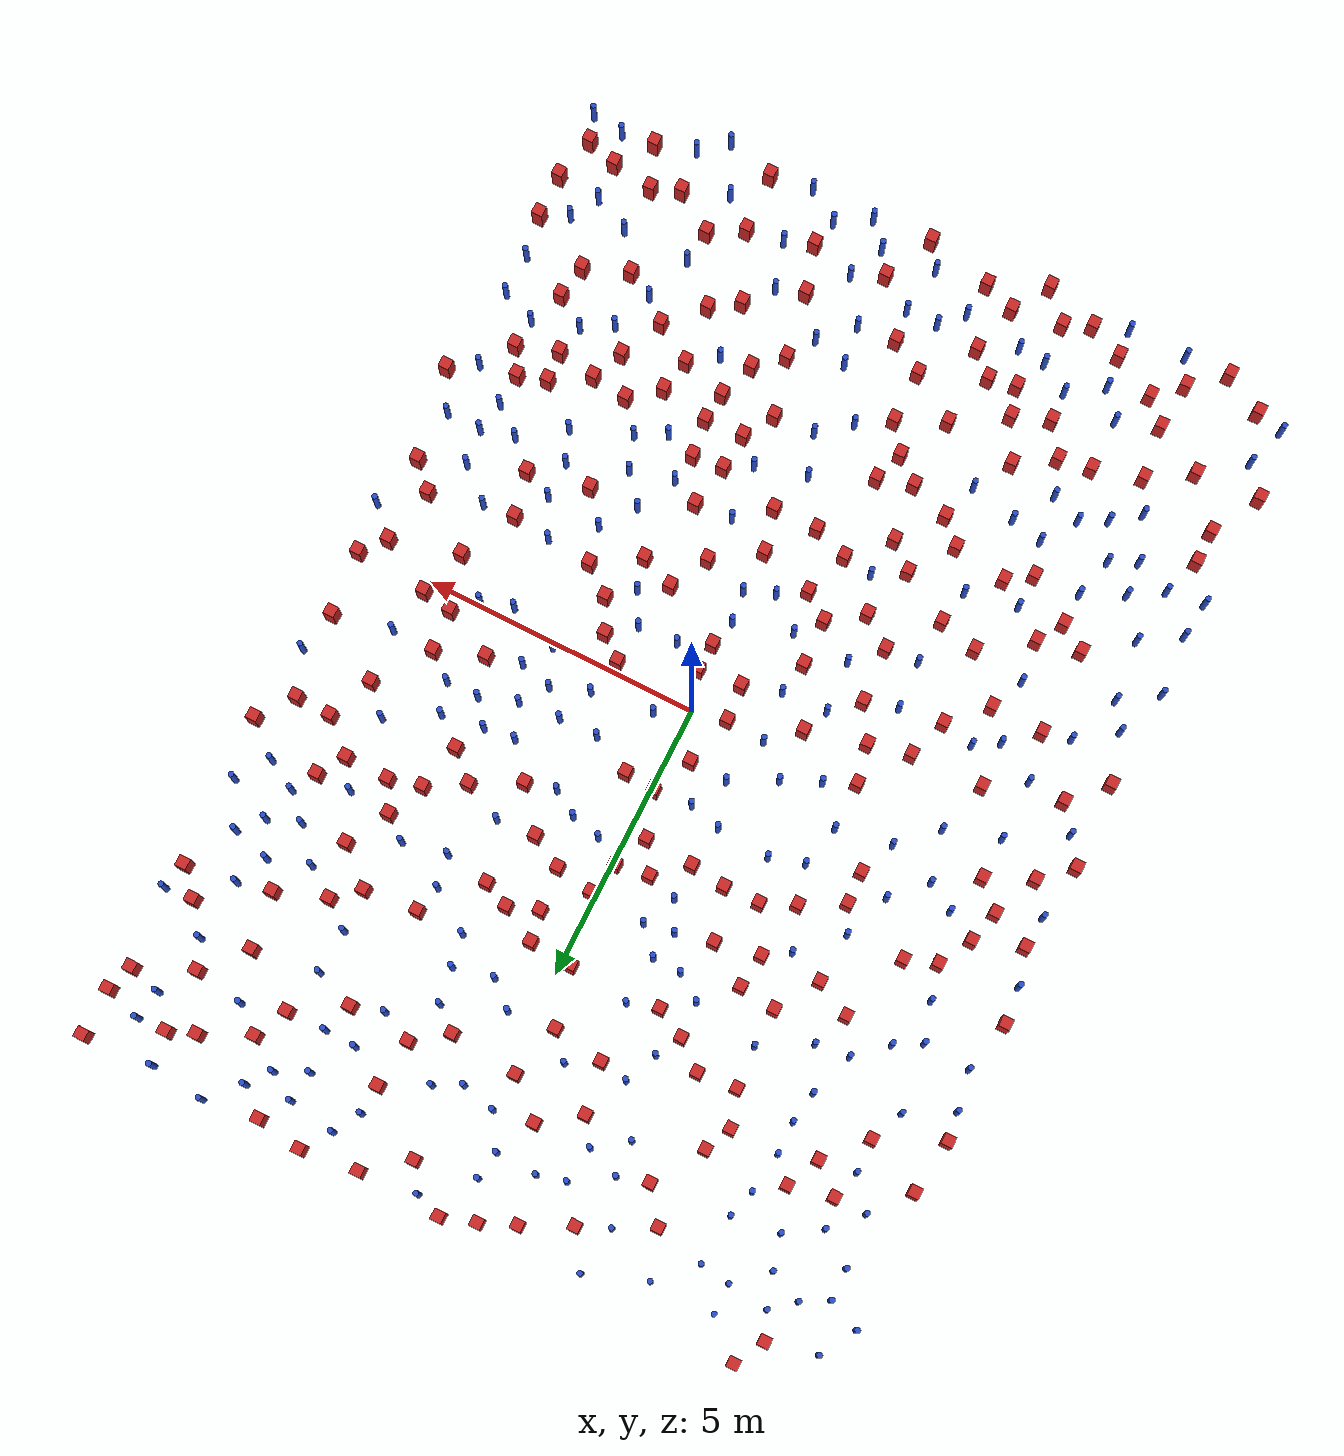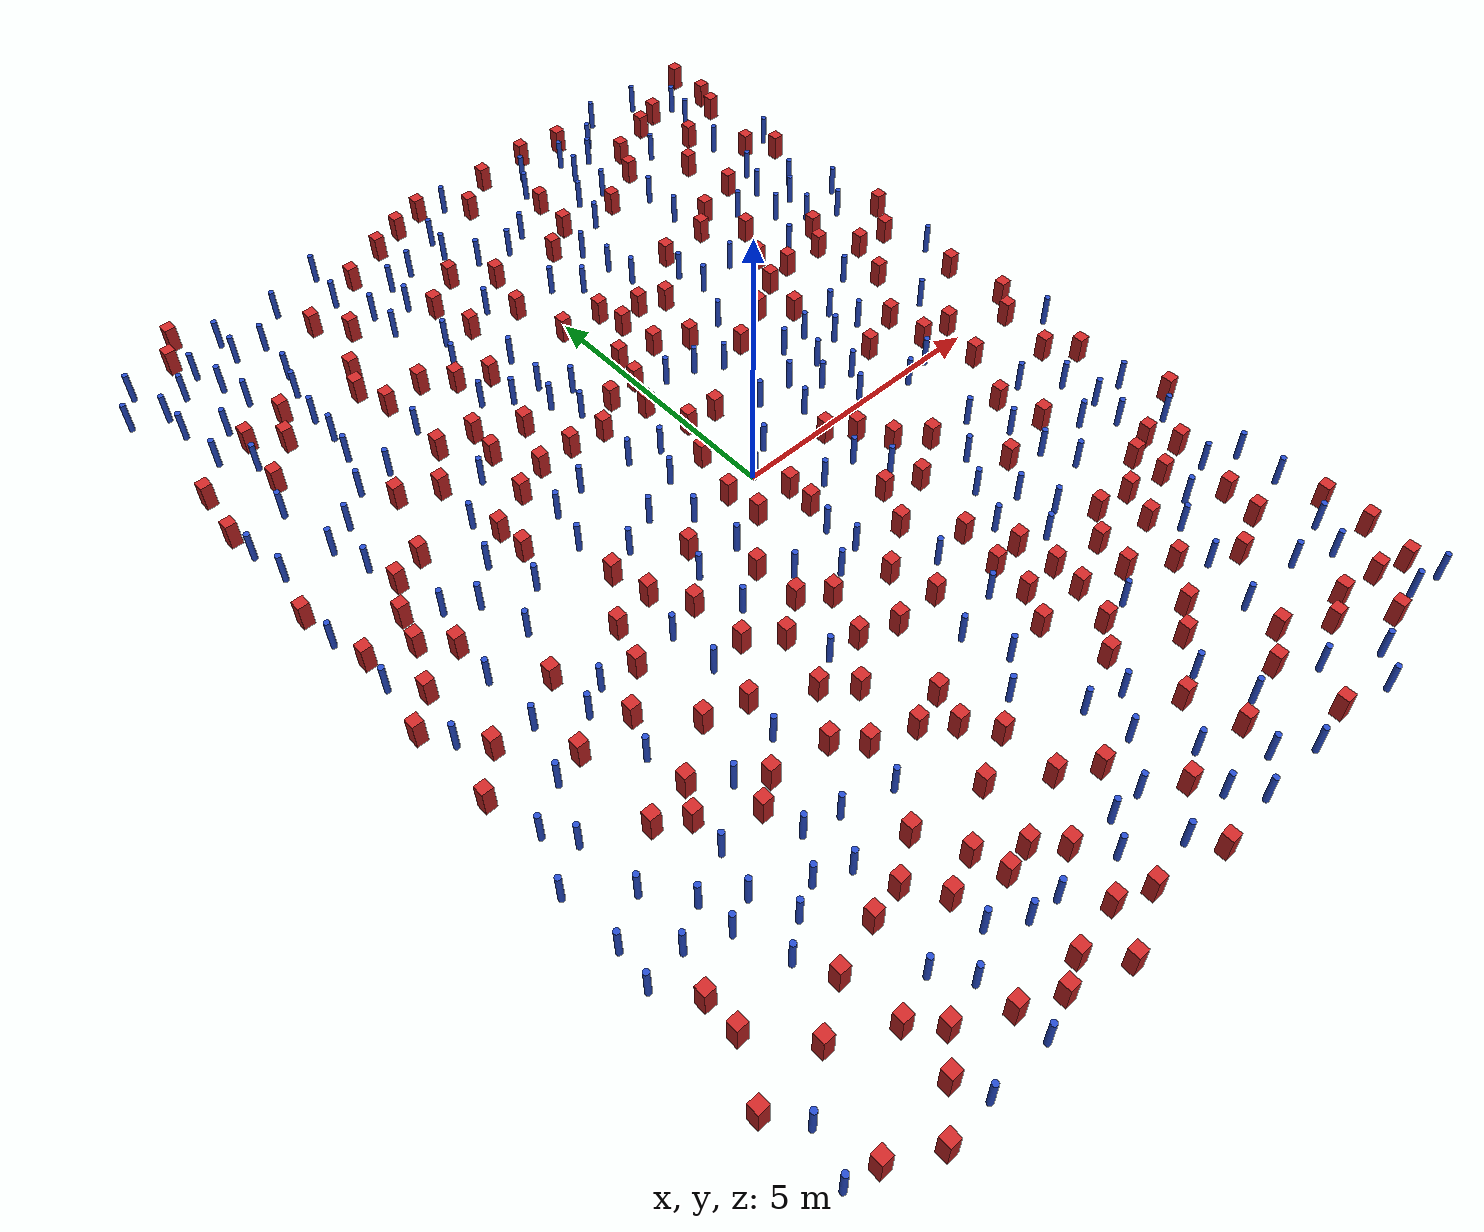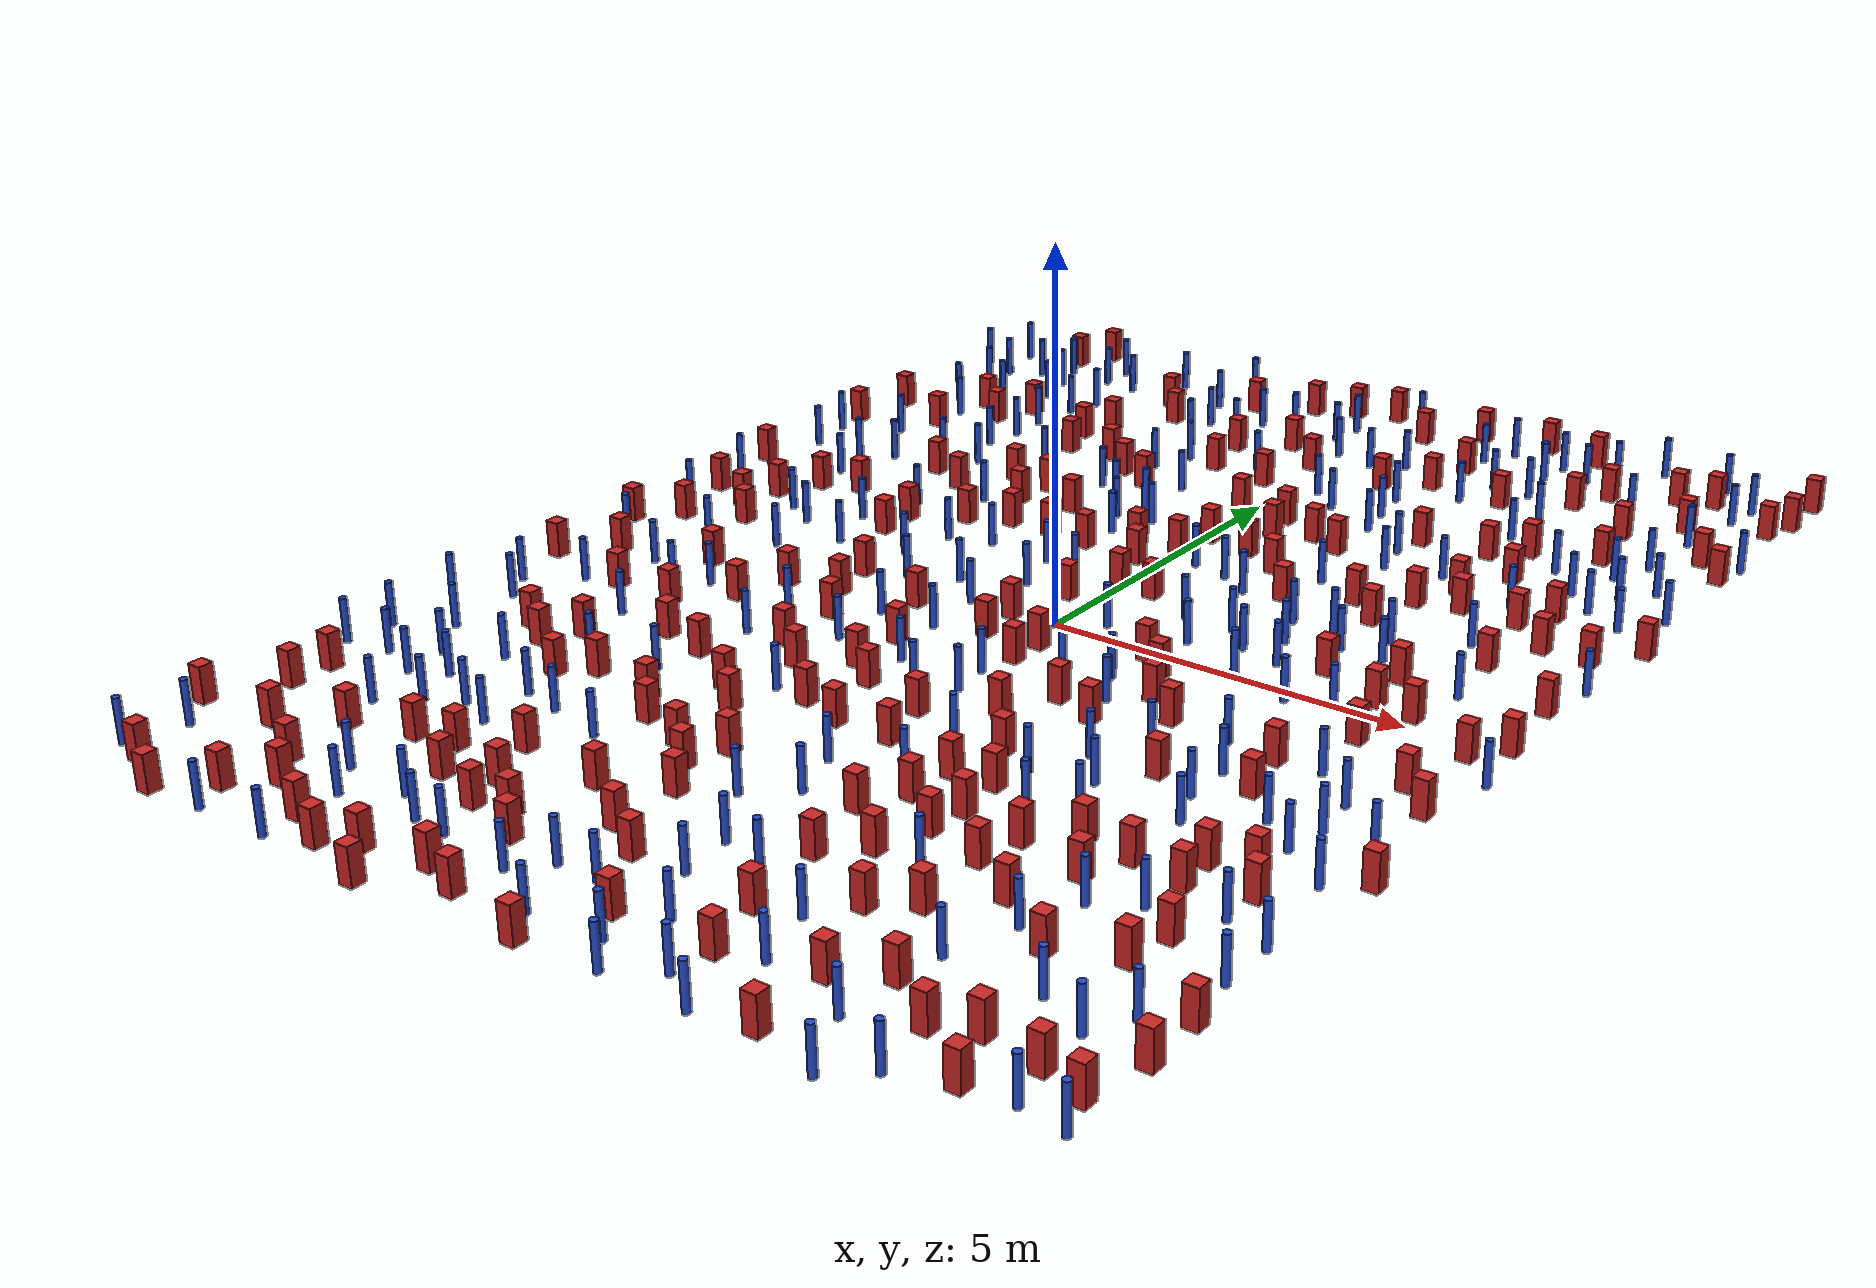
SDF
<sdf version="1.6">
  <model name="dense_36"><model name="square_post_obstacle0">
  <static>true</static>
  <pose frame="">-0.75469007725 9.18106437961 8.22691968438e-08 7.22125133819e-06 -7.54495500217e-07 2.29674213826e-05</pose>
  <link name="link">
    <pose frame="">0 0 0.25 0 -0 0</pose>
    <inertial>
      <mass>100</mass>
      <inertia>
        <ixx>0.166667</ixx>
        <ixy>0</ixy>
        <ixz>0</ixz>
        <iyy>0.166667</iyy>
        <iyz>0</iyz>
        <izz>0.166667</izz>
      </inertia>
    </inertial>
    <collision name="collision">
      <geometry>
        <box>
          <size>.2 .2 .5</size>
        </box>
      </geometry>
      <max_contacts>10</max_contacts>
      <surface>
        <contact>
          <ode/>
        </contact>
        <bounce/>
        <friction>
          <torsional>
            <ode/>
          </torsional>
          <ode/>
        </friction>
      </surface>
    </collision>
    <visual name="visual">
      <geometry>
        <box>
          <size>.2 .2 .5</size>
        </box>
      </geometry>
      <material>
        <script>
          <name>Gazebo/Red</name>
          <uri>file://media/materials/scripts/gazebo.material</uri>
        </script>
      </material>
    </visual>
    <self_collide>0</self_collide>
    <kinematic>0</kinematic>
  </link>
</model>
<model name="square_post_obstacle1">
  <static>true</static>
  <pose frame="">-6.99234724845 2.41279197193 8.22691968438e-08 7.2212513382e-06 -7.54495500217e-07 2.29674213826e-05</pose>
  <link name="link">
    <pose frame="">0 0 0.25 0 -0 0</pose>
    <inertial>
      <mass>100</mass>
      <inertia>
        <ixx>0.166667</ixx>
        <ixy>0</ixy>
        <ixz>0</ixz>
        <iyy>0.166667</iyy>
        <iyz>0</iyz>
        <izz>0.166667</izz>
      </inertia>
    </inertial>
    <collision name="collision">
      <geometry>
        <box>
          <size>.2 .2 .5</size>
        </box>
      </geometry>
      <max_contacts>10</max_contacts>
      <surface>
        <contact>
          <ode/>
        </contact>
        <bounce/>
        <friction>
          <torsional>
            <ode/>
          </torsional>
          <ode/>
        </friction>
      </surface>
    </collision>
    <visual name="visual">
      <geometry>
        <box>
          <size>.2 .2 .5</size>
        </box>
      </geometry>
      <material>
        <script>
          <name>Gazebo/Red</name>
          <uri>file://media/materials/scripts/gazebo.material</uri>
        </script>
      </material>
    </visual>
    <self_collide>0</self_collide>
    <kinematic>0</kinematic>
  </link>
</model>
<model name="pole_obstacle0">
  <static>true</static>
  <pose frame="">-2.29478972148 4.37844473224 2.88873142074e-08 -9.90536689859e-09 4.60219948989e-07 -1.20965994961e-07</pose>
  <link name="link">
  <pose frame="">0 0 0.3 0 -0 0</pose>
    <inertial>
      <mass>1</mass>
      <inertia>
        <ixx>0.145833</ixx>
        <ixy>0</ixy>
        <ixz>0</ixz>
        <iyy>0.145833</iyy>
        <iyz>0</iyz>
        <izz>0.125</izz>
      </inertia>
    </inertial>
    <collision name="collision">
      <geometry>
        <cylinder>
          <radius>0.05</radius>
          <length>.6</length>
        </cylinder>
      </geometry>
      <max_contacts>10</max_contacts>
      <surface>
        <contact>
          <ode/>
        </contact>
        <bounce/>
        <friction>
          <torsional>
            <ode/>
          </torsional>
          <ode/>
        </friction>
      </surface>
    </collision>
    <visual name="visual">
      <geometry>
        <cylinder>
          <radius>0.05</radius>
          <length>.6</length>
        </cylinder>
      </geometry>
      <material>
        <script>
          <name>Gazebo/Blue</name>
          <uri>file://media/materials/scripts/gazebo.material</uri>
        </script>
      </material>
    </visual>
    <self_collide>0</self_collide>
    <kinematic>0</kinematic>
  </link>
</model>
<model name="square_post_obstacle2">
  <static>true</static>
  <pose frame="">-0.434591749695 5.815922877 8.22691968438e-08 7.22125133819e-06 -7.54495500217e-07 2.29674213826e-05</pose>
  <link name="link">
    <pose frame="">0 0 0.25 0 -0 0</pose>
    <inertial>
      <mass>100</mass>
      <inertia>
        <ixx>0.166667</ixx>
        <ixy>0</ixy>
        <ixz>0</ixz>
        <iyy>0.166667</iyy>
        <iyz>0</iyz>
        <izz>0.166667</izz>
      </inertia>
    </inertial>
    <collision name="collision">
      <geometry>
        <box>
          <size>.2 .2 .5</size>
        </box>
      </geometry>
      <max_contacts>10</max_contacts>
      <surface>
        <contact>
          <ode/>
        </contact>
        <bounce/>
        <friction>
          <torsional>
            <ode/>
          </torsional>
          <ode/>
        </friction>
      </surface>
    </collision>
    <visual name="visual">
      <geometry>
        <box>
          <size>.2 .2 .5</size>
        </box>
      </geometry>
      <material>
        <script>
          <name>Gazebo/Red</name>
          <uri>file://media/materials/scripts/gazebo.material</uri>
        </script>
      </material>
    </visual>
    <self_collide>0</self_collide>
    <kinematic>0</kinematic>
  </link>
</model>
<model name="pole_obstacle1">
  <static>true</static>
  <pose frame="">1.21539966875 1.14167519535 2.88873142074e-08 -9.90536689672e-09 4.60219948993e-07 -1.20965994959e-07</pose>
  <link name="link">
  <pose frame="">0 0 0.3 0 -0 0</pose>
    <inertial>
      <mass>1</mass>
      <inertia>
        <ixx>0.145833</ixx>
        <ixy>0</ixy>
        <ixz>0</ixz>
        <iyy>0.145833</iyy>
        <iyz>0</iyz>
        <izz>0.125</izz>
      </inertia>
    </inertial>
    <collision name="collision">
      <geometry>
        <cylinder>
          <radius>0.05</radius>
          <length>.6</length>
        </cylinder>
      </geometry>
      <max_contacts>10</max_contacts>
      <surface>
        <contact>
          <ode/>
        </contact>
        <bounce/>
        <friction>
          <torsional>
            <ode/>
          </torsional>
          <ode/>
        </friction>
      </surface>
    </collision>
    <visual name="visual">
      <geometry>
        <cylinder>
          <radius>0.05</radius>
          <length>.6</length>
        </cylinder>
      </geometry>
      <material>
        <script>
          <name>Gazebo/Blue</name>
          <uri>file://media/materials/scripts/gazebo.material</uri>
        </script>
      </material>
    </visual>
    <self_collide>0</self_collide>
    <kinematic>0</kinematic>
  </link>
</model>
<model name="square_post_obstacle3">
  <static>true</static>
  <pose frame="">-3.4951687476 3.90393180794 8.22691968438e-08 7.2212513382e-06 -7.54495500217e-07 2.29674213826e-05</pose>
  <link name="link">
    <pose frame="">0 0 0.25 0 -0 0</pose>
    <inertial>
      <mass>100</mass>
      <inertia>
        <ixx>0.166667</ixx>
        <ixy>0</ixy>
        <ixz>0</ixz>
        <iyy>0.166667</iyy>
        <iyz>0</iyz>
        <izz>0.166667</izz>
      </inertia>
    </inertial>
    <collision name="collision">
      <geometry>
        <box>
          <size>.2 .2 .5</size>
        </box>
      </geometry>
      <max_contacts>10</max_contacts>
      <surface>
        <contact>
          <ode/>
        </contact>
        <bounce/>
        <friction>
          <torsional>
            <ode/>
          </torsional>
          <ode/>
        </friction>
      </surface>
    </collision>
    <visual name="visual">
      <geometry>
        <box>
          <size>.2 .2 .5</size>
        </box>
      </geometry>
      <material>
        <script>
          <name>Gazebo/Red</name>
          <uri>file://media/materials/scripts/gazebo.material</uri>
        </script>
      </material>
    </visual>
    <self_collide>0</self_collide>
    <kinematic>0</kinematic>
  </link>
</model>
<model name="pole_obstacle2">
  <static>true</static>
  <pose frame="">3.31272624957 1.4470777101 2.88873142074e-08 -9.90536689395e-09 4.60219949e-07 -1.20965994953e-07</pose>
  <link name="link">
  <pose frame="">0 0 0.3 0 -0 0</pose>
    <inertial>
      <mass>1</mass>
      <inertia>
        <ixx>0.145833</ixx>
        <ixy>0</ixy>
        <ixz>0</ixz>
        <iyy>0.145833</iyy>
        <iyz>0</iyz>
        <izz>0.125</izz>
      </inertia>
    </inertial>
    <collision name="collision">
      <geometry>
        <cylinder>
          <radius>0.05</radius>
          <length>.6</length>
        </cylinder>
      </geometry>
      <max_contacts>10</max_contacts>
      <surface>
        <contact>
          <ode/>
        </contact>
        <bounce/>
        <friction>
          <torsional>
            <ode/>
          </torsional>
          <ode/>
        </friction>
      </surface>
    </collision>
    <visual name="visual">
      <geometry>
        <cylinder>
          <radius>0.05</radius>
          <length>.6</length>
        </cylinder>
      </geometry>
      <material>
        <script>
          <name>Gazebo/Blue</name>
          <uri>file://media/materials/scripts/gazebo.material</uri>
        </script>
      </material>
    </visual>
    <self_collide>0</self_collide>
    <kinematic>0</kinematic>
  </link>
</model>
<model name="pole_obstacle3">
  <static>true</static>
  <pose frame="">-4.65431154523 -0.049632451906 2.88873142074e-08 -9.90536689836e-09 4.60219948989e-07 -1.20965994962e-07</pose>
  <link name="link">
  <pose frame="">0 0 0.3 0 -0 0</pose>
    <inertial>
      <mass>1</mass>
      <inertia>
        <ixx>0.145833</ixx>
        <ixy>0</ixy>
        <ixz>0</ixz>
        <iyy>0.145833</iyy>
        <iyz>0</iyz>
        <izz>0.125</izz>
      </inertia>
    </inertial>
    <collision name="collision">
      <geometry>
        <cylinder>
          <radius>0.05</radius>
          <length>.6</length>
        </cylinder>
      </geometry>
      <max_contacts>10</max_contacts>
      <surface>
        <contact>
          <ode/>
        </contact>
        <bounce/>
        <friction>
          <torsional>
            <ode/>
          </torsional>
          <ode/>
        </friction>
      </surface>
    </collision>
    <visual name="visual">
      <geometry>
        <cylinder>
          <radius>0.05</radius>
          <length>.6</length>
        </cylinder>
      </geometry>
      <material>
        <script>
          <name>Gazebo/Blue</name>
          <uri>file://media/materials/scripts/gazebo.material</uri>
        </script>
      </material>
    </visual>
    <self_collide>0</self_collide>
    <kinematic>0</kinematic>
  </link>
</model>
<model name="square_post_obstacle4">
  <static>true</static>
  <pose frame="">-0.833897345285 7.33856920669 8.22691968438e-08 7.2212513382e-06 -7.54495500217e-07 2.29674213826e-05</pose>
  <link name="link">
    <pose frame="">0 0 0.25 0 -0 0</pose>
    <inertial>
      <mass>100</mass>
      <inertia>
        <ixx>0.166667</ixx>
        <ixy>0</ixy>
        <ixz>0</ixz>
        <iyy>0.166667</iyy>
        <iyz>0</iyz>
        <izz>0.166667</izz>
      </inertia>
    </inertial>
    <collision name="collision">
      <geometry>
        <box>
          <size>.2 .2 .5</size>
        </box>
      </geometry>
      <max_contacts>10</max_contacts>
      <surface>
        <contact>
          <ode/>
        </contact>
        <bounce/>
        <friction>
          <torsional>
            <ode/>
          </torsional>
          <ode/>
        </friction>
      </surface>
    </collision>
    <visual name="visual">
      <geometry>
        <box>
          <size>.2 .2 .5</size>
        </box>
      </geometry>
      <material>
        <script>
          <name>Gazebo/Red</name>
          <uri>file://media/materials/scripts/gazebo.material</uri>
        </script>
      </material>
    </visual>
    <self_collide>0</self_collide>
    <kinematic>0</kinematic>
  </link>
</model>
<model name="square_post_obstacle5">
  <static>true</static>
  <pose frame="">-3.79861720325 1.78377909363 8.22691968438e-08 7.22125133819e-06 -7.54495500217e-07 2.29674213826e-05</pose>
  <link name="link">
    <pose frame="">0 0 0.25 0 -0 0</pose>
    <inertial>
      <mass>100</mass>
      <inertia>
        <ixx>0.166667</ixx>
        <ixy>0</ixy>
        <ixz>0</ixz>
        <iyy>0.166667</iyy>
        <iyz>0</iyz>
        <izz>0.166667</izz>
      </inertia>
    </inertial>
    <collision name="collision">
      <geometry>
        <box>
          <size>.2 .2 .5</size>
        </box>
      </geometry>
      <max_contacts>10</max_contacts>
      <surface>
        <contact>
          <ode/>
        </contact>
        <bounce/>
        <friction>
          <torsional>
            <ode/>
          </torsional>
          <ode/>
        </friction>
      </surface>
    </collision>
    <visual name="visual">
      <geometry>
        <box>
          <size>.2 .2 .5</size>
        </box>
      </geometry>
      <material>
        <script>
          <name>Gazebo/Red</name>
          <uri>file://media/materials/scripts/gazebo.material</uri>
        </script>
      </material>
    </visual>
    <self_collide>0</self_collide>
    <kinematic>0</kinematic>
  </link>
</model>
<model name="square_post_obstacle6">
  <static>true</static>
  <pose frame="">0.93513681308 -2.43418573945 8.22691968438e-08 7.2212513382e-06 -7.54495500217e-07 2.29674213826e-05</pose>
  <link name="link">
    <pose frame="">0 0 0.25 0 -0 0</pose>
    <inertial>
      <mass>100</mass>
      <inertia>
        <ixx>0.166667</ixx>
        <ixy>0</ixy>
        <ixz>0</ixz>
        <iyy>0.166667</iyy>
        <iyz>0</iyz>
        <izz>0.166667</izz>
      </inertia>
    </inertial>
    <collision name="collision">
      <geometry>
        <box>
          <size>.2 .2 .5</size>
        </box>
      </geometry>
      <max_contacts>10</max_contacts>
      <surface>
        <contact>
          <ode/>
        </contact>
        <bounce/>
        <friction>
          <torsional>
            <ode/>
          </torsional>
          <ode/>
        </friction>
      </surface>
    </collision>
    <visual name="visual">
      <geometry>
        <box>
          <size>.2 .2 .5</size>
        </box>
      </geometry>
      <material>
        <script>
          <name>Gazebo/Red</name>
          <uri>file://media/materials/scripts/gazebo.material</uri>
        </script>
      </material>
    </visual>
    <self_collide>0</self_collide>
    <kinematic>0</kinematic>
  </link>
</model>
<model name="pole_obstacle4">
  <static>true</static>
  <pose frame="">0.323887015425 9.21397192133 2.88873142074e-08 -9.90536691079e-09 4.6021994896e-07 -1.2096599498e-07</pose>
  <link name="link">
  <pose frame="">0 0 0.3 0 -0 0</pose>
    <inertial>
      <mass>1</mass>
      <inertia>
        <ixx>0.145833</ixx>
        <ixy>0</ixy>
        <ixz>0</ixz>
        <iyy>0.145833</iyy>
        <iyz>0</iyz>
        <izz>0.125</izz>
      </inertia>
    </inertial>
    <collision name="collision">
      <geometry>
        <cylinder>
          <radius>0.05</radius>
          <length>.6</length>
        </cylinder>
      </geometry>
      <max_contacts>10</max_contacts>
      <surface>
        <contact>
          <ode/>
        </contact>
        <bounce/>
        <friction>
          <torsional>
            <ode/>
          </torsional>
          <ode/>
        </friction>
      </surface>
    </collision>
    <visual name="visual">
      <geometry>
        <cylinder>
          <radius>0.05</radius>
          <length>.6</length>
        </cylinder>
      </geometry>
      <material>
        <script>
          <name>Gazebo/Blue</name>
          <uri>file://media/materials/scripts/gazebo.material</uri>
        </script>
      </material>
    </visual>
    <self_collide>0</self_collide>
    <kinematic>0</kinematic>
  </link>
</model>
<model name="pole_obstacle5">
  <static>true</static>
  <pose frame="">-4.36620819852 7.22213696595 2.88873142074e-08 -9.90536690842e-09 4.60219948965e-07 -1.20965994976e-07</pose>
  <link name="link">
  <pose frame="">0 0 0.3 0 -0 0</pose>
    <inertial>
      <mass>1</mass>
      <inertia>
        <ixx>0.145833</ixx>
        <ixy>0</ixy>
        <ixz>0</ixz>
        <iyy>0.145833</iyy>
        <iyz>0</iyz>
        <izz>0.125</izz>
      </inertia>
    </inertial>
    <collision name="collision">
      <geometry>
        <cylinder>
          <radius>0.05</radius>
          <length>.6</length>
        </cylinder>
      </geometry>
      <max_contacts>10</max_contacts>
      <surface>
        <contact>
          <ode/>
        </contact>
        <bounce/>
        <friction>
          <torsional>
            <ode/>
          </torsional>
          <ode/>
        </friction>
      </surface>
    </collision>
    <visual name="visual">
      <geometry>
        <cylinder>
          <radius>0.05</radius>
          <length>.6</length>
        </cylinder>
      </geometry>
      <material>
        <script>
          <name>Gazebo/Blue</name>
          <uri>file://media/materials/scripts/gazebo.material</uri>
        </script>
      </material>
    </visual>
    <self_collide>0</self_collide>
    <kinematic>0</kinematic>
  </link>
</model>
<model name="square_post_obstacle7">
  <static>true</static>
  <pose frame="">-3.04492859642 -0.102754242791 8.22691968438e-08 7.2212513382e-06 -7.54495500217e-07 2.29674213826e-05</pose>
  <link name="link">
    <pose frame="">0 0 0.25 0 -0 0</pose>
    <inertial>
      <mass>100</mass>
      <inertia>
        <ixx>0.166667</ixx>
        <ixy>0</ixy>
        <ixz>0</ixz>
        <iyy>0.166667</iyy>
        <iyz>0</iyz>
        <izz>0.166667</izz>
      </inertia>
    </inertial>
    <collision name="collision">
      <geometry>
        <box>
          <size>.2 .2 .5</size>
        </box>
      </geometry>
      <max_contacts>10</max_contacts>
      <surface>
        <contact>
          <ode/>
        </contact>
        <bounce/>
        <friction>
          <torsional>
            <ode/>
          </torsional>
          <ode/>
        </friction>
      </surface>
    </collision>
    <visual name="visual">
      <geometry>
        <box>
          <size>.2 .2 .5</size>
        </box>
      </geometry>
      <material>
        <script>
          <name>Gazebo/Red</name>
          <uri>file://media/materials/scripts/gazebo.material</uri>
        </script>
      </material>
    </visual>
    <self_collide>0</self_collide>
    <kinematic>0</kinematic>
  </link>
</model>
<model name="square_post_obstacle8">
  <static>true</static>
  <pose frame="">5.34493941089 -3.87671803789 8.22691968438e-08 7.2212513382e-06 -7.54495500217e-07 2.29674213826e-05</pose>
  <link name="link">
    <pose frame="">0 0 0.25 0 -0 0</pose>
    <inertial>
      <mass>100</mass>
      <inertia>
        <ixx>0.166667</ixx>
        <ixy>0</ixy>
        <ixz>0</ixz>
        <iyy>0.166667</iyy>
        <iyz>0</iyz>
        <izz>0.166667</izz>
      </inertia>
    </inertial>
    <collision name="collision">
      <geometry>
        <box>
          <size>.2 .2 .5</size>
        </box>
      </geometry>
      <max_contacts>10</max_contacts>
      <surface>
        <contact>
          <ode/>
        </contact>
        <bounce/>
        <friction>
          <torsional>
            <ode/>
          </torsional>
          <ode/>
        </friction>
      </surface>
    </collision>
    <visual name="visual">
      <geometry>
        <box>
          <size>.2 .2 .5</size>
        </box>
      </geometry>
      <material>
        <script>
          <name>Gazebo/Red</name>
          <uri>file://media/materials/scripts/gazebo.material</uri>
        </script>
      </material>
    </visual>
    <self_collide>0</self_collide>
    <kinematic>0</kinematic>
  </link>
</model>
<model name="pole_obstacle6">
  <static>true</static>
  <pose frame="">-2.51424352725 0.137398515077 2.88873142074e-08 -9.90536689314e-09 4.60219949002e-07 -1.20965994953e-07</pose>
  <link name="link">
  <pose frame="">0 0 0.3 0 -0 0</pose>
    <inertial>
      <mass>1</mass>
      <inertia>
        <ixx>0.145833</ixx>
        <ixy>0</ixy>
        <ixz>0</ixz>
        <iyy>0.145833</iyy>
        <iyz>0</iyz>
        <izz>0.125</izz>
      </inertia>
    </inertial>
    <collision name="collision">
      <geometry>
        <cylinder>
          <radius>0.05</radius>
          <length>.6</length>
        </cylinder>
      </geometry>
      <max_contacts>10</max_contacts>
      <surface>
        <contact>
          <ode/>
        </contact>
        <bounce/>
        <friction>
          <torsional>
            <ode/>
          </torsional>
          <ode/>
        </friction>
      </surface>
    </collision>
    <visual name="visual">
      <geometry>
        <cylinder>
          <radius>0.05</radius>
          <length>.6</length>
        </cylinder>
      </geometry>
      <material>
        <script>
          <name>Gazebo/Blue</name>
          <uri>file://media/materials/scripts/gazebo.material</uri>
        </script>
      </material>
    </visual>
    <self_collide>0</self_collide>
    <kinematic>0</kinematic>
  </link>
</model>
<model name="pole_obstacle7">
  <static>true</static>
  <pose frame="">-2.53823179781 -5.63883485997 2.88873142074e-08 -9.90536689859e-09 4.60219948989e-07 -1.20965994961e-07</pose>
  <link name="link">
  <pose frame="">0 0 0.3 0 -0 0</pose>
    <inertial>
      <mass>1</mass>
      <inertia>
        <ixx>0.145833</ixx>
        <ixy>0</ixy>
        <ixz>0</ixz>
        <iyy>0.145833</iyy>
        <iyz>0</iyz>
        <izz>0.125</izz>
      </inertia>
    </inertial>
    <collision name="collision">
      <geometry>
        <cylinder>
          <radius>0.05</radius>
          <length>.6</length>
        </cylinder>
      </geometry>
      <max_contacts>10</max_contacts>
      <surface>
        <contact>
          <ode/>
        </contact>
        <bounce/>
        <friction>
          <torsional>
            <ode/>
          </torsional>
          <ode/>
        </friction>
      </surface>
    </collision>
    <visual name="visual">
      <geometry>
        <cylinder>
          <radius>0.05</radius>
          <length>.6</length>
        </cylinder>
      </geometry>
      <material>
        <script>
          <name>Gazebo/Blue</name>
          <uri>file://media/materials/scripts/gazebo.material</uri>
        </script>
      </material>
    </visual>
    <self_collide>0</self_collide>
    <kinematic>0</kinematic>
  </link>
</model>
<model name="square_post_obstacle9">
  <static>true</static>
  <pose frame="">-2.44712936653 -2.39716291056 8.22691968438e-08 7.2212513382e-06 -7.54495500217e-07 2.29674213826e-05</pose>
  <link name="link">
    <pose frame="">0 0 0.25 0 -0 0</pose>
    <inertial>
      <mass>100</mass>
      <inertia>
        <ixx>0.166667</ixx>
        <ixy>0</ixy>
        <ixz>0</ixz>
        <iyy>0.166667</iyy>
        <iyz>0</iyz>
        <izz>0.166667</izz>
      </inertia>
    </inertial>
    <collision name="collision">
      <geometry>
        <box>
          <size>.2 .2 .5</size>
        </box>
      </geometry>
      <max_contacts>10</max_contacts>
      <surface>
        <contact>
          <ode/>
        </contact>
        <bounce/>
        <friction>
          <torsional>
            <ode/>
          </torsional>
          <ode/>
        </friction>
      </surface>
    </collision>
    <visual name="visual">
      <geometry>
        <box>
          <size>.2 .2 .5</size>
        </box>
      </geometry>
      <material>
        <script>
          <name>Gazebo/Red</name>
          <uri>file://media/materials/scripts/gazebo.material</uri>
        </script>
      </material>
    </visual>
    <self_collide>0</self_collide>
    <kinematic>0</kinematic>
  </link>
</model>
<model name="square_post_obstacle10">
  <static>true</static>
  <pose frame="">-3.7672462123 1.2102745779 8.22691968438e-08 7.2212513382e-06 -7.54495500217e-07 2.29674213826e-05</pose>
  <link name="link">
    <pose frame="">0 0 0.25 0 -0 0</pose>
    <inertial>
      <mass>100</mass>
      <inertia>
        <ixx>0.166667</ixx>
        <ixy>0</ixy>
        <ixz>0</ixz>
        <iyy>0.166667</iyy>
        <iyz>0</iyz>
        <izz>0.166667</izz>
      </inertia>
    </inertial>
    <collision name="collision">
      <geometry>
        <box>
          <size>.2 .2 .5</size>
        </box>
      </geometry>
      <max_contacts>10</max_contacts>
      <surface>
        <contact>
          <ode/>
        </contact>
        <bounce/>
        <friction>
          <torsional>
            <ode/>
          </torsional>
          <ode/>
        </friction>
      </surface>
    </collision>
    <visual name="visual">
      <geometry>
        <box>
          <size>.2 .2 .5</size>
        </box>
      </geometry>
      <material>
        <script>
          <name>Gazebo/Red</name>
          <uri>file://media/materials/scripts/gazebo.material</uri>
        </script>
      </material>
    </visual>
    <self_collide>0</self_collide>
    <kinematic>0</kinematic>
  </link>
</model>
<model name="square_post_obstacle11">
  <static>true</static>
  <pose frame="">5.33757525692 -5.51145749906 8.22691968438e-08 7.22125133819e-06 -7.54495500217e-07 2.29674213826e-05</pose>
  <link name="link">
    <pose frame="">0 0 0.25 0 -0 0</pose>
    <inertial>
      <mass>100</mass>
      <inertia>
        <ixx>0.166667</ixx>
        <ixy>0</ixy>
        <ixz>0</ixz>
        <iyy>0.166667</iyy>
        <iyz>0</iyz>
        <izz>0.166667</izz>
      </inertia>
    </inertial>
    <collision name="collision">
      <geometry>
        <box>
          <size>.2 .2 .5</size>
        </box>
      </geometry>
      <max_contacts>10</max_contacts>
      <surface>
        <contact>
          <ode/>
        </contact>
        <bounce/>
        <friction>
          <torsional>
            <ode/>
          </torsional>
          <ode/>
        </friction>
      </surface>
    </collision>
    <visual name="visual">
      <geometry>
        <box>
          <size>.2 .2 .5</size>
        </box>
      </geometry>
      <material>
        <script>
          <name>Gazebo/Red</name>
          <uri>file://media/materials/scripts/gazebo.material</uri>
        </script>
      </material>
    </visual>
    <self_collide>0</self_collide>
    <kinematic>0</kinematic>
  </link>
</model>
<model name="square_post_obstacle12">
  <static>true</static>
  <pose frame="">-4.19617129068 -6.83578987014 8.22691968438e-08 7.22125133819e-06 -7.54495500217e-07 2.29674213826e-05</pose>
  <link name="link">
    <pose frame="">0 0 0.25 0 -0 0</pose>
    <inertial>
      <mass>100</mass>
      <inertia>
        <ixx>0.166667</ixx>
        <ixy>0</ixy>
        <ixz>0</ixz>
        <iyy>0.166667</iyy>
        <iyz>0</iyz>
        <izz>0.166667</izz>
      </inertia>
    </inertial>
    <collision name="collision">
      <geometry>
        <box>
          <size>.2 .2 .5</size>
        </box>
      </geometry>
      <max_contacts>10</max_contacts>
      <surface>
        <contact>
          <ode/>
        </contact>
        <bounce/>
        <friction>
          <torsional>
            <ode/>
          </torsional>
          <ode/>
        </friction>
      </surface>
    </collision>
    <visual name="visual">
      <geometry>
        <box>
          <size>.2 .2 .5</size>
        </box>
      </geometry>
      <material>
        <script>
          <name>Gazebo/Red</name>
          <uri>file://media/materials/scripts/gazebo.material</uri>
        </script>
      </material>
    </visual>
    <self_collide>0</self_collide>
    <kinematic>0</kinematic>
  </link>
</model>
<model name="square_post_obstacle13">
  <static>true</static>
  <pose frame="">-1.74372210158 -4.18041785908 8.22691968438e-08 7.2212513382e-06 -7.54495500217e-07 2.29674213826e-05</pose>
  <link name="link">
    <pose frame="">0 0 0.25 0 -0 0</pose>
    <inertial>
      <mass>100</mass>
      <inertia>
        <ixx>0.166667</ixx>
        <ixy>0</ixy>
        <ixz>0</ixz>
        <iyy>0.166667</iyy>
        <iyz>0</iyz>
        <izz>0.166667</izz>
      </inertia>
    </inertial>
    <collision name="collision">
      <geometry>
        <box>
          <size>.2 .2 .5</size>
        </box>
      </geometry>
      <max_contacts>10</max_contacts>
      <surface>
        <contact>
          <ode/>
        </contact>
        <bounce/>
        <friction>
          <torsional>
            <ode/>
          </torsional>
          <ode/>
        </friction>
      </surface>
    </collision>
    <visual name="visual">
      <geometry>
        <box>
          <size>.2 .2 .5</size>
        </box>
      </geometry>
      <material>
        <script>
          <name>Gazebo/Red</name>
          <uri>file://media/materials/scripts/gazebo.material</uri>
        </script>
      </material>
    </visual>
    <self_collide>0</self_collide>
    <kinematic>0</kinematic>
  </link>
</model>
<model name="pole_obstacle8">
  <static>true</static>
  <pose frame="">-3.8167957619 -8.28989017368 2.88873142074e-08 -9.90536692318e-09 4.6021994893e-07 -1.20965994988e-07</pose>
  <link name="link">
  <pose frame="">0 0 0.3 0 -0 0</pose>
    <inertial>
      <mass>1</mass>
      <inertia>
        <ixx>0.145833</ixx>
        <ixy>0</ixy>
        <ixz>0</ixz>
        <iyy>0.145833</iyy>
        <iyz>0</iyz>
        <izz>0.125</izz>
      </inertia>
    </inertial>
    <collision name="collision">
      <geometry>
        <cylinder>
          <radius>0.05</radius>
          <length>.6</length>
        </cylinder>
      </geometry>
      <max_contacts>10</max_contacts>
      <surface>
        <contact>
          <ode/>
        </contact>
        <bounce/>
        <friction>
          <torsional>
            <ode/>
          </torsional>
          <ode/>
        </friction>
      </surface>
    </collision>
    <visual name="visual">
      <geometry>
        <cylinder>
          <radius>0.05</radius>
          <length>.6</length>
        </cylinder>
      </geometry>
      <material>
        <script>
          <name>Gazebo/Blue</name>
          <uri>file://media/materials/scripts/gazebo.material</uri>
        </script>
      </material>
    </visual>
    <self_collide>0</self_collide>
    <kinematic>0</kinematic>
  </link>
</model>
<model name="square_post_obstacle14">
  <static>true</static>
  <pose frame="">3.63677658492 7.55898815684 8.22691968438e-08 7.2212513382e-06 -7.54495500217e-07 2.29674213826e-05</pose>
  <link name="link">
    <pose frame="">0 0 0.25 0 -0 0</pose>
    <inertial>
      <mass>100</mass>
      <inertia>
        <ixx>0.166667</ixx>
        <ixy>0</ixy>
        <ixz>0</ixz>
        <iyy>0.166667</iyy>
        <iyz>0</iyz>
        <izz>0.166667</izz>
      </inertia>
    </inertial>
    <collision name="collision">
      <geometry>
        <box>
          <size>.2 .2 .5</size>
        </box>
      </geometry>
      <max_contacts>10</max_contacts>
      <surface>
        <contact>
          <ode/>
        </contact>
        <bounce/>
        <friction>
          <torsional>
            <ode/>
          </torsional>
          <ode/>
        </friction>
      </surface>
    </collision>
    <visual name="visual">
      <geometry>
        <box>
          <size>.2 .2 .5</size>
        </box>
      </geometry>
      <material>
        <script>
          <name>Gazebo/Red</name>
          <uri>file://media/materials/scripts/gazebo.material</uri>
        </script>
      </material>
    </visual>
    <self_collide>0</self_collide>
    <kinematic>0</kinematic>
  </link>
</model>
<model name="square_post_obstacle15">
  <static>true</static>
  <pose frame="">-1.29963969296 -2.36317838884 8.22691968438e-08 7.2212513382e-06 -7.54495500217e-07 2.29674213826e-05</pose>
  <link name="link">
    <pose frame="">0 0 0.25 0 -0 0</pose>
    <inertial>
      <mass>100</mass>
      <inertia>
        <ixx>0.166667</ixx>
        <ixy>0</ixy>
        <ixz>0</ixz>
        <iyy>0.166667</iyy>
        <iyz>0</iyz>
        <izz>0.166667</izz>
      </inertia>
    </inertial>
    <collision name="collision">
      <geometry>
        <box>
          <size>.2 .2 .5</size>
        </box>
      </geometry>
      <max_contacts>10</max_contacts>
      <surface>
        <contact>
          <ode/>
        </contact>
        <bounce/>
        <friction>
          <torsional>
            <ode/>
          </torsional>
          <ode/>
        </friction>
      </surface>
    </collision>
    <visual name="visual">
      <geometry>
        <box>
          <size>.2 .2 .5</size>
        </box>
      </geometry>
      <material>
        <script>
          <name>Gazebo/Red</name>
          <uri>file://media/materials/scripts/gazebo.material</uri>
        </script>
      </material>
    </visual>
    <self_collide>0</self_collide>
    <kinematic>0</kinematic>
  </link>
</model>
<model name="square_post_obstacle16">
  <static>true</static>
  <pose frame="">1.57222593976 -7.46905780437 8.22691968438e-08 7.2212513382e-06 -7.54495500217e-07 2.29674213826e-05</pose>
  <link name="link">
    <pose frame="">0 0 0.25 0 -0 0</pose>
    <inertial>
      <mass>100</mass>
      <inertia>
        <ixx>0.166667</ixx>
        <ixy>0</ixy>
        <ixz>0</ixz>
        <iyy>0.166667</iyy>
        <iyz>0</iyz>
        <izz>0.166667</izz>
      </inertia>
    </inertial>
    <collision name="collision">
      <geometry>
        <box>
          <size>.2 .2 .5</size>
        </box>
      </geometry>
      <max_contacts>10</max_contacts>
      <surface>
        <contact>
          <ode/>
        </contact>
        <bounce/>
        <friction>
          <torsional>
            <ode/>
          </torsional>
          <ode/>
        </friction>
      </surface>
    </collision>
    <visual name="visual">
      <geometry>
        <box>
          <size>.2 .2 .5</size>
        </box>
      </geometry>
      <material>
        <script>
          <name>Gazebo/Red</name>
          <uri>file://media/materials/scripts/gazebo.material</uri>
        </script>
      </material>
    </visual>
    <self_collide>0</self_collide>
    <kinematic>0</kinematic>
  </link>
</model>
<model name="pole_obstacle9">
  <static>true</static>
  <pose frame="">4.87138048898 -2.88604429344 2.88873142074e-08 -9.90536690245e-09 4.6021994898e-07 -1.20965994966e-07</pose>
  <link name="link">
  <pose frame="">0 0 0.3 0 -0 0</pose>
    <inertial>
      <mass>1</mass>
      <inertia>
        <ixx>0.145833</ixx>
        <ixy>0</ixy>
        <ixz>0</ixz>
        <iyy>0.145833</iyy>
        <iyz>0</iyz>
        <izz>0.125</izz>
      </inertia>
    </inertial>
    <collision name="collision">
      <geometry>
        <cylinder>
          <radius>0.05</radius>
          <length>.6</length>
        </cylinder>
      </geometry>
      <max_contacts>10</max_contacts>
      <surface>
        <contact>
          <ode/>
        </contact>
        <bounce/>
        <friction>
          <torsional>
            <ode/>
          </torsional>
          <ode/>
        </friction>
      </surface>
    </collision>
    <visual name="visual">
      <geometry>
        <cylinder>
          <radius>0.05</radius>
          <length>.6</length>
        </cylinder>
      </geometry>
      <material>
        <script>
          <name>Gazebo/Blue</name>
          <uri>file://media/materials/scripts/gazebo.material</uri>
        </script>
      </material>
    </visual>
    <self_collide>0</self_collide>
    <kinematic>0</kinematic>
  </link>
</model>
<model name="square_post_obstacle17">
  <static>true</static>
  <pose frame="">-4.60330524888 3.47028318909 8.22691968438e-08 7.2212513382e-06 -7.54495500217e-07 2.29674213826e-05</pose>
  <link name="link">
    <pose frame="">0 0 0.25 0 -0 0</pose>
    <inertial>
      <mass>100</mass>
      <inertia>
        <ixx>0.166667</ixx>
        <ixy>0</ixy>
        <ixz>0</ixz>
        <iyy>0.166667</iyy>
        <iyz>0</iyz>
        <izz>0.166667</izz>
      </inertia>
    </inertial>
    <collision name="collision">
      <geometry>
        <box>
          <size>.2 .2 .5</size>
        </box>
      </geometry>
      <max_contacts>10</max_contacts>
      <surface>
        <contact>
          <ode/>
        </contact>
        <bounce/>
        <friction>
          <torsional>
            <ode/>
          </torsional>
          <ode/>
        </friction>
      </surface>
    </collision>
    <visual name="visual">
      <geometry>
        <box>
          <size>.2 .2 .5</size>
        </box>
      </geometry>
      <material>
        <script>
          <name>Gazebo/Red</name>
          <uri>file://media/materials/scripts/gazebo.material</uri>
        </script>
      </material>
    </visual>
    <self_collide>0</self_collide>
    <kinematic>0</kinematic>
  </link>
</model>
<model name="square_post_obstacle18">
  <static>true</static>
  <pose frame="">-0.201913750008 -7.39393209585 8.22691968438e-08 7.22125133819e-06 -7.54495500217e-07 2.29674213826e-05</pose>
  <link name="link">
    <pose frame="">0 0 0.25 0 -0 0</pose>
    <inertial>
      <mass>100</mass>
      <inertia>
        <ixx>0.166667</ixx>
        <ixy>0</ixy>
        <ixz>0</ixz>
        <iyy>0.166667</iyy>
        <iyz>0</iyz>
        <izz>0.166667</izz>
      </inertia>
    </inertial>
    <collision name="collision">
      <geometry>
        <box>
          <size>.2 .2 .5</size>
        </box>
      </geometry>
      <max_contacts>10</max_contacts>
      <surface>
        <contact>
          <ode/>
        </contact>
        <bounce/>
        <friction>
          <torsional>
            <ode/>
          </torsional>
          <ode/>
        </friction>
      </surface>
    </collision>
    <visual name="visual">
      <geometry>
        <box>
          <size>.2 .2 .5</size>
        </box>
      </geometry>
      <material>
        <script>
          <name>Gazebo/Red</name>
          <uri>file://media/materials/scripts/gazebo.material</uri>
        </script>
      </material>
    </visual>
    <self_collide>0</self_collide>
    <kinematic>0</kinematic>
  </link>
</model>
<model name="pole_obstacle10">
  <static>true</static>
  <pose frame="">6.10980867585 -2.7485158446 2.88873142074e-08 -9.90536690245e-09 4.6021994898e-07 -1.20965994966e-07</pose>
  <link name="link">
  <pose frame="">0 0 0.3 0 -0 0</pose>
    <inertial>
      <mass>1</mass>
      <inertia>
        <ixx>0.145833</ixx>
        <ixy>0</ixy>
        <ixz>0</ixz>
        <iyy>0.145833</iyy>
        <iyz>0</iyz>
        <izz>0.125</izz>
      </inertia>
    </inertial>
    <collision name="collision">
      <geometry>
        <cylinder>
          <radius>0.05</radius>
          <length>.6</length>
        </cylinder>
      </geometry>
      <max_contacts>10</max_contacts>
      <surface>
        <contact>
          <ode/>
        </contact>
        <bounce/>
        <friction>
          <torsional>
            <ode/>
          </torsional>
          <ode/>
        </friction>
      </surface>
    </collision>
    <visual name="visual">
      <geometry>
        <cylinder>
          <radius>0.05</radius>
          <length>.6</length>
        </cylinder>
      </geometry>
      <material>
        <script>
          <name>Gazebo/Blue</name>
          <uri>file://media/materials/scripts/gazebo.material</uri>
        </script>
      </material>
    </visual>
    <self_collide>0</self_collide>
    <kinematic>0</kinematic>
  </link>
</model>
<model name="square_post_obstacle19">
  <static>true</static>
  <pose frame="">-5.5775447937 2.00528172763 8.22691968438e-08 7.2212513382e-06 -7.54495500217e-07 2.29674213826e-05</pose>
  <link name="link">
    <pose frame="">0 0 0.25 0 -0 0</pose>
    <inertial>
      <mass>100</mass>
      <inertia>
        <ixx>0.166667</ixx>
        <ixy>0</ixy>
        <ixz>0</ixz>
        <iyy>0.166667</iyy>
        <iyz>0</iyz>
        <izz>0.166667</izz>
      </inertia>
    </inertial>
    <collision name="collision">
      <geometry>
        <box>
          <size>.2 .2 .5</size>
        </box>
      </geometry>
      <max_contacts>10</max_contacts>
      <surface>
        <contact>
          <ode/>
        </contact>
        <bounce/>
        <friction>
          <torsional>
            <ode/>
          </torsional>
          <ode/>
        </friction>
      </surface>
    </collision>
    <visual name="visual">
      <geometry>
        <box>
          <size>.2 .2 .5</size>
        </box>
      </geometry>
      <material>
        <script>
          <name>Gazebo/Red</name>
          <uri>file://media/materials/scripts/gazebo.material</uri>
        </script>
      </material>
    </visual>
    <self_collide>0</self_collide>
    <kinematic>0</kinematic>
  </link>
</model>
<model name="pole_obstacle11">
  <static>true</static>
  <pose frame="">-5.37472583183 7.70263411717 2.88873142074e-08 -9.90536690842e-09 4.60219948965e-07 -1.20965994976e-07</pose>
  <link name="link">
  <pose frame="">0 0 0.3 0 -0 0</pose>
    <inertial>
      <mass>1</mass>
      <inertia>
        <ixx>0.145833</ixx>
        <ixy>0</ixy>
        <ixz>0</ixz>
        <iyy>0.145833</iyy>
        <iyz>0</iyz>
        <izz>0.125</izz>
      </inertia>
    </inertial>
    <collision name="collision">
      <geometry>
        <cylinder>
          <radius>0.05</radius>
          <length>.6</length>
        </cylinder>
      </geometry>
      <max_contacts>10</max_contacts>
      <surface>
        <contact>
          <ode/>
        </contact>
        <bounce/>
        <friction>
          <torsional>
            <ode/>
          </torsional>
          <ode/>
        </friction>
      </surface>
    </collision>
    <visual name="visual">
      <geometry>
        <cylinder>
          <radius>0.05</radius>
          <length>.6</length>
        </cylinder>
      </geometry>
      <material>
        <script>
          <name>Gazebo/Blue</name>
          <uri>file://media/materials/scripts/gazebo.material</uri>
        </script>
      </material>
    </visual>
    <self_collide>0</self_collide>
    <kinematic>0</kinematic>
  </link>
</model>
<model name="square_post_obstacle20">
  <static>true</static>
  <pose frame="">1.49326711323 -0.159782868147 8.22691968438e-08 7.2212513382e-06 -7.54495500217e-07 2.29674213826e-05</pose>
  <link name="link">
    <pose frame="">0 0 0.25 0 -0 0</pose>
    <inertial>
      <mass>100</mass>
      <inertia>
        <ixx>0.166667</ixx>
        <ixy>0</ixy>
        <ixz>0</ixz>
        <iyy>0.166667</iyy>
        <iyz>0</iyz>
        <izz>0.166667</izz>
      </inertia>
    </inertial>
    <collision name="collision">
      <geometry>
        <box>
          <size>.2 .2 .5</size>
        </box>
      </geometry>
      <max_contacts>10</max_contacts>
      <surface>
        <contact>
          <ode/>
        </contact>
        <bounce/>
        <friction>
          <torsional>
            <ode/>
          </torsional>
          <ode/>
        </friction>
      </surface>
    </collision>
    <visual name="visual">
      <geometry>
        <box>
          <size>.2 .2 .5</size>
        </box>
      </geometry>
      <material>
        <script>
          <name>Gazebo/Red</name>
          <uri>file://media/materials/scripts/gazebo.material</uri>
        </script>
      </material>
    </visual>
    <self_collide>0</self_collide>
    <kinematic>0</kinematic>
  </link>
</model>
<model name="pole_obstacle12">
  <static>true</static>
  <pose frame="">-6.95035361133 -3.79772335389 2.88873142074e-08 -9.90536690245e-09 4.6021994898e-07 -1.20965994966e-07</pose>
  <link name="link">
  <pose frame="">0 0 0.3 0 -0 0</pose>
    <inertial>
      <mass>1</mass>
      <inertia>
        <ixx>0.145833</ixx>
        <ixy>0</ixy>
        <ixz>0</ixz>
        <iyy>0.145833</iyy>
        <iyz>0</iyz>
        <izz>0.125</izz>
      </inertia>
    </inertial>
    <collision name="collision">
      <geometry>
        <cylinder>
          <radius>0.05</radius>
          <length>.6</length>
        </cylinder>
      </geometry>
      <max_contacts>10</max_contacts>
      <surface>
        <contact>
          <ode/>
        </contact>
        <bounce/>
        <friction>
          <torsional>
            <ode/>
          </torsional>
          <ode/>
        </friction>
      </surface>
    </collision>
    <visual name="visual">
      <geometry>
        <cylinder>
          <radius>0.05</radius>
          <length>.6</length>
        </cylinder>
      </geometry>
      <material>
        <script>
          <name>Gazebo/Blue</name>
          <uri>file://media/materials/scripts/gazebo.material</uri>
        </script>
      </material>
    </visual>
    <self_collide>0</self_collide>
    <kinematic>0</kinematic>
  </link>
</model>
<model name="square_post_obstacle21">
  <static>true</static>
  <pose frame="">3.09033594513 -9.11885219332 8.22691968438e-08 7.22125133819e-06 -7.54495500217e-07 2.29674213826e-05</pose>
  <link name="link">
    <pose frame="">0 0 0.25 0 -0 0</pose>
    <inertial>
      <mass>100</mass>
      <inertia>
        <ixx>0.166667</ixx>
        <ixy>0</ixy>
        <ixz>0</ixz>
        <iyy>0.166667</iyy>
        <iyz>0</iyz>
        <izz>0.166667</izz>
      </inertia>
    </inertial>
    <collision name="collision">
      <geometry>
        <box>
          <size>.2 .2 .5</size>
        </box>
      </geometry>
      <max_contacts>10</max_contacts>
      <surface>
        <contact>
          <ode/>
        </contact>
        <bounce/>
        <friction>
          <torsional>
            <ode/>
          </torsional>
          <ode/>
        </friction>
      </surface>
    </collision>
    <visual name="visual">
      <geometry>
        <box>
          <size>.2 .2 .5</size>
        </box>
      </geometry>
      <material>
        <script>
          <name>Gazebo/Red</name>
          <uri>file://media/materials/scripts/gazebo.material</uri>
        </script>
      </material>
    </visual>
    <self_collide>0</self_collide>
    <kinematic>0</kinematic>
  </link>
</model>
<model name="pole_obstacle13">
  <static>true</static>
  <pose frame="">-1.32171819452 -0.0439026230104 2.88873142074e-08 -9.90536689813e-09 4.6021994899e-07 -1.20965994959e-07</pose>
  <link name="link">
  <pose frame="">0 0 0.3 0 -0 0</pose>
    <inertial>
      <mass>1</mass>
      <inertia>
        <ixx>0.145833</ixx>
        <ixy>0</ixy>
        <ixz>0</ixz>
        <iyy>0.145833</iyy>
        <iyz>0</iyz>
        <izz>0.125</izz>
      </inertia>
    </inertial>
    <collision name="collision">
      <geometry>
        <cylinder>
          <radius>0.05</radius>
          <length>.6</length>
        </cylinder>
      </geometry>
      <max_contacts>10</max_contacts>
      <surface>
        <contact>
          <ode/>
        </contact>
        <bounce/>
        <friction>
          <torsional>
            <ode/>
          </torsional>
          <ode/>
        </friction>
      </surface>
    </collision>
    <visual name="visual">
      <geometry>
        <cylinder>
          <radius>0.05</radius>
          <length>.6</length>
        </cylinder>
      </geometry>
      <material>
        <script>
          <name>Gazebo/Blue</name>
          <uri>file://media/materials/scripts/gazebo.material</uri>
        </script>
      </material>
    </visual>
    <self_collide>0</self_collide>
    <kinematic>0</kinematic>
  </link>
</model>
<model name="square_post_obstacle22">
  <static>true</static>
  <pose frame="">2.69886987106 -1.46428142879 8.22691968438e-08 7.2212513382e-06 -7.54495500217e-07 2.29674213826e-05</pose>
  <link name="link">
    <pose frame="">0 0 0.25 0 -0 0</pose>
    <inertial>
      <mass>100</mass>
      <inertia>
        <ixx>0.166667</ixx>
        <ixy>0</ixy>
        <ixz>0</ixz>
        <iyy>0.166667</iyy>
        <iyz>0</iyz>
        <izz>0.166667</izz>
      </inertia>
    </inertial>
    <collision name="collision">
      <geometry>
        <box>
          <size>.2 .2 .5</size>
        </box>
      </geometry>
      <max_contacts>10</max_contacts>
      <surface>
        <contact>
          <ode/>
        </contact>
        <bounce/>
        <friction>
          <torsional>
            <ode/>
          </torsional>
          <ode/>
        </friction>
      </surface>
    </collision>
    <visual name="visual">
      <geometry>
        <box>
          <size>.2 .2 .5</size>
        </box>
      </geometry>
      <material>
        <script>
          <name>Gazebo/Red</name>
          <uri>file://media/materials/scripts/gazebo.material</uri>
        </script>
      </material>
    </visual>
    <self_collide>0</self_collide>
    <kinematic>0</kinematic>
  </link>
</model>
<model name="pole_obstacle14">
  <static>true</static>
  <pose frame="">-5.48069631043 3.55009263732 2.88873142074e-08 -9.90536690245e-09 4.6021994898e-07 -1.20965994966e-07</pose>
  <link name="link">
  <pose frame="">0 0 0.3 0 -0 0</pose>
    <inertial>
      <mass>1</mass>
      <inertia>
        <ixx>0.145833</ixx>
        <ixy>0</ixy>
        <ixz>0</ixz>
        <iyy>0.145833</iyy>
        <iyz>0</iyz>
        <izz>0.125</izz>
      </inertia>
    </inertial>
    <collision name="collision">
      <geometry>
        <cylinder>
          <radius>0.05</radius>
          <length>.6</length>
        </cylinder>
      </geometry>
      <max_contacts>10</max_contacts>
      <surface>
        <contact>
          <ode/>
        </contact>
        <bounce/>
        <friction>
          <torsional>
            <ode/>
          </torsional>
          <ode/>
        </friction>
      </surface>
    </collision>
    <visual name="visual">
      <geometry>
        <cylinder>
          <radius>0.05</radius>
          <length>.6</length>
        </cylinder>
      </geometry>
      <material>
        <script>
          <name>Gazebo/Blue</name>
          <uri>file://media/materials/scripts/gazebo.material</uri>
        </script>
      </material>
    </visual>
    <self_collide>0</self_collide>
    <kinematic>0</kinematic>
  </link>
</model>
<model name="pole_obstacle15">
  <static>true</static>
  <pose frame="">-1.85488201403 6.04811225388 2.88873142074e-08 -9.90536689852e-09 4.60219948989e-07 -1.2096599496e-07</pose>
  <link name="link">
  <pose frame="">0 0 0.3 0 -0 0</pose>
    <inertial>
      <mass>1</mass>
      <inertia>
        <ixx>0.145833</ixx>
        <ixy>0</ixy>
        <ixz>0</ixz>
        <iyy>0.145833</iyy>
        <iyz>0</iyz>
        <izz>0.125</izz>
      </inertia>
    </inertial>
    <collision name="collision">
      <geometry>
        <cylinder>
          <radius>0.05</radius>
          <length>.6</length>
        </cylinder>
      </geometry>
      <max_contacts>10</max_contacts>
      <surface>
        <contact>
          <ode/>
        </contact>
        <bounce/>
        <friction>
          <torsional>
            <ode/>
          </torsional>
          <ode/>
        </friction>
      </surface>
    </collision>
    <visual name="visual">
      <geometry>
        <cylinder>
          <radius>0.05</radius>
          <length>.6</length>
        </cylinder>
      </geometry>
      <material>
        <script>
          <name>Gazebo/Blue</name>
          <uri>file://media/materials/scripts/gazebo.material</uri>
        </script>
      </material>
    </visual>
    <self_collide>0</self_collide>
    <kinematic>0</kinematic>
  </link>
</model>
<model name="pole_obstacle16">
  <static>true</static>
  <pose frame="">-1.22500886286 -0.947604422663 2.88873142074e-08 -9.90536689692e-09 4.60219948993e-07 -1.20965994958e-07</pose>
  <link name="link">
  <pose frame="">0 0 0.3 0 -0 0</pose>
    <inertial>
      <mass>1</mass>
      <inertia>
        <ixx>0.145833</ixx>
        <ixy>0</ixy>
        <ixz>0</ixz>
        <iyy>0.145833</iyy>
        <iyz>0</iyz>
        <izz>0.125</izz>
      </inertia>
    </inertial>
    <collision name="collision">
      <geometry>
        <cylinder>
          <radius>0.05</radius>
          <length>.6</length>
        </cylinder>
      </geometry>
      <max_contacts>10</max_contacts>
      <surface>
        <contact>
          <ode/>
        </contact>
        <bounce/>
        <friction>
          <torsional>
            <ode/>
          </torsional>
          <ode/>
        </friction>
      </surface>
    </collision>
    <visual name="visual">
      <geometry>
        <cylinder>
          <radius>0.05</radius>
          <length>.6</length>
        </cylinder>
      </geometry>
      <material>
        <script>
          <name>Gazebo/Blue</name>
          <uri>file://media/materials/scripts/gazebo.material</uri>
        </script>
      </material>
    </visual>
    <self_collide>0</self_collide>
    <kinematic>0</kinematic>
  </link>
</model>
<model name="square_post_obstacle23">
  <static>true</static>
  <pose frame="">3.91660827994 -5.03072451695 8.22691968438e-08 7.2212513382e-06 -7.54495500217e-07 2.29674213826e-05</pose>
  <link name="link">
    <pose frame="">0 0 0.25 0 -0 0</pose>
    <inertial>
      <mass>100</mass>
      <inertia>
        <ixx>0.166667</ixx>
        <ixy>0</ixy>
        <ixz>0</ixz>
        <iyy>0.166667</iyy>
        <iyz>0</iyz>
        <izz>0.166667</izz>
      </inertia>
    </inertial>
    <collision name="collision">
      <geometry>
        <box>
          <size>.2 .2 .5</size>
        </box>
      </geometry>
      <max_contacts>10</max_contacts>
      <surface>
        <contact>
          <ode/>
        </contact>
        <bounce/>
        <friction>
          <torsional>
            <ode/>
          </torsional>
          <ode/>
        </friction>
      </surface>
    </collision>
    <visual name="visual">
      <geometry>
        <box>
          <size>.2 .2 .5</size>
        </box>
      </geometry>
      <material>
        <script>
          <name>Gazebo/Red</name>
          <uri>file://media/materials/scripts/gazebo.material</uri>
        </script>
      </material>
    </visual>
    <self_collide>0</self_collide>
    <kinematic>0</kinematic>
  </link>
</model>
<model name="pole_obstacle17">
  <static>true</static>
  <pose frame="">3.87363410356 -2.19998367693 2.88873142074e-08 -9.90536690232e-09 4.6021994898e-07 -1.20965994968e-07</pose>
  <link name="link">
  <pose frame="">0 0 0.3 0 -0 0</pose>
    <inertial>
      <mass>1</mass>
      <inertia>
        <ixx>0.145833</ixx>
        <ixy>0</ixy>
        <ixz>0</ixz>
        <iyy>0.145833</iyy>
        <iyz>0</iyz>
        <izz>0.125</izz>
      </inertia>
    </inertial>
    <collision name="collision">
      <geometry>
        <cylinder>
          <radius>0.05</radius>
          <length>.6</length>
        </cylinder>
      </geometry>
      <max_contacts>10</max_contacts>
      <surface>
        <contact>
          <ode/>
        </contact>
        <bounce/>
        <friction>
          <torsional>
            <ode/>
          </torsional>
          <ode/>
        </friction>
      </surface>
    </collision>
    <visual name="visual">
      <geometry>
        <cylinder>
          <radius>0.05</radius>
          <length>.6</length>
        </cylinder>
      </geometry>
      <material>
        <script>
          <name>Gazebo/Blue</name>
          <uri>file://media/materials/scripts/gazebo.material</uri>
        </script>
      </material>
    </visual>
    <self_collide>0</self_collide>
    <kinematic>0</kinematic>
  </link>
</model>
<model name="square_post_obstacle24">
  <static>true</static>
  <pose frame="">-6.49532119859 -6.15392785858 8.22691968438e-08 7.22125133819e-06 -7.54495500217e-07 2.29674213826e-05</pose>
  <link name="link">
    <pose frame="">0 0 0.25 0 -0 0</pose>
    <inertial>
      <mass>100</mass>
      <inertia>
        <ixx>0.166667</ixx>
        <ixy>0</ixy>
        <ixz>0</ixz>
        <iyy>0.166667</iyy>
        <iyz>0</iyz>
        <izz>0.166667</izz>
      </inertia>
    </inertial>
    <collision name="collision">
      <geometry>
        <box>
          <size>.2 .2 .5</size>
        </box>
      </geometry>
      <max_contacts>10</max_contacts>
      <surface>
        <contact>
          <ode/>
        </contact>
        <bounce/>
        <friction>
          <torsional>
            <ode/>
          </torsional>
          <ode/>
        </friction>
      </surface>
    </collision>
    <visual name="visual">
      <geometry>
        <box>
          <size>.2 .2 .5</size>
        </box>
      </geometry>
      <material>
        <script>
          <name>Gazebo/Red</name>
          <uri>file://media/materials/scripts/gazebo.material</uri>
        </script>
      </material>
    </visual>
    <self_collide>0</self_collide>
    <kinematic>0</kinematic>
  </link>
</model>
<model name="square_post_obstacle25">
  <static>true</static>
  <pose frame="">0.1925885914 -1.1519375086 8.22691968438e-08 7.2212513382e-06 -7.54495500217e-07 2.29674213826e-05</pose>
  <link name="link">
    <pose frame="">0 0 0.25 0 -0 0</pose>
    <inertial>
      <mass>100</mass>
      <inertia>
        <ixx>0.166667</ixx>
        <ixy>0</ixy>
        <ixz>0</ixz>
        <iyy>0.166667</iyy>
        <iyz>0</iyz>
        <izz>0.166667</izz>
      </inertia>
    </inertial>
    <collision name="collision">
      <geometry>
        <box>
          <size>.2 .2 .5</size>
        </box>
      </geometry>
      <max_contacts>10</max_contacts>
      <surface>
        <contact>
          <ode/>
        </contact>
        <bounce/>
        <friction>
          <torsional>
            <ode/>
          </torsional>
          <ode/>
        </friction>
      </surface>
    </collision>
    <visual name="visual">
      <geometry>
        <box>
          <size>.2 .2 .5</size>
        </box>
      </geometry>
      <material>
        <script>
          <name>Gazebo/Red</name>
          <uri>file://media/materials/scripts/gazebo.material</uri>
        </script>
      </material>
    </visual>
    <self_collide>0</self_collide>
    <kinematic>0</kinematic>
  </link>
</model>
<model name="square_post_obstacle26">
  <static>true</static>
  <pose frame="">6.16501732974 -1.77834047875 8.22691968438e-08 7.2212513382e-06 -7.54495500217e-07 2.29674213826e-05</pose>
  <link name="link">
    <pose frame="">0 0 0.25 0 -0 0</pose>
    <inertial>
      <mass>100</mass>
      <inertia>
        <ixx>0.166667</ixx>
        <ixy>0</ixy>
        <ixz>0</ixz>
        <iyy>0.166667</iyy>
        <iyz>0</iyz>
        <izz>0.166667</izz>
      </inertia>
    </inertial>
    <collision name="collision">
      <geometry>
        <box>
          <size>.2 .2 .5</size>
        </box>
      </geometry>
      <max_contacts>10</max_contacts>
      <surface>
        <contact>
          <ode/>
        </contact>
        <bounce/>
        <friction>
          <torsional>
            <ode/>
          </torsional>
          <ode/>
        </friction>
      </surface>
    </collision>
    <visual name="visual">
      <geometry>
        <box>
          <size>.2 .2 .5</size>
        </box>
      </geometry>
      <material>
        <script>
          <name>Gazebo/Red</name>
          <uri>file://media/materials/scripts/gazebo.material</uri>
        </script>
      </material>
    </visual>
    <self_collide>0</self_collide>
    <kinematic>0</kinematic>
  </link>
</model>
<model name="square_post_obstacle27">
  <static>true</static>
  <pose frame="">-4.9641482404 6.37326070435 8.22691968438e-08 7.2212513382e-06 -7.54495500217e-07 2.29674213826e-05</pose>
  <link name="link">
    <pose frame="">0 0 0.25 0 -0 0</pose>
    <inertial>
      <mass>100</mass>
      <inertia>
        <ixx>0.166667</ixx>
        <ixy>0</ixy>
        <ixz>0</ixz>
        <iyy>0.166667</iyy>
        <iyz>0</iyz>
        <izz>0.166667</izz>
      </inertia>
    </inertial>
    <collision name="collision">
      <geometry>
        <box>
          <size>.2 .2 .5</size>
        </box>
      </geometry>
      <max_contacts>10</max_contacts>
      <surface>
        <contact>
          <ode/>
        </contact>
        <bounce/>
        <friction>
          <torsional>
            <ode/>
          </torsional>
          <ode/>
        </friction>
      </surface>
    </collision>
    <visual name="visual">
      <geometry>
        <box>
          <size>.2 .2 .5</size>
        </box>
      </geometry>
      <material>
        <script>
          <name>Gazebo/Red</name>
          <uri>file://media/materials/scripts/gazebo.material</uri>
        </script>
      </material>
    </visual>
    <self_collide>0</self_collide>
    <kinematic>0</kinematic>
  </link>
</model>
<model name="pole_obstacle18">
  <static>true</static>
  <pose frame="">5.37515510061 -3.29190504266 2.88873142074e-08 -9.90536690245e-09 4.6021994898e-07 -1.20965994966e-07</pose>
  <link name="link">
  <pose frame="">0 0 0.3 0 -0 0</pose>
    <inertial>
      <mass>1</mass>
      <inertia>
        <ixx>0.145833</ixx>
        <ixy>0</ixy>
        <ixz>0</ixz>
        <iyy>0.145833</iyy>
        <iyz>0</iyz>
        <izz>0.125</izz>
      </inertia>
    </inertial>
    <collision name="collision">
      <geometry>
        <cylinder>
          <radius>0.05</radius>
          <length>.6</length>
        </cylinder>
      </geometry>
      <max_contacts>10</max_contacts>
      <surface>
        <contact>
          <ode/>
        </contact>
        <bounce/>
        <friction>
          <torsional>
            <ode/>
          </torsional>
          <ode/>
        </friction>
      </surface>
    </collision>
    <visual name="visual">
      <geometry>
        <cylinder>
          <radius>0.05</radius>
          <length>.6</length>
        </cylinder>
      </geometry>
      <material>
        <script>
          <name>Gazebo/Blue</name>
          <uri>file://media/materials/scripts/gazebo.material</uri>
        </script>
      </material>
    </visual>
    <self_collide>0</self_collide>
    <kinematic>0</kinematic>
  </link>
</model>
<model name="square_post_obstacle28">
  <static>true</static>
  <pose frame="">-5.41641393784 -3.84407141766 8.22691968438e-08 7.2212513382e-06 -7.54495500217e-07 2.29674213826e-05</pose>
  <link name="link">
    <pose frame="">0 0 0.25 0 -0 0</pose>
    <inertial>
      <mass>100</mass>
      <inertia>
        <ixx>0.166667</ixx>
        <ixy>0</ixy>
        <ixz>0</ixz>
        <iyy>0.166667</iyy>
        <iyz>0</iyz>
        <izz>0.166667</izz>
      </inertia>
    </inertial>
    <collision name="collision">
      <geometry>
        <box>
          <size>.2 .2 .5</size>
        </box>
      </geometry>
      <max_contacts>10</max_contacts>
      <surface>
        <contact>
          <ode/>
        </contact>
        <bounce/>
        <friction>
          <torsional>
            <ode/>
          </torsional>
          <ode/>
        </friction>
      </surface>
    </collision>
    <visual name="visual">
      <geometry>
        <box>
          <size>.2 .2 .5</size>
        </box>
      </geometry>
      <material>
        <script>
          <name>Gazebo/Red</name>
          <uri>file://media/materials/scripts/gazebo.material</uri>
        </script>
      </material>
    </visual>
    <self_collide>0</self_collide>
    <kinematic>0</kinematic>
  </link>
</model>
<model name="pole_obstacle19">
  <static>true</static>
  <pose frame="">2.42500723776 -2.72046479892 2.88873142074e-08 -9.90536690232e-09 4.6021994898e-07 -1.20965994968e-07</pose>
  <link name="link">
  <pose frame="">0 0 0.3 0 -0 0</pose>
    <inertial>
      <mass>1</mass>
      <inertia>
        <ixx>0.145833</ixx>
        <ixy>0</ixy>
        <ixz>0</ixz>
        <iyy>0.145833</iyy>
        <iyz>0</iyz>
        <izz>0.125</izz>
      </inertia>
    </inertial>
    <collision name="collision">
      <geometry>
        <cylinder>
          <radius>0.05</radius>
          <length>.6</length>
        </cylinder>
      </geometry>
      <max_contacts>10</max_contacts>
      <surface>
        <contact>
          <ode/>
        </contact>
        <bounce/>
        <friction>
          <torsional>
            <ode/>
          </torsional>
          <ode/>
        </friction>
      </surface>
    </collision>
    <visual name="visual">
      <geometry>
        <cylinder>
          <radius>0.05</radius>
          <length>.6</length>
        </cylinder>
      </geometry>
      <material>
        <script>
          <name>Gazebo/Blue</name>
          <uri>file://media/materials/scripts/gazebo.material</uri>
        </script>
      </material>
    </visual>
    <self_collide>0</self_collide>
    <kinematic>0</kinematic>
  </link>
</model>
<model name="square_post_obstacle29">
  <static>true</static>
  <pose frame="">-6.84025934175 -2.00615335642 8.22691968438e-08 7.2212513382e-06 -7.54495500217e-07 2.29674213826e-05</pose>
  <link name="link">
    <pose frame="">0 0 0.25 0 -0 0</pose>
    <inertial>
      <mass>100</mass>
      <inertia>
        <ixx>0.166667</ixx>
        <ixy>0</ixy>
        <ixz>0</ixz>
        <iyy>0.166667</iyy>
        <iyz>0</iyz>
        <izz>0.166667</izz>
      </inertia>
    </inertial>
    <collision name="collision">
      <geometry>
        <box>
          <size>.2 .2 .5</size>
        </box>
      </geometry>
      <max_contacts>10</max_contacts>
      <surface>
        <contact>
          <ode/>
        </contact>
        <bounce/>
        <friction>
          <torsional>
            <ode/>
          </torsional>
          <ode/>
        </friction>
      </surface>
    </collision>
    <visual name="visual">
      <geometry>
        <box>
          <size>.2 .2 .5</size>
        </box>
      </geometry>
      <material>
        <script>
          <name>Gazebo/Red</name>
          <uri>file://media/materials/scripts/gazebo.material</uri>
        </script>
      </material>
    </visual>
    <self_collide>0</self_collide>
    <kinematic>0</kinematic>
  </link>
</model>
<model name="square_post_obstacle30">
  <static>true</static>
  <pose frame="">-0.804594733493 -6.08926844251 8.22691968438e-08 7.2212513382e-06 -7.54495500217e-07 2.29674213826e-05</pose>
  <link name="link">
    <pose frame="">0 0 0.25 0 -0 0</pose>
    <inertial>
      <mass>100</mass>
      <inertia>
        <ixx>0.166667</ixx>
        <ixy>0</ixy>
        <ixz>0</ixz>
        <iyy>0.166667</iyy>
        <iyz>0</iyz>
        <izz>0.166667</izz>
      </inertia>
    </inertial>
    <collision name="collision">
      <geometry>
        <box>
          <size>.2 .2 .5</size>
        </box>
      </geometry>
      <max_contacts>10</max_contacts>
      <surface>
        <contact>
          <ode/>
        </contact>
        <bounce/>
        <friction>
          <torsional>
            <ode/>
          </torsional>
          <ode/>
        </friction>
      </surface>
    </collision>
    <visual name="visual">
      <geometry>
        <box>
          <size>.2 .2 .5</size>
        </box>
      </geometry>
      <material>
        <script>
          <name>Gazebo/Red</name>
          <uri>file://media/materials/scripts/gazebo.material</uri>
        </script>
      </material>
    </visual>
    <self_collide>0</self_collide>
    <kinematic>0</kinematic>
  </link>
</model>
<model name="pole_obstacle20">
  <static>true</static>
  <pose frame="">1.04942983472 -6.79560014912 2.88873142074e-08 -9.90536689905e-09 4.60219948988e-07 -1.20965994961e-07</pose>
  <link name="link">
  <pose frame="">0 0 0.3 0 -0 0</pose>
    <inertial>
      <mass>1</mass>
      <inertia>
        <ixx>0.145833</ixx>
        <ixy>0</ixy>
        <ixz>0</ixz>
        <iyy>0.145833</iyy>
        <iyz>0</iyz>
        <izz>0.125</izz>
      </inertia>
    </inertial>
    <collision name="collision">
      <geometry>
        <cylinder>
          <radius>0.05</radius>
          <length>.6</length>
        </cylinder>
      </geometry>
      <max_contacts>10</max_contacts>
      <surface>
        <contact>
          <ode/>
        </contact>
        <bounce/>
        <friction>
          <torsional>
            <ode/>
          </torsional>
          <ode/>
        </friction>
      </surface>
    </collision>
    <visual name="visual">
      <geometry>
        <cylinder>
          <radius>0.05</radius>
          <length>.6</length>
        </cylinder>
      </geometry>
      <material>
        <script>
          <name>Gazebo/Blue</name>
          <uri>file://media/materials/scripts/gazebo.material</uri>
        </script>
      </material>
    </visual>
    <self_collide>0</self_collide>
    <kinematic>0</kinematic>
  </link>
</model>
<model name="pole_obstacle21">
  <static>true</static>
  <pose frame="">4.80113946811 -1.57781946687 2.88873142074e-08 -9.90536689445e-09 4.60219948999e-07 -1.20965994956e-07</pose>
  <link name="link">
  <pose frame="">0 0 0.3 0 -0 0</pose>
    <inertial>
      <mass>1</mass>
      <inertia>
        <ixx>0.145833</ixx>
        <ixy>0</ixy>
        <ixz>0</ixz>
        <iyy>0.145833</iyy>
        <iyz>0</iyz>
        <izz>0.125</izz>
      </inertia>
    </inertial>
    <collision name="collision">
      <geometry>
        <cylinder>
          <radius>0.05</radius>
          <length>.6</length>
        </cylinder>
      </geometry>
      <max_contacts>10</max_contacts>
      <surface>
        <contact>
          <ode/>
        </contact>
        <bounce/>
        <friction>
          <torsional>
            <ode/>
          </torsional>
          <ode/>
        </friction>
      </surface>
    </collision>
    <visual name="visual">
      <geometry>
        <cylinder>
          <radius>0.05</radius>
          <length>.6</length>
        </cylinder>
      </geometry>
      <material>
        <script>
          <name>Gazebo/Blue</name>
          <uri>file://media/materials/scripts/gazebo.material</uri>
        </script>
      </material>
    </visual>
    <self_collide>0</self_collide>
    <kinematic>0</kinematic>
  </link>
</model>
<model name="square_post_obstacle31">
  <static>true</static>
  <pose frame="">1.69926338025 4.18269708458 8.22691968438e-08 7.2212513382e-06 -7.54495500217e-07 2.29674213826e-05</pose>
  <link name="link">
    <pose frame="">0 0 0.25 0 -0 0</pose>
    <inertial>
      <mass>100</mass>
      <inertia>
        <ixx>0.166667</ixx>
        <ixy>0</ixy>
        <ixz>0</ixz>
        <iyy>0.166667</iyy>
        <iyz>0</iyz>
        <izz>0.166667</izz>
      </inertia>
    </inertial>
    <collision name="collision">
      <geometry>
        <box>
          <size>.2 .2 .5</size>
        </box>
      </geometry>
      <max_contacts>10</max_contacts>
      <surface>
        <contact>
          <ode/>
        </contact>
        <bounce/>
        <friction>
          <torsional>
            <ode/>
          </torsional>
          <ode/>
        </friction>
      </surface>
    </collision>
    <visual name="visual">
      <geometry>
        <box>
          <size>.2 .2 .5</size>
        </box>
      </geometry>
      <material>
        <script>
          <name>Gazebo/Red</name>
          <uri>file://media/materials/scripts/gazebo.material</uri>
        </script>
      </material>
    </visual>
    <self_collide>0</self_collide>
    <kinematic>0</kinematic>
  </link>
</model>
<model name="pole_obstacle22">
  <static>true</static>
  <pose frame="">0.950173048812 7.55065239568 2.88873142074e-08 -9.90536689421e-09 4.60219948999e-07 -1.20965994953e-07</pose>
  <link name="link">
  <pose frame="">0 0 0.3 0 -0 0</pose>
    <inertial>
      <mass>1</mass>
      <inertia>
        <ixx>0.145833</ixx>
        <ixy>0</ixy>
        <ixz>0</ixz>
        <iyy>0.145833</iyy>
        <iyz>0</iyz>
        <izz>0.125</izz>
      </inertia>
    </inertial>
    <collision name="collision">
      <geometry>
        <cylinder>
          <radius>0.05</radius>
          <length>.6</length>
        </cylinder>
      </geometry>
      <max_contacts>10</max_contacts>
      <surface>
        <contact>
          <ode/>
        </contact>
        <bounce/>
        <friction>
          <torsional>
            <ode/>
          </torsional>
          <ode/>
        </friction>
      </surface>
    </collision>
    <visual name="visual">
      <geometry>
        <cylinder>
          <radius>0.05</radius>
          <length>.6</length>
        </cylinder>
      </geometry>
      <material>
        <script>
          <name>Gazebo/Blue</name>
          <uri>file://media/materials/scripts/gazebo.material</uri>
        </script>
      </material>
    </visual>
    <self_collide>0</self_collide>
    <kinematic>0</kinematic>
  </link>
</model>
<model name="pole_obstacle23">
  <static>true</static>
  <pose frame="">-4.02993113595 0.554640806604 2.88873142074e-08 -9.90536690176e-09 4.60219948981e-07 -1.20965994965e-07</pose>
  <link name="link">
  <pose frame="">0 0 0.3 0 -0 0</pose>
    <inertial>
      <mass>1</mass>
      <inertia>
        <ixx>0.145833</ixx>
        <ixy>0</ixy>
        <ixz>0</ixz>
        <iyy>0.145833</iyy>
        <iyz>0</iyz>
        <izz>0.125</izz>
      </inertia>
    </inertial>
    <collision name="collision">
      <geometry>
        <cylinder>
          <radius>0.05</radius>
          <length>.6</length>
        </cylinder>
      </geometry>
      <max_contacts>10</max_contacts>
      <surface>
        <contact>
          <ode/>
        </contact>
        <bounce/>
        <friction>
          <torsional>
            <ode/>
          </torsional>
          <ode/>
        </friction>
      </surface>
    </collision>
    <visual name="visual">
      <geometry>
        <cylinder>
          <radius>0.05</radius>
          <length>.6</length>
        </cylinder>
      </geometry>
      <material>
        <script>
          <name>Gazebo/Blue</name>
          <uri>file://media/materials/scripts/gazebo.material</uri>
        </script>
      </material>
    </visual>
    <self_collide>0</self_collide>
    <kinematic>0</kinematic>
  </link>
</model>
<model name="pole_obstacle24">
  <static>true</static>
  <pose frame="">4.58728867437 2.49431679976 2.88873142074e-08 -9.90536690245e-09 4.6021994898e-07 -1.20965994966e-07</pose>
  <link name="link">
  <pose frame="">0 0 0.3 0 -0 0</pose>
    <inertial>
      <mass>1</mass>
      <inertia>
        <ixx>0.145833</ixx>
        <ixy>0</ixy>
        <ixz>0</ixz>
        <iyy>0.145833</iyy>
        <iyz>0</iyz>
        <izz>0.125</izz>
      </inertia>
    </inertial>
    <collision name="collision">
      <geometry>
        <cylinder>
          <radius>0.05</radius>
          <length>.6</length>
        </cylinder>
      </geometry>
      <max_contacts>10</max_contacts>
      <surface>
        <contact>
          <ode/>
        </contact>
        <bounce/>
        <friction>
          <torsional>
            <ode/>
          </torsional>
          <ode/>
        </friction>
      </surface>
    </collision>
    <visual name="visual">
      <geometry>
        <cylinder>
          <radius>0.05</radius>
          <length>.6</length>
        </cylinder>
      </geometry>
      <material>
        <script>
          <name>Gazebo/Blue</name>
          <uri>file://media/materials/scripts/gazebo.material</uri>
        </script>
      </material>
    </visual>
    <self_collide>0</self_collide>
    <kinematic>0</kinematic>
  </link>
</model>
<model name="pole_obstacle25">
  <static>true</static>
  <pose frame="">2.82269506894 8.26971405818 2.88873142074e-08 -9.90536692318e-09 4.6021994893e-07 -1.20965994988e-07</pose>
  <link name="link">
  <pose frame="">0 0 0.3 0 -0 0</pose>
    <inertial>
      <mass>1</mass>
      <inertia>
        <ixx>0.145833</ixx>
        <ixy>0</ixy>
        <ixz>0</ixz>
        <iyy>0.145833</iyy>
        <iyz>0</iyz>
        <izz>0.125</izz>
      </inertia>
    </inertial>
    <collision name="collision">
      <geometry>
        <cylinder>
          <radius>0.05</radius>
          <length>.6</length>
        </cylinder>
      </geometry>
      <max_contacts>10</max_contacts>
      <surface>
        <contact>
          <ode/>
        </contact>
        <bounce/>
        <friction>
          <torsional>
            <ode/>
          </torsional>
          <ode/>
        </friction>
      </surface>
    </collision>
    <visual name="visual">
      <geometry>
        <cylinder>
          <radius>0.05</radius>
          <length>.6</length>
        </cylinder>
      </geometry>
      <material>
        <script>
          <name>Gazebo/Blue</name>
          <uri>file://media/materials/scripts/gazebo.material</uri>
        </script>
      </material>
    </visual>
    <self_collide>0</self_collide>
    <kinematic>0</kinematic>
  </link>
</model>
<model name="pole_obstacle26">
  <static>true</static>
  <pose frame="">5.88674631557 3.96535810037 2.88873142074e-08 -9.9053669014e-09 4.60219948982e-07 -1.20965994965e-07</pose>
  <link name="link">
  <pose frame="">0 0 0.3 0 -0 0</pose>
    <inertial>
      <mass>1</mass>
      <inertia>
        <ixx>0.145833</ixx>
        <ixy>0</ixy>
        <ixz>0</ixz>
        <iyy>0.145833</iyy>
        <iyz>0</iyz>
        <izz>0.125</izz>
      </inertia>
    </inertial>
    <collision name="collision">
      <geometry>
        <cylinder>
          <radius>0.05</radius>
          <length>.6</length>
        </cylinder>
      </geometry>
      <max_contacts>10</max_contacts>
      <surface>
        <contact>
          <ode/>
        </contact>
        <bounce/>
        <friction>
          <torsional>
            <ode/>
          </torsional>
          <ode/>
        </friction>
      </surface>
    </collision>
    <visual name="visual">
      <geometry>
        <cylinder>
          <radius>0.05</radius>
          <length>.6</length>
        </cylinder>
      </geometry>
      <material>
        <script>
          <name>Gazebo/Blue</name>
          <uri>file://media/materials/scripts/gazebo.material</uri>
        </script>
      </material>
    </visual>
    <self_collide>0</self_collide>
    <kinematic>0</kinematic>
  </link>
</model>
<model name="pole_obstacle27">
  <static>true</static>
  <pose frame="">5.38458817801 -2.08544211234 2.88873142074e-08 -9.90536690245e-09 4.6021994898e-07 -1.20965994966e-07</pose>
  <link name="link">
  <pose frame="">0 0 0.3 0 -0 0</pose>
    <inertial>
      <mass>1</mass>
      <inertia>
        <ixx>0.145833</ixx>
        <ixy>0</ixy>
        <ixz>0</ixz>
        <iyy>0.145833</iyy>
        <iyz>0</iyz>
        <izz>0.125</izz>
      </inertia>
    </inertial>
    <collision name="collision">
      <geometry>
        <cylinder>
          <radius>0.05</radius>
          <length>.6</length>
        </cylinder>
      </geometry>
      <max_contacts>10</max_contacts>
      <surface>
        <contact>
          <ode/>
        </contact>
        <bounce/>
        <friction>
          <torsional>
            <ode/>
          </torsional>
          <ode/>
        </friction>
      </surface>
    </collision>
    <visual name="visual">
      <geometry>
        <cylinder>
          <radius>0.05</radius>
          <length>.6</length>
        </cylinder>
      </geometry>
      <material>
        <script>
          <name>Gazebo/Blue</name>
          <uri>file://media/materials/scripts/gazebo.material</uri>
        </script>
      </material>
    </visual>
    <self_collide>0</self_collide>
    <kinematic>0</kinematic>
  </link>
</model>
<model name="square_post_obstacle32">
  <static>true</static>
  <pose frame="">-2.9597742817 7.34418340851 8.22691968438e-08 7.2212513382e-06 -7.54495500217e-07 2.29674213826e-05</pose>
  <link name="link">
    <pose frame="">0 0 0.25 0 -0 0</pose>
    <inertial>
      <mass>100</mass>
      <inertia>
        <ixx>0.166667</ixx>
        <ixy>0</ixy>
        <ixz>0</ixz>
        <iyy>0.166667</iyy>
        <iyz>0</iyz>
        <izz>0.166667</izz>
      </inertia>
    </inertial>
    <collision name="collision">
      <geometry>
        <box>
          <size>.2 .2 .5</size>
        </box>
      </geometry>
      <max_contacts>10</max_contacts>
      <surface>
        <contact>
          <ode/>
        </contact>
        <bounce/>
        <friction>
          <torsional>
            <ode/>
          </torsional>
          <ode/>
        </friction>
      </surface>
    </collision>
    <visual name="visual">
      <geometry>
        <box>
          <size>.2 .2 .5</size>
        </box>
      </geometry>
      <material>
        <script>
          <name>Gazebo/Red</name>
          <uri>file://media/materials/scripts/gazebo.material</uri>
        </script>
      </material>
    </visual>
    <self_collide>0</self_collide>
    <kinematic>0</kinematic>
  </link>
</model>
<model name="square_post_obstacle33">
  <static>true</static>
  <pose frame="">4.21194418895 -1.62396799592 8.22691968438e-08 7.2212513382e-06 -7.54495500217e-07 2.29674213826e-05</pose>
  <link name="link">
    <pose frame="">0 0 0.25 0 -0 0</pose>
    <inertial>
      <mass>100</mass>
      <inertia>
        <ixx>0.166667</ixx>
        <ixy>0</ixy>
        <ixz>0</ixz>
        <iyy>0.166667</iyy>
        <iyz>0</iyz>
        <izz>0.166667</izz>
      </inertia>
    </inertial>
    <collision name="collision">
      <geometry>
        <box>
          <size>.2 .2 .5</size>
        </box>
      </geometry>
      <max_contacts>10</max_contacts>
      <surface>
        <contact>
          <ode/>
        </contact>
        <bounce/>
        <friction>
          <torsional>
            <ode/>
          </torsional>
          <ode/>
        </friction>
      </surface>
    </collision>
    <visual name="visual">
      <geometry>
        <box>
          <size>.2 .2 .5</size>
        </box>
      </geometry>
      <material>
        <script>
          <name>Gazebo/Red</name>
          <uri>file://media/materials/scripts/gazebo.material</uri>
        </script>
      </material>
    </visual>
    <self_collide>0</self_collide>
    <kinematic>0</kinematic>
  </link>
</model>
<model name="pole_obstacle28">
  <static>true</static>
  <pose frame="">6.29714605439 4.52770322706 2.88873142074e-08 -9.90536690842e-09 4.60219948965e-07 -1.20965994976e-07</pose>
  <link name="link">
  <pose frame="">0 0 0.3 0 -0 0</pose>
    <inertial>
      <mass>1</mass>
      <inertia>
        <ixx>0.145833</ixx>
        <ixy>0</ixy>
        <ixz>0</ixz>
        <iyy>0.145833</iyy>
        <iyz>0</iyz>
        <izz>0.125</izz>
      </inertia>
    </inertial>
    <collision name="collision">
      <geometry>
        <cylinder>
          <radius>0.05</radius>
          <length>.6</length>
        </cylinder>
      </geometry>
      <max_contacts>10</max_contacts>
      <surface>
        <contact>
          <ode/>
        </contact>
        <bounce/>
        <friction>
          <torsional>
            <ode/>
          </torsional>
          <ode/>
        </friction>
      </surface>
    </collision>
    <visual name="visual">
      <geometry>
        <cylinder>
          <radius>0.05</radius>
          <length>.6</length>
        </cylinder>
      </geometry>
      <material>
        <script>
          <name>Gazebo/Blue</name>
          <uri>file://media/materials/scripts/gazebo.material</uri>
        </script>
      </material>
    </visual>
    <self_collide>0</self_collide>
    <kinematic>0</kinematic>
  </link>
</model>
<model name="pole_obstacle29">
  <static>true</static>
  <pose frame="">0.558175955447 0.34549063756 2.88873142074e-08 -9.90536689558e-09 4.60219948996e-07 -1.20965994957e-07</pose>
  <link name="link">
  <pose frame="">0 0 0.3 0 -0 0</pose>
    <inertial>
      <mass>1</mass>
      <inertia>
        <ixx>0.145833</ixx>
        <ixy>0</ixy>
        <ixz>0</ixz>
        <iyy>0.145833</iyy>
        <iyz>0</iyz>
        <izz>0.125</izz>
      </inertia>
    </inertial>
    <collision name="collision">
      <geometry>
        <cylinder>
          <radius>0.05</radius>
          <length>.6</length>
        </cylinder>
      </geometry>
      <max_contacts>10</max_contacts>
      <surface>
        <contact>
          <ode/>
        </contact>
        <bounce/>
        <friction>
          <torsional>
            <ode/>
          </torsional>
          <ode/>
        </friction>
      </surface>
    </collision>
    <visual name="visual">
      <geometry>
        <cylinder>
          <radius>0.05</radius>
          <length>.6</length>
        </cylinder>
      </geometry>
      <material>
        <script>
          <name>Gazebo/Blue</name>
          <uri>file://media/materials/scripts/gazebo.material</uri>
        </script>
      </material>
    </visual>
    <self_collide>0</self_collide>
    <kinematic>0</kinematic>
  </link>
</model>
<model name="square_post_obstacle34">
  <static>true</static>
  <pose frame="">0.130823815018 -2.98307924223 8.22691968438e-08 7.2212513382e-06 -7.54495500217e-07 2.29674213826e-05</pose>
  <link name="link">
    <pose frame="">0 0 0.25 0 -0 0</pose>
    <inertial>
      <mass>100</mass>
      <inertia>
        <ixx>0.166667</ixx>
        <ixy>0</ixy>
        <ixz>0</ixz>
        <iyy>0.166667</iyy>
        <iyz>0</iyz>
        <izz>0.166667</izz>
      </inertia>
    </inertial>
    <collision name="collision">
      <geometry>
        <box>
          <size>.2 .2 .5</size>
        </box>
      </geometry>
      <max_contacts>10</max_contacts>
      <surface>
        <contact>
          <ode/>
        </contact>
        <bounce/>
        <friction>
          <torsional>
            <ode/>
          </torsional>
          <ode/>
        </friction>
      </surface>
    </collision>
    <visual name="visual">
      <geometry>
        <box>
          <size>.2 .2 .5</size>
        </box>
      </geometry>
      <material>
        <script>
          <name>Gazebo/Red</name>
          <uri>file://media/materials/scripts/gazebo.material</uri>
        </script>
      </material>
    </visual>
    <self_collide>0</self_collide>
    <kinematic>0</kinematic>
  </link>
</model>
<model name="pole_obstacle30">
  <static>true</static>
  <pose frame="">4.92379157811 4.68522182047 2.88873142074e-08 -9.90536690842e-09 4.60219948965e-07 -1.20965994976e-07</pose>
  <link name="link">
  <pose frame="">0 0 0.3 0 -0 0</pose>
    <inertial>
      <mass>1</mass>
      <inertia>
        <ixx>0.145833</ixx>
        <ixy>0</ixy>
        <ixz>0</ixz>
        <iyy>0.145833</iyy>
        <iyz>0</iyz>
        <izz>0.125</izz>
      </inertia>
    </inertial>
    <collision name="collision">
      <geometry>
        <cylinder>
          <radius>0.05</radius>
          <length>.6</length>
        </cylinder>
      </geometry>
      <max_contacts>10</max_contacts>
      <surface>
        <contact>
          <ode/>
        </contact>
        <bounce/>
        <friction>
          <torsional>
            <ode/>
          </torsional>
          <ode/>
        </friction>
      </surface>
    </collision>
    <visual name="visual">
      <geometry>
        <cylinder>
          <radius>0.05</radius>
          <length>.6</length>
        </cylinder>
      </geometry>
      <material>
        <script>
          <name>Gazebo/Blue</name>
          <uri>file://media/materials/scripts/gazebo.material</uri>
        </script>
      </material>
    </visual>
    <self_collide>0</self_collide>
    <kinematic>0</kinematic>
  </link>
</model>
<model name="pole_obstacle31">
  <static>true</static>
  <pose frame="">3.97341685442 -6.19304630537 2.88873142074e-08 -9.90536690327e-09 4.60219948978e-07 -1.20965994969e-07</pose>
  <link name="link">
  <pose frame="">0 0 0.3 0 -0 0</pose>
    <inertial>
      <mass>1</mass>
      <inertia>
        <ixx>0.145833</ixx>
        <ixy>0</ixy>
        <ixz>0</ixz>
        <iyy>0.145833</iyy>
        <iyz>0</iyz>
        <izz>0.125</izz>
      </inertia>
    </inertial>
    <collision name="collision">
      <geometry>
        <cylinder>
          <radius>0.05</radius>
          <length>.6</length>
        </cylinder>
      </geometry>
      <max_contacts>10</max_contacts>
      <surface>
        <contact>
          <ode/>
        </contact>
        <bounce/>
        <friction>
          <torsional>
            <ode/>
          </torsional>
          <ode/>
        </friction>
      </surface>
    </collision>
    <visual name="visual">
      <geometry>
        <cylinder>
          <radius>0.05</radius>
          <length>.6</length>
        </cylinder>
      </geometry>
      <material>
        <script>
          <name>Gazebo/Blue</name>
          <uri>file://media/materials/scripts/gazebo.material</uri>
        </script>
      </material>
    </visual>
    <self_collide>0</self_collide>
    <kinematic>0</kinematic>
  </link>
</model>
<model name="pole_obstacle32">
  <static>true</static>
  <pose frame="">6.21804202806 -5.89140701214 2.88873142074e-08 -9.90536690842e-09 4.60219948965e-07 -1.20965994976e-07</pose>
  <link name="link">
  <pose frame="">0 0 0.3 0 -0 0</pose>
    <inertial>
      <mass>1</mass>
      <inertia>
        <ixx>0.145833</ixx>
        <ixy>0</ixy>
        <ixz>0</ixz>
        <iyy>0.145833</iyy>
        <iyz>0</iyz>
        <izz>0.125</izz>
      </inertia>
    </inertial>
    <collision name="collision">
      <geometry>
        <cylinder>
          <radius>0.05</radius>
          <length>.6</length>
        </cylinder>
      </geometry>
      <max_contacts>10</max_contacts>
      <surface>
        <contact>
          <ode/>
        </contact>
        <bounce/>
        <friction>
          <torsional>
            <ode/>
          </torsional>
          <ode/>
        </friction>
      </surface>
    </collision>
    <visual name="visual">
      <geometry>
        <cylinder>
          <radius>0.05</radius>
          <length>.6</length>
        </cylinder>
      </geometry>
      <material>
        <script>
          <name>Gazebo/Blue</name>
          <uri>file://media/materials/scripts/gazebo.material</uri>
        </script>
      </material>
    </visual>
    <self_collide>0</self_collide>
    <kinematic>0</kinematic>
  </link>
</model>
<model name="pole_obstacle33">
  <static>true</static>
  <pose frame="">-5.37251705867 1.12927887808 2.88873142074e-08 -9.90536689445e-09 4.60219948999e-07 -1.20965994956e-07</pose>
  <link name="link">
  <pose frame="">0 0 0.3 0 -0 0</pose>
    <inertial>
      <mass>1</mass>
      <inertia>
        <ixx>0.145833</ixx>
        <ixy>0</ixy>
        <ixz>0</ixz>
        <iyy>0.145833</iyy>
        <iyz>0</iyz>
        <izz>0.125</izz>
      </inertia>
    </inertial>
    <collision name="collision">
      <geometry>
        <cylinder>
          <radius>0.05</radius>
          <length>.6</length>
        </cylinder>
      </geometry>
      <max_contacts>10</max_contacts>
      <surface>
        <contact>
          <ode/>
        </contact>
        <bounce/>
        <friction>
          <torsional>
            <ode/>
          </torsional>
          <ode/>
        </friction>
      </surface>
    </collision>
    <visual name="visual">
      <geometry>
        <cylinder>
          <radius>0.05</radius>
          <length>.6</length>
        </cylinder>
      </geometry>
      <material>
        <script>
          <name>Gazebo/Blue</name>
          <uri>file://media/materials/scripts/gazebo.material</uri>
        </script>
      </material>
    </visual>
    <self_collide>0</self_collide>
    <kinematic>0</kinematic>
  </link>
</model>
<model name="square_post_obstacle35">
  <static>true</static>
  <pose frame="">-4.92721622297 -1.0049921567 8.22691968438e-08 7.2212513382e-06 -7.54495500217e-07 2.29674213826e-05</pose>
  <link name="link">
    <pose frame="">0 0 0.25 0 -0 0</pose>
    <inertial>
      <mass>100</mass>
      <inertia>
        <ixx>0.166667</ixx>
        <ixy>0</ixy>
        <ixz>0</ixz>
        <iyy>0.166667</iyy>
        <iyz>0</iyz>
        <izz>0.166667</izz>
      </inertia>
    </inertial>
    <collision name="collision">
      <geometry>
        <box>
          <size>.2 .2 .5</size>
        </box>
      </geometry>
      <max_contacts>10</max_contacts>
      <surface>
        <contact>
          <ode/>
        </contact>
        <bounce/>
        <friction>
          <torsional>
            <ode/>
          </torsional>
          <ode/>
        </friction>
      </surface>
    </collision>
    <visual name="visual">
      <geometry>
        <box>
          <size>.2 .2 .5</size>
        </box>
      </geometry>
      <material>
        <script>
          <name>Gazebo/Red</name>
          <uri>file://media/materials/scripts/gazebo.material</uri>
        </script>
      </material>
    </visual>
    <self_collide>0</self_collide>
    <kinematic>0</kinematic>
  </link>
</model>
<model name="pole_obstacle34">
  <static>true</static>
  <pose frame="">-1.19196894597 3.01277983991 2.88873142074e-08 -9.90536689791e-09 4.6021994899e-07 -1.20965994959e-07</pose>
  <link name="link">
  <pose frame="">0 0 0.3 0 -0 0</pose>
    <inertial>
      <mass>1</mass>
      <inertia>
        <ixx>0.145833</ixx>
        <ixy>0</ixy>
        <ixz>0</ixz>
        <iyy>0.145833</iyy>
        <iyz>0</iyz>
        <izz>0.125</izz>
      </inertia>
    </inertial>
    <collision name="collision">
      <geometry>
        <cylinder>
          <radius>0.05</radius>
          <length>.6</length>
        </cylinder>
      </geometry>
      <max_contacts>10</max_contacts>
      <surface>
        <contact>
          <ode/>
        </contact>
        <bounce/>
        <friction>
          <torsional>
            <ode/>
          </torsional>
          <ode/>
        </friction>
      </surface>
    </collision>
    <visual name="visual">
      <geometry>
        <cylinder>
          <radius>0.05</radius>
          <length>.6</length>
        </cylinder>
      </geometry>
      <material>
        <script>
          <name>Gazebo/Blue</name>
          <uri>file://media/materials/scripts/gazebo.material</uri>
        </script>
      </material>
    </visual>
    <self_collide>0</self_collide>
    <kinematic>0</kinematic>
  </link>
</model>
<model name="pole_obstacle35">
  <static>true</static>
  <pose frame="">5.69602780803 8.23479884407 2.88873142074e-08 -9.9053668967e-09 4.60219948993e-07 -1.20965994957e-07</pose>
  <link name="link">
  <pose frame="">0 0 0.3 0 -0 0</pose>
    <inertial>
      <mass>1</mass>
      <inertia>
        <ixx>0.145833</ixx>
        <ixy>0</ixy>
        <ixz>0</ixz>
        <iyy>0.145833</iyy>
        <iyz>0</iyz>
        <izz>0.125</izz>
      </inertia>
    </inertial>
    <collision name="collision">
      <geometry>
        <cylinder>
          <radius>0.05</radius>
          <length>.6</length>
        </cylinder>
      </geometry>
      <max_contacts>10</max_contacts>
      <surface>
        <contact>
          <ode/>
        </contact>
        <bounce/>
        <friction>
          <torsional>
            <ode/>
          </torsional>
          <ode/>
        </friction>
      </surface>
    </collision>
    <visual name="visual">
      <geometry>
        <cylinder>
          <radius>0.05</radius>
          <length>.6</length>
        </cylinder>
      </geometry>
      <material>
        <script>
          <name>Gazebo/Blue</name>
          <uri>file://media/materials/scripts/gazebo.material</uri>
        </script>
      </material>
    </visual>
    <self_collide>0</self_collide>
    <kinematic>0</kinematic>
  </link>
</model>
<model name="pole_obstacle36">
  <static>true</static>
  <pose frame="">-5.63041710277 -5.70311133235 2.88873142074e-08 -9.90536690842e-09 4.60219948965e-07 -1.20965994976e-07</pose>
  <link name="link">
  <pose frame="">0 0 0.3 0 -0 0</pose>
    <inertial>
      <mass>1</mass>
      <inertia>
        <ixx>0.145833</ixx>
        <ixy>0</ixy>
        <ixz>0</ixz>
        <iyy>0.145833</iyy>
        <iyz>0</iyz>
        <izz>0.125</izz>
      </inertia>
    </inertial>
    <collision name="collision">
      <geometry>
        <cylinder>
          <radius>0.05</radius>
          <length>.6</length>
        </cylinder>
      </geometry>
      <max_contacts>10</max_contacts>
      <surface>
        <contact>
          <ode/>
        </contact>
        <bounce/>
        <friction>
          <torsional>
            <ode/>
          </torsional>
          <ode/>
        </friction>
      </surface>
    </collision>
    <visual name="visual">
      <geometry>
        <cylinder>
          <radius>0.05</radius>
          <length>.6</length>
        </cylinder>
      </geometry>
      <material>
        <script>
          <name>Gazebo/Blue</name>
          <uri>file://media/materials/scripts/gazebo.material</uri>
        </script>
      </material>
    </visual>
    <self_collide>0</self_collide>
    <kinematic>0</kinematic>
  </link>
</model>
<model name="square_post_obstacle36">
  <static>true</static>
  <pose frame="">6.17569900142 1.2903598487 8.22691968438e-08 7.2212513382e-06 -7.54495500217e-07 2.29674213826e-05</pose>
  <link name="link">
    <pose frame="">0 0 0.25 0 -0 0</pose>
    <inertial>
      <mass>100</mass>
      <inertia>
        <ixx>0.166667</ixx>
        <ixy>0</ixy>
        <ixz>0</ixz>
        <iyy>0.166667</iyy>
        <iyz>0</iyz>
        <izz>0.166667</izz>
      </inertia>
    </inertial>
    <collision name="collision">
      <geometry>
        <box>
          <size>.2 .2 .5</size>
        </box>
      </geometry>
      <max_contacts>10</max_contacts>
      <surface>
        <contact>
          <ode/>
        </contact>
        <bounce/>
        <friction>
          <torsional>
            <ode/>
          </torsional>
          <ode/>
        </friction>
      </surface>
    </collision>
    <visual name="visual">
      <geometry>
        <box>
          <size>.2 .2 .5</size>
        </box>
      </geometry>
      <material>
        <script>
          <name>Gazebo/Red</name>
          <uri>file://media/materials/scripts/gazebo.material</uri>
        </script>
      </material>
    </visual>
    <self_collide>0</self_collide>
    <kinematic>0</kinematic>
  </link>
</model>
<model name="square_post_obstacle37">
  <static>true</static>
  <pose frame="">-4.94528413653 -4.15136437428 8.22691968438e-08 7.22125133819e-06 -7.54495500217e-07 2.29674213826e-05</pose>
  <link name="link">
    <pose frame="">0 0 0.25 0 -0 0</pose>
    <inertial>
      <mass>100</mass>
      <inertia>
        <ixx>0.166667</ixx>
        <ixy>0</ixy>
        <ixz>0</ixz>
        <iyy>0.166667</iyy>
        <iyz>0</iyz>
        <izz>0.166667</izz>
      </inertia>
    </inertial>
    <collision name="collision">
      <geometry>
        <box>
          <size>.2 .2 .5</size>
        </box>
      </geometry>
      <max_contacts>10</max_contacts>
      <surface>
        <contact>
          <ode/>
        </contact>
        <bounce/>
        <friction>
          <torsional>
            <ode/>
          </torsional>
          <ode/>
        </friction>
      </surface>
    </collision>
    <visual name="visual">
      <geometry>
        <box>
          <size>.2 .2 .5</size>
        </box>
      </geometry>
      <material>
        <script>
          <name>Gazebo/Red</name>
          <uri>file://media/materials/scripts/gazebo.material</uri>
        </script>
      </material>
    </visual>
    <self_collide>0</self_collide>
    <kinematic>0</kinematic>
  </link>
</model>
<model name="pole_obstacle37">
  <static>true</static>
  <pose frame="">2.03733783742 8.95342131998 2.88873142074e-08 -9.90536692041e-09 4.60219948937e-07 -1.20965994983e-07</pose>
  <link name="link">
  <pose frame="">0 0 0.3 0 -0 0</pose>
    <inertial>
      <mass>1</mass>
      <inertia>
        <ixx>0.145833</ixx>
        <ixy>0</ixy>
        <ixz>0</ixz>
        <iyy>0.145833</iyy>
        <iyz>0</iyz>
        <izz>0.125</izz>
      </inertia>
    </inertial>
    <collision name="collision">
      <geometry>
        <cylinder>
          <radius>0.05</radius>
          <length>.6</length>
        </cylinder>
      </geometry>
      <max_contacts>10</max_contacts>
      <surface>
        <contact>
          <ode/>
        </contact>
        <bounce/>
        <friction>
          <torsional>
            <ode/>
          </torsional>
          <ode/>
        </friction>
      </surface>
    </collision>
    <visual name="visual">
      <geometry>
        <cylinder>
          <radius>0.05</radius>
          <length>.6</length>
        </cylinder>
      </geometry>
      <material>
        <script>
          <name>Gazebo/Blue</name>
          <uri>file://media/materials/scripts/gazebo.material</uri>
        </script>
      </material>
    </visual>
    <self_collide>0</self_collide>
    <kinematic>0</kinematic>
  </link>
</model>
<model name="pole_obstacle38">
  <static>true</static>
  <pose frame="">-1.46026302297 3.51609721446 2.88873142074e-08 -9.90536689791e-09 4.6021994899e-07 -1.20965994959e-07</pose>
  <link name="link">
  <pose frame="">0 0 0.3 0 -0 0</pose>
    <inertial>
      <mass>1</mass>
      <inertia>
        <ixx>0.145833</ixx>
        <ixy>0</ixy>
        <ixz>0</ixz>
        <iyy>0.145833</iyy>
        <iyz>0</iyz>
        <izz>0.125</izz>
      </inertia>
    </inertial>
    <collision name="collision">
      <geometry>
        <cylinder>
          <radius>0.05</radius>
          <length>.6</length>
        </cylinder>
      </geometry>
      <max_contacts>10</max_contacts>
      <surface>
        <contact>
          <ode/>
        </contact>
        <bounce/>
        <friction>
          <torsional>
            <ode/>
          </torsional>
          <ode/>
        </friction>
      </surface>
    </collision>
    <visual name="visual">
      <geometry>
        <cylinder>
          <radius>0.05</radius>
          <length>.6</length>
        </cylinder>
      </geometry>
      <material>
        <script>
          <name>Gazebo/Blue</name>
          <uri>file://media/materials/scripts/gazebo.material</uri>
        </script>
      </material>
    </visual>
    <self_collide>0</self_collide>
    <kinematic>0</kinematic>
  </link>
</model>
<model name="square_post_obstacle38">
  <static>true</static>
  <pose frame="">-0.0602586245994 2.94378712359 8.22691968438e-08 7.2212513382e-06 -7.54495500217e-07 2.29674213826e-05</pose>
  <link name="link">
    <pose frame="">0 0 0.25 0 -0 0</pose>
    <inertial>
      <mass>100</mass>
      <inertia>
        <ixx>0.166667</ixx>
        <ixy>0</ixy>
        <ixz>0</ixz>
        <iyy>0.166667</iyy>
        <iyz>0</iyz>
        <izz>0.166667</izz>
      </inertia>
    </inertial>
    <collision name="collision">
      <geometry>
        <box>
          <size>.2 .2 .5</size>
        </box>
      </geometry>
      <max_contacts>10</max_contacts>
      <surface>
        <contact>
          <ode/>
        </contact>
        <bounce/>
        <friction>
          <torsional>
            <ode/>
          </torsional>
          <ode/>
        </friction>
      </surface>
    </collision>
    <visual name="visual">
      <geometry>
        <box>
          <size>.2 .2 .5</size>
        </box>
      </geometry>
      <material>
        <script>
          <name>Gazebo/Red</name>
          <uri>file://media/materials/scripts/gazebo.material</uri>
        </script>
      </material>
    </visual>
    <self_collide>0</self_collide>
    <kinematic>0</kinematic>
  </link>
</model>
<model name="square_post_obstacle39">
  <static>true</static>
  <pose frame="">-3.87931249522 -1.68780598803 8.22691968438e-08 7.2212513382e-06 -7.54495500217e-07 2.29674213826e-05</pose>
  <link name="link">
    <pose frame="">0 0 0.25 0 -0 0</pose>
    <inertial>
      <mass>100</mass>
      <inertia>
        <ixx>0.166667</ixx>
        <ixy>0</ixy>
        <ixz>0</ixz>
        <iyy>0.166667</iyy>
        <iyz>0</iyz>
        <izz>0.166667</izz>
      </inertia>
    </inertial>
    <collision name="collision">
      <geometry>
        <box>
          <size>.2 .2 .5</size>
        </box>
      </geometry>
      <max_contacts>10</max_contacts>
      <surface>
        <contact>
          <ode/>
        </contact>
        <bounce/>
        <friction>
          <torsional>
            <ode/>
          </torsional>
          <ode/>
        </friction>
      </surface>
    </collision>
    <visual name="visual">
      <geometry>
        <box>
          <size>.2 .2 .5</size>
        </box>
      </geometry>
      <material>
        <script>
          <name>Gazebo/Red</name>
          <uri>file://media/materials/scripts/gazebo.material</uri>
        </script>
      </material>
    </visual>
    <self_collide>0</self_collide>
    <kinematic>0</kinematic>
  </link>
</model>
<model name="pole_obstacle39">
  <static>true</static>
  <pose frame="">-5.94767400915 3.29031921714 2.88873142074e-08 -9.90536690245e-09 4.6021994898e-07 -1.20965994966e-07</pose>
  <link name="link">
  <pose frame="">0 0 0.3 0 -0 0</pose>
    <inertial>
      <mass>1</mass>
      <inertia>
        <ixx>0.145833</ixx>
        <ixy>0</ixy>
        <ixz>0</ixz>
        <iyy>0.145833</iyy>
        <iyz>0</iyz>
        <izz>0.125</izz>
      </inertia>
    </inertial>
    <collision name="collision">
      <geometry>
        <cylinder>
          <radius>0.05</radius>
          <length>.6</length>
        </cylinder>
      </geometry>
      <max_contacts>10</max_contacts>
      <surface>
        <contact>
          <ode/>
        </contact>
        <bounce/>
        <friction>
          <torsional>
            <ode/>
          </torsional>
          <ode/>
        </friction>
      </surface>
    </collision>
    <visual name="visual">
      <geometry>
        <cylinder>
          <radius>0.05</radius>
          <length>.6</length>
        </cylinder>
      </geometry>
      <material>
        <script>
          <name>Gazebo/Blue</name>
          <uri>file://media/materials/scripts/gazebo.material</uri>
        </script>
      </material>
    </visual>
    <self_collide>0</self_collide>
    <kinematic>0</kinematic>
  </link>
</model>
<model name="pole_obstacle40">
  <static>true</static>
  <pose frame="">-6.59557174269 -2.90107456969 2.88873142074e-08 -9.90536690245e-09 4.6021994898e-07 -1.20965994966e-07</pose>
  <link name="link">
  <pose frame="">0 0 0.3 0 -0 0</pose>
    <inertial>
      <mass>1</mass>
      <inertia>
        <ixx>0.145833</ixx>
        <ixy>0</ixy>
        <ixz>0</ixz>
        <iyy>0.145833</iyy>
        <iyz>0</iyz>
        <izz>0.125</izz>
      </inertia>
    </inertial>
    <collision name="collision">
      <geometry>
        <cylinder>
          <radius>0.05</radius>
          <length>.6</length>
        </cylinder>
      </geometry>
      <max_contacts>10</max_contacts>
      <surface>
        <contact>
          <ode/>
        </contact>
        <bounce/>
        <friction>
          <torsional>
            <ode/>
          </torsional>
          <ode/>
        </friction>
      </surface>
    </collision>
    <visual name="visual">
      <geometry>
        <cylinder>
          <radius>0.05</radius>
          <length>.6</length>
        </cylinder>
      </geometry>
      <material>
        <script>
          <name>Gazebo/Blue</name>
          <uri>file://media/materials/scripts/gazebo.material</uri>
        </script>
      </material>
    </visual>
    <self_collide>0</self_collide>
    <kinematic>0</kinematic>
  </link>
</model>
<model name="pole_obstacle41">
  <static>true</static>
  <pose frame="">-6.92758914699 1.74982321701 2.88873142074e-08 -9.90536689445e-09 4.60219948999e-07 -1.20965994956e-07</pose>
  <link name="link">
  <pose frame="">0 0 0.3 0 -0 0</pose>
    <inertial>
      <mass>1</mass>
      <inertia>
        <ixx>0.145833</ixx>
        <ixy>0</ixy>
        <ixz>0</ixz>
        <iyy>0.145833</iyy>
        <iyz>0</iyz>
        <izz>0.125</izz>
      </inertia>
    </inertial>
    <collision name="collision">
      <geometry>
        <cylinder>
          <radius>0.05</radius>
          <length>.6</length>
        </cylinder>
      </geometry>
      <max_contacts>10</max_contacts>
      <surface>
        <contact>
          <ode/>
        </contact>
        <bounce/>
        <friction>
          <torsional>
            <ode/>
          </torsional>
          <ode/>
        </friction>
      </surface>
    </collision>
    <visual name="visual">
      <geometry>
        <cylinder>
          <radius>0.05</radius>
          <length>.6</length>
        </cylinder>
      </geometry>
      <material>
        <script>
          <name>Gazebo/Blue</name>
          <uri>file://media/materials/scripts/gazebo.material</uri>
        </script>
      </material>
    </visual>
    <self_collide>0</self_collide>
    <kinematic>0</kinematic>
  </link>
</model>
<model name="pole_obstacle42">
  <static>true</static>
  <pose frame="">5.58293722837 -7.39669239524 2.88873142074e-08 -9.90536690842e-09 4.60219948965e-07 -1.20965994976e-07</pose>
  <link name="link">
  <pose frame="">0 0 0.3 0 -0 0</pose>
    <inertial>
      <mass>1</mass>
      <inertia>
        <ixx>0.145833</ixx>
        <ixy>0</ixy>
        <ixz>0</ixz>
        <iyy>0.145833</iyy>
        <iyz>0</iyz>
        <izz>0.125</izz>
      </inertia>
    </inertial>
    <collision name="collision">
      <geometry>
        <cylinder>
          <radius>0.05</radius>
          <length>.6</length>
        </cylinder>
      </geometry>
      <max_contacts>10</max_contacts>
      <surface>
        <contact>
          <ode/>
        </contact>
        <bounce/>
        <friction>
          <torsional>
            <ode/>
          </torsional>
          <ode/>
        </friction>
      </surface>
    </collision>
    <visual name="visual">
      <geometry>
        <cylinder>
          <radius>0.05</radius>
          <length>.6</length>
        </cylinder>
      </geometry>
      <material>
        <script>
          <name>Gazebo/Blue</name>
          <uri>file://media/materials/scripts/gazebo.material</uri>
        </script>
      </material>
    </visual>
    <self_collide>0</self_collide>
    <kinematic>0</kinematic>
  </link>
</model>
<model name="pole_obstacle43">
  <static>true</static>
  <pose frame="">2.50424480207 4.05057288636 2.88873142074e-08 -9.90536689859e-09 4.60219948989e-07 -1.20965994961e-07</pose>
  <link name="link">
  <pose frame="">0 0 0.3 0 -0 0</pose>
    <inertial>
      <mass>1</mass>
      <inertia>
        <ixx>0.145833</ixx>
        <ixy>0</ixy>
        <ixz>0</ixz>
        <iyy>0.145833</iyy>
        <iyz>0</iyz>
        <izz>0.125</izz>
      </inertia>
    </inertial>
    <collision name="collision">
      <geometry>
        <cylinder>
          <radius>0.05</radius>
          <length>.6</length>
        </cylinder>
      </geometry>
      <max_contacts>10</max_contacts>
      <surface>
        <contact>
          <ode/>
        </contact>
        <bounce/>
        <friction>
          <torsional>
            <ode/>
          </torsional>
          <ode/>
        </friction>
      </surface>
    </collision>
    <visual name="visual">
      <geometry>
        <cylinder>
          <radius>0.05</radius>
          <length>.6</length>
        </cylinder>
      </geometry>
      <material>
        <script>
          <name>Gazebo/Blue</name>
          <uri>file://media/materials/scripts/gazebo.material</uri>
        </script>
      </material>
    </visual>
    <self_collide>0</self_collide>
    <kinematic>0</kinematic>
  </link>
</model>
<model name="square_post_obstacle40">
  <static>true</static>
  <pose frame="">1.90374852456 -0.499919608732 8.22691968438e-08 7.2212513382e-06 -7.54495500217e-07 2.29674213826e-05</pose>
  <link name="link">
    <pose frame="">0 0 0.25 0 -0 0</pose>
    <inertial>
      <mass>100</mass>
      <inertia>
        <ixx>0.166667</ixx>
        <ixy>0</ixy>
        <ixz>0</ixz>
        <iyy>0.166667</iyy>
        <iyz>0</iyz>
        <izz>0.166667</izz>
      </inertia>
    </inertial>
    <collision name="collision">
      <geometry>
        <box>
          <size>.2 .2 .5</size>
        </box>
      </geometry>
      <max_contacts>10</max_contacts>
      <surface>
        <contact>
          <ode/>
        </contact>
        <bounce/>
        <friction>
          <torsional>
            <ode/>
          </torsional>
          <ode/>
        </friction>
      </surface>
    </collision>
    <visual name="visual">
      <geometry>
        <box>
          <size>.2 .2 .5</size>
        </box>
      </geometry>
      <material>
        <script>
          <name>Gazebo/Red</name>
          <uri>file://media/materials/scripts/gazebo.material</uri>
        </script>
      </material>
    </visual>
    <self_collide>0</self_collide>
    <kinematic>0</kinematic>
  </link>
</model>
<model name="square_post_obstacle41">
  <static>true</static>
  <pose frame="">4.97465609729 0.240932733704 8.22691968438e-08 7.2212513382e-06 -7.54495500217e-07 2.29674213826e-05</pose>
  <link name="link">
    <pose frame="">0 0 0.25 0 -0 0</pose>
    <inertial>
      <mass>100</mass>
      <inertia>
        <ixx>0.166667</ixx>
        <ixy>0</ixy>
        <ixz>0</ixz>
        <iyy>0.166667</iyy>
        <iyz>0</iyz>
        <izz>0.166667</izz>
      </inertia>
    </inertial>
    <collision name="collision">
      <geometry>
        <box>
          <size>.2 .2 .5</size>
        </box>
      </geometry>
      <max_contacts>10</max_contacts>
      <surface>
        <contact>
          <ode/>
        </contact>
        <bounce/>
        <friction>
          <torsional>
            <ode/>
          </torsional>
          <ode/>
        </friction>
      </surface>
    </collision>
    <visual name="visual">
      <geometry>
        <box>
          <size>.2 .2 .5</size>
        </box>
      </geometry>
      <material>
        <script>
          <name>Gazebo/Red</name>
          <uri>file://media/materials/scripts/gazebo.material</uri>
        </script>
      </material>
    </visual>
    <self_collide>0</self_collide>
    <kinematic>0</kinematic>
  </link>
</model>
<model name="pole_obstacle44">
  <static>true</static>
  <pose frame="">3.9818655795 -9.3656703837 2.88873142074e-08 -9.90536692324e-09 4.6021994893e-07 -1.20965994987e-07</pose>
  <link name="link">
  <pose frame="">0 0 0.3 0 -0 0</pose>
    <inertial>
      <mass>1</mass>
      <inertia>
        <ixx>0.145833</ixx>
        <ixy>0</ixy>
        <ixz>0</ixz>
        <iyy>0.145833</iyy>
        <iyz>0</iyz>
        <izz>0.125</izz>
      </inertia>
    </inertial>
    <collision name="collision">
      <geometry>
        <cylinder>
          <radius>0.05</radius>
          <length>.6</length>
        </cylinder>
      </geometry>
      <max_contacts>10</max_contacts>
      <surface>
        <contact>
          <ode/>
        </contact>
        <bounce/>
        <friction>
          <torsional>
            <ode/>
          </torsional>
          <ode/>
        </friction>
      </surface>
    </collision>
    <visual name="visual">
      <geometry>
        <cylinder>
          <radius>0.05</radius>
          <length>.6</length>
        </cylinder>
      </geometry>
      <material>
        <script>
          <name>Gazebo/Blue</name>
          <uri>file://media/materials/scripts/gazebo.material</uri>
        </script>
      </material>
    </visual>
    <self_collide>0</self_collide>
    <kinematic>0</kinematic>
  </link>
</model>
<model name="pole_obstacle45">
  <static>true</static>
  <pose frame="">0.747380755248 -0.908569419054 2.88873142074e-08 -9.90536689967e-09 4.60219948986e-07 -1.20965994963e-07</pose>
  <link name="link">
  <pose frame="">0 0 0.3 0 -0 0</pose>
    <inertial>
      <mass>1</mass>
      <inertia>
        <ixx>0.145833</ixx>
        <ixy>0</ixy>
        <ixz>0</ixz>
        <iyy>0.145833</iyy>
        <iyz>0</iyz>
        <izz>0.125</izz>
      </inertia>
    </inertial>
    <collision name="collision">
      <geometry>
        <cylinder>
          <radius>0.05</radius>
          <length>.6</length>
        </cylinder>
      </geometry>
      <max_contacts>10</max_contacts>
      <surface>
        <contact>
          <ode/>
        </contact>
        <bounce/>
        <friction>
          <torsional>
            <ode/>
          </torsional>
          <ode/>
        </friction>
      </surface>
    </collision>
    <visual name="visual">
      <geometry>
        <cylinder>
          <radius>0.05</radius>
          <length>.6</length>
        </cylinder>
      </geometry>
      <material>
        <script>
          <name>Gazebo/Blue</name>
          <uri>file://media/materials/scripts/gazebo.material</uri>
        </script>
      </material>
    </visual>
    <self_collide>0</self_collide>
    <kinematic>0</kinematic>
  </link>
</model>
<model name="square_post_obstacle42">
  <static>true</static>
  <pose frame="">4.83294932148 -4.03773249772 8.22691968438e-08 7.2212513382e-06 -7.54495500217e-07 2.29674213826e-05</pose>
  <link name="link">
    <pose frame="">0 0 0.25 0 -0 0</pose>
    <inertial>
      <mass>100</mass>
      <inertia>
        <ixx>0.166667</ixx>
        <ixy>0</ixy>
        <ixz>0</ixz>
        <iyy>0.166667</iyy>
        <iyz>0</iyz>
        <izz>0.166667</izz>
      </inertia>
    </inertial>
    <collision name="collision">
      <geometry>
        <box>
          <size>.2 .2 .5</size>
        </box>
      </geometry>
      <max_contacts>10</max_contacts>
      <surface>
        <contact>
          <ode/>
        </contact>
        <bounce/>
        <friction>
          <torsional>
            <ode/>
          </torsional>
          <ode/>
        </friction>
      </surface>
    </collision>
    <visual name="visual">
      <geometry>
        <box>
          <size>.2 .2 .5</size>
        </box>
      </geometry>
      <material>
        <script>
          <name>Gazebo/Red</name>
          <uri>file://media/materials/scripts/gazebo.material</uri>
        </script>
      </material>
    </visual>
    <self_collide>0</self_collide>
    <kinematic>0</kinematic>
  </link>
</model>
<model name="square_post_obstacle43">
  <static>true</static>
  <pose frame="">-1.35121013971 5.95840660229 8.22691968438e-08 7.2212513382e-06 -7.54495500217e-07 2.29674213826e-05</pose>
  <link name="link">
    <pose frame="">0 0 0.25 0 -0 0</pose>
    <inertial>
      <mass>100</mass>
      <inertia>
        <ixx>0.166667</ixx>
        <ixy>0</ixy>
        <ixz>0</ixz>
        <iyy>0.166667</iyy>
        <iyz>0</iyz>
        <izz>0.166667</izz>
      </inertia>
    </inertial>
    <collision name="collision">
      <geometry>
        <box>
          <size>.2 .2 .5</size>
        </box>
      </geometry>
      <max_contacts>10</max_contacts>
      <surface>
        <contact>
          <ode/>
        </contact>
        <bounce/>
        <friction>
          <torsional>
            <ode/>
          </torsional>
          <ode/>
        </friction>
      </surface>
    </collision>
    <visual name="visual">
      <geometry>
        <box>
          <size>.2 .2 .5</size>
        </box>
      </geometry>
      <material>
        <script>
          <name>Gazebo/Red</name>
          <uri>file://media/materials/scripts/gazebo.material</uri>
        </script>
      </material>
    </visual>
    <self_collide>0</self_collide>
    <kinematic>0</kinematic>
  </link>
</model>
<model name="square_post_obstacle44">
  <static>true</static>
  <pose frame="">2.0408039706 -5.16753493595 8.22691968438e-08 7.22125133819e-06 -7.54495500217e-07 2.29674213826e-05</pose>
  <link name="link">
    <pose frame="">0 0 0.25 0 -0 0</pose>
    <inertial>
      <mass>100</mass>
      <inertia>
        <ixx>0.166667</ixx>
        <ixy>0</ixy>
        <ixz>0</ixz>
        <iyy>0.166667</iyy>
        <iyz>0</iyz>
        <izz>0.166667</izz>
      </inertia>
    </inertial>
    <collision name="collision">
      <geometry>
        <box>
          <size>.2 .2 .5</size>
        </box>
      </geometry>
      <max_contacts>10</max_contacts>
      <surface>
        <contact>
          <ode/>
        </contact>
        <bounce/>
        <friction>
          <torsional>
            <ode/>
          </torsional>
          <ode/>
        </friction>
      </surface>
    </collision>
    <visual name="visual">
      <geometry>
        <box>
          <size>.2 .2 .5</size>
        </box>
      </geometry>
      <material>
        <script>
          <name>Gazebo/Red</name>
          <uri>file://media/materials/scripts/gazebo.material</uri>
        </script>
      </material>
    </visual>
    <self_collide>0</self_collide>
    <kinematic>0</kinematic>
  </link>
</model>
<model name="square_post_obstacle45">
  <static>true</static>
  <pose frame="">-6.98330315581 4.55516592395 8.22691968438e-08 7.22125133819e-06 -7.54495500217e-07 2.29674213826e-05</pose>
  <link name="link">
    <pose frame="">0 0 0.25 0 -0 0</pose>
    <inertial>
      <mass>100</mass>
      <inertia>
        <ixx>0.166667</ixx>
        <ixy>0</ixy>
        <ixz>0</ixz>
        <iyy>0.166667</iyy>
        <iyz>0</iyz>
        <izz>0.166667</izz>
      </inertia>
    </inertial>
    <collision name="collision">
      <geometry>
        <box>
          <size>.2 .2 .5</size>
        </box>
      </geometry>
      <max_contacts>10</max_contacts>
      <surface>
        <contact>
          <ode/>
        </contact>
        <bounce/>
        <friction>
          <torsional>
            <ode/>
          </torsional>
          <ode/>
        </friction>
      </surface>
    </collision>
    <visual name="visual">
      <geometry>
        <box>
          <size>.2 .2 .5</size>
        </box>
      </geometry>
      <material>
        <script>
          <name>Gazebo/Red</name>
          <uri>file://media/materials/scripts/gazebo.material</uri>
        </script>
      </material>
    </visual>
    <self_collide>0</self_collide>
    <kinematic>0</kinematic>
  </link>
</model>
<model name="square_post_obstacle46">
  <static>true</static>
  <pose frame="">-1.91938755786 -7.49472343952 8.22691968438e-08 7.2212513382e-06 -7.54495500217e-07 2.29674213826e-05</pose>
  <link name="link">
    <pose frame="">0 0 0.25 0 -0 0</pose>
    <inertial>
      <mass>100</mass>
      <inertia>
        <ixx>0.166667</ixx>
        <ixy>0</ixy>
        <ixz>0</ixz>
        <iyy>0.166667</iyy>
        <iyz>0</iyz>
        <izz>0.166667</izz>
      </inertia>
    </inertial>
    <collision name="collision">
      <geometry>
        <box>
          <size>.2 .2 .5</size>
        </box>
      </geometry>
      <max_contacts>10</max_contacts>
      <surface>
        <contact>
          <ode/>
        </contact>
        <bounce/>
        <friction>
          <torsional>
            <ode/>
          </torsional>
          <ode/>
        </friction>
      </surface>
    </collision>
    <visual name="visual">
      <geometry>
        <box>
          <size>.2 .2 .5</size>
        </box>
      </geometry>
      <material>
        <script>
          <name>Gazebo/Red</name>
          <uri>file://media/materials/scripts/gazebo.material</uri>
        </script>
      </material>
    </visual>
    <self_collide>0</self_collide>
    <kinematic>0</kinematic>
  </link>
</model>
<model name="square_post_obstacle47">
  <static>true</static>
  <pose frame="">4.09818582257 4.64468004644 8.22691968438e-08 7.2212513382e-06 -7.54495500217e-07 2.29674213826e-05</pose>
  <link name="link">
    <pose frame="">0 0 0.25 0 -0 0</pose>
    <inertial>
      <mass>100</mass>
      <inertia>
        <ixx>0.166667</ixx>
        <ixy>0</ixy>
        <ixz>0</ixz>
        <iyy>0.166667</iyy>
        <iyz>0</iyz>
        <izz>0.166667</izz>
      </inertia>
    </inertial>
    <collision name="collision">
      <geometry>
        <box>
          <size>.2 .2 .5</size>
        </box>
      </geometry>
      <max_contacts>10</max_contacts>
      <surface>
        <contact>
          <ode/>
        </contact>
        <bounce/>
        <friction>
          <torsional>
            <ode/>
          </torsional>
          <ode/>
        </friction>
      </surface>
    </collision>
    <visual name="visual">
      <geometry>
        <box>
          <size>.2 .2 .5</size>
        </box>
      </geometry>
      <material>
        <script>
          <name>Gazebo/Red</name>
          <uri>file://media/materials/scripts/gazebo.material</uri>
        </script>
      </material>
    </visual>
    <self_collide>0</self_collide>
    <kinematic>0</kinematic>
  </link>
</model>
<model name="square_post_obstacle48">
  <static>true</static>
  <pose frame="">6.49344892097 -3.45051704758 8.22691968438e-08 7.2212513382e-06 -7.54495500217e-07 2.29674213826e-05</pose>
  <link name="link">
    <pose frame="">0 0 0.25 0 -0 0</pose>
    <inertial>
      <mass>100</mass>
      <inertia>
        <ixx>0.166667</ixx>
        <ixy>0</ixy>
        <ixz>0</ixz>
        <iyy>0.166667</iyy>
        <iyz>0</iyz>
        <izz>0.166667</izz>
      </inertia>
    </inertial>
    <collision name="collision">
      <geometry>
        <box>
          <size>.2 .2 .5</size>
        </box>
      </geometry>
      <max_contacts>10</max_contacts>
      <surface>
        <contact>
          <ode/>
        </contact>
        <bounce/>
        <friction>
          <torsional>
            <ode/>
          </torsional>
          <ode/>
        </friction>
      </surface>
    </collision>
    <visual name="visual">
      <geometry>
        <box>
          <size>.2 .2 .5</size>
        </box>
      </geometry>
      <material>
        <script>
          <name>Gazebo/Red</name>
          <uri>file://media/materials/scripts/gazebo.material</uri>
        </script>
      </material>
    </visual>
    <self_collide>0</self_collide>
    <kinematic>0</kinematic>
  </link>
</model>
<model name="pole_obstacle46">
  <static>true</static>
  <pose frame="">-6.41535099207 7.69354765389 2.88873142074e-08 -9.90536690842e-09 4.60219948965e-07 -1.20965994976e-07</pose>
  <link name="link">
  <pose frame="">0 0 0.3 0 -0 0</pose>
    <inertial>
      <mass>1</mass>
      <inertia>
        <ixx>0.145833</ixx>
        <ixy>0</ixy>
        <ixz>0</ixz>
        <iyy>0.145833</iyy>
        <iyz>0</iyz>
        <izz>0.125</izz>
      </inertia>
    </inertial>
    <collision name="collision">
      <geometry>
        <cylinder>
          <radius>0.05</radius>
          <length>.6</length>
        </cylinder>
      </geometry>
      <max_contacts>10</max_contacts>
      <surface>
        <contact>
          <ode/>
        </contact>
        <bounce/>
        <friction>
          <torsional>
            <ode/>
          </torsional>
          <ode/>
        </friction>
      </surface>
    </collision>
    <visual name="visual">
      <geometry>
        <cylinder>
          <radius>0.05</radius>
          <length>.6</length>
        </cylinder>
      </geometry>
      <material>
        <script>
          <name>Gazebo/Blue</name>
          <uri>file://media/materials/scripts/gazebo.material</uri>
        </script>
      </material>
    </visual>
    <self_collide>0</self_collide>
    <kinematic>0</kinematic>
  </link>
</model>
<model name="pole_obstacle47">
  <static>true</static>
  <pose frame="">-4.67995107639 4.84374280974 2.88873142074e-08 -9.90536690842e-09 4.60219948965e-07 -1.20965994976e-07</pose>
  <link name="link">
  <pose frame="">0 0 0.3 0 -0 0</pose>
    <inertial>
      <mass>1</mass>
      <inertia>
        <ixx>0.145833</ixx>
        <ixy>0</ixy>
        <ixz>0</ixz>
        <iyy>0.145833</iyy>
        <iyz>0</iyz>
        <izz>0.125</izz>
      </inertia>
    </inertial>
    <collision name="collision">
      <geometry>
        <cylinder>
          <radius>0.05</radius>
          <length>.6</length>
        </cylinder>
      </geometry>
      <max_contacts>10</max_contacts>
      <surface>
        <contact>
          <ode/>
        </contact>
        <bounce/>
        <friction>
          <torsional>
            <ode/>
          </torsional>
          <ode/>
        </friction>
      </surface>
    </collision>
    <visual name="visual">
      <geometry>
        <cylinder>
          <radius>0.05</radius>
          <length>.6</length>
        </cylinder>
      </geometry>
      <material>
        <script>
          <name>Gazebo/Blue</name>
          <uri>file://media/materials/scripts/gazebo.material</uri>
        </script>
      </material>
    </visual>
    <self_collide>0</self_collide>
    <kinematic>0</kinematic>
  </link>
</model>
<model name="pole_obstacle48">
  <static>true</static>
  <pose frame="">2.93356682661 7.54465981404 2.88873142074e-08 -9.90536689859e-09 4.60219948989e-07 -1.20965994961e-07</pose>
  <link name="link">
  <pose frame="">0 0 0.3 0 -0 0</pose>
    <inertial>
      <mass>1</mass>
      <inertia>
        <ixx>0.145833</ixx>
        <ixy>0</ixy>
        <ixz>0</ixz>
        <iyy>0.145833</iyy>
        <iyz>0</iyz>
        <izz>0.125</izz>
      </inertia>
    </inertial>
    <collision name="collision">
      <geometry>
        <cylinder>
          <radius>0.05</radius>
          <length>.6</length>
        </cylinder>
      </geometry>
      <max_contacts>10</max_contacts>
      <surface>
        <contact>
          <ode/>
        </contact>
        <bounce/>
        <friction>
          <torsional>
            <ode/>
          </torsional>
          <ode/>
        </friction>
      </surface>
    </collision>
    <visual name="visual">
      <geometry>
        <cylinder>
          <radius>0.05</radius>
          <length>.6</length>
        </cylinder>
      </geometry>
      <material>
        <script>
          <name>Gazebo/Blue</name>
          <uri>file://media/materials/scripts/gazebo.material</uri>
        </script>
      </material>
    </visual>
    <self_collide>0</self_collide>
    <kinematic>0</kinematic>
  </link>
</model>
<model name="pole_obstacle49">
  <static>true</static>
  <pose frame="">2.1944712223 6.83934589096 2.88873142074e-08 -9.90536689859e-09 4.60219948989e-07 -1.20965994961e-07</pose>
  <link name="link">
  <pose frame="">0 0 0.3 0 -0 0</pose>
    <inertial>
      <mass>1</mass>
      <inertia>
        <ixx>0.145833</ixx>
        <ixy>0</ixy>
        <ixz>0</ixz>
        <iyy>0.145833</iyy>
        <iyz>0</iyz>
        <izz>0.125</izz>
      </inertia>
    </inertial>
    <collision name="collision">
      <geometry>
        <cylinder>
          <radius>0.05</radius>
          <length>.6</length>
        </cylinder>
      </geometry>
      <max_contacts>10</max_contacts>
      <surface>
        <contact>
          <ode/>
        </contact>
        <bounce/>
        <friction>
          <torsional>
            <ode/>
          </torsional>
          <ode/>
        </friction>
      </surface>
    </collision>
    <visual name="visual">
      <geometry>
        <cylinder>
          <radius>0.05</radius>
          <length>.6</length>
        </cylinder>
      </geometry>
      <material>
        <script>
          <name>Gazebo/Blue</name>
          <uri>file://media/materials/scripts/gazebo.material</uri>
        </script>
      </material>
    </visual>
    <self_collide>0</self_collide>
    <kinematic>0</kinematic>
  </link>
</model>
<model name="pole_obstacle50">
  <static>true</static>
  <pose frame="">-4.59498439407 5.40994336621 2.88873142074e-08 -9.90536690842e-09 4.60219948965e-07 -1.20965994976e-07</pose>
  <link name="link">
  <pose frame="">0 0 0.3 0 -0 0</pose>
    <inertial>
      <mass>1</mass>
      <inertia>
        <ixx>0.145833</ixx>
        <ixy>0</ixy>
        <ixz>0</ixz>
        <iyy>0.145833</iyy>
        <iyz>0</iyz>
        <izz>0.125</izz>
      </inertia>
    </inertial>
    <collision name="collision">
      <geometry>
        <cylinder>
          <radius>0.05</radius>
          <length>.6</length>
        </cylinder>
      </geometry>
      <max_contacts>10</max_contacts>
      <surface>
        <contact>
          <ode/>
        </contact>
        <bounce/>
        <friction>
          <torsional>
            <ode/>
          </torsional>
          <ode/>
        </friction>
      </surface>
    </collision>
    <visual name="visual">
      <geometry>
        <cylinder>
          <radius>0.05</radius>
          <length>.6</length>
        </cylinder>
      </geometry>
      <material>
        <script>
          <name>Gazebo/Blue</name>
          <uri>file://media/materials/scripts/gazebo.material</uri>
        </script>
      </material>
    </visual>
    <self_collide>0</self_collide>
    <kinematic>0</kinematic>
  </link>
</model>
<model name="square_post_obstacle49">
  <static>true</static>
  <pose frame="">-6.73695536108 1.11498980576 8.22691968438e-08 7.2212513382e-06 -7.54495500217e-07 2.29674213826e-05</pose>
  <link name="link">
    <pose frame="">0 0 0.25 0 -0 0</pose>
    <inertial>
      <mass>100</mass>
      <inertia>
        <ixx>0.166667</ixx>
        <ixy>0</ixy>
        <ixz>0</ixz>
        <iyy>0.166667</iyy>
        <iyz>0</iyz>
        <izz>0.166667</izz>
      </inertia>
    </inertial>
    <collision name="collision">
      <geometry>
        <box>
          <size>.2 .2 .5</size>
        </box>
      </geometry>
      <max_contacts>10</max_contacts>
      <surface>
        <contact>
          <ode/>
        </contact>
        <bounce/>
        <friction>
          <torsional>
            <ode/>
          </torsional>
          <ode/>
        </friction>
      </surface>
    </collision>
    <visual name="visual">
      <geometry>
        <box>
          <size>.2 .2 .5</size>
        </box>
      </geometry>
      <material>
        <script>
          <name>Gazebo/Red</name>
          <uri>file://media/materials/scripts/gazebo.material</uri>
        </script>
      </material>
    </visual>
    <self_collide>0</self_collide>
    <kinematic>0</kinematic>
  </link>
</model>
<model name="square_post_obstacle50">
  <static>true</static>
  <pose frame="">-3.60878242614 -6.73543545091 8.22691968438e-08 7.2212513382e-06 -7.54495500217e-07 2.29674213826e-05</pose>
  <link name="link">
    <pose frame="">0 0 0.25 0 -0 0</pose>
    <inertial>
      <mass>100</mass>
      <inertia>
        <ixx>0.166667</ixx>
        <ixy>0</ixy>
        <ixz>0</ixz>
        <iyy>0.166667</iyy>
        <iyz>0</iyz>
        <izz>0.166667</izz>
      </inertia>
    </inertial>
    <collision name="collision">
      <geometry>
        <box>
          <size>.2 .2 .5</size>
        </box>
      </geometry>
      <max_contacts>10</max_contacts>
      <surface>
        <contact>
          <ode/>
        </contact>
        <bounce/>
        <friction>
          <torsional>
            <ode/>
          </torsional>
          <ode/>
        </friction>
      </surface>
    </collision>
    <visual name="visual">
      <geometry>
        <box>
          <size>.2 .2 .5</size>
        </box>
      </geometry>
      <material>
        <script>
          <name>Gazebo/Red</name>
          <uri>file://media/materials/scripts/gazebo.material</uri>
        </script>
      </material>
    </visual>
    <self_collide>0</self_collide>
    <kinematic>0</kinematic>
  </link>
</model>
<model name="square_post_obstacle51">
  <static>true</static>
  <pose frame="">-3.79747003613 -3.06418944202 8.22691968438e-08 7.2212513382e-06 -7.54495500217e-07 2.29674213826e-05</pose>
  <link name="link">
    <pose frame="">0 0 0.25 0 -0 0</pose>
    <inertial>
      <mass>100</mass>
      <inertia>
        <ixx>0.166667</ixx>
        <ixy>0</ixy>
        <ixz>0</ixz>
        <iyy>0.166667</iyy>
        <iyz>0</iyz>
        <izz>0.166667</izz>
      </inertia>
    </inertial>
    <collision name="collision">
      <geometry>
        <box>
          <size>.2 .2 .5</size>
        </box>
      </geometry>
      <max_contacts>10</max_contacts>
      <surface>
        <contact>
          <ode/>
        </contact>
        <bounce/>
        <friction>
          <torsional>
            <ode/>
          </torsional>
          <ode/>
        </friction>
      </surface>
    </collision>
    <visual name="visual">
      <geometry>
        <box>
          <size>.2 .2 .5</size>
        </box>
      </geometry>
      <material>
        <script>
          <name>Gazebo/Red</name>
          <uri>file://media/materials/scripts/gazebo.material</uri>
        </script>
      </material>
    </visual>
    <self_collide>0</self_collide>
    <kinematic>0</kinematic>
  </link>
</model>
<model name="square_post_obstacle52">
  <static>true</static>
  <pose frame="">-0.18206388332 4.77718517409 8.22691968438e-08 7.22125133819e-06 -7.54495500217e-07 2.29674213826e-05</pose>
  <link name="link">
    <pose frame="">0 0 0.25 0 -0 0</pose>
    <inertial>
      <mass>100</mass>
      <inertia>
        <ixx>0.166667</ixx>
        <ixy>0</ixy>
        <ixz>0</ixz>
        <iyy>0.166667</iyy>
        <iyz>0</iyz>
        <izz>0.166667</izz>
      </inertia>
    </inertial>
    <collision name="collision">
      <geometry>
        <box>
          <size>.2 .2 .5</size>
        </box>
      </geometry>
      <max_contacts>10</max_contacts>
      <surface>
        <contact>
          <ode/>
        </contact>
        <bounce/>
        <friction>
          <torsional>
            <ode/>
          </torsional>
          <ode/>
        </friction>
      </surface>
    </collision>
    <visual name="visual">
      <geometry>
        <box>
          <size>.2 .2 .5</size>
        </box>
      </geometry>
      <material>
        <script>
          <name>Gazebo/Red</name>
          <uri>file://media/materials/scripts/gazebo.material</uri>
        </script>
      </material>
    </visual>
    <self_collide>0</self_collide>
    <kinematic>0</kinematic>
  </link>
</model>
<model name="square_post_obstacle53">
  <static>true</static>
  <pose frame="">-2.64235110089 -8.9488011302 8.22691968438e-08 7.22125133819e-06 -7.54495500217e-07 2.29674213826e-05</pose>
  <link name="link">
    <pose frame="">0 0 0.25 0 -0 0</pose>
    <inertial>
      <mass>100</mass>
      <inertia>
        <ixx>0.166667</ixx>
        <ixy>0</ixy>
        <ixz>0</ixz>
        <iyy>0.166667</iyy>
        <iyz>0</iyz>
        <izz>0.166667</izz>
      </inertia>
    </inertial>
    <collision name="collision">
      <geometry>
        <box>
          <size>.2 .2 .5</size>
        </box>
      </geometry>
      <max_contacts>10</max_contacts>
      <surface>
        <contact>
          <ode/>
        </contact>
        <bounce/>
        <friction>
          <torsional>
            <ode/>
          </torsional>
          <ode/>
        </friction>
      </surface>
    </collision>
    <visual name="visual">
      <geometry>
        <box>
          <size>.2 .2 .5</size>
        </box>
      </geometry>
      <material>
        <script>
          <name>Gazebo/Red</name>
          <uri>file://media/materials/scripts/gazebo.material</uri>
        </script>
      </material>
    </visual>
    <self_collide>0</self_collide>
    <kinematic>0</kinematic>
  </link>
</model>
<model name="pole_obstacle51">
  <static>true</static>
  <pose frame="">0.325371970899 -5.27426410133 2.88873142074e-08 -9.90536689683e-09 4.60219948993e-07 -1.20965994957e-07</pose>
  <link name="link">
  <pose frame="">0 0 0.3 0 -0 0</pose>
    <inertial>
      <mass>1</mass>
      <inertia>
        <ixx>0.145833</ixx>
        <ixy>0</ixy>
        <ixz>0</ixz>
        <iyy>0.145833</iyy>
        <iyz>0</iyz>
        <izz>0.125</izz>
      </inertia>
    </inertial>
    <collision name="collision">
      <geometry>
        <cylinder>
          <radius>0.05</radius>
          <length>.6</length>
        </cylinder>
      </geometry>
      <max_contacts>10</max_contacts>
      <surface>
        <contact>
          <ode/>
        </contact>
        <bounce/>
        <friction>
          <torsional>
            <ode/>
          </torsional>
          <ode/>
        </friction>
      </surface>
    </collision>
    <visual name="visual">
      <geometry>
        <cylinder>
          <radius>0.05</radius>
          <length>.6</length>
        </cylinder>
      </geometry>
      <material>
        <script>
          <name>Gazebo/Blue</name>
          <uri>file://media/materials/scripts/gazebo.material</uri>
        </script>
      </material>
    </visual>
    <self_collide>0</self_collide>
    <kinematic>0</kinematic>
  </link>
</model>
<model name="square_post_obstacle54">
  <static>true</static>
  <pose frame="">4.70827987012 -0.625084659395 8.22691968438e-08 7.2212513382e-06 -7.54495500217e-07 2.29674213826e-05</pose>
  <link name="link">
    <pose frame="">0 0 0.25 0 -0 0</pose>
    <inertial>
      <mass>100</mass>
      <inertia>
        <ixx>0.166667</ixx>
        <ixy>0</ixy>
        <ixz>0</ixz>
        <iyy>0.166667</iyy>
        <iyz>0</iyz>
        <izz>0.166667</izz>
      </inertia>
    </inertial>
    <collision name="collision">
      <geometry>
        <box>
          <size>.2 .2 .5</size>
        </box>
      </geometry>
      <max_contacts>10</max_contacts>
      <surface>
        <contact>
          <ode/>
        </contact>
        <bounce/>
        <friction>
          <torsional>
            <ode/>
          </torsional>
          <ode/>
        </friction>
      </surface>
    </collision>
    <visual name="visual">
      <geometry>
        <box>
          <size>.2 .2 .5</size>
        </box>
      </geometry>
      <material>
        <script>
          <name>Gazebo/Red</name>
          <uri>file://media/materials/scripts/gazebo.material</uri>
        </script>
      </material>
    </visual>
    <self_collide>0</self_collide>
    <kinematic>0</kinematic>
  </link>
</model>
<model name="square_post_obstacle55">
  <static>true</static>
  <pose frame="">2.9736760606 -6.46596064073 8.22691968438e-08 7.2212513382e-06 -7.54495500217e-07 2.29674213826e-05</pose>
  <link name="link">
    <pose frame="">0 0 0.25 0 -0 0</pose>
    <inertial>
      <mass>100</mass>
      <inertia>
        <ixx>0.166667</ixx>
        <ixy>0</ixy>
        <ixz>0</ixz>
        <iyy>0.166667</iyy>
        <iyz>0</iyz>
        <izz>0.166667</izz>
      </inertia>
    </inertial>
    <collision name="collision">
      <geometry>
        <box>
          <size>.2 .2 .5</size>
        </box>
      </geometry>
      <max_contacts>10</max_contacts>
      <surface>
        <contact>
          <ode/>
        </contact>
        <bounce/>
        <friction>
          <torsional>
            <ode/>
          </torsional>
          <ode/>
        </friction>
      </surface>
    </collision>
    <visual name="visual">
      <geometry>
        <box>
          <size>.2 .2 .5</size>
        </box>
      </geometry>
      <material>
        <script>
          <name>Gazebo/Red</name>
          <uri>file://media/materials/scripts/gazebo.material</uri>
        </script>
      </material>
    </visual>
    <self_collide>0</self_collide>
    <kinematic>0</kinematic>
  </link>
</model>
<model name="pole_obstacle52">
  <static>true</static>
  <pose frame="">3.37131609979 8.52998242322 2.88873142074e-08 -9.90536692318e-09 4.6021994893e-07 -1.20965994988e-07</pose>
  <link name="link">
  <pose frame="">0 0 0.3 0 -0 0</pose>
    <inertial>
      <mass>1</mass>
      <inertia>
        <ixx>0.145833</ixx>
        <ixy>0</ixy>
        <ixz>0</ixz>
        <iyy>0.145833</iyy>
        <iyz>0</iyz>
        <izz>0.125</izz>
      </inertia>
    </inertial>
    <collision name="collision">
      <geometry>
        <cylinder>
          <radius>0.05</radius>
          <length>.6</length>
        </cylinder>
      </geometry>
      <max_contacts>10</max_contacts>
      <surface>
        <contact>
          <ode/>
        </contact>
        <bounce/>
        <friction>
          <torsional>
            <ode/>
          </torsional>
          <ode/>
        </friction>
      </surface>
    </collision>
    <visual name="visual">
      <geometry>
        <cylinder>
          <radius>0.05</radius>
          <length>.6</length>
        </cylinder>
      </geometry>
      <material>
        <script>
          <name>Gazebo/Blue</name>
          <uri>file://media/materials/scripts/gazebo.material</uri>
        </script>
      </material>
    </visual>
    <self_collide>0</self_collide>
    <kinematic>0</kinematic>
  </link>
</model>
<model name="square_post_obstacle56">
  <static>true</static>
  <pose frame="">0.768524490775 3.41879723513 8.22691968438e-08 7.2212513382e-06 -7.54495500217e-07 2.29674213826e-05</pose>
  <link name="link">
    <pose frame="">0 0 0.25 0 -0 0</pose>
    <inertial>
      <mass>100</mass>
      <inertia>
        <ixx>0.166667</ixx>
        <ixy>0</ixy>
        <ixz>0</ixz>
        <iyy>0.166667</iyy>
        <iyz>0</iyz>
        <izz>0.166667</izz>
      </inertia>
    </inertial>
    <collision name="collision">
      <geometry>
        <box>
          <size>.2 .2 .5</size>
        </box>
      </geometry>
      <max_contacts>10</max_contacts>
      <surface>
        <contact>
          <ode/>
        </contact>
        <bounce/>
        <friction>
          <torsional>
            <ode/>
          </torsional>
          <ode/>
        </friction>
      </surface>
    </collision>
    <visual name="visual">
      <geometry>
        <box>
          <size>.2 .2 .5</size>
        </box>
      </geometry>
      <material>
        <script>
          <name>Gazebo/Red</name>
          <uri>file://media/materials/scripts/gazebo.material</uri>
        </script>
      </material>
    </visual>
    <self_collide>0</self_collide>
    <kinematic>0</kinematic>
  </link>
</model>
<model name="pole_obstacle53">
  <static>true</static>
  <pose frame="">-6.17504918589 -4.4463933655 2.88873142074e-08 -9.90536690842e-09 4.60219948965e-07 -1.20965994976e-07</pose>
  <link name="link">
  <pose frame="">0 0 0.3 0 -0 0</pose>
    <inertial>
      <mass>1</mass>
      <inertia>
        <ixx>0.145833</ixx>
        <ixy>0</ixy>
        <ixz>0</ixz>
        <iyy>0.145833</iyy>
        <iyz>0</iyz>
        <izz>0.125</izz>
      </inertia>
    </inertial>
    <collision name="collision">
      <geometry>
        <cylinder>
          <radius>0.05</radius>
          <length>.6</length>
        </cylinder>
      </geometry>
      <max_contacts>10</max_contacts>
      <surface>
        <contact>
          <ode/>
        </contact>
        <bounce/>
        <friction>
          <torsional>
            <ode/>
          </torsional>
          <ode/>
        </friction>
      </surface>
    </collision>
    <visual name="visual">
      <geometry>
        <cylinder>
          <radius>0.05</radius>
          <length>.6</length>
        </cylinder>
      </geometry>
      <material>
        <script>
          <name>Gazebo/Blue</name>
          <uri>file://media/materials/scripts/gazebo.material</uri>
        </script>
      </material>
    </visual>
    <self_collide>0</self_collide>
    <kinematic>0</kinematic>
  </link>
</model>
<model name="square_post_obstacle57">
  <static>true</static>
  <pose frame="">3.50818055181 0.766504139414 8.22691968438e-08 7.2212513382e-06 -7.54495500217e-07 2.29674213826e-05</pose>
  <link name="link">
    <pose frame="">0 0 0.25 0 -0 0</pose>
    <inertial>
      <mass>100</mass>
      <inertia>
        <ixx>0.166667</ixx>
        <ixy>0</ixy>
        <ixz>0</ixz>
        <iyy>0.166667</iyy>
        <iyz>0</iyz>
        <izz>0.166667</izz>
      </inertia>
    </inertial>
    <collision name="collision">
      <geometry>
        <box>
          <size>.2 .2 .5</size>
        </box>
      </geometry>
      <max_contacts>10</max_contacts>
      <surface>
        <contact>
          <ode/>
        </contact>
        <bounce/>
        <friction>
          <torsional>
            <ode/>
          </torsional>
          <ode/>
        </friction>
      </surface>
    </collision>
    <visual name="visual">
      <geometry>
        <box>
          <size>.2 .2 .5</size>
        </box>
      </geometry>
      <material>
        <script>
          <name>Gazebo/Red</name>
          <uri>file://media/materials/scripts/gazebo.material</uri>
        </script>
      </material>
    </visual>
    <self_collide>0</self_collide>
    <kinematic>0</kinematic>
  </link>
</model>
<model name="pole_obstacle54">
  <static>true</static>
  <pose frame="">4.78935690146 -5.14286120551 2.88873142074e-08 -9.90536690842e-09 4.60219948965e-07 -1.20965994976e-07</pose>
  <link name="link">
  <pose frame="">0 0 0.3 0 -0 0</pose>
    <inertial>
      <mass>1</mass>
      <inertia>
        <ixx>0.145833</ixx>
        <ixy>0</ixy>
        <ixz>0</ixz>
        <iyy>0.145833</iyy>
        <iyz>0</iyz>
        <izz>0.125</izz>
      </inertia>
    </inertial>
    <collision name="collision">
      <geometry>
        <cylinder>
          <radius>0.05</radius>
          <length>.6</length>
        </cylinder>
      </geometry>
      <max_contacts>10</max_contacts>
      <surface>
        <contact>
          <ode/>
        </contact>
        <bounce/>
        <friction>
          <torsional>
            <ode/>
          </torsional>
          <ode/>
        </friction>
      </surface>
    </collision>
    <visual name="visual">
      <geometry>
        <cylinder>
          <radius>0.05</radius>
          <length>.6</length>
        </cylinder>
      </geometry>
      <material>
        <script>
          <name>Gazebo/Blue</name>
          <uri>file://media/materials/scripts/gazebo.material</uri>
        </script>
      </material>
    </visual>
    <self_collide>0</self_collide>
    <kinematic>0</kinematic>
  </link>
</model>
<model name="pole_obstacle55">
  <static>true</static>
  <pose frame="">6.34371870974 2.04272851545 2.88873142074e-08 -9.90536689683e-09 4.60219948993e-07 -1.20965994957e-07</pose>
  <link name="link">
  <pose frame="">0 0 0.3 0 -0 0</pose>
    <inertial>
      <mass>1</mass>
      <inertia>
        <ixx>0.145833</ixx>
        <ixy>0</ixy>
        <ixz>0</ixz>
        <iyy>0.145833</iyy>
        <iyz>0</iyz>
        <izz>0.125</izz>
      </inertia>
    </inertial>
    <collision name="collision">
      <geometry>
        <cylinder>
          <radius>0.05</radius>
          <length>.6</length>
        </cylinder>
      </geometry>
      <max_contacts>10</max_contacts>
      <surface>
        <contact>
          <ode/>
        </contact>
        <bounce/>
        <friction>
          <torsional>
            <ode/>
          </torsional>
          <ode/>
        </friction>
      </surface>
    </collision>
    <visual name="visual">
      <geometry>
        <cylinder>
          <radius>0.05</radius>
          <length>.6</length>
        </cylinder>
      </geometry>
      <material>
        <script>
          <name>Gazebo/Blue</name>
          <uri>file://media/materials/scripts/gazebo.material</uri>
        </script>
      </material>
    </visual>
    <self_collide>0</self_collide>
    <kinematic>0</kinematic>
  </link>
</model>
<model name="square_post_obstacle58">
  <static>true</static>
  <pose frame="">5.24408193149 -6.12014181599 8.22691968438e-08 7.2212513382e-06 -7.54495500217e-07 2.29674213826e-05</pose>
  <link name="link">
    <pose frame="">0 0 0.25 0 -0 0</pose>
    <inertial>
      <mass>100</mass>
      <inertia>
        <ixx>0.166667</ixx>
        <ixy>0</ixy>
        <ixz>0</ixz>
        <iyy>0.166667</iyy>
        <iyz>0</iyz>
        <izz>0.166667</izz>
      </inertia>
    </inertial>
    <collision name="collision">
      <geometry>
        <box>
          <size>.2 .2 .5</size>
        </box>
      </geometry>
      <max_contacts>10</max_contacts>
      <surface>
        <contact>
          <ode/>
        </contact>
        <bounce/>
        <friction>
          <torsional>
            <ode/>
          </torsional>
          <ode/>
        </friction>
      </surface>
    </collision>
    <visual name="visual">
      <geometry>
        <box>
          <size>.2 .2 .5</size>
        </box>
      </geometry>
      <material>
        <script>
          <name>Gazebo/Red</name>
          <uri>file://media/materials/scripts/gazebo.material</uri>
        </script>
      </material>
    </visual>
    <self_collide>0</self_collide>
    <kinematic>0</kinematic>
  </link>
</model>
<model name="square_post_obstacle59">
  <static>true</static>
  <pose frame="">1.064555535 -5.22423128339 8.22691968438e-08 7.22125133819e-06 -7.54495500217e-07 2.29674213826e-05</pose>
  <link name="link">
    <pose frame="">0 0 0.25 0 -0 0</pose>
    <inertial>
      <mass>100</mass>
      <inertia>
        <ixx>0.166667</ixx>
        <ixy>0</ixy>
        <ixz>0</ixz>
        <iyy>0.166667</iyy>
        <iyz>0</iyz>
        <izz>0.166667</izz>
      </inertia>
    </inertial>
    <collision name="collision">
      <geometry>
        <box>
          <size>.2 .2 .5</size>
        </box>
      </geometry>
      <max_contacts>10</max_contacts>
      <surface>
        <contact>
          <ode/>
        </contact>
        <bounce/>
        <friction>
          <torsional>
            <ode/>
          </torsional>
          <ode/>
        </friction>
      </surface>
    </collision>
    <visual name="visual">
      <geometry>
        <box>
          <size>.2 .2 .5</size>
        </box>
      </geometry>
      <material>
        <script>
          <name>Gazebo/Red</name>
          <uri>file://media/materials/scripts/gazebo.material</uri>
        </script>
      </material>
    </visual>
    <self_collide>0</self_collide>
    <kinematic>0</kinematic>
  </link>
</model>
<model name="square_post_obstacle60">
  <static>true</static>
  <pose frame="">2.5076563168 5.1134117841 8.22691968438e-08 7.2212513382e-06 -7.54495500217e-07 2.29674213826e-05</pose>
  <link name="link">
    <pose frame="">0 0 0.25 0 -0 0</pose>
    <inertial>
      <mass>100</mass>
      <inertia>
        <ixx>0.166667</ixx>
        <ixy>0</ixy>
        <ixz>0</ixz>
        <iyy>0.166667</iyy>
        <iyz>0</iyz>
        <izz>0.166667</izz>
      </inertia>
    </inertial>
    <collision name="collision">
      <geometry>
        <box>
          <size>.2 .2 .5</size>
        </box>
      </geometry>
      <max_contacts>10</max_contacts>
      <surface>
        <contact>
          <ode/>
        </contact>
        <bounce/>
        <friction>
          <torsional>
            <ode/>
          </torsional>
          <ode/>
        </friction>
      </surface>
    </collision>
    <visual name="visual">
      <geometry>
        <box>
          <size>.2 .2 .5</size>
        </box>
      </geometry>
      <material>
        <script>
          <name>Gazebo/Red</name>
          <uri>file://media/materials/scripts/gazebo.material</uri>
        </script>
      </material>
    </visual>
    <self_collide>0</self_collide>
    <kinematic>0</kinematic>
  </link>
</model>
<model name="pole_obstacle56">
  <static>true</static>
  <pose frame="">0.070392849277 -1.64936390731 2.88873142074e-08 -9.9053668989e-09 4.60219948988e-07 -1.20965994962e-07</pose>
  <link name="link">
  <pose frame="">0 0 0.3 0 -0 0</pose>
    <inertial>
      <mass>1</mass>
      <inertia>
        <ixx>0.145833</ixx>
        <ixy>0</ixy>
        <ixz>0</ixz>
        <iyy>0.145833</iyy>
        <iyz>0</iyz>
        <izz>0.125</izz>
      </inertia>
    </inertial>
    <collision name="collision">
      <geometry>
        <cylinder>
          <radius>0.05</radius>
          <length>.6</length>
        </cylinder>
      </geometry>
      <max_contacts>10</max_contacts>
      <surface>
        <contact>
          <ode/>
        </contact>
        <bounce/>
        <friction>
          <torsional>
            <ode/>
          </torsional>
          <ode/>
        </friction>
      </surface>
    </collision>
    <visual name="visual">
      <geometry>
        <cylinder>
          <radius>0.05</radius>
          <length>.6</length>
        </cylinder>
      </geometry>
      <material>
        <script>
          <name>Gazebo/Blue</name>
          <uri>file://media/materials/scripts/gazebo.material</uri>
        </script>
      </material>
    </visual>
    <self_collide>0</self_collide>
    <kinematic>0</kinematic>
  </link>
</model>
<model name="pole_obstacle57">
  <static>true</static>
  <pose frame="">2.84828007704 -3.24106414899 2.88873142074e-08 -9.90536690232e-09 4.6021994898e-07 -1.20965994968e-07</pose>
  <link name="link">
  <pose frame="">0 0 0.3 0 -0 0</pose>
    <inertial>
      <mass>1</mass>
      <inertia>
        <ixx>0.145833</ixx>
        <ixy>0</ixy>
        <ixz>0</ixz>
        <iyy>0.145833</iyy>
        <iyz>0</iyz>
        <izz>0.125</izz>
      </inertia>
    </inertial>
    <collision name="collision">
      <geometry>
        <cylinder>
          <radius>0.05</radius>
          <length>.6</length>
        </cylinder>
      </geometry>
      <max_contacts>10</max_contacts>
      <surface>
        <contact>
          <ode/>
        </contact>
        <bounce/>
        <friction>
          <torsional>
            <ode/>
          </torsional>
          <ode/>
        </friction>
      </surface>
    </collision>
    <visual name="visual">
      <geometry>
        <cylinder>
          <radius>0.05</radius>
          <length>.6</length>
        </cylinder>
      </geometry>
      <material>
        <script>
          <name>Gazebo/Blue</name>
          <uri>file://media/materials/scripts/gazebo.material</uri>
        </script>
      </material>
    </visual>
    <self_collide>0</self_collide>
    <kinematic>0</kinematic>
  </link>
</model>
<model name="square_post_obstacle61">
  <static>true</static>
  <pose frame="">2.97713820025 -4.79499850761 8.22691968438e-08 7.2212513382e-06 -7.54495500217e-07 2.29674213826e-05</pose>
  <link name="link">
    <pose frame="">0 0 0.25 0 -0 0</pose>
    <inertial>
      <mass>100</mass>
      <inertia>
        <ixx>0.166667</ixx>
        <ixy>0</ixy>
        <ixz>0</ixz>
        <iyy>0.166667</iyy>
        <iyz>0</iyz>
        <izz>0.166667</izz>
      </inertia>
    </inertial>
    <collision name="collision">
      <geometry>
        <box>
          <size>.2 .2 .5</size>
        </box>
      </geometry>
      <max_contacts>10</max_contacts>
      <surface>
        <contact>
          <ode/>
        </contact>
        <bounce/>
        <friction>
          <torsional>
            <ode/>
          </torsional>
          <ode/>
        </friction>
      </surface>
    </collision>
    <visual name="visual">
      <geometry>
        <box>
          <size>.2 .2 .5</size>
        </box>
      </geometry>
      <material>
        <script>
          <name>Gazebo/Red</name>
          <uri>file://media/materials/scripts/gazebo.material</uri>
        </script>
      </material>
    </visual>
    <self_collide>0</self_collide>
    <kinematic>0</kinematic>
  </link>
</model>
<model name="pole_obstacle58">
  <static>true</static>
  <pose frame="">5.1859239941 9.33736668658 2.88873142074e-08 -9.9053668967e-09 4.60219948993e-07 -1.20965994957e-07</pose>
  <link name="link">
  <pose frame="">0 0 0.3 0 -0 0</pose>
    <inertial>
      <mass>1</mass>
      <inertia>
        <ixx>0.145833</ixx>
        <ixy>0</ixy>
        <ixz>0</ixz>
        <iyy>0.145833</iyy>
        <iyz>0</iyz>
        <izz>0.125</izz>
      </inertia>
    </inertial>
    <collision name="collision">
      <geometry>
        <cylinder>
          <radius>0.05</radius>
          <length>.6</length>
        </cylinder>
      </geometry>
      <max_contacts>10</max_contacts>
      <surface>
        <contact>
          <ode/>
        </contact>
        <bounce/>
        <friction>
          <torsional>
            <ode/>
          </torsional>
          <ode/>
        </friction>
      </surface>
    </collision>
    <visual name="visual">
      <geometry>
        <cylinder>
          <radius>0.05</radius>
          <length>.6</length>
        </cylinder>
      </geometry>
      <material>
        <script>
          <name>Gazebo/Blue</name>
          <uri>file://media/materials/scripts/gazebo.material</uri>
        </script>
      </material>
    </visual>
    <self_collide>0</self_collide>
    <kinematic>0</kinematic>
  </link>
</model>
<model name="pole_obstacle59">
  <static>true</static>
  <pose frame="">-5.95150804561 7.949520988 2.88873142074e-08 -9.90536690842e-09 4.60219948965e-07 -1.20965994976e-07</pose>
  <link name="link">
  <pose frame="">0 0 0.3 0 -0 0</pose>
    <inertial>
      <mass>1</mass>
      <inertia>
        <ixx>0.145833</ixx>
        <ixy>0</ixy>
        <ixz>0</ixz>
        <iyy>0.145833</iyy>
        <iyz>0</iyz>
        <izz>0.125</izz>
      </inertia>
    </inertial>
    <collision name="collision">
      <geometry>
        <cylinder>
          <radius>0.05</radius>
          <length>.6</length>
        </cylinder>
      </geometry>
      <max_contacts>10</max_contacts>
      <surface>
        <contact>
          <ode/>
        </contact>
        <bounce/>
        <friction>
          <torsional>
            <ode/>
          </torsional>
          <ode/>
        </friction>
      </surface>
    </collision>
    <visual name="visual">
      <geometry>
        <cylinder>
          <radius>0.05</radius>
          <length>.6</length>
        </cylinder>
      </geometry>
      <material>
        <script>
          <name>Gazebo/Blue</name>
          <uri>file://media/materials/scripts/gazebo.material</uri>
        </script>
      </material>
    </visual>
    <self_collide>0</self_collide>
    <kinematic>0</kinematic>
  </link>
</model>
<model name="pole_obstacle60">
  <static>true</static>
  <pose frame="">5.7826598599 8.76427361058 2.88873142074e-08 -9.9053668967e-09 4.60219948993e-07 -1.20965994957e-07</pose>
  <link name="link">
  <pose frame="">0 0 0.3 0 -0 0</pose>
    <inertial>
      <mass>1</mass>
      <inertia>
        <ixx>0.145833</ixx>
        <ixy>0</ixy>
        <ixz>0</ixz>
        <iyy>0.145833</iyy>
        <iyz>0</iyz>
        <izz>0.125</izz>
      </inertia>
    </inertial>
    <collision name="collision">
      <geometry>
        <cylinder>
          <radius>0.05</radius>
          <length>.6</length>
        </cylinder>
      </geometry>
      <max_contacts>10</max_contacts>
      <surface>
        <contact>
          <ode/>
        </contact>
        <bounce/>
        <friction>
          <torsional>
            <ode/>
          </torsional>
          <ode/>
        </friction>
      </surface>
    </collision>
    <visual name="visual">
      <geometry>
        <cylinder>
          <radius>0.05</radius>
          <length>.6</length>
        </cylinder>
      </geometry>
      <material>
        <script>
          <name>Gazebo/Blue</name>
          <uri>file://media/materials/scripts/gazebo.material</uri>
        </script>
      </material>
    </visual>
    <self_collide>0</self_collide>
    <kinematic>0</kinematic>
  </link>
</model>
<model name="square_post_obstacle62">
  <static>true</static>
  <pose frame="">1.03796478009 6.65535827447 8.22691968438e-08 7.2212513382e-06 -7.54495500217e-07 2.29674213826e-05</pose>
  <link name="link">
    <pose frame="">0 0 0.25 0 -0 0</pose>
    <inertial>
      <mass>100</mass>
      <inertia>
        <ixx>0.166667</ixx>
        <ixy>0</ixy>
        <ixz>0</ixz>
        <iyy>0.166667</iyy>
        <iyz>0</iyz>
        <izz>0.166667</izz>
      </inertia>
    </inertial>
    <collision name="collision">
      <geometry>
        <box>
          <size>.2 .2 .5</size>
        </box>
      </geometry>
      <max_contacts>10</max_contacts>
      <surface>
        <contact>
          <ode/>
        </contact>
        <bounce/>
        <friction>
          <torsional>
            <ode/>
          </torsional>
          <ode/>
        </friction>
      </surface>
    </collision>
    <visual name="visual">
      <geometry>
        <box>
          <size>.2 .2 .5</size>
        </box>
      </geometry>
      <material>
        <script>
          <name>Gazebo/Red</name>
          <uri>file://media/materials/scripts/gazebo.material</uri>
        </script>
      </material>
    </visual>
    <self_collide>0</self_collide>
    <kinematic>0</kinematic>
  </link>
</model>
<model name="square_post_obstacle63">
  <static>true</static>
  <pose frame="">-3.73327817943 5.97383684884 8.22691968438e-08 7.2212513382e-06 -7.54495500217e-07 2.29674213826e-05</pose>
  <link name="link">
    <pose frame="">0 0 0.25 0 -0 0</pose>
    <inertial>
      <mass>100</mass>
      <inertia>
        <ixx>0.166667</ixx>
        <ixy>0</ixy>
        <ixz>0</ixz>
        <iyy>0.166667</iyy>
        <iyz>0</iyz>
        <izz>0.166667</izz>
      </inertia>
    </inertial>
    <collision name="collision">
      <geometry>
        <box>
          <size>.2 .2 .5</size>
        </box>
      </geometry>
      <max_contacts>10</max_contacts>
      <surface>
        <contact>
          <ode/>
        </contact>
        <bounce/>
        <friction>
          <torsional>
            <ode/>
          </torsional>
          <ode/>
        </friction>
      </surface>
    </collision>
    <visual name="visual">
      <geometry>
        <box>
          <size>.2 .2 .5</size>
        </box>
      </geometry>
      <material>
        <script>
          <name>Gazebo/Red</name>
          <uri>file://media/materials/scripts/gazebo.material</uri>
        </script>
      </material>
    </visual>
    <self_collide>0</self_collide>
    <kinematic>0</kinematic>
  </link>
</model>
<model name="pole_obstacle61">
  <static>true</static>
  <pose frame="">-0.251371558952 -8.87510995026 2.88873142074e-08 -9.90536690955e-09 4.60219948963e-07 -1.20965994979e-07</pose>
  <link name="link">
  <pose frame="">0 0 0.3 0 -0 0</pose>
    <inertial>
      <mass>1</mass>
      <inertia>
        <ixx>0.145833</ixx>
        <ixy>0</ixy>
        <ixz>0</ixz>
        <iyy>0.145833</iyy>
        <iyz>0</iyz>
        <izz>0.125</izz>
      </inertia>
    </inertial>
    <collision name="collision">
      <geometry>
        <cylinder>
          <radius>0.05</radius>
          <length>.6</length>
        </cylinder>
      </geometry>
      <max_contacts>10</max_contacts>
      <surface>
        <contact>
          <ode/>
        </contact>
        <bounce/>
        <friction>
          <torsional>
            <ode/>
          </torsional>
          <ode/>
        </friction>
      </surface>
    </collision>
    <visual name="visual">
      <geometry>
        <cylinder>
          <radius>0.05</radius>
          <length>.6</length>
        </cylinder>
      </geometry>
      <material>
        <script>
          <name>Gazebo/Blue</name>
          <uri>file://media/materials/scripts/gazebo.material</uri>
        </script>
      </material>
    </visual>
    <self_collide>0</self_collide>
    <kinematic>0</kinematic>
  </link>
</model>
<model name="pole_obstacle62">
  <static>true</static>
  <pose frame="">-3.34190980343 2.92348845125 2.88873142074e-08 -9.90536689597e-09 4.60219948995e-07 -1.20965994957e-07</pose>
  <link name="link">
  <pose frame="">0 0 0.3 0 -0 0</pose>
    <inertial>
      <mass>1</mass>
      <inertia>
        <ixx>0.145833</ixx>
        <ixy>0</ixy>
        <ixz>0</ixz>
        <iyy>0.145833</iyy>
        <iyz>0</iyz>
        <izz>0.125</izz>
      </inertia>
    </inertial>
    <collision name="collision">
      <geometry>
        <cylinder>
          <radius>0.05</radius>
          <length>.6</length>
        </cylinder>
      </geometry>
      <max_contacts>10</max_contacts>
      <surface>
        <contact>
          <ode/>
        </contact>
        <bounce/>
        <friction>
          <torsional>
            <ode/>
          </torsional>
          <ode/>
        </friction>
      </surface>
    </collision>
    <visual name="visual">
      <geometry>
        <cylinder>
          <radius>0.05</radius>
          <length>.6</length>
        </cylinder>
      </geometry>
      <material>
        <script>
          <name>Gazebo/Blue</name>
          <uri>file://media/materials/scripts/gazebo.material</uri>
        </script>
      </material>
    </visual>
    <self_collide>0</self_collide>
    <kinematic>0</kinematic>
  </link>
</model>
<model name="square_post_obstacle64">
  <static>true</static>
  <pose frame="">1.9025964745 -1.9742124731 8.22691968438e-08 7.2212513382e-06 -7.54495500217e-07 2.29674213826e-05</pose>
  <link name="link">
    <pose frame="">0 0 0.25 0 -0 0</pose>
    <inertial>
      <mass>100</mass>
      <inertia>
        <ixx>0.166667</ixx>
        <ixy>0</ixy>
        <ixz>0</ixz>
        <iyy>0.166667</iyy>
        <iyz>0</iyz>
        <izz>0.166667</izz>
      </inertia>
    </inertial>
    <collision name="collision">
      <geometry>
        <box>
          <size>.2 .2 .5</size>
        </box>
      </geometry>
      <max_contacts>10</max_contacts>
      <surface>
        <contact>
          <ode/>
        </contact>
        <bounce/>
        <friction>
          <torsional>
            <ode/>
          </torsional>
          <ode/>
        </friction>
      </surface>
    </collision>
    <visual name="visual">
      <geometry>
        <box>
          <size>.2 .2 .5</size>
        </box>
      </geometry>
      <material>
        <script>
          <name>Gazebo/Red</name>
          <uri>file://media/materials/scripts/gazebo.material</uri>
        </script>
      </material>
    </visual>
    <self_collide>0</self_collide>
    <kinematic>0</kinematic>
  </link>
</model>
<model name="square_post_obstacle65">
  <static>true</static>
  <pose frame="">1.23272457439 4.38700940078 8.22691968438e-08 7.2212513382e-06 -7.54495500217e-07 2.29674213826e-05</pose>
  <link name="link">
    <pose frame="">0 0 0.25 0 -0 0</pose>
    <inertial>
      <mass>100</mass>
      <inertia>
        <ixx>0.166667</ixx>
        <ixy>0</ixy>
        <ixz>0</ixz>
        <iyy>0.166667</iyy>
        <iyz>0</iyz>
        <izz>0.166667</izz>
      </inertia>
    </inertial>
    <collision name="collision">
      <geometry>
        <box>
          <size>.2 .2 .5</size>
        </box>
      </geometry>
      <max_contacts>10</max_contacts>
      <surface>
        <contact>
          <ode/>
        </contact>
        <bounce/>
        <friction>
          <torsional>
            <ode/>
          </torsional>
          <ode/>
        </friction>
      </surface>
    </collision>
    <visual name="visual">
      <geometry>
        <box>
          <size>.2 .2 .5</size>
        </box>
      </geometry>
      <material>
        <script>
          <name>Gazebo/Red</name>
          <uri>file://media/materials/scripts/gazebo.material</uri>
        </script>
      </material>
    </visual>
    <self_collide>0</self_collide>
    <kinematic>0</kinematic>
  </link>
</model>
<model name="pole_obstacle63">
  <static>true</static>
  <pose frame="">-3.47815531488 4.59109329088 2.88873142074e-08 -9.90536692062e-09 4.60219948937e-07 -1.20965994985e-07</pose>
  <link name="link">
  <pose frame="">0 0 0.3 0 -0 0</pose>
    <inertial>
      <mass>1</mass>
      <inertia>
        <ixx>0.145833</ixx>
        <ixy>0</ixy>
        <ixz>0</ixz>
        <iyy>0.145833</iyy>
        <iyz>0</iyz>
        <izz>0.125</izz>
      </inertia>
    </inertial>
    <collision name="collision">
      <geometry>
        <cylinder>
          <radius>0.05</radius>
          <length>.6</length>
        </cylinder>
      </geometry>
      <max_contacts>10</max_contacts>
      <surface>
        <contact>
          <ode/>
        </contact>
        <bounce/>
        <friction>
          <torsional>
            <ode/>
          </torsional>
          <ode/>
        </friction>
      </surface>
    </collision>
    <visual name="visual">
      <geometry>
        <cylinder>
          <radius>0.05</radius>
          <length>.6</length>
        </cylinder>
      </geometry>
      <material>
        <script>
          <name>Gazebo/Blue</name>
          <uri>file://media/materials/scripts/gazebo.material</uri>
        </script>
      </material>
    </visual>
    <self_collide>0</self_collide>
    <kinematic>0</kinematic>
  </link>
</model>
<model name="square_post_obstacle66">
  <static>true</static>
  <pose frame="">-2.56159638467 -7.05934054008 8.22691968438e-08 7.2212513382e-06 -7.54495500217e-07 2.29674213826e-05</pose>
  <link name="link">
    <pose frame="">0 0 0.25 0 -0 0</pose>
    <inertial>
      <mass>100</mass>
      <inertia>
        <ixx>0.166667</ixx>
        <ixy>0</ixy>
        <ixz>0</ixz>
        <iyy>0.166667</iyy>
        <iyz>0</iyz>
        <izz>0.166667</izz>
      </inertia>
    </inertial>
    <collision name="collision">
      <geometry>
        <box>
          <size>.2 .2 .5</size>
        </box>
      </geometry>
      <max_contacts>10</max_contacts>
      <surface>
        <contact>
          <ode/>
        </contact>
        <bounce/>
        <friction>
          <torsional>
            <ode/>
          </torsional>
          <ode/>
        </friction>
      </surface>
    </collision>
    <visual name="visual">
      <geometry>
        <box>
          <size>.2 .2 .5</size>
        </box>
      </geometry>
      <material>
        <script>
          <name>Gazebo/Red</name>
          <uri>file://media/materials/scripts/gazebo.material</uri>
        </script>
      </material>
    </visual>
    <self_collide>0</self_collide>
    <kinematic>0</kinematic>
  </link>
</model>
<model name="pole_obstacle64">
  <static>true</static>
  <pose frame="">0.941703902987 2.533534934 2.88873142074e-08 -9.90536689636e-09 4.60219948994e-07 -1.20965994958e-07</pose>
  <link name="link">
  <pose frame="">0 0 0.3 0 -0 0</pose>
    <inertial>
      <mass>1</mass>
      <inertia>
        <ixx>0.145833</ixx>
        <ixy>0</ixy>
        <ixz>0</ixz>
        <iyy>0.145833</iyy>
        <iyz>0</iyz>
        <izz>0.125</izz>
      </inertia>
    </inertial>
    <collision name="collision">
      <geometry>
        <cylinder>
          <radius>0.05</radius>
          <length>.6</length>
        </cylinder>
      </geometry>
      <max_contacts>10</max_contacts>
      <surface>
        <contact>
          <ode/>
        </contact>
        <bounce/>
        <friction>
          <torsional>
            <ode/>
          </torsional>
          <ode/>
        </friction>
      </surface>
    </collision>
    <visual name="visual">
      <geometry>
        <cylinder>
          <radius>0.05</radius>
          <length>.6</length>
        </cylinder>
      </geometry>
      <material>
        <script>
          <name>Gazebo/Blue</name>
          <uri>file://media/materials/scripts/gazebo.material</uri>
        </script>
      </material>
    </visual>
    <self_collide>0</self_collide>
    <kinematic>0</kinematic>
  </link>
</model>
<model name="square_post_obstacle67">
  <static>true</static>
  <pose frame="">6.01877345874 2.8308237326 8.22691968438e-08 7.2212513382e-06 -7.54495500217e-07 2.29674213826e-05</pose>
  <link name="link">
    <pose frame="">0 0 0.25 0 -0 0</pose>
    <inertial>
      <mass>100</mass>
      <inertia>
        <ixx>0.166667</ixx>
        <ixy>0</ixy>
        <ixz>0</ixz>
        <iyy>0.166667</iyy>
        <iyz>0</iyz>
        <izz>0.166667</izz>
      </inertia>
    </inertial>
    <collision name="collision">
      <geometry>
        <box>
          <size>.2 .2 .5</size>
        </box>
      </geometry>
      <max_contacts>10</max_contacts>
      <surface>
        <contact>
          <ode/>
        </contact>
        <bounce/>
        <friction>
          <torsional>
            <ode/>
          </torsional>
          <ode/>
        </friction>
      </surface>
    </collision>
    <visual name="visual">
      <geometry>
        <box>
          <size>.2 .2 .5</size>
        </box>
      </geometry>
      <material>
        <script>
          <name>Gazebo/Red</name>
          <uri>file://media/materials/scripts/gazebo.material</uri>
        </script>
      </material>
    </visual>
    <self_collide>0</self_collide>
    <kinematic>0</kinematic>
  </link>
</model>
<model name="pole_obstacle65">
  <static>true</static>
  <pose frame="">-2.61852434935 9.14432476609 2.88873142074e-08 -9.90536692318e-09 4.6021994893e-07 -1.20965994988e-07</pose>
  <link name="link">
  <pose frame="">0 0 0.3 0 -0 0</pose>
    <inertial>
      <mass>1</mass>
      <inertia>
        <ixx>0.145833</ixx>
        <ixy>0</ixy>
        <ixz>0</ixz>
        <iyy>0.145833</iyy>
        <iyz>0</iyz>
        <izz>0.125</izz>
      </inertia>
    </inertial>
    <collision name="collision">
      <geometry>
        <cylinder>
          <radius>0.05</radius>
          <length>.6</length>
        </cylinder>
      </geometry>
      <max_contacts>10</max_contacts>
      <surface>
        <contact>
          <ode/>
        </contact>
        <bounce/>
        <friction>
          <torsional>
            <ode/>
          </torsional>
          <ode/>
        </friction>
      </surface>
    </collision>
    <visual name="visual">
      <geometry>
        <cylinder>
          <radius>0.05</radius>
          <length>.6</length>
        </cylinder>
      </geometry>
      <material>
        <script>
          <name>Gazebo/Blue</name>
          <uri>file://media/materials/scripts/gazebo.material</uri>
        </script>
      </material>
    </visual>
    <self_collide>0</self_collide>
    <kinematic>0</kinematic>
  </link>
</model>
<model name="square_post_obstacle68">
  <static>true</static>
  <pose frame="">-6.2601783435 -1.39290389373 8.22691968438e-08 7.2212513382e-06 -7.54495500217e-07 2.29674213826e-05</pose>
  <link name="link">
    <pose frame="">0 0 0.25 0 -0 0</pose>
    <inertial>
      <mass>100</mass>
      <inertia>
        <ixx>0.166667</ixx>
        <ixy>0</ixy>
        <ixz>0</ixz>
        <iyy>0.166667</iyy>
        <iyz>0</iyz>
        <izz>0.166667</izz>
      </inertia>
    </inertial>
    <collision name="collision">
      <geometry>
        <box>
          <size>.2 .2 .5</size>
        </box>
      </geometry>
      <max_contacts>10</max_contacts>
      <surface>
        <contact>
          <ode/>
        </contact>
        <bounce/>
        <friction>
          <torsional>
            <ode/>
          </torsional>
          <ode/>
        </friction>
      </surface>
    </collision>
    <visual name="visual">
      <geometry>
        <box>
          <size>.2 .2 .5</size>
        </box>
      </geometry>
      <material>
        <script>
          <name>Gazebo/Red</name>
          <uri>file://media/materials/scripts/gazebo.material</uri>
        </script>
      </material>
    </visual>
    <self_collide>0</self_collide>
    <kinematic>0</kinematic>
  </link>
</model>
<model name="pole_obstacle66">
  <static>true</static>
  <pose frame="">0.903014752613 -3.28017848834 2.88873142074e-08 -9.90536689636e-09 4.60219948994e-07 -1.20965994958e-07</pose>
  <link name="link">
  <pose frame="">0 0 0.3 0 -0 0</pose>
    <inertial>
      <mass>1</mass>
      <inertia>
        <ixx>0.145833</ixx>
        <ixy>0</ixy>
        <ixz>0</ixz>
        <iyy>0.145833</iyy>
        <iyz>0</iyz>
        <izz>0.125</izz>
      </inertia>
    </inertial>
    <collision name="collision">
      <geometry>
        <cylinder>
          <radius>0.05</radius>
          <length>.6</length>
        </cylinder>
      </geometry>
      <max_contacts>10</max_contacts>
      <surface>
        <contact>
          <ode/>
        </contact>
        <bounce/>
        <friction>
          <torsional>
            <ode/>
          </torsional>
          <ode/>
        </friction>
      </surface>
    </collision>
    <visual name="visual">
      <geometry>
        <cylinder>
          <radius>0.05</radius>
          <length>.6</length>
        </cylinder>
      </geometry>
      <material>
        <script>
          <name>Gazebo/Blue</name>
          <uri>file://media/materials/scripts/gazebo.material</uri>
        </script>
      </material>
    </visual>
    <self_collide>0</self_collide>
    <kinematic>0</kinematic>
  </link>
</model>
<model name="square_post_obstacle69">
  <static>true</static>
  <pose frame="">5.36907606385 2.85567561112 8.22691968438e-08 7.2212513382e-06 -7.54495500217e-07 2.29674213826e-05</pose>
  <link name="link">
    <pose frame="">0 0 0.25 0 -0 0</pose>
    <inertial>
      <mass>100</mass>
      <inertia>
        <ixx>0.166667</ixx>
        <ixy>0</ixy>
        <ixz>0</ixz>
        <iyy>0.166667</iyy>
        <iyz>0</iyz>
        <izz>0.166667</izz>
      </inertia>
    </inertial>
    <collision name="collision">
      <geometry>
        <box>
          <size>.2 .2 .5</size>
        </box>
      </geometry>
      <max_contacts>10</max_contacts>
      <surface>
        <contact>
          <ode/>
        </contact>
        <bounce/>
        <friction>
          <torsional>
            <ode/>
          </torsional>
          <ode/>
        </friction>
      </surface>
    </collision>
    <visual name="visual">
      <geometry>
        <box>
          <size>.2 .2 .5</size>
        </box>
      </geometry>
      <material>
        <script>
          <name>Gazebo/Red</name>
          <uri>file://media/materials/scripts/gazebo.material</uri>
        </script>
      </material>
    </visual>
    <self_collide>0</self_collide>
    <kinematic>0</kinematic>
  </link>
</model>
<model name="square_post_obstacle70">
  <static>true</static>
  <pose frame="">3.90623999853 5.59426192436 8.22691968438e-08 7.2212513382e-06 -7.54495500217e-07 2.29674213826e-05</pose>
  <link name="link">
    <pose frame="">0 0 0.25 0 -0 0</pose>
    <inertial>
      <mass>100</mass>
      <inertia>
        <ixx>0.166667</ixx>
        <ixy>0</ixy>
        <ixz>0</ixz>
        <iyy>0.166667</iyy>
        <iyz>0</iyz>
        <izz>0.166667</izz>
      </inertia>
    </inertial>
    <collision name="collision">
      <geometry>
        <box>
          <size>.2 .2 .5</size>
        </box>
      </geometry>
      <max_contacts>10</max_contacts>
      <surface>
        <contact>
          <ode/>
        </contact>
        <bounce/>
        <friction>
          <torsional>
            <ode/>
          </torsional>
          <ode/>
        </friction>
      </surface>
    </collision>
    <visual name="visual">
      <geometry>
        <box>
          <size>.2 .2 .5</size>
        </box>
      </geometry>
      <material>
        <script>
          <name>Gazebo/Red</name>
          <uri>file://media/materials/scripts/gazebo.material</uri>
        </script>
      </material>
    </visual>
    <self_collide>0</self_collide>
    <kinematic>0</kinematic>
  </link>
</model>
<model name="pole_obstacle67">
  <static>true</static>
  <pose frame="">-5.14585500633 -5.47694997933 2.88873142074e-08 -9.90536690842e-09 4.60219948965e-07 -1.20965994976e-07</pose>
  <link name="link">
  <pose frame="">0 0 0.3 0 -0 0</pose>
    <inertial>
      <mass>1</mass>
      <inertia>
        <ixx>0.145833</ixx>
        <ixy>0</ixy>
        <ixz>0</ixz>
        <iyy>0.145833</iyy>
        <iyz>0</iyz>
        <izz>0.125</izz>
      </inertia>
    </inertial>
    <collision name="collision">
      <geometry>
        <cylinder>
          <radius>0.05</radius>
          <length>.6</length>
        </cylinder>
      </geometry>
      <max_contacts>10</max_contacts>
      <surface>
        <contact>
          <ode/>
        </contact>
        <bounce/>
        <friction>
          <torsional>
            <ode/>
          </torsional>
          <ode/>
        </friction>
      </surface>
    </collision>
    <visual name="visual">
      <geometry>
        <cylinder>
          <radius>0.05</radius>
          <length>.6</length>
        </cylinder>
      </geometry>
      <material>
        <script>
          <name>Gazebo/Blue</name>
          <uri>file://media/materials/scripts/gazebo.material</uri>
        </script>
      </material>
    </visual>
    <self_collide>0</self_collide>
    <kinematic>0</kinematic>
  </link>
</model>
<model name="square_post_obstacle71">
  <static>true</static>
  <pose frame="">-2.41511090187 -7.59028806534 8.22691968438e-08 7.22125133819e-06 -7.54495500217e-07 2.29674213826e-05</pose>
  <link name="link">
    <pose frame="">0 0 0.25 0 -0 0</pose>
    <inertial>
      <mass>100</mass>
      <inertia>
        <ixx>0.166667</ixx>
        <ixy>0</ixy>
        <ixz>0</ixz>
        <iyy>0.166667</iyy>
        <iyz>0</iyz>
        <izz>0.166667</izz>
      </inertia>
    </inertial>
    <collision name="collision">
      <geometry>
        <box>
          <size>.2 .2 .5</size>
        </box>
      </geometry>
      <max_contacts>10</max_contacts>
      <surface>
        <contact>
          <ode/>
        </contact>
        <bounce/>
        <friction>
          <torsional>
            <ode/>
          </torsional>
          <ode/>
        </friction>
      </surface>
    </collision>
    <visual name="visual">
      <geometry>
        <box>
          <size>.2 .2 .5</size>
        </box>
      </geometry>
      <material>
        <script>
          <name>Gazebo/Red</name>
          <uri>file://media/materials/scripts/gazebo.material</uri>
        </script>
      </material>
    </visual>
    <self_collide>0</self_collide>
    <kinematic>0</kinematic>
  </link>
</model>
<model name="pole_obstacle68">
  <static>true</static>
  <pose frame="">4.45349878449 -8.96404991662 2.88873142074e-08 -9.9053668967e-09 4.60219948993e-07 -1.20965994957e-07</pose>
  <link name="link">
  <pose frame="">0 0 0.3 0 -0 0</pose>
    <inertial>
      <mass>1</mass>
      <inertia>
        <ixx>0.145833</ixx>
        <ixy>0</ixy>
        <ixz>0</ixz>
        <iyy>0.145833</iyy>
        <iyz>0</iyz>
        <izz>0.125</izz>
      </inertia>
    </inertial>
    <collision name="collision">
      <geometry>
        <cylinder>
          <radius>0.05</radius>
          <length>.6</length>
        </cylinder>
      </geometry>
      <max_contacts>10</max_contacts>
      <surface>
        <contact>
          <ode/>
        </contact>
        <bounce/>
        <friction>
          <torsional>
            <ode/>
          </torsional>
          <ode/>
        </friction>
      </surface>
    </collision>
    <visual name="visual">
      <geometry>
        <cylinder>
          <radius>0.05</radius>
          <length>.6</length>
        </cylinder>
      </geometry>
      <material>
        <script>
          <name>Gazebo/Blue</name>
          <uri>file://media/materials/scripts/gazebo.material</uri>
        </script>
      </material>
    </visual>
    <self_collide>0</self_collide>
    <kinematic>0</kinematic>
  </link>
</model>
<model name="square_post_obstacle72">
  <static>true</static>
  <pose frame="">-3.21779357738 -7.30907759392 8.22691968438e-08 7.2212513382e-06 -7.54495500217e-07 2.29674213826e-05</pose>
  <link name="link">
    <pose frame="">0 0 0.25 0 -0 0</pose>
    <inertial>
      <mass>100</mass>
      <inertia>
        <ixx>0.166667</ixx>
        <ixy>0</ixy>
        <ixz>0</ixz>
        <iyy>0.166667</iyy>
        <iyz>0</iyz>
        <izz>0.166667</izz>
      </inertia>
    </inertial>
    <collision name="collision">
      <geometry>
        <box>
          <size>.2 .2 .5</size>
        </box>
      </geometry>
      <max_contacts>10</max_contacts>
      <surface>
        <contact>
          <ode/>
        </contact>
        <bounce/>
        <friction>
          <torsional>
            <ode/>
          </torsional>
          <ode/>
        </friction>
      </surface>
    </collision>
    <visual name="visual">
      <geometry>
        <box>
          <size>.2 .2 .5</size>
        </box>
      </geometry>
      <material>
        <script>
          <name>Gazebo/Red</name>
          <uri>file://media/materials/scripts/gazebo.material</uri>
        </script>
      </material>
    </visual>
    <self_collide>0</self_collide>
    <kinematic>0</kinematic>
  </link>
</model>
<model name="square_post_obstacle73">
  <static>true</static>
  <pose frame="">4.85124030336 -7.96117170717 8.22691968438e-08 7.2212513382e-06 -7.54495500217e-07 2.29674213826e-05</pose>
  <link name="link">
    <pose frame="">0 0 0.25 0 -0 0</pose>
    <inertial>
      <mass>100</mass>
      <inertia>
        <ixx>0.166667</ixx>
        <ixy>0</ixy>
        <ixz>0</ixz>
        <iyy>0.166667</iyy>
        <iyz>0</iyz>
        <izz>0.166667</izz>
      </inertia>
    </inertial>
    <collision name="collision">
      <geometry>
        <box>
          <size>.2 .2 .5</size>
        </box>
      </geometry>
      <max_contacts>10</max_contacts>
      <surface>
        <contact>
          <ode/>
        </contact>
        <bounce/>
        <friction>
          <torsional>
            <ode/>
          </torsional>
          <ode/>
        </friction>
      </surface>
    </collision>
    <visual name="visual">
      <geometry>
        <box>
          <size>.2 .2 .5</size>
        </box>
      </geometry>
      <material>
        <script>
          <name>Gazebo/Red</name>
          <uri>file://media/materials/scripts/gazebo.material</uri>
        </script>
      </material>
    </visual>
    <self_collide>0</self_collide>
    <kinematic>0</kinematic>
  </link>
</model>
<model name="square_post_obstacle74">
  <static>true</static>
  <pose frame="">3.49549920523 -4.35889515165 8.22691968438e-08 7.22125133819e-06 -7.54495500217e-07 2.29674213826e-05</pose>
  <link name="link">
    <pose frame="">0 0 0.25 0 -0 0</pose>
    <inertial>
      <mass>100</mass>
      <inertia>
        <ixx>0.166667</ixx>
        <ixy>0</ixy>
        <ixz>0</ixz>
        <iyy>0.166667</iyy>
        <iyz>0</iyz>
        <izz>0.166667</izz>
      </inertia>
    </inertial>
    <collision name="collision">
      <geometry>
        <box>
          <size>.2 .2 .5</size>
        </box>
      </geometry>
      <max_contacts>10</max_contacts>
      <surface>
        <contact>
          <ode/>
        </contact>
        <bounce/>
        <friction>
          <torsional>
            <ode/>
          </torsional>
          <ode/>
        </friction>
      </surface>
    </collision>
    <visual name="visual">
      <geometry>
        <box>
          <size>.2 .2 .5</size>
        </box>
      </geometry>
      <material>
        <script>
          <name>Gazebo/Red</name>
          <uri>file://media/materials/scripts/gazebo.material</uri>
        </script>
      </material>
    </visual>
    <self_collide>0</self_collide>
    <kinematic>0</kinematic>
  </link>
</model>
<model name="square_post_obstacle75">
  <static>true</static>
  <pose frame="">-1.20363890253 2.38159558971 8.22691968438e-08 7.2212513382e-06 -7.54495500217e-07 2.29674213826e-05</pose>
  <link name="link">
    <pose frame="">0 0 0.25 0 -0 0</pose>
    <inertial>
      <mass>100</mass>
      <inertia>
        <ixx>0.166667</ixx>
        <ixy>0</ixy>
        <ixz>0</ixz>
        <iyy>0.166667</iyy>
        <iyz>0</iyz>
        <izz>0.166667</izz>
      </inertia>
    </inertial>
    <collision name="collision">
      <geometry>
        <box>
          <size>.2 .2 .5</size>
        </box>
      </geometry>
      <max_contacts>10</max_contacts>
      <surface>
        <contact>
          <ode/>
        </contact>
        <bounce/>
        <friction>
          <torsional>
            <ode/>
          </torsional>
          <ode/>
        </friction>
      </surface>
    </collision>
    <visual name="visual">
      <geometry>
        <box>
          <size>.2 .2 .5</size>
        </box>
      </geometry>
      <material>
        <script>
          <name>Gazebo/Red</name>
          <uri>file://media/materials/scripts/gazebo.material</uri>
        </script>
      </material>
    </visual>
    <self_collide>0</self_collide>
    <kinematic>0</kinematic>
  </link>
</model>
<model name="pole_obstacle69">
  <static>true</static>
  <pose frame="">5.41878019644 6.04757635142 2.88873142074e-08 -9.90536690842e-09 4.60219948965e-07 -1.20965994976e-07</pose>
  <link name="link">
  <pose frame="">0 0 0.3 0 -0 0</pose>
    <inertial>
      <mass>1</mass>
      <inertia>
        <ixx>0.145833</ixx>
        <ixy>0</ixy>
        <ixz>0</ixz>
        <iyy>0.145833</iyy>
        <iyz>0</iyz>
        <izz>0.125</izz>
      </inertia>
    </inertial>
    <collision name="collision">
      <geometry>
        <cylinder>
          <radius>0.05</radius>
          <length>.6</length>
        </cylinder>
      </geometry>
      <max_contacts>10</max_contacts>
      <surface>
        <contact>
          <ode/>
        </contact>
        <bounce/>
        <friction>
          <torsional>
            <ode/>
          </torsional>
          <ode/>
        </friction>
      </surface>
    </collision>
    <visual name="visual">
      <geometry>
        <cylinder>
          <radius>0.05</radius>
          <length>.6</length>
        </cylinder>
      </geometry>
      <material>
        <script>
          <name>Gazebo/Blue</name>
          <uri>file://media/materials/scripts/gazebo.material</uri>
        </script>
      </material>
    </visual>
    <self_collide>0</self_collide>
    <kinematic>0</kinematic>
  </link>
</model>
<model name="pole_obstacle70">
  <static>true</static>
  <pose frame="">-1.30500850163 1.6211904246 2.88873142074e-08 -9.90536689672e-09 4.60219948993e-07 -1.20965994959e-07</pose>
  <link name="link">
  <pose frame="">0 0 0.3 0 -0 0</pose>
    <inertial>
      <mass>1</mass>
      <inertia>
        <ixx>0.145833</ixx>
        <ixy>0</ixy>
        <ixz>0</ixz>
        <iyy>0.145833</iyy>
        <iyz>0</iyz>
        <izz>0.125</izz>
      </inertia>
    </inertial>
    <collision name="collision">
      <geometry>
        <cylinder>
          <radius>0.05</radius>
          <length>.6</length>
        </cylinder>
      </geometry>
      <max_contacts>10</max_contacts>
      <surface>
        <contact>
          <ode/>
        </contact>
        <bounce/>
        <friction>
          <torsional>
            <ode/>
          </torsional>
          <ode/>
        </friction>
      </surface>
    </collision>
    <visual name="visual">
      <geometry>
        <cylinder>
          <radius>0.05</radius>
          <length>.6</length>
        </cylinder>
      </geometry>
      <material>
        <script>
          <name>Gazebo/Blue</name>
          <uri>file://media/materials/scripts/gazebo.material</uri>
        </script>
      </material>
    </visual>
    <self_collide>0</self_collide>
    <kinematic>0</kinematic>
  </link>
</model>
<model name="pole_obstacle71">
  <static>true</static>
  <pose frame="">-4.82885174587 8.74131016999 2.88873142074e-08 -9.9053668967e-09 4.60219948993e-07 -1.20965994957e-07</pose>
  <link name="link">
  <pose frame="">0 0 0.3 0 -0 0</pose>
    <inertial>
      <mass>1</mass>
      <inertia>
        <ixx>0.145833</ixx>
        <ixy>0</ixy>
        <ixz>0</ixz>
        <iyy>0.145833</iyy>
        <iyz>0</iyz>
        <izz>0.125</izz>
      </inertia>
    </inertial>
    <collision name="collision">
      <geometry>
        <cylinder>
          <radius>0.05</radius>
          <length>.6</length>
        </cylinder>
      </geometry>
      <max_contacts>10</max_contacts>
      <surface>
        <contact>
          <ode/>
        </contact>
        <bounce/>
        <friction>
          <torsional>
            <ode/>
          </torsional>
          <ode/>
        </friction>
      </surface>
    </collision>
    <visual name="visual">
      <geometry>
        <cylinder>
          <radius>0.05</radius>
          <length>.6</length>
        </cylinder>
      </geometry>
      <material>
        <script>
          <name>Gazebo/Blue</name>
          <uri>file://media/materials/scripts/gazebo.material</uri>
        </script>
      </material>
    </visual>
    <self_collide>0</self_collide>
    <kinematic>0</kinematic>
  </link>
</model>
<model name="square_post_obstacle76">
  <static>true</static>
  <pose frame="">1.99563817938 -3.95927341196 8.22691968438e-08 7.22125133819e-06 -7.54495500217e-07 2.29674213826e-05</pose>
  <link name="link">
    <pose frame="">0 0 0.25 0 -0 0</pose>
    <inertial>
      <mass>100</mass>
      <inertia>
        <ixx>0.166667</ixx>
        <ixy>0</ixy>
        <ixz>0</ixz>
        <iyy>0.166667</iyy>
        <iyz>0</iyz>
        <izz>0.166667</izz>
      </inertia>
    </inertial>
    <collision name="collision">
      <geometry>
        <box>
          <size>.2 .2 .5</size>
        </box>
      </geometry>
      <max_contacts>10</max_contacts>
      <surface>
        <contact>
          <ode/>
        </contact>
        <bounce/>
        <friction>
          <torsional>
            <ode/>
          </torsional>
          <ode/>
        </friction>
      </surface>
    </collision>
    <visual name="visual">
      <geometry>
        <box>
          <size>.2 .2 .5</size>
        </box>
      </geometry>
      <material>
        <script>
          <name>Gazebo/Red</name>
          <uri>file://media/materials/scripts/gazebo.material</uri>
        </script>
      </material>
    </visual>
    <self_collide>0</self_collide>
    <kinematic>0</kinematic>
  </link>
</model>
<model name="pole_obstacle72">
  <static>true</static>
  <pose frame="">3.4697938914 6.75033264166 2.88873142074e-08 -9.90536689859e-09 4.60219948989e-07 -1.20965994961e-07</pose>
  <link name="link">
  <pose frame="">0 0 0.3 0 -0 0</pose>
    <inertial>
      <mass>1</mass>
      <inertia>
        <ixx>0.145833</ixx>
        <ixy>0</ixy>
        <ixz>0</ixz>
        <iyy>0.145833</iyy>
        <iyz>0</iyz>
        <izz>0.125</izz>
      </inertia>
    </inertial>
    <collision name="collision">
      <geometry>
        <cylinder>
          <radius>0.05</radius>
          <length>.6</length>
        </cylinder>
      </geometry>
      <max_contacts>10</max_contacts>
      <surface>
        <contact>
          <ode/>
        </contact>
        <bounce/>
        <friction>
          <torsional>
            <ode/>
          </torsional>
          <ode/>
        </friction>
      </surface>
    </collision>
    <visual name="visual">
      <geometry>
        <cylinder>
          <radius>0.05</radius>
          <length>.6</length>
        </cylinder>
      </geometry>
      <material>
        <script>
          <name>Gazebo/Blue</name>
          <uri>file://media/materials/scripts/gazebo.material</uri>
        </script>
      </material>
    </visual>
    <self_collide>0</self_collide>
    <kinematic>0</kinematic>
  </link>
</model>
<model name="pole_obstacle73">
  <static>true</static>
  <pose frame="">1.76431207199 -1.42830847453 2.88873142074e-08 -9.90536689672e-09 4.60219948993e-07 -1.20965994959e-07</pose>
  <link name="link">
  <pose frame="">0 0 0.3 0 -0 0</pose>
    <inertial>
      <mass>1</mass>
      <inertia>
        <ixx>0.145833</ixx>
        <ixy>0</ixy>
        <ixz>0</ixz>
        <iyy>0.145833</iyy>
        <iyz>0</iyz>
        <izz>0.125</izz>
      </inertia>
    </inertial>
    <collision name="collision">
      <geometry>
        <cylinder>
          <radius>0.05</radius>
          <length>.6</length>
        </cylinder>
      </geometry>
      <max_contacts>10</max_contacts>
      <surface>
        <contact>
          <ode/>
        </contact>
        <bounce/>
        <friction>
          <torsional>
            <ode/>
          </torsional>
          <ode/>
        </friction>
      </surface>
    </collision>
    <visual name="visual">
      <geometry>
        <cylinder>
          <radius>0.05</radius>
          <length>.6</length>
        </cylinder>
      </geometry>
      <material>
        <script>
          <name>Gazebo/Blue</name>
          <uri>file://media/materials/scripts/gazebo.material</uri>
        </script>
      </material>
    </visual>
    <self_collide>0</self_collide>
    <kinematic>0</kinematic>
  </link>
</model>
<model name="pole_obstacle74">
  <static>true</static>
  <pose frame="">-0.124680964791 -7.98603724583 2.88873142074e-08 -9.90536690297e-09 4.60219948978e-07 -1.20965994968e-07</pose>
  <link name="link">
  <pose frame="">0 0 0.3 0 -0 0</pose>
    <inertial>
      <mass>1</mass>
      <inertia>
        <ixx>0.145833</ixx>
        <ixy>0</ixy>
        <ixz>0</ixz>
        <iyy>0.145833</iyy>
        <iyz>0</iyz>
        <izz>0.125</izz>
      </inertia>
    </inertial>
    <collision name="collision">
      <geometry>
        <cylinder>
          <radius>0.05</radius>
          <length>.6</length>
        </cylinder>
      </geometry>
      <max_contacts>10</max_contacts>
      <surface>
        <contact>
          <ode/>
        </contact>
        <bounce/>
        <friction>
          <torsional>
            <ode/>
          </torsional>
          <ode/>
        </friction>
      </surface>
    </collision>
    <visual name="visual">
      <geometry>
        <cylinder>
          <radius>0.05</radius>
          <length>.6</length>
        </cylinder>
      </geometry>
      <material>
        <script>
          <name>Gazebo/Blue</name>
          <uri>file://media/materials/scripts/gazebo.material</uri>
        </script>
      </material>
    </visual>
    <self_collide>0</self_collide>
    <kinematic>0</kinematic>
  </link>
</model>
<model name="pole_obstacle75">
  <static>true</static>
  <pose frame="">-5.91961175103 -2.41519830627 2.88873142074e-08 -9.90536690245e-09 4.6021994898e-07 -1.20965994966e-07</pose>
  <link name="link">
  <pose frame="">0 0 0.3 0 -0 0</pose>
    <inertial>
      <mass>1</mass>
      <inertia>
        <ixx>0.145833</ixx>
        <ixy>0</ixy>
        <ixz>0</ixz>
        <iyy>0.145833</iyy>
        <iyz>0</iyz>
        <izz>0.125</izz>
      </inertia>
    </inertial>
    <collision name="collision">
      <geometry>
        <cylinder>
          <radius>0.05</radius>
          <length>.6</length>
        </cylinder>
      </geometry>
      <max_contacts>10</max_contacts>
      <surface>
        <contact>
          <ode/>
        </contact>
        <bounce/>
        <friction>
          <torsional>
            <ode/>
          </torsional>
          <ode/>
        </friction>
      </surface>
    </collision>
    <visual name="visual">
      <geometry>
        <cylinder>
          <radius>0.05</radius>
          <length>.6</length>
        </cylinder>
      </geometry>
      <material>
        <script>
          <name>Gazebo/Blue</name>
          <uri>file://media/materials/scripts/gazebo.material</uri>
        </script>
      </material>
    </visual>
    <self_collide>0</self_collide>
    <kinematic>0</kinematic>
  </link>
</model>
<model name="pole_obstacle76">
  <static>true</static>
  <pose frame="">-1.06769631439 0.840580318778 2.88873142074e-08 -9.90536689692e-09 4.60219948993e-07 -1.20965994958e-07</pose>
  <link name="link">
  <pose frame="">0 0 0.3 0 -0 0</pose>
    <inertial>
      <mass>1</mass>
      <inertia>
        <ixx>0.145833</ixx>
        <ixy>0</ixy>
        <ixz>0</ixz>
        <iyy>0.145833</iyy>
        <iyz>0</iyz>
        <izz>0.125</izz>
      </inertia>
    </inertial>
    <collision name="collision">
      <geometry>
        <cylinder>
          <radius>0.05</radius>
          <length>.6</length>
        </cylinder>
      </geometry>
      <max_contacts>10</max_contacts>
      <surface>
        <contact>
          <ode/>
        </contact>
        <bounce/>
        <friction>
          <torsional>
            <ode/>
          </torsional>
          <ode/>
        </friction>
      </surface>
    </collision>
    <visual name="visual">
      <geometry>
        <cylinder>
          <radius>0.05</radius>
          <length>.6</length>
        </cylinder>
      </geometry>
      <material>
        <script>
          <name>Gazebo/Blue</name>
          <uri>file://media/materials/scripts/gazebo.material</uri>
        </script>
      </material>
    </visual>
    <self_collide>0</self_collide>
    <kinematic>0</kinematic>
  </link>
</model>
<model name="pole_obstacle77">
  <static>true</static>
  <pose frame="">4.38929466348 7.7841677977 2.88873142074e-08 -9.90536690842e-09 4.60219948965e-07 -1.20965994976e-07</pose>
  <link name="link">
  <pose frame="">0 0 0.3 0 -0 0</pose>
    <inertial>
      <mass>1</mass>
      <inertia>
        <ixx>0.145833</ixx>
        <ixy>0</ixy>
        <ixz>0</ixz>
        <iyy>0.145833</iyy>
        <iyz>0</iyz>
        <izz>0.125</izz>
      </inertia>
    </inertial>
    <collision name="collision">
      <geometry>
        <cylinder>
          <radius>0.05</radius>
          <length>.6</length>
        </cylinder>
      </geometry>
      <max_contacts>10</max_contacts>
      <surface>
        <contact>
          <ode/>
        </contact>
        <bounce/>
        <friction>
          <torsional>
            <ode/>
          </torsional>
          <ode/>
        </friction>
      </surface>
    </collision>
    <visual name="visual">
      <geometry>
        <cylinder>
          <radius>0.05</radius>
          <length>.6</length>
        </cylinder>
      </geometry>
      <material>
        <script>
          <name>Gazebo/Blue</name>
          <uri>file://media/materials/scripts/gazebo.material</uri>
        </script>
      </material>
    </visual>
    <self_collide>0</self_collide>
    <kinematic>0</kinematic>
  </link>
</model>
<model name="pole_obstacle78">
  <static>true</static>
  <pose frame="">1.39151959776 2.25622134894 2.88873142074e-08 -9.90536689791e-09 4.6021994899e-07 -1.20965994959e-07</pose>
  <link name="link">
  <pose frame="">0 0 0.3 0 -0 0</pose>
    <inertial>
      <mass>1</mass>
      <inertia>
        <ixx>0.145833</ixx>
        <ixy>0</ixy>
        <ixz>0</ixz>
        <iyy>0.145833</iyy>
        <iyz>0</iyz>
        <izz>0.125</izz>
      </inertia>
    </inertial>
    <collision name="collision">
      <geometry>
        <cylinder>
          <radius>0.05</radius>
          <length>.6</length>
        </cylinder>
      </geometry>
      <max_contacts>10</max_contacts>
      <surface>
        <contact>
          <ode/>
        </contact>
        <bounce/>
        <friction>
          <torsional>
            <ode/>
          </torsional>
          <ode/>
        </friction>
      </surface>
    </collision>
    <visual name="visual">
      <geometry>
        <cylinder>
          <radius>0.05</radius>
          <length>.6</length>
        </cylinder>
      </geometry>
      <material>
        <script>
          <name>Gazebo/Blue</name>
          <uri>file://media/materials/scripts/gazebo.material</uri>
        </script>
      </material>
    </visual>
    <self_collide>0</self_collide>
    <kinematic>0</kinematic>
  </link>
</model>
<model name="square_post_obstacle77">
  <static>true</static>
  <pose frame="">-3.06769729861 2.17916987684 8.22691968438e-08 7.2212513382e-06 -7.54495500217e-07 2.29674213826e-05</pose>
  <link name="link">
    <pose frame="">0 0 0.25 0 -0 0</pose>
    <inertial>
      <mass>100</mass>
      <inertia>
        <ixx>0.166667</ixx>
        <ixy>0</ixy>
        <ixz>0</ixz>
        <iyy>0.166667</iyy>
        <iyz>0</iyz>
        <izz>0.166667</izz>
      </inertia>
    </inertial>
    <collision name="collision">
      <geometry>
        <box>
          <size>.2 .2 .5</size>
        </box>
      </geometry>
      <max_contacts>10</max_contacts>
      <surface>
        <contact>
          <ode/>
        </contact>
        <bounce/>
        <friction>
          <torsional>
            <ode/>
          </torsional>
          <ode/>
        </friction>
      </surface>
    </collision>
    <visual name="visual">
      <geometry>
        <box>
          <size>.2 .2 .5</size>
        </box>
      </geometry>
      <material>
        <script>
          <name>Gazebo/Red</name>
          <uri>file://media/materials/scripts/gazebo.material</uri>
        </script>
      </material>
    </visual>
    <self_collide>0</self_collide>
    <kinematic>0</kinematic>
  </link>
</model>
<model name="pole_obstacle79">
  <static>true</static>
  <pose frame="">-3.04252465018 -2.44269173015 2.88873142074e-08 -9.90536689597e-09 4.60219948995e-07 -1.20965994957e-07</pose>
  <link name="link">
  <pose frame="">0 0 0.3 0 -0 0</pose>
    <inertial>
      <mass>1</mass>
      <inertia>
        <ixx>0.145833</ixx>
        <ixy>0</ixy>
        <ixz>0</ixz>
        <iyy>0.145833</iyy>
        <iyz>0</iyz>
        <izz>0.125</izz>
      </inertia>
    </inertial>
    <collision name="collision">
      <geometry>
        <cylinder>
          <radius>0.05</radius>
          <length>.6</length>
        </cylinder>
      </geometry>
      <max_contacts>10</max_contacts>
      <surface>
        <contact>
          <ode/>
        </contact>
        <bounce/>
        <friction>
          <torsional>
            <ode/>
          </torsional>
          <ode/>
        </friction>
      </surface>
    </collision>
    <visual name="visual">
      <geometry>
        <cylinder>
          <radius>0.05</radius>
          <length>.6</length>
        </cylinder>
      </geometry>
      <material>
        <script>
          <name>Gazebo/Blue</name>
          <uri>file://media/materials/scripts/gazebo.material</uri>
        </script>
      </material>
    </visual>
    <self_collide>0</self_collide>
    <kinematic>0</kinematic>
  </link>
</model>
<model name="square_post_obstacle78">
  <static>true</static>
  <pose frame="">4.8005068522 5.91413477453 8.22691968438e-08 7.2212513382e-06 -7.54495500217e-07 2.29674213826e-05</pose>
  <link name="link">
    <pose frame="">0 0 0.25 0 -0 0</pose>
    <inertial>
      <mass>100</mass>
      <inertia>
        <ixx>0.166667</ixx>
        <ixy>0</ixy>
        <ixz>0</ixz>
        <iyy>0.166667</iyy>
        <iyz>0</iyz>
        <izz>0.166667</izz>
      </inertia>
    </inertial>
    <collision name="collision">
      <geometry>
        <box>
          <size>.2 .2 .5</size>
        </box>
      </geometry>
      <max_contacts>10</max_contacts>
      <surface>
        <contact>
          <ode/>
        </contact>
        <bounce/>
        <friction>
          <torsional>
            <ode/>
          </torsional>
          <ode/>
        </friction>
      </surface>
    </collision>
    <visual name="visual">
      <geometry>
        <box>
          <size>.2 .2 .5</size>
        </box>
      </geometry>
      <material>
        <script>
          <name>Gazebo/Red</name>
          <uri>file://media/materials/scripts/gazebo.material</uri>
        </script>
      </material>
    </visual>
    <self_collide>0</self_collide>
    <kinematic>0</kinematic>
  </link>
</model>
<model name="square_post_obstacle79">
  <static>true</static>
  <pose frame="">-0.993597124089 -5.01453886568 8.22691968438e-08 7.22125133819e-06 -7.54495500217e-07 2.29674213826e-05</pose>
  <link name="link">
    <pose frame="">0 0 0.25 0 -0 0</pose>
    <inertial>
      <mass>100</mass>
      <inertia>
        <ixx>0.166667</ixx>
        <ixy>0</ixy>
        <ixz>0</ixz>
        <iyy>0.166667</iyy>
        <iyz>0</iyz>
        <izz>0.166667</izz>
      </inertia>
    </inertial>
    <collision name="collision">
      <geometry>
        <box>
          <size>.2 .2 .5</size>
        </box>
      </geometry>
      <max_contacts>10</max_contacts>
      <surface>
        <contact>
          <ode/>
        </contact>
        <bounce/>
        <friction>
          <torsional>
            <ode/>
          </torsional>
          <ode/>
        </friction>
      </surface>
    </collision>
    <visual name="visual">
      <geometry>
        <box>
          <size>.2 .2 .5</size>
        </box>
      </geometry>
      <material>
        <script>
          <name>Gazebo/Red</name>
          <uri>file://media/materials/scripts/gazebo.material</uri>
        </script>
      </material>
    </visual>
    <self_collide>0</self_collide>
    <kinematic>0</kinematic>
  </link>
</model>
<model name="pole_obstacle80">
  <static>true</static>
  <pose frame="">-5.73793172201 2.61033689047 2.88873142074e-08 -9.90536690245e-09 4.6021994898e-07 -1.20965994966e-07</pose>
  <link name="link">
  <pose frame="">0 0 0.3 0 -0 0</pose>
    <inertial>
      <mass>1</mass>
      <inertia>
        <ixx>0.145833</ixx>
        <ixy>0</ixy>
        <ixz>0</ixz>
        <iyy>0.145833</iyy>
        <iyz>0</iyz>
        <izz>0.125</izz>
      </inertia>
    </inertial>
    <collision name="collision">
      <geometry>
        <cylinder>
          <radius>0.05</radius>
          <length>.6</length>
        </cylinder>
      </geometry>
      <max_contacts>10</max_contacts>
      <surface>
        <contact>
          <ode/>
        </contact>
        <bounce/>
        <friction>
          <torsional>
            <ode/>
          </torsional>
          <ode/>
        </friction>
      </surface>
    </collision>
    <visual name="visual">
      <geometry>
        <cylinder>
          <radius>0.05</radius>
          <length>.6</length>
        </cylinder>
      </geometry>
      <material>
        <script>
          <name>Gazebo/Blue</name>
          <uri>file://media/materials/scripts/gazebo.material</uri>
        </script>
      </material>
    </visual>
    <self_collide>0</self_collide>
    <kinematic>0</kinematic>
  </link>
</model>
<model name="pole_obstacle81">
  <static>true</static>
  <pose frame="">3.48802088363 -0.209020951684 2.88873142074e-08 -9.90536692243e-09 4.60219948932e-07 -1.20965994987e-07</pose>
  <link name="link">
  <pose frame="">0 0 0.3 0 -0 0</pose>
    <inertial>
      <mass>1</mass>
      <inertia>
        <ixx>0.145833</ixx>
        <ixy>0</ixy>
        <ixz>0</ixz>
        <iyy>0.145833</iyy>
        <iyz>0</iyz>
        <izz>0.125</izz>
      </inertia>
    </inertial>
    <collision name="collision">
      <geometry>
        <cylinder>
          <radius>0.05</radius>
          <length>.6</length>
        </cylinder>
      </geometry>
      <max_contacts>10</max_contacts>
      <surface>
        <contact>
          <ode/>
        </contact>
        <bounce/>
        <friction>
          <torsional>
            <ode/>
          </torsional>
          <ode/>
        </friction>
      </surface>
    </collision>
    <visual name="visual">
      <geometry>
        <cylinder>
          <radius>0.05</radius>
          <length>.6</length>
        </cylinder>
      </geometry>
      <material>
        <script>
          <name>Gazebo/Blue</name>
          <uri>file://media/materials/scripts/gazebo.material</uri>
        </script>
      </material>
    </visual>
    <self_collide>0</self_collide>
    <kinematic>0</kinematic>
  </link>
</model>
<model name="pole_obstacle82">
  <static>true</static>
  <pose frame="">-6.58360418045 -8.16239508596 2.88873142074e-08 -9.9053668967e-09 4.60219948993e-07 -1.20965994957e-07</pose>
  <link name="link">
  <pose frame="">0 0 0.3 0 -0 0</pose>
    <inertial>
      <mass>1</mass>
      <inertia>
        <ixx>0.145833</ixx>
        <ixy>0</ixy>
        <ixz>0</ixz>
        <iyy>0.145833</iyy>
        <iyz>0</iyz>
        <izz>0.125</izz>
      </inertia>
    </inertial>
    <collision name="collision">
      <geometry>
        <cylinder>
          <radius>0.05</radius>
          <length>.6</length>
        </cylinder>
      </geometry>
      <max_contacts>10</max_contacts>
      <surface>
        <contact>
          <ode/>
        </contact>
        <bounce/>
        <friction>
          <torsional>
            <ode/>
          </torsional>
          <ode/>
        </friction>
      </surface>
    </collision>
    <visual name="visual">
      <geometry>
        <cylinder>
          <radius>0.05</radius>
          <length>.6</length>
        </cylinder>
      </geometry>
      <material>
        <script>
          <name>Gazebo/Blue</name>
          <uri>file://media/materials/scripts/gazebo.material</uri>
        </script>
      </material>
    </visual>
    <self_collide>0</self_collide>
    <kinematic>0</kinematic>
  </link>
</model>
<model name="pole_obstacle83">
  <static>true</static>
  <pose frame="">1.13166540684 -9.23340567181 2.88873142074e-08 -9.90536690474e-09 4.60219948974e-07 -1.2096599497e-07</pose>
  <link name="link">
  <pose frame="">0 0 0.3 0 -0 0</pose>
    <inertial>
      <mass>1</mass>
      <inertia>
        <ixx>0.145833</ixx>
        <ixy>0</ixy>
        <ixz>0</ixz>
        <iyy>0.145833</iyy>
        <iyz>0</iyz>
        <izz>0.125</izz>
      </inertia>
    </inertial>
    <collision name="collision">
      <geometry>
        <cylinder>
          <radius>0.05</radius>
          <length>.6</length>
        </cylinder>
      </geometry>
      <max_contacts>10</max_contacts>
      <surface>
        <contact>
          <ode/>
        </contact>
        <bounce/>
        <friction>
          <torsional>
            <ode/>
          </torsional>
          <ode/>
        </friction>
      </surface>
    </collision>
    <visual name="visual">
      <geometry>
        <cylinder>
          <radius>0.05</radius>
          <length>.6</length>
        </cylinder>
      </geometry>
      <material>
        <script>
          <name>Gazebo/Blue</name>
          <uri>file://media/materials/scripts/gazebo.material</uri>
        </script>
      </material>
    </visual>
    <self_collide>0</self_collide>
    <kinematic>0</kinematic>
  </link>
</model>
<model name="pole_obstacle84">
  <static>true</static>
  <pose frame="">0.407851909466 -6.60980919452 2.88873142074e-08 -9.90536689683e-09 4.60219948993e-07 -1.20965994957e-07</pose>
  <link name="link">
  <pose frame="">0 0 0.3 0 -0 0</pose>
    <inertial>
      <mass>1</mass>
      <inertia>
        <ixx>0.145833</ixx>
        <ixy>0</ixy>
        <ixz>0</ixz>
        <iyy>0.145833</iyy>
        <iyz>0</iyz>
        <izz>0.125</izz>
      </inertia>
    </inertial>
    <collision name="collision">
      <geometry>
        <cylinder>
          <radius>0.05</radius>
          <length>.6</length>
        </cylinder>
      </geometry>
      <max_contacts>10</max_contacts>
      <surface>
        <contact>
          <ode/>
        </contact>
        <bounce/>
        <friction>
          <torsional>
            <ode/>
          </torsional>
          <ode/>
        </friction>
      </surface>
    </collision>
    <visual name="visual">
      <geometry>
        <cylinder>
          <radius>0.05</radius>
          <length>.6</length>
        </cylinder>
      </geometry>
      <material>
        <script>
          <name>Gazebo/Blue</name>
          <uri>file://media/materials/scripts/gazebo.material</uri>
        </script>
      </material>
    </visual>
    <self_collide>0</self_collide>
    <kinematic>0</kinematic>
  </link>
</model>
<model name="pole_obstacle85">
  <static>true</static>
  <pose frame="">-6.11553343876 4.48749596979 2.88873142074e-08 -9.90536690842e-09 4.60219948965e-07 -1.20965994976e-07</pose>
  <link name="link">
  <pose frame="">0 0 0.3 0 -0 0</pose>
    <inertial>
      <mass>1</mass>
      <inertia>
        <ixx>0.145833</ixx>
        <ixy>0</ixy>
        <ixz>0</ixz>
        <iyy>0.145833</iyy>
        <iyz>0</iyz>
        <izz>0.125</izz>
      </inertia>
    </inertial>
    <collision name="collision">
      <geometry>
        <cylinder>
          <radius>0.05</radius>
          <length>.6</length>
        </cylinder>
      </geometry>
      <max_contacts>10</max_contacts>
      <surface>
        <contact>
          <ode/>
        </contact>
        <bounce/>
        <friction>
          <torsional>
            <ode/>
          </torsional>
          <ode/>
        </friction>
      </surface>
    </collision>
    <visual name="visual">
      <geometry>
        <cylinder>
          <radius>0.05</radius>
          <length>.6</length>
        </cylinder>
      </geometry>
      <material>
        <script>
          <name>Gazebo/Blue</name>
          <uri>file://media/materials/scripts/gazebo.material</uri>
        </script>
      </material>
    </visual>
    <self_collide>0</self_collide>
    <kinematic>0</kinematic>
  </link>
</model>
<model name="square_post_obstacle80">
  <static>true</static>
  <pose frame="">-1.1157509572 -3.52607241706 8.22691968438e-08 7.2212513382e-06 -7.54495500217e-07 2.29674213826e-05</pose>
  <link name="link">
    <pose frame="">0 0 0.25 0 -0 0</pose>
    <inertial>
      <mass>100</mass>
      <inertia>
        <ixx>0.166667</ixx>
        <ixy>0</ixy>
        <ixz>0</ixz>
        <iyy>0.166667</iyy>
        <iyz>0</iyz>
        <izz>0.166667</izz>
      </inertia>
    </inertial>
    <collision name="collision">
      <geometry>
        <box>
          <size>.2 .2 .5</size>
        </box>
      </geometry>
      <max_contacts>10</max_contacts>
      <surface>
        <contact>
          <ode/>
        </contact>
        <bounce/>
        <friction>
          <torsional>
            <ode/>
          </torsional>
          <ode/>
        </friction>
      </surface>
    </collision>
    <visual name="visual">
      <geometry>
        <box>
          <size>.2 .2 .5</size>
        </box>
      </geometry>
      <material>
        <script>
          <name>Gazebo/Red</name>
          <uri>file://media/materials/scripts/gazebo.material</uri>
        </script>
      </material>
    </visual>
    <self_collide>0</self_collide>
    <kinematic>0</kinematic>
  </link>
</model>
<model name="pole_obstacle86">
  <static>true</static>
  <pose frame="">-4.33051756364 1.40411948128 2.88873142074e-08 -9.90536689445e-09 4.60219948999e-07 -1.20965994956e-07</pose>
  <link name="link">
  <pose frame="">0 0 0.3 0 -0 0</pose>
    <inertial>
      <mass>1</mass>
      <inertia>
        <ixx>0.145833</ixx>
        <ixy>0</ixy>
        <ixz>0</ixz>
        <iyy>0.145833</iyy>
        <iyz>0</iyz>
        <izz>0.125</izz>
      </inertia>
    </inertial>
    <collision name="collision">
      <geometry>
        <cylinder>
          <radius>0.05</radius>
          <length>.6</length>
        </cylinder>
      </geometry>
      <max_contacts>10</max_contacts>
      <surface>
        <contact>
          <ode/>
        </contact>
        <bounce/>
        <friction>
          <torsional>
            <ode/>
          </torsional>
          <ode/>
        </friction>
      </surface>
    </collision>
    <visual name="visual">
      <geometry>
        <cylinder>
          <radius>0.05</radius>
          <length>.6</length>
        </cylinder>
      </geometry>
      <material>
        <script>
          <name>Gazebo/Blue</name>
          <uri>file://media/materials/scripts/gazebo.material</uri>
        </script>
      </material>
    </visual>
    <self_collide>0</self_collide>
    <kinematic>0</kinematic>
  </link>
</model>
<model name="pole_obstacle87">
  <static>true</static>
  <pose frame="">5.50969540749 7.13810821115 2.88873142074e-08 -9.90536690842e-09 4.60219948965e-07 -1.20965994976e-07</pose>
  <link name="link">
  <pose frame="">0 0 0.3 0 -0 0</pose>
    <inertial>
      <mass>1</mass>
      <inertia>
        <ixx>0.145833</ixx>
        <ixy>0</ixy>
        <ixz>0</ixz>
        <iyy>0.145833</iyy>
        <iyz>0</iyz>
        <izz>0.125</izz>
      </inertia>
    </inertial>
    <collision name="collision">
      <geometry>
        <cylinder>
          <radius>0.05</radius>
          <length>.6</length>
        </cylinder>
      </geometry>
      <max_contacts>10</max_contacts>
      <surface>
        <contact>
          <ode/>
        </contact>
        <bounce/>
        <friction>
          <torsional>
            <ode/>
          </torsional>
          <ode/>
        </friction>
      </surface>
    </collision>
    <visual name="visual">
      <geometry>
        <cylinder>
          <radius>0.05</radius>
          <length>.6</length>
        </cylinder>
      </geometry>
      <material>
        <script>
          <name>Gazebo/Blue</name>
          <uri>file://media/materials/scripts/gazebo.material</uri>
        </script>
      </material>
    </visual>
    <self_collide>0</self_collide>
    <kinematic>0</kinematic>
  </link>
</model>
<model name="square_post_obstacle81">
  <static>true</static>
  <pose frame="">-1.7392110517 -8.80446424454 8.22691968438e-08 7.2212513382e-06 -7.54495500217e-07 2.29674213826e-05</pose>
  <link name="link">
    <pose frame="">0 0 0.25 0 -0 0</pose>
    <inertial>
      <mass>100</mass>
      <inertia>
        <ixx>0.166667</ixx>
        <ixy>0</ixy>
        <ixz>0</ixz>
        <iyy>0.166667</iyy>
        <iyz>0</iyz>
        <izz>0.166667</izz>
      </inertia>
    </inertial>
    <collision name="collision">
      <geometry>
        <box>
          <size>.2 .2 .5</size>
        </box>
      </geometry>
      <max_contacts>10</max_contacts>
      <surface>
        <contact>
          <ode/>
        </contact>
        <bounce/>
        <friction>
          <torsional>
            <ode/>
          </torsional>
          <ode/>
        </friction>
      </surface>
    </collision>
    <visual name="visual">
      <geometry>
        <box>
          <size>.2 .2 .5</size>
        </box>
      </geometry>
      <material>
        <script>
          <name>Gazebo/Red</name>
          <uri>file://media/materials/scripts/gazebo.material</uri>
        </script>
      </material>
    </visual>
    <self_collide>0</self_collide>
    <kinematic>0</kinematic>
  </link>
</model>
<model name="pole_obstacle88">
  <static>true</static>
  <pose frame="">5.13687059473 1.06550369926 2.88873142074e-08 -9.90536689445e-09 4.60219948999e-07 -1.20965994956e-07</pose>
  <link name="link">
  <pose frame="">0 0 0.3 0 -0 0</pose>
    <inertial>
      <mass>1</mass>
      <inertia>
        <ixx>0.145833</ixx>
        <ixy>0</ixy>
        <ixz>0</ixz>
        <iyy>0.145833</iyy>
        <iyz>0</iyz>
        <izz>0.125</izz>
      </inertia>
    </inertial>
    <collision name="collision">
      <geometry>
        <cylinder>
          <radius>0.05</radius>
          <length>.6</length>
        </cylinder>
      </geometry>
      <max_contacts>10</max_contacts>
      <surface>
        <contact>
          <ode/>
        </contact>
        <bounce/>
        <friction>
          <torsional>
            <ode/>
          </torsional>
          <ode/>
        </friction>
      </surface>
    </collision>
    <visual name="visual">
      <geometry>
        <cylinder>
          <radius>0.05</radius>
          <length>.6</length>
        </cylinder>
      </geometry>
      <material>
        <script>
          <name>Gazebo/Blue</name>
          <uri>file://media/materials/scripts/gazebo.material</uri>
        </script>
      </material>
    </visual>
    <self_collide>0</self_collide>
    <kinematic>0</kinematic>
  </link>
</model>
<model name="pole_obstacle89">
  <static>true</static>
  <pose frame="">0.509338950484 -7.34000948153 2.88873142074e-08 -9.90536689714e-09 4.60219948992e-07 -1.20965994957e-07</pose>
  <link name="link">
  <pose frame="">0 0 0.3 0 -0 0</pose>
    <inertial>
      <mass>1</mass>
      <inertia>
        <ixx>0.145833</ixx>
        <ixy>0</ixy>
        <ixz>0</ixz>
        <iyy>0.145833</iyy>
        <iyz>0</iyz>
        <izz>0.125</izz>
      </inertia>
    </inertial>
    <collision name="collision">
      <geometry>
        <cylinder>
          <radius>0.05</radius>
          <length>.6</length>
        </cylinder>
      </geometry>
      <max_contacts>10</max_contacts>
      <surface>
        <contact>
          <ode/>
        </contact>
        <bounce/>
        <friction>
          <torsional>
            <ode/>
          </torsional>
          <ode/>
        </friction>
      </surface>
    </collision>
    <visual name="visual">
      <geometry>
        <cylinder>
          <radius>0.05</radius>
          <length>.6</length>
        </cylinder>
      </geometry>
      <material>
        <script>
          <name>Gazebo/Blue</name>
          <uri>file://media/materials/scripts/gazebo.material</uri>
        </script>
      </material>
    </visual>
    <self_collide>0</self_collide>
    <kinematic>0</kinematic>
  </link>
</model>
<model name="square_post_obstacle82">
  <static>true</static>
  <pose frame="">1.72884170051 7.9577436808 8.22691968438e-08 7.22125133819e-06 -7.54495500217e-07 2.29674213826e-05</pose>
  <link name="link">
    <pose frame="">0 0 0.25 0 -0 0</pose>
    <inertial>
      <mass>100</mass>
      <inertia>
        <ixx>0.166667</ixx>
        <ixy>0</ixy>
        <ixz>0</ixz>
        <iyy>0.166667</iyy>
        <iyz>0</iyz>
        <izz>0.166667</izz>
      </inertia>
    </inertial>
    <collision name="collision">
      <geometry>
        <box>
          <size>.2 .2 .5</size>
        </box>
      </geometry>
      <max_contacts>10</max_contacts>
      <surface>
        <contact>
          <ode/>
        </contact>
        <bounce/>
        <friction>
          <torsional>
            <ode/>
          </torsional>
          <ode/>
        </friction>
      </surface>
    </collision>
    <visual name="visual">
      <geometry>
        <box>
          <size>.2 .2 .5</size>
        </box>
      </geometry>
      <material>
        <script>
          <name>Gazebo/Red</name>
          <uri>file://media/materials/scripts/gazebo.material</uri>
        </script>
      </material>
    </visual>
    <self_collide>0</self_collide>
    <kinematic>0</kinematic>
  </link>
</model>
<model name="pole_obstacle90">
  <static>true</static>
  <pose frame="">-1.86055483216 0.433381364916 2.88873142074e-08 -9.90536689733e-09 4.60219948992e-07 -1.20965994959e-07</pose>
  <link name="link">
  <pose frame="">0 0 0.3 0 -0 0</pose>
    <inertial>
      <mass>1</mass>
      <inertia>
        <ixx>0.145833</ixx>
        <ixy>0</ixy>
        <ixz>0</ixz>
        <iyy>0.145833</iyy>
        <iyz>0</iyz>
        <izz>0.125</izz>
      </inertia>
    </inertial>
    <collision name="collision">
      <geometry>
        <cylinder>
          <radius>0.05</radius>
          <length>.6</length>
        </cylinder>
      </geometry>
      <max_contacts>10</max_contacts>
      <surface>
        <contact>
          <ode/>
        </contact>
        <bounce/>
        <friction>
          <torsional>
            <ode/>
          </torsional>
          <ode/>
        </friction>
      </surface>
    </collision>
    <visual name="visual">
      <geometry>
        <cylinder>
          <radius>0.05</radius>
          <length>.6</length>
        </cylinder>
      </geometry>
      <material>
        <script>
          <name>Gazebo/Blue</name>
          <uri>file://media/materials/scripts/gazebo.material</uri>
        </script>
      </material>
    </visual>
    <self_collide>0</self_collide>
    <kinematic>0</kinematic>
  </link>
</model>
<model name="pole_obstacle91">
  <static>true</static>
  <pose frame="">2.31743484436 -9.24978730901 2.88873142074e-08 -9.90536692318e-09 4.6021994893e-07 -1.20965994988e-07</pose>
  <link name="link">
  <pose frame="">0 0 0.3 0 -0 0</pose>
    <inertial>
      <mass>1</mass>
      <inertia>
        <ixx>0.145833</ixx>
        <ixy>0</ixy>
        <ixz>0</ixz>
        <iyy>0.145833</iyy>
        <iyz>0</iyz>
        <izz>0.125</izz>
      </inertia>
    </inertial>
    <collision name="collision">
      <geometry>
        <cylinder>
          <radius>0.05</radius>
          <length>.6</length>
        </cylinder>
      </geometry>
      <max_contacts>10</max_contacts>
      <surface>
        <contact>
          <ode/>
        </contact>
        <bounce/>
        <friction>
          <torsional>
            <ode/>
          </torsional>
          <ode/>
        </friction>
      </surface>
    </collision>
    <visual name="visual">
      <geometry>
        <cylinder>
          <radius>0.05</radius>
          <length>.6</length>
        </cylinder>
      </geometry>
      <material>
        <script>
          <name>Gazebo/Blue</name>
          <uri>file://media/materials/scripts/gazebo.material</uri>
        </script>
      </material>
    </visual>
    <self_collide>0</self_collide>
    <kinematic>0</kinematic>
  </link>
</model>
<model name="pole_obstacle92">
  <static>true</static>
  <pose frame="">0.0717114733378 -4.53419679328 2.88873142074e-08 -9.90536689856e-09 4.60219948989e-07 -1.20965994961e-07</pose>
  <link name="link">
  <pose frame="">0 0 0.3 0 -0 0</pose>
    <inertial>
      <mass>1</mass>
      <inertia>
        <ixx>0.145833</ixx>
        <ixy>0</ixy>
        <ixz>0</ixz>
        <iyy>0.145833</iyy>
        <iyz>0</iyz>
        <izz>0.125</izz>
      </inertia>
    </inertial>
    <collision name="collision">
      <geometry>
        <cylinder>
          <radius>0.05</radius>
          <length>.6</length>
        </cylinder>
      </geometry>
      <max_contacts>10</max_contacts>
      <surface>
        <contact>
          <ode/>
        </contact>
        <bounce/>
        <friction>
          <torsional>
            <ode/>
          </torsional>
          <ode/>
        </friction>
      </surface>
    </collision>
    <visual name="visual">
      <geometry>
        <cylinder>
          <radius>0.05</radius>
          <length>.6</length>
        </cylinder>
      </geometry>
      <material>
        <script>
          <name>Gazebo/Blue</name>
          <uri>file://media/materials/scripts/gazebo.material</uri>
        </script>
      </material>
    </visual>
    <self_collide>0</self_collide>
    <kinematic>0</kinematic>
  </link>
</model>
<model name="pole_obstacle93">
  <static>true</static>
  <pose frame="">-6.86154447628 -4.88555178554 2.88873142074e-08 -9.90536690842e-09 4.60219948965e-07 -1.20965994976e-07</pose>
  <link name="link">
  <pose frame="">0 0 0.3 0 -0 0</pose>
    <inertial>
      <mass>1</mass>
      <inertia>
        <ixx>0.145833</ixx>
        <ixy>0</ixy>
        <ixz>0</ixz>
        <iyy>0.145833</iyy>
        <iyz>0</iyz>
        <izz>0.125</izz>
      </inertia>
    </inertial>
    <collision name="collision">
      <geometry>
        <cylinder>
          <radius>0.05</radius>
          <length>.6</length>
        </cylinder>
      </geometry>
      <max_contacts>10</max_contacts>
      <surface>
        <contact>
          <ode/>
        </contact>
        <bounce/>
        <friction>
          <torsional>
            <ode/>
          </torsional>
          <ode/>
        </friction>
      </surface>
    </collision>
    <visual name="visual">
      <geometry>
        <cylinder>
          <radius>0.05</radius>
          <length>.6</length>
        </cylinder>
      </geometry>
      <material>
        <script>
          <name>Gazebo/Blue</name>
          <uri>file://media/materials/scripts/gazebo.material</uri>
        </script>
      </material>
    </visual>
    <self_collide>0</self_collide>
    <kinematic>0</kinematic>
  </link>
</model>
<model name="pole_obstacle94">
  <static>true</static>
  <pose frame="">-6.26370341023 -5.45382751526 2.88873142074e-08 -9.90536690842e-09 4.60219948965e-07 -1.20965994976e-07</pose>
  <link name="link">
  <pose frame="">0 0 0.3 0 -0 0</pose>
    <inertial>
      <mass>1</mass>
      <inertia>
        <ixx>0.145833</ixx>
        <ixy>0</ixy>
        <ixz>0</ixz>
        <iyy>0.145833</iyy>
        <iyz>0</iyz>
        <izz>0.125</izz>
      </inertia>
    </inertial>
    <collision name="collision">
      <geometry>
        <cylinder>
          <radius>0.05</radius>
          <length>.6</length>
        </cylinder>
      </geometry>
      <max_contacts>10</max_contacts>
      <surface>
        <contact>
          <ode/>
        </contact>
        <bounce/>
        <friction>
          <torsional>
            <ode/>
          </torsional>
          <ode/>
        </friction>
      </surface>
    </collision>
    <visual name="visual">
      <geometry>
        <cylinder>
          <radius>0.05</radius>
          <length>.6</length>
        </cylinder>
      </geometry>
      <material>
        <script>
          <name>Gazebo/Blue</name>
          <uri>file://media/materials/scripts/gazebo.material</uri>
        </script>
      </material>
    </visual>
    <self_collide>0</self_collide>
    <kinematic>0</kinematic>
  </link>
</model>
<model name="square_post_obstacle83">
  <static>true</static>
  <pose frame="">0.330089260909 -3.74944186286 8.22691968438e-08 7.22125133819e-06 -7.54495500217e-07 2.29674213826e-05</pose>
  <link name="link">
    <pose frame="">0 0 0.25 0 -0 0</pose>
    <inertial>
      <mass>100</mass>
      <inertia>
        <ixx>0.166667</ixx>
        <ixy>0</ixy>
        <ixz>0</ixz>
        <iyy>0.166667</iyy>
        <iyz>0</iyz>
        <izz>0.166667</izz>
      </inertia>
    </inertial>
    <collision name="collision">
      <geometry>
        <box>
          <size>.2 .2 .5</size>
        </box>
      </geometry>
      <max_contacts>10</max_contacts>
      <surface>
        <contact>
          <ode/>
        </contact>
        <bounce/>
        <friction>
          <torsional>
            <ode/>
          </torsional>
          <ode/>
        </friction>
      </surface>
    </collision>
    <visual name="visual">
      <geometry>
        <box>
          <size>.2 .2 .5</size>
        </box>
      </geometry>
      <material>
        <script>
          <name>Gazebo/Red</name>
          <uri>file://media/materials/scripts/gazebo.material</uri>
        </script>
      </material>
    </visual>
    <self_collide>0</self_collide>
    <kinematic>0</kinematic>
  </link>
</model>
<model name="pole_obstacle95">
  <static>true</static>
  <pose frame="">2.08506083482 -7.3057959439 2.88873142074e-08 -9.90536689859e-09 4.60219948989e-07 -1.20965994961e-07</pose>
  <link name="link">
  <pose frame="">0 0 0.3 0 -0 0</pose>
    <inertial>
      <mass>1</mass>
      <inertia>
        <ixx>0.145833</ixx>
        <ixy>0</ixy>
        <ixz>0</ixz>
        <iyy>0.145833</iyy>
        <iyz>0</iyz>
        <izz>0.125</izz>
      </inertia>
    </inertial>
    <collision name="collision">
      <geometry>
        <cylinder>
          <radius>0.05</radius>
          <length>.6</length>
        </cylinder>
      </geometry>
      <max_contacts>10</max_contacts>
      <surface>
        <contact>
          <ode/>
        </contact>
        <bounce/>
        <friction>
          <torsional>
            <ode/>
          </torsional>
          <ode/>
        </friction>
      </surface>
    </collision>
    <visual name="visual">
      <geometry>
        <cylinder>
          <radius>0.05</radius>
          <length>.6</length>
        </cylinder>
      </geometry>
      <material>
        <script>
          <name>Gazebo/Blue</name>
          <uri>file://media/materials/scripts/gazebo.material</uri>
        </script>
      </material>
    </visual>
    <self_collide>0</self_collide>
    <kinematic>0</kinematic>
  </link>
</model>
<model name="pole_obstacle96">
  <static>true</static>
  <pose frame="">2.3952366601 4.62188282429 2.88873142074e-08 -9.90536689859e-09 4.60219948989e-07 -1.20965994961e-07</pose>
  <link name="link">
  <pose frame="">0 0 0.3 0 -0 0</pose>
    <inertial>
      <mass>1</mass>
      <inertia>
        <ixx>0.145833</ixx>
        <ixy>0</ixy>
        <ixz>0</ixz>
        <iyy>0.145833</iyy>
        <iyz>0</iyz>
        <izz>0.125</izz>
      </inertia>
    </inertial>
    <collision name="collision">
      <geometry>
        <cylinder>
          <radius>0.05</radius>
          <length>.6</length>
        </cylinder>
      </geometry>
      <max_contacts>10</max_contacts>
      <surface>
        <contact>
          <ode/>
        </contact>
        <bounce/>
        <friction>
          <torsional>
            <ode/>
          </torsional>
          <ode/>
        </friction>
      </surface>
    </collision>
    <visual name="visual">
      <geometry>
        <cylinder>
          <radius>0.05</radius>
          <length>.6</length>
        </cylinder>
      </geometry>
      <material>
        <script>
          <name>Gazebo/Blue</name>
          <uri>file://media/materials/scripts/gazebo.material</uri>
        </script>
      </material>
    </visual>
    <self_collide>0</self_collide>
    <kinematic>0</kinematic>
  </link>
</model>
<model name="square_post_obstacle84">
  <static>true</static>
  <pose frame="">-0.150910491051 9.37455441093 8.22691968438e-08 7.22125133819e-06 -7.54495500217e-07 2.29674213826e-05</pose>
  <link name="link">
    <pose frame="">0 0 0.25 0 -0 0</pose>
    <inertial>
      <mass>100</mass>
      <inertia>
        <ixx>0.166667</ixx>
        <ixy>0</ixy>
        <ixz>0</ixz>
        <iyy>0.166667</iyy>
        <iyz>0</iyz>
        <izz>0.166667</izz>
      </inertia>
    </inertial>
    <collision name="collision">
      <geometry>
        <box>
          <size>.2 .2 .5</size>
        </box>
      </geometry>
      <max_contacts>10</max_contacts>
      <surface>
        <contact>
          <ode/>
        </contact>
        <bounce/>
        <friction>
          <torsional>
            <ode/>
          </torsional>
          <ode/>
        </friction>
      </surface>
    </collision>
    <visual name="visual">
      <geometry>
        <box>
          <size>.2 .2 .5</size>
        </box>
      </geometry>
      <material>
        <script>
          <name>Gazebo/Red</name>
          <uri>file://media/materials/scripts/gazebo.material</uri>
        </script>
      </material>
    </visual>
    <self_collide>0</self_collide>
    <kinematic>0</kinematic>
  </link>
</model>
<model name="square_post_obstacle85">
  <static>true</static>
  <pose frame="">5.62562028586 -8.0859653805 8.22691968438e-08 7.2212513382e-06 -7.54495500217e-07 2.29674213826e-05</pose>
  <link name="link">
    <pose frame="">0 0 0.25 0 -0 0</pose>
    <inertial>
      <mass>100</mass>
      <inertia>
        <ixx>0.166667</ixx>
        <ixy>0</ixy>
        <ixz>0</ixz>
        <iyy>0.166667</iyy>
        <iyz>0</iyz>
        <izz>0.166667</izz>
      </inertia>
    </inertial>
    <collision name="collision">
      <geometry>
        <box>
          <size>.2 .2 .5</size>
        </box>
      </geometry>
      <max_contacts>10</max_contacts>
      <surface>
        <contact>
          <ode/>
        </contact>
        <bounce/>
        <friction>
          <torsional>
            <ode/>
          </torsional>
          <ode/>
        </friction>
      </surface>
    </collision>
    <visual name="visual">
      <geometry>
        <box>
          <size>.2 .2 .5</size>
        </box>
      </geometry>
      <material>
        <script>
          <name>Gazebo/Red</name>
          <uri>file://media/materials/scripts/gazebo.material</uri>
        </script>
      </material>
    </visual>
    <self_collide>0</self_collide>
    <kinematic>0</kinematic>
  </link>
</model>
<model name="square_post_obstacle86">
  <static>true</static>
  <pose frame="">-5.45362824886 9.28962548809 8.22691968438e-08 7.22125133819e-06 -7.54495500217e-07 2.29674213826e-05</pose>
  <link name="link">
    <pose frame="">0 0 0.25 0 -0 0</pose>
    <inertial>
      <mass>100</mass>
      <inertia>
        <ixx>0.166667</ixx>
        <ixy>0</ixy>
        <ixz>0</ixz>
        <iyy>0.166667</iyy>
        <iyz>0</iyz>
        <izz>0.166667</izz>
      </inertia>
    </inertial>
    <collision name="collision">
      <geometry>
        <box>
          <size>.2 .2 .5</size>
        </box>
      </geometry>
      <max_contacts>10</max_contacts>
      <surface>
        <contact>
          <ode/>
        </contact>
        <bounce/>
        <friction>
          <torsional>
            <ode/>
          </torsional>
          <ode/>
        </friction>
      </surface>
    </collision>
    <visual name="visual">
      <geometry>
        <box>
          <size>.2 .2 .5</size>
        </box>
      </geometry>
      <material>
        <script>
          <name>Gazebo/Red</name>
          <uri>file://media/materials/scripts/gazebo.material</uri>
        </script>
      </material>
    </visual>
    <self_collide>0</self_collide>
    <kinematic>0</kinematic>
  </link>
</model>
<model name="square_post_obstacle87">
  <static>true</static>
  <pose frame="">-3.4032696324 7.918303642 8.22691968438e-08 7.22125133819e-06 -7.54495500217e-07 2.29674213826e-05</pose>
  <link name="link">
    <pose frame="">0 0 0.25 0 -0 0</pose>
    <inertial>
      <mass>100</mass>
      <inertia>
        <ixx>0.166667</ixx>
        <ixy>0</ixy>
        <ixz>0</ixz>
        <iyy>0.166667</iyy>
        <iyz>0</iyz>
        <izz>0.166667</izz>
      </inertia>
    </inertial>
    <collision name="collision">
      <geometry>
        <box>
          <size>.2 .2 .5</size>
        </box>
      </geometry>
      <max_contacts>10</max_contacts>
      <surface>
        <contact>
          <ode/>
        </contact>
        <bounce/>
        <friction>
          <torsional>
            <ode/>
          </torsional>
          <ode/>
        </friction>
      </surface>
    </collision>
    <visual name="visual">
      <geometry>
        <box>
          <size>.2 .2 .5</size>
        </box>
      </geometry>
      <material>
        <script>
          <name>Gazebo/Red</name>
          <uri>file://media/materials/scripts/gazebo.material</uri>
        </script>
      </material>
    </visual>
    <self_collide>0</self_collide>
    <kinematic>0</kinematic>
  </link>
</model>
<model name="pole_obstacle97">
  <static>true</static>
  <pose frame="">-3.84303550367 -6.12399940535 2.88873142074e-08 -9.90536689859e-09 4.60219948989e-07 -1.20965994961e-07</pose>
  <link name="link">
  <pose frame="">0 0 0.3 0 -0 0</pose>
    <inertial>
      <mass>1</mass>
      <inertia>
        <ixx>0.145833</ixx>
        <ixy>0</ixy>
        <ixz>0</ixz>
        <iyy>0.145833</iyy>
        <iyz>0</iyz>
        <izz>0.125</izz>
      </inertia>
    </inertial>
    <collision name="collision">
      <geometry>
        <cylinder>
          <radius>0.05</radius>
          <length>.6</length>
        </cylinder>
      </geometry>
      <max_contacts>10</max_contacts>
      <surface>
        <contact>
          <ode/>
        </contact>
        <bounce/>
        <friction>
          <torsional>
            <ode/>
          </torsional>
          <ode/>
        </friction>
      </surface>
    </collision>
    <visual name="visual">
      <geometry>
        <cylinder>
          <radius>0.05</radius>
          <length>.6</length>
        </cylinder>
      </geometry>
      <material>
        <script>
          <name>Gazebo/Blue</name>
          <uri>file://media/materials/scripts/gazebo.material</uri>
        </script>
      </material>
    </visual>
    <self_collide>0</self_collide>
    <kinematic>0</kinematic>
  </link>
</model>
<model name="pole_obstacle98">
  <static>true</static>
  <pose frame="">0.852867453015 5.52579957787 2.88873142074e-08 -9.90536689661e-09 4.60219948993e-07 -1.20965994957e-07</pose>
  <link name="link">
  <pose frame="">0 0 0.3 0 -0 0</pose>
    <inertial>
      <mass>1</mass>
      <inertia>
        <ixx>0.145833</ixx>
        <ixy>0</ixy>
        <ixz>0</ixz>
        <iyy>0.145833</iyy>
        <iyz>0</iyz>
        <izz>0.125</izz>
      </inertia>
    </inertial>
    <collision name="collision">
      <geometry>
        <cylinder>
          <radius>0.05</radius>
          <length>.6</length>
        </cylinder>
      </geometry>
      <max_contacts>10</max_contacts>
      <surface>
        <contact>
          <ode/>
        </contact>
        <bounce/>
        <friction>
          <torsional>
            <ode/>
          </torsional>
          <ode/>
        </friction>
      </surface>
    </collision>
    <visual name="visual">
      <geometry>
        <cylinder>
          <radius>0.05</radius>
          <length>.6</length>
        </cylinder>
      </geometry>
      <material>
        <script>
          <name>Gazebo/Blue</name>
          <uri>file://media/materials/scripts/gazebo.material</uri>
        </script>
      </material>
    </visual>
    <self_collide>0</self_collide>
    <kinematic>0</kinematic>
  </link>
</model>
<model name="pole_obstacle99">
  <static>true</static>
  <pose frame="">-4.38720206674 -5.90240048466 2.88873142074e-08 -9.90536690842e-09 4.60219948965e-07 -1.20965994976e-07</pose>
  <link name="link">
  <pose frame="">0 0 0.3 0 -0 0</pose>
    <inertial>
      <mass>1</mass>
      <inertia>
        <ixx>0.145833</ixx>
        <ixy>0</ixy>
        <ixz>0</ixz>
        <iyy>0.145833</iyy>
        <iyz>0</iyz>
        <izz>0.125</izz>
      </inertia>
    </inertial>
    <collision name="collision">
      <geometry>
        <cylinder>
          <radius>0.05</radius>
          <length>.6</length>
        </cylinder>
      </geometry>
      <max_contacts>10</max_contacts>
      <surface>
        <contact>
          <ode/>
        </contact>
        <bounce/>
        <friction>
          <torsional>
            <ode/>
          </torsional>
          <ode/>
        </friction>
      </surface>
    </collision>
    <visual name="visual">
      <geometry>
        <cylinder>
          <radius>0.05</radius>
          <length>.6</length>
        </cylinder>
      </geometry>
      <material>
        <script>
          <name>Gazebo/Blue</name>
          <uri>file://media/materials/scripts/gazebo.material</uri>
        </script>
      </material>
    </visual>
    <self_collide>0</self_collide>
    <kinematic>0</kinematic>
  </link>
</model>
<model name="pole_obstacle100">
  <static>true</static>
  <pose frame="">3.68324589077 8.92150761681 2.88873142074e-08 -9.90536692318e-09 4.6021994893e-07 -1.20965994988e-07</pose>
  <link name="link">
  <pose frame="">0 0 0.3 0 -0 0</pose>
    <inertial>
      <mass>1</mass>
      <inertia>
        <ixx>0.145833</ixx>
        <ixy>0</ixy>
        <ixz>0</ixz>
        <iyy>0.145833</iyy>
        <iyz>0</iyz>
        <izz>0.125</izz>
      </inertia>
    </inertial>
    <collision name="collision">
      <geometry>
        <cylinder>
          <radius>0.05</radius>
          <length>.6</length>
        </cylinder>
      </geometry>
      <max_contacts>10</max_contacts>
      <surface>
        <contact>
          <ode/>
        </contact>
        <bounce/>
        <friction>
          <torsional>
            <ode/>
          </torsional>
          <ode/>
        </friction>
      </surface>
    </collision>
    <visual name="visual">
      <geometry>
        <cylinder>
          <radius>0.05</radius>
          <length>.6</length>
        </cylinder>
      </geometry>
      <material>
        <script>
          <name>Gazebo/Blue</name>
          <uri>file://media/materials/scripts/gazebo.material</uri>
        </script>
      </material>
    </visual>
    <self_collide>0</self_collide>
    <kinematic>0</kinematic>
  </link>
</model>
<model name="square_post_obstacle88">
  <static>true</static>
  <pose frame="">4.34315890374 -8.17166685743 8.22691968438e-08 7.2212513382e-06 -7.54495500217e-07 2.29674213826e-05</pose>
  <link name="link">
    <pose frame="">0 0 0.25 0 -0 0</pose>
    <inertial>
      <mass>100</mass>
      <inertia>
        <ixx>0.166667</ixx>
        <ixy>0</ixy>
        <ixz>0</ixz>
        <iyy>0.166667</iyy>
        <iyz>0</iyz>
        <izz>0.166667</izz>
      </inertia>
    </inertial>
    <collision name="collision">
      <geometry>
        <box>
          <size>.2 .2 .5</size>
        </box>
      </geometry>
      <max_contacts>10</max_contacts>
      <surface>
        <contact>
          <ode/>
        </contact>
        <bounce/>
        <friction>
          <torsional>
            <ode/>
          </torsional>
          <ode/>
        </friction>
      </surface>
    </collision>
    <visual name="visual">
      <geometry>
        <box>
          <size>.2 .2 .5</size>
        </box>
      </geometry>
      <material>
        <script>
          <name>Gazebo/Red</name>
          <uri>file://media/materials/scripts/gazebo.material</uri>
        </script>
      </material>
    </visual>
    <self_collide>0</self_collide>
    <kinematic>0</kinematic>
  </link>
</model>
<model name="pole_obstacle101">
  <static>true</static>
  <pose frame="">0.152303115265 -2.21654260974 2.88873142074e-08 -9.90536692387e-09 4.60219948929e-07 -1.20965994988e-07</pose>
  <link name="link">
  <pose frame="">0 0 0.3 0 -0 0</pose>
    <inertial>
      <mass>1</mass>
      <inertia>
        <ixx>0.145833</ixx>
        <ixy>0</ixy>
        <ixz>0</ixz>
        <iyy>0.145833</iyy>
        <iyz>0</iyz>
        <izz>0.125</izz>
      </inertia>
    </inertial>
    <collision name="collision">
      <geometry>
        <cylinder>
          <radius>0.05</radius>
          <length>.6</length>
        </cylinder>
      </geometry>
      <max_contacts>10</max_contacts>
      <surface>
        <contact>
          <ode/>
        </contact>
        <bounce/>
        <friction>
          <torsional>
            <ode/>
          </torsional>
          <ode/>
        </friction>
      </surface>
    </collision>
    <visual name="visual">
      <geometry>
        <cylinder>
          <radius>0.05</radius>
          <length>.6</length>
        </cylinder>
      </geometry>
      <material>
        <script>
          <name>Gazebo/Blue</name>
          <uri>file://media/materials/scripts/gazebo.material</uri>
        </script>
      </material>
    </visual>
    <self_collide>0</self_collide>
    <kinematic>0</kinematic>
  </link>
</model>
<model name="square_post_obstacle89">
  <static>true</static>
  <pose frame="">-2.16073549071 -9.47947698504 8.22691968438e-08 7.22125133819e-06 -7.54495500217e-07 2.29674213826e-05</pose>
  <link name="link">
    <pose frame="">0 0 0.25 0 -0 0</pose>
    <inertial>
      <mass>100</mass>
      <inertia>
        <ixx>0.166667</ixx>
        <ixy>0</ixy>
        <ixz>0</ixz>
        <iyy>0.166667</iyy>
        <iyz>0</iyz>
        <izz>0.166667</izz>
      </inertia>
    </inertial>
    <collision name="collision">
      <geometry>
        <box>
          <size>.2 .2 .5</size>
        </box>
      </geometry>
      <max_contacts>10</max_contacts>
      <surface>
        <contact>
          <ode/>
        </contact>
        <bounce/>
        <friction>
          <torsional>
            <ode/>
          </torsional>
          <ode/>
        </friction>
      </surface>
    </collision>
    <visual name="visual">
      <geometry>
        <box>
          <size>.2 .2 .5</size>
        </box>
      </geometry>
      <material>
        <script>
          <name>Gazebo/Red</name>
          <uri>file://media/materials/scripts/gazebo.material</uri>
        </script>
      </material>
    </visual>
    <self_collide>0</self_collide>
    <kinematic>0</kinematic>
  </link>
</model>
<model name="square_post_obstacle90">
  <static>true</static>
  <pose frame="">-1.84052322936 -0.512357367253 8.22691968438e-08 7.22125133819e-06 -7.54495500217e-07 2.29674213826e-05</pose>
  <link name="link">
    <pose frame="">0 0 0.25 0 -0 0</pose>
    <inertial>
      <mass>100</mass>
      <inertia>
        <ixx>0.166667</ixx>
        <ixy>0</ixy>
        <ixz>0</ixz>
        <iyy>0.166667</iyy>
        <iyz>0</iyz>
        <izz>0.166667</izz>
      </inertia>
    </inertial>
    <collision name="collision">
      <geometry>
        <box>
          <size>.2 .2 .5</size>
        </box>
      </geometry>
      <max_contacts>10</max_contacts>
      <surface>
        <contact>
          <ode/>
        </contact>
        <bounce/>
        <friction>
          <torsional>
            <ode/>
          </torsional>
          <ode/>
        </friction>
      </surface>
    </collision>
    <visual name="visual">
      <geometry>
        <box>
          <size>.2 .2 .5</size>
        </box>
      </geometry>
      <material>
        <script>
          <name>Gazebo/Red</name>
          <uri>file://media/materials/scripts/gazebo.material</uri>
        </script>
      </material>
    </visual>
    <self_collide>0</self_collide>
    <kinematic>0</kinematic>
  </link>
</model>
<model name="pole_obstacle102">
  <static>true</static>
  <pose frame="">3.52672903123 -1.53772527087 2.88873142074e-08 -9.90536689395e-09 4.60219949e-07 -1.20965994953e-07</pose>
  <link name="link">
  <pose frame="">0 0 0.3 0 -0 0</pose>
    <inertial>
      <mass>1</mass>
      <inertia>
        <ixx>0.145833</ixx>
        <ixy>0</ixy>
        <ixz>0</ixz>
        <iyy>0.145833</iyy>
        <iyz>0</iyz>
        <izz>0.125</izz>
      </inertia>
    </inertial>
    <collision name="collision">
      <geometry>
        <cylinder>
          <radius>0.05</radius>
          <length>.6</length>
        </cylinder>
      </geometry>
      <max_contacts>10</max_contacts>
      <surface>
        <contact>
          <ode/>
        </contact>
        <bounce/>
        <friction>
          <torsional>
            <ode/>
          </torsional>
          <ode/>
        </friction>
      </surface>
    </collision>
    <visual name="visual">
      <geometry>
        <cylinder>
          <radius>0.05</radius>
          <length>.6</length>
        </cylinder>
      </geometry>
      <material>
        <script>
          <name>Gazebo/Blue</name>
          <uri>file://media/materials/scripts/gazebo.material</uri>
        </script>
      </material>
    </visual>
    <self_collide>0</self_collide>
    <kinematic>0</kinematic>
  </link>
</model>
<model name="square_post_obstacle91">
  <static>true</static>
  <pose frame="">4.3966903159 -2.42623786422 8.22691968438e-08 7.2212513382e-06 -7.54495500217e-07 2.29674213826e-05</pose>
  <link name="link">
    <pose frame="">0 0 0.25 0 -0 0</pose>
    <inertial>
      <mass>100</mass>
      <inertia>
        <ixx>0.166667</ixx>
        <ixy>0</ixy>
        <ixz>0</ixz>
        <iyy>0.166667</iyy>
        <iyz>0</iyz>
        <izz>0.166667</izz>
      </inertia>
    </inertial>
    <collision name="collision">
      <geometry>
        <box>
          <size>.2 .2 .5</size>
        </box>
      </geometry>
      <max_contacts>10</max_contacts>
      <surface>
        <contact>
          <ode/>
        </contact>
        <bounce/>
        <friction>
          <torsional>
            <ode/>
          </torsional>
          <ode/>
        </friction>
      </surface>
    </collision>
    <visual name="visual">
      <geometry>
        <box>
          <size>.2 .2 .5</size>
        </box>
      </geometry>
      <material>
        <script>
          <name>Gazebo/Red</name>
          <uri>file://media/materials/scripts/gazebo.material</uri>
        </script>
      </material>
    </visual>
    <self_collide>0</self_collide>
    <kinematic>0</kinematic>
  </link>
</model>
<model name="pole_obstacle103">
  <static>true</static>
  <pose frame="">0.406956449706 5.91147586317 2.88873142074e-08 -9.90536689683e-09 4.60219948993e-07 -1.20965994957e-07</pose>
  <link name="link">
  <pose frame="">0 0 0.3 0 -0 0</pose>
    <inertial>
      <mass>1</mass>
      <inertia>
        <ixx>0.145833</ixx>
        <ixy>0</ixy>
        <ixz>0</ixz>
        <iyy>0.145833</iyy>
        <iyz>0</iyz>
        <izz>0.125</izz>
      </inertia>
    </inertial>
    <collision name="collision">
      <geometry>
        <cylinder>
          <radius>0.05</radius>
          <length>.6</length>
        </cylinder>
      </geometry>
      <max_contacts>10</max_contacts>
      <surface>
        <contact>
          <ode/>
        </contact>
        <bounce/>
        <friction>
          <torsional>
            <ode/>
          </torsional>
          <ode/>
        </friction>
      </surface>
    </collision>
    <visual name="visual">
      <geometry>
        <cylinder>
          <radius>0.05</radius>
          <length>.6</length>
        </cylinder>
      </geometry>
      <material>
        <script>
          <name>Gazebo/Blue</name>
          <uri>file://media/materials/scripts/gazebo.material</uri>
        </script>
      </material>
    </visual>
    <self_collide>0</self_collide>
    <kinematic>0</kinematic>
  </link>
</model>
<model name="pole_obstacle104">
  <static>true</static>
  <pose frame="">0.982224950131 -4.28176323333 2.88873142074e-08 -9.90536689421e-09 4.60219948999e-07 -1.20965994953e-07</pose>
  <link name="link">
  <pose frame="">0 0 0.3 0 -0 0</pose>
    <inertial>
      <mass>1</mass>
      <inertia>
        <ixx>0.145833</ixx>
        <ixy>0</ixy>
        <ixz>0</ixz>
        <iyy>0.145833</iyy>
        <iyz>0</iyz>
        <izz>0.125</izz>
      </inertia>
    </inertial>
    <collision name="collision">
      <geometry>
        <cylinder>
          <radius>0.05</radius>
          <length>.6</length>
        </cylinder>
      </geometry>
      <max_contacts>10</max_contacts>
      <surface>
        <contact>
          <ode/>
        </contact>
        <bounce/>
        <friction>
          <torsional>
            <ode/>
          </torsional>
          <ode/>
        </friction>
      </surface>
    </collision>
    <visual name="visual">
      <geometry>
        <cylinder>
          <radius>0.05</radius>
          <length>.6</length>
        </cylinder>
      </geometry>
      <material>
        <script>
          <name>Gazebo/Blue</name>
          <uri>file://media/materials/scripts/gazebo.material</uri>
        </script>
      </material>
    </visual>
    <self_collide>0</self_collide>
    <kinematic>0</kinematic>
  </link>
</model>
<model name="square_post_obstacle92">
  <static>true</static>
  <pose frame="">2.47692432592 -6.81030162409 8.22691968438e-08 7.2212513382e-06 -7.54495500217e-07 2.29674213826e-05</pose>
  <link name="link">
    <pose frame="">0 0 0.25 0 -0 0</pose>
    <inertial>
      <mass>100</mass>
      <inertia>
        <ixx>0.166667</ixx>
        <ixy>0</ixy>
        <ixz>0</ixz>
        <iyy>0.166667</iyy>
        <iyz>0</iyz>
        <izz>0.166667</izz>
      </inertia>
    </inertial>
    <collision name="collision">
      <geometry>
        <box>
          <size>.2 .2 .5</size>
        </box>
      </geometry>
      <max_contacts>10</max_contacts>
      <surface>
        <contact>
          <ode/>
        </contact>
        <bounce/>
        <friction>
          <torsional>
            <ode/>
          </torsional>
          <ode/>
        </friction>
      </surface>
    </collision>
    <visual name="visual">
      <geometry>
        <box>
          <size>.2 .2 .5</size>
        </box>
      </geometry>
      <material>
        <script>
          <name>Gazebo/Red</name>
          <uri>file://media/materials/scripts/gazebo.material</uri>
        </script>
      </material>
    </visual>
    <self_collide>0</self_collide>
    <kinematic>0</kinematic>
  </link>
</model>
<model name="square_post_obstacle93">
  <static>true</static>
  <pose frame="">0.210953410706 -0.651977775744 8.22691968438e-08 7.2212513382e-06 -7.54495500217e-07 2.29674213826e-05</pose>
  <link name="link">
    <pose frame="">0 0 0.25 0 -0 0</pose>
    <inertial>
      <mass>100</mass>
      <inertia>
        <ixx>0.166667</ixx>
        <ixy>0</ixy>
        <ixz>0</ixz>
        <iyy>0.166667</iyy>
        <iyz>0</iyz>
        <izz>0.166667</izz>
      </inertia>
    </inertial>
    <collision name="collision">
      <geometry>
        <box>
          <size>.2 .2 .5</size>
        </box>
      </geometry>
      <max_contacts>10</max_contacts>
      <surface>
        <contact>
          <ode/>
        </contact>
        <bounce/>
        <friction>
          <torsional>
            <ode/>
          </torsional>
          <ode/>
        </friction>
      </surface>
    </collision>
    <visual name="visual">
      <geometry>
        <box>
          <size>.2 .2 .5</size>
        </box>
      </geometry>
      <material>
        <script>
          <name>Gazebo/Red</name>
          <uri>file://media/materials/scripts/gazebo.material</uri>
        </script>
      </material>
    </visual>
    <self_collide>0</self_collide>
    <kinematic>0</kinematic>
  </link>
</model>
<model name="pole_obstacle105">
  <static>true</static>
  <pose frame="">3.06702081155 -3.84328702367 2.88873142074e-08 -9.90536690232e-09 4.6021994898e-07 -1.20965994968e-07</pose>
  <link name="link">
  <pose frame="">0 0 0.3 0 -0 0</pose>
    <inertial>
      <mass>1</mass>
      <inertia>
        <ixx>0.145833</ixx>
        <ixy>0</ixy>
        <ixz>0</ixz>
        <iyy>0.145833</iyy>
        <iyz>0</iyz>
        <izz>0.125</izz>
      </inertia>
    </inertial>
    <collision name="collision">
      <geometry>
        <cylinder>
          <radius>0.05</radius>
          <length>.6</length>
        </cylinder>
      </geometry>
      <max_contacts>10</max_contacts>
      <surface>
        <contact>
          <ode/>
        </contact>
        <bounce/>
        <friction>
          <torsional>
            <ode/>
          </torsional>
          <ode/>
        </friction>
      </surface>
    </collision>
    <visual name="visual">
      <geometry>
        <cylinder>
          <radius>0.05</radius>
          <length>.6</length>
        </cylinder>
      </geometry>
      <material>
        <script>
          <name>Gazebo/Blue</name>
          <uri>file://media/materials/scripts/gazebo.material</uri>
        </script>
      </material>
    </visual>
    <self_collide>0</self_collide>
    <kinematic>0</kinematic>
  </link>
</model>
<model name="pole_obstacle106">
  <static>true</static>
  <pose frame="">1.56507140873 5.67999973535 2.88873142074e-08 -9.90536689852e-09 4.60219948989e-07 -1.2096599496e-07</pose>
  <link name="link">
  <pose frame="">0 0 0.3 0 -0 0</pose>
    <inertial>
      <mass>1</mass>
      <inertia>
        <ixx>0.145833</ixx>
        <ixy>0</ixy>
        <ixz>0</ixz>
        <iyy>0.145833</iyy>
        <iyz>0</iyz>
        <izz>0.125</izz>
      </inertia>
    </inertial>
    <collision name="collision">
      <geometry>
        <cylinder>
          <radius>0.05</radius>
          <length>.6</length>
        </cylinder>
      </geometry>
      <max_contacts>10</max_contacts>
      <surface>
        <contact>
          <ode/>
        </contact>
        <bounce/>
        <friction>
          <torsional>
            <ode/>
          </torsional>
          <ode/>
        </friction>
      </surface>
    </collision>
    <visual name="visual">
      <geometry>
        <cylinder>
          <radius>0.05</radius>
          <length>.6</length>
        </cylinder>
      </geometry>
      <material>
        <script>
          <name>Gazebo/Blue</name>
          <uri>file://media/materials/scripts/gazebo.material</uri>
        </script>
      </material>
    </visual>
    <self_collide>0</self_collide>
    <kinematic>0</kinematic>
  </link>
</model>
<model name="square_post_obstacle94">
  <static>true</static>
  <pose frame="">-5.60438121168 0.384743408011 8.22691968438e-08 7.22125133819e-06 -7.54495500217e-07 2.29674213826e-05</pose>
  <link name="link">
    <pose frame="">0 0 0.25 0 -0 0</pose>
    <inertial>
      <mass>100</mass>
      <inertia>
        <ixx>0.166667</ixx>
        <ixy>0</ixy>
        <ixz>0</ixz>
        <iyy>0.166667</iyy>
        <iyz>0</iyz>
        <izz>0.166667</izz>
      </inertia>
    </inertial>
    <collision name="collision">
      <geometry>
        <box>
          <size>.2 .2 .5</size>
        </box>
      </geometry>
      <max_contacts>10</max_contacts>
      <surface>
        <contact>
          <ode/>
        </contact>
        <bounce/>
        <friction>
          <torsional>
            <ode/>
          </torsional>
          <ode/>
        </friction>
      </surface>
    </collision>
    <visual name="visual">
      <geometry>
        <box>
          <size>.2 .2 .5</size>
        </box>
      </geometry>
      <material>
        <script>
          <name>Gazebo/Red</name>
          <uri>file://media/materials/scripts/gazebo.material</uri>
        </script>
      </material>
    </visual>
    <self_collide>0</self_collide>
    <kinematic>0</kinematic>
  </link>
</model>
<model name="pole_obstacle107">
  <static>true</static>
  <pose frame="">-2.88154702013 1.49941745192 2.88873142074e-08 -9.90536689395e-09 4.60219949e-07 -1.20965994953e-07</pose>
  <link name="link">
  <pose frame="">0 0 0.3 0 -0 0</pose>
    <inertial>
      <mass>1</mass>
      <inertia>
        <ixx>0.145833</ixx>
        <ixy>0</ixy>
        <ixz>0</ixz>
        <iyy>0.145833</iyy>
        <iyz>0</iyz>
        <izz>0.125</izz>
      </inertia>
    </inertial>
    <collision name="collision">
      <geometry>
        <cylinder>
          <radius>0.05</radius>
          <length>.6</length>
        </cylinder>
      </geometry>
      <max_contacts>10</max_contacts>
      <surface>
        <contact>
          <ode/>
        </contact>
        <bounce/>
        <friction>
          <torsional>
            <ode/>
          </torsional>
          <ode/>
        </friction>
      </surface>
    </collision>
    <visual name="visual">
      <geometry>
        <cylinder>
          <radius>0.05</radius>
          <length>.6</length>
        </cylinder>
      </geometry>
      <material>
        <script>
          <name>Gazebo/Blue</name>
          <uri>file://media/materials/scripts/gazebo.material</uri>
        </script>
      </material>
    </visual>
    <self_collide>0</self_collide>
    <kinematic>0</kinematic>
  </link>
</model>
<model name="square_post_obstacle95">
  <static>true</static>
  <pose frame="">-2.83246593654 5.40430172224 8.22691968438e-08 7.2212513382e-06 -7.54495500217e-07 2.29674213826e-05</pose>
  <link name="link">
    <pose frame="">0 0 0.25 0 -0 0</pose>
    <inertial>
      <mass>100</mass>
      <inertia>
        <ixx>0.166667</ixx>
        <ixy>0</ixy>
        <ixz>0</ixz>
        <iyy>0.166667</iyy>
        <iyz>0</iyz>
        <izz>0.166667</izz>
      </inertia>
    </inertial>
    <collision name="collision">
      <geometry>
        <box>
          <size>.2 .2 .5</size>
        </box>
      </geometry>
      <max_contacts>10</max_contacts>
      <surface>
        <contact>
          <ode/>
        </contact>
        <bounce/>
        <friction>
          <torsional>
            <ode/>
          </torsional>
          <ode/>
        </friction>
      </surface>
    </collision>
    <visual name="visual">
      <geometry>
        <box>
          <size>.2 .2 .5</size>
        </box>
      </geometry>
      <material>
        <script>
          <name>Gazebo/Red</name>
          <uri>file://media/materials/scripts/gazebo.material</uri>
        </script>
      </material>
    </visual>
    <self_collide>0</self_collide>
    <kinematic>0</kinematic>
  </link>
</model>
<model name="pole_obstacle108">
  <static>true</static>
  <pose frame="">-4.89604325577 -1.8274690776 2.88873142074e-08 -9.90536689445e-09 4.60219948999e-07 -1.20965994956e-07</pose>
  <link name="link">
  <pose frame="">0 0 0.3 0 -0 0</pose>
    <inertial>
      <mass>1</mass>
      <inertia>
        <ixx>0.145833</ixx>
        <ixy>0</ixy>
        <ixz>0</ixz>
        <iyy>0.145833</iyy>
        <iyz>0</iyz>
        <izz>0.125</izz>
      </inertia>
    </inertial>
    <collision name="collision">
      <geometry>
        <cylinder>
          <radius>0.05</radius>
          <length>.6</length>
        </cylinder>
      </geometry>
      <max_contacts>10</max_contacts>
      <surface>
        <contact>
          <ode/>
        </contact>
        <bounce/>
        <friction>
          <torsional>
            <ode/>
          </torsional>
          <ode/>
        </friction>
      </surface>
    </collision>
    <visual name="visual">
      <geometry>
        <cylinder>
          <radius>0.05</radius>
          <length>.6</length>
        </cylinder>
      </geometry>
      <material>
        <script>
          <name>Gazebo/Blue</name>
          <uri>file://media/materials/scripts/gazebo.material</uri>
        </script>
      </material>
    </visual>
    <self_collide>0</self_collide>
    <kinematic>0</kinematic>
  </link>
</model>
<model name="square_post_obstacle96">
  <static>true</static>
  <pose frame="">3.20557329384 9.30743097875 8.22691968438e-08 7.22125133819e-06 -7.54495500217e-07 2.29674213826e-05</pose>
  <link name="link">
    <pose frame="">0 0 0.25 0 -0 0</pose>
    <inertial>
      <mass>100</mass>
      <inertia>
        <ixx>0.166667</ixx>
        <ixy>0</ixy>
        <ixz>0</ixz>
        <iyy>0.166667</iyy>
        <iyz>0</iyz>
        <izz>0.166667</izz>
      </inertia>
    </inertial>
    <collision name="collision">
      <geometry>
        <box>
          <size>.2 .2 .5</size>
        </box>
      </geometry>
      <max_contacts>10</max_contacts>
      <surface>
        <contact>
          <ode/>
        </contact>
        <bounce/>
        <friction>
          <torsional>
            <ode/>
          </torsional>
          <ode/>
        </friction>
      </surface>
    </collision>
    <visual name="visual">
      <geometry>
        <box>
          <size>.2 .2 .5</size>
        </box>
      </geometry>
      <material>
        <script>
          <name>Gazebo/Red</name>
          <uri>file://media/materials/scripts/gazebo.material</uri>
        </script>
      </material>
    </visual>
    <self_collide>0</self_collide>
    <kinematic>0</kinematic>
  </link>
</model>
<model name="pole_obstacle109">
  <static>true</static>
  <pose frame="">-1.24381678062 8.06851914153 2.88873142074e-08 -9.90536690474e-09 4.60219948974e-07 -1.2096599497e-07</pose>
  <link name="link">
  <pose frame="">0 0 0.3 0 -0 0</pose>
    <inertial>
      <mass>1</mass>
      <inertia>
        <ixx>0.145833</ixx>
        <ixy>0</ixy>
        <ixz>0</ixz>
        <iyy>0.145833</iyy>
        <iyz>0</iyz>
        <izz>0.125</izz>
      </inertia>
    </inertial>
    <collision name="collision">
      <geometry>
        <cylinder>
          <radius>0.05</radius>
          <length>.6</length>
        </cylinder>
      </geometry>
      <max_contacts>10</max_contacts>
      <surface>
        <contact>
          <ode/>
        </contact>
        <bounce/>
        <friction>
          <torsional>
            <ode/>
          </torsional>
          <ode/>
        </friction>
      </surface>
    </collision>
    <visual name="visual">
      <geometry>
        <cylinder>
          <radius>0.05</radius>
          <length>.6</length>
        </cylinder>
      </geometry>
      <material>
        <script>
          <name>Gazebo/Blue</name>
          <uri>file://media/materials/scripts/gazebo.material</uri>
        </script>
      </material>
    </visual>
    <self_collide>0</self_collide>
    <kinematic>0</kinematic>
  </link>
</model>
<model name="square_post_obstacle97">
  <static>true</static>
  <pose frame="">3.22430053221 2.39597877485 8.22691968438e-08 7.2212513382e-06 -7.54495500217e-07 2.29674213826e-05</pose>
  <link name="link">
    <pose frame="">0 0 0.25 0 -0 0</pose>
    <inertial>
      <mass>100</mass>
      <inertia>
        <ixx>0.166667</ixx>
        <ixy>0</ixy>
        <ixz>0</ixz>
        <iyy>0.166667</iyy>
        <iyz>0</iyz>
        <izz>0.166667</izz>
      </inertia>
    </inertial>
    <collision name="collision">
      <geometry>
        <box>
          <size>.2 .2 .5</size>
        </box>
      </geometry>
      <max_contacts>10</max_contacts>
      <surface>
        <contact>
          <ode/>
        </contact>
        <bounce/>
        <friction>
          <torsional>
            <ode/>
          </torsional>
          <ode/>
        </friction>
      </surface>
    </collision>
    <visual name="visual">
      <geometry>
        <box>
          <size>.2 .2 .5</size>
        </box>
      </geometry>
      <material>
        <script>
          <name>Gazebo/Red</name>
          <uri>file://media/materials/scripts/gazebo.material</uri>
        </script>
      </material>
    </visual>
    <self_collide>0</self_collide>
    <kinematic>0</kinematic>
  </link>
</model>
<model name="square_post_obstacle98">
  <static>true</static>
  <pose frame="">4.77326869169 8.55569597124 8.22691968438e-08 7.22125133819e-06 -7.54495500217e-07 2.29674213826e-05</pose>
  <link name="link">
    <pose frame="">0 0 0.25 0 -0 0</pose>
    <inertial>
      <mass>100</mass>
      <inertia>
        <ixx>0.166667</ixx>
        <ixy>0</ixy>
        <ixz>0</ixz>
        <iyy>0.166667</iyy>
        <iyz>0</iyz>
        <izz>0.166667</izz>
      </inertia>
    </inertial>
    <collision name="collision">
      <geometry>
        <box>
          <size>.2 .2 .5</size>
        </box>
      </geometry>
      <max_contacts>10</max_contacts>
      <surface>
        <contact>
          <ode/>
        </contact>
        <bounce/>
        <friction>
          <torsional>
            <ode/>
          </torsional>
          <ode/>
        </friction>
      </surface>
    </collision>
    <visual name="visual">
      <geometry>
        <box>
          <size>.2 .2 .5</size>
        </box>
      </geometry>
      <material>
        <script>
          <name>Gazebo/Red</name>
          <uri>file://media/materials/scripts/gazebo.material</uri>
        </script>
      </material>
    </visual>
    <self_collide>0</self_collide>
    <kinematic>0</kinematic>
  </link>
</model>
<model name="pole_obstacle110">
  <static>true</static>
  <pose frame="">-6.60088356629 -0.937540209698 2.88873142074e-08 -9.90536689837e-09 4.60219948989e-07 -1.2096599496e-07</pose>
  <link name="link">
  <pose frame="">0 0 0.3 0 -0 0</pose>
    <inertial>
      <mass>1</mass>
      <inertia>
        <ixx>0.145833</ixx>
        <ixy>0</ixy>
        <ixz>0</ixz>
        <iyy>0.145833</iyy>
        <iyz>0</iyz>
        <izz>0.125</izz>
      </inertia>
    </inertial>
    <collision name="collision">
      <geometry>
        <cylinder>
          <radius>0.05</radius>
          <length>.6</length>
        </cylinder>
      </geometry>
      <max_contacts>10</max_contacts>
      <surface>
        <contact>
          <ode/>
        </contact>
        <bounce/>
        <friction>
          <torsional>
            <ode/>
          </torsional>
          <ode/>
        </friction>
      </surface>
    </collision>
    <visual name="visual">
      <geometry>
        <cylinder>
          <radius>0.05</radius>
          <length>.6</length>
        </cylinder>
      </geometry>
      <material>
        <script>
          <name>Gazebo/Blue</name>
          <uri>file://media/materials/scripts/gazebo.material</uri>
        </script>
      </material>
    </visual>
    <self_collide>0</self_collide>
    <kinematic>0</kinematic>
  </link>
</model>
<model name="pole_obstacle111">
  <static>true</static>
  <pose frame="">-4.74651218512 -2.93397210574 2.88873142074e-08 -9.90536690245e-09 4.6021994898e-07 -1.20965994966e-07</pose>
  <link name="link">
  <pose frame="">0 0 0.3 0 -0 0</pose>
    <inertial>
      <mass>1</mass>
      <inertia>
        <ixx>0.145833</ixx>
        <ixy>0</ixy>
        <ixz>0</ixz>
        <iyy>0.145833</iyy>
        <iyz>0</iyz>
        <izz>0.125</izz>
      </inertia>
    </inertial>
    <collision name="collision">
      <geometry>
        <cylinder>
          <radius>0.05</radius>
          <length>.6</length>
        </cylinder>
      </geometry>
      <max_contacts>10</max_contacts>
      <surface>
        <contact>
          <ode/>
        </contact>
        <bounce/>
        <friction>
          <torsional>
            <ode/>
          </torsional>
          <ode/>
        </friction>
      </surface>
    </collision>
    <visual name="visual">
      <geometry>
        <cylinder>
          <radius>0.05</radius>
          <length>.6</length>
        </cylinder>
      </geometry>
      <material>
        <script>
          <name>Gazebo/Blue</name>
          <uri>file://media/materials/scripts/gazebo.material</uri>
        </script>
      </material>
    </visual>
    <self_collide>0</self_collide>
    <kinematic>0</kinematic>
  </link>
</model>
<model name="pole_obstacle112">
  <static>true</static>
  <pose frame="">-2.26708684215 1.68302641234 2.88873142074e-08 -9.90536689395e-09 4.60219949e-07 -1.20965994953e-07</pose>
  <link name="link">
  <pose frame="">0 0 0.3 0 -0 0</pose>
    <inertial>
      <mass>1</mass>
      <inertia>
        <ixx>0.145833</ixx>
        <ixy>0</ixy>
        <ixz>0</ixz>
        <iyy>0.145833</iyy>
        <iyz>0</iyz>
        <izz>0.125</izz>
      </inertia>
    </inertial>
    <collision name="collision">
      <geometry>
        <cylinder>
          <radius>0.05</radius>
          <length>.6</length>
        </cylinder>
      </geometry>
      <max_contacts>10</max_contacts>
      <surface>
        <contact>
          <ode/>
        </contact>
        <bounce/>
        <friction>
          <torsional>
            <ode/>
          </torsional>
          <ode/>
        </friction>
      </surface>
    </collision>
    <visual name="visual">
      <geometry>
        <cylinder>
          <radius>0.05</radius>
          <length>.6</length>
        </cylinder>
      </geometry>
      <material>
        <script>
          <name>Gazebo/Blue</name>
          <uri>file://media/materials/scripts/gazebo.material</uri>
        </script>
      </material>
    </visual>
    <self_collide>0</self_collide>
    <kinematic>0</kinematic>
  </link>
</model>
<model name="square_post_obstacle99">
  <static>true</static>
  <pose frame="">3.56463304007 -5.83875298212 8.22691968438e-08 7.2212513382e-06 -7.54495500217e-07 2.29674213826e-05</pose>
  <link name="link">
    <pose frame="">0 0 0.25 0 -0 0</pose>
    <inertial>
      <mass>100</mass>
      <inertia>
        <ixx>0.166667</ixx>
        <ixy>0</ixy>
        <ixz>0</ixz>
        <iyy>0.166667</iyy>
        <iyz>0</iyz>
        <izz>0.166667</izz>
      </inertia>
    </inertial>
    <collision name="collision">
      <geometry>
        <box>
          <size>.2 .2 .5</size>
        </box>
      </geometry>
      <max_contacts>10</max_contacts>
      <surface>
        <contact>
          <ode/>
        </contact>
        <bounce/>
        <friction>
          <torsional>
            <ode/>
          </torsional>
          <ode/>
        </friction>
      </surface>
    </collision>
    <visual name="visual">
      <geometry>
        <box>
          <size>.2 .2 .5</size>
        </box>
      </geometry>
      <material>
        <script>
          <name>Gazebo/Red</name>
          <uri>file://media/materials/scripts/gazebo.material</uri>
        </script>
      </material>
    </visual>
    <self_collide>0</self_collide>
    <kinematic>0</kinematic>
  </link>
</model>
<model name="pole_obstacle113">
  <static>true</static>
  <pose frame="">-5.61348480755 -0.3627885953 2.88873142074e-08 -9.90536689981e-09 4.60219948986e-07 -1.20965994962e-07</pose>
  <link name="link">
  <pose frame="">0 0 0.3 0 -0 0</pose>
    <inertial>
      <mass>1</mass>
      <inertia>
        <ixx>0.145833</ixx>
        <ixy>0</ixy>
        <ixz>0</ixz>
        <iyy>0.145833</iyy>
        <iyz>0</iyz>
        <izz>0.125</izz>
      </inertia>
    </inertial>
    <collision name="collision">
      <geometry>
        <cylinder>
          <radius>0.05</radius>
          <length>.6</length>
        </cylinder>
      </geometry>
      <max_contacts>10</max_contacts>
      <surface>
        <contact>
          <ode/>
        </contact>
        <bounce/>
        <friction>
          <torsional>
            <ode/>
          </torsional>
          <ode/>
        </friction>
      </surface>
    </collision>
    <visual name="visual">
      <geometry>
        <cylinder>
          <radius>0.05</radius>
          <length>.6</length>
        </cylinder>
      </geometry>
      <material>
        <script>
          <name>Gazebo/Blue</name>
          <uri>file://media/materials/scripts/gazebo.material</uri>
        </script>
      </material>
    </visual>
    <self_collide>0</self_collide>
    <kinematic>0</kinematic>
  </link>
</model>
<model name="square_post_obstacle100">
  <static>true</static>
  <pose frame="">-1.61738704206 -5.20418120068 8.22691968438e-08 7.2212513382e-06 -7.54495500217e-07 2.29674213826e-05</pose>
  <link name="link">
    <pose frame="">0 0 0.25 0 -0 0</pose>
    <inertial>
      <mass>100</mass>
      <inertia>
        <ixx>0.166667</ixx>
        <ixy>0</ixy>
        <ixz>0</ixz>
        <iyy>0.166667</iyy>
        <iyz>0</iyz>
        <izz>0.166667</izz>
      </inertia>
    </inertial>
    <collision name="collision">
      <geometry>
        <box>
          <size>.2 .2 .5</size>
        </box>
      </geometry>
      <max_contacts>10</max_contacts>
      <surface>
        <contact>
          <ode/>
        </contact>
        <bounce/>
        <friction>
          <torsional>
            <ode/>
          </torsional>
          <ode/>
        </friction>
      </surface>
    </collision>
    <visual name="visual">
      <geometry>
        <box>
          <size>.2 .2 .5</size>
        </box>
      </geometry>
      <material>
        <script>
          <name>Gazebo/Red</name>
          <uri>file://media/materials/scripts/gazebo.material</uri>
        </script>
      </material>
    </visual>
    <self_collide>0</self_collide>
    <kinematic>0</kinematic>
  </link>
</model>
<model name="square_post_obstacle101">
  <static>true</static>
  <pose frame="">-6.85830994746 5.54194706226 8.22691968438e-08 7.2212513382e-06 -7.54495500217e-07 2.29674213826e-05</pose>
  <link name="link">
    <pose frame="">0 0 0.25 0 -0 0</pose>
    <inertial>
      <mass>100</mass>
      <inertia>
        <ixx>0.166667</ixx>
        <ixy>0</ixy>
        <ixz>0</ixz>
        <iyy>0.166667</iyy>
        <iyz>0</iyz>
        <izz>0.166667</izz>
      </inertia>
    </inertial>
    <collision name="collision">
      <geometry>
        <box>
          <size>.2 .2 .5</size>
        </box>
      </geometry>
      <max_contacts>10</max_contacts>
      <surface>
        <contact>
          <ode/>
        </contact>
        <bounce/>
        <friction>
          <torsional>
            <ode/>
          </torsional>
          <ode/>
        </friction>
      </surface>
    </collision>
    <visual name="visual">
      <geometry>
        <box>
          <size>.2 .2 .5</size>
        </box>
      </geometry>
      <material>
        <script>
          <name>Gazebo/Red</name>
          <uri>file://media/materials/scripts/gazebo.material</uri>
        </script>
      </material>
    </visual>
    <self_collide>0</self_collide>
    <kinematic>0</kinematic>
  </link>
</model>
<model name="pole_obstacle114">
  <static>true</static>
  <pose frame="">-2.73900634441 8.2763860509 2.88873142074e-08 -9.90536692318e-09 4.6021994893e-07 -1.20965994988e-07</pose>
  <link name="link">
  <pose frame="">0 0 0.3 0 -0 0</pose>
    <inertial>
      <mass>1</mass>
      <inertia>
        <ixx>0.145833</ixx>
        <ixy>0</ixy>
        <ixz>0</ixz>
        <iyy>0.145833</iyy>
        <iyz>0</iyz>
        <izz>0.125</izz>
      </inertia>
    </inertial>
    <collision name="collision">
      <geometry>
        <cylinder>
          <radius>0.05</radius>
          <length>.6</length>
        </cylinder>
      </geometry>
      <max_contacts>10</max_contacts>
      <surface>
        <contact>
          <ode/>
        </contact>
        <bounce/>
        <friction>
          <torsional>
            <ode/>
          </torsional>
          <ode/>
        </friction>
      </surface>
    </collision>
    <visual name="visual">
      <geometry>
        <cylinder>
          <radius>0.05</radius>
          <length>.6</length>
        </cylinder>
      </geometry>
      <material>
        <script>
          <name>Gazebo/Blue</name>
          <uri>file://media/materials/scripts/gazebo.material</uri>
        </script>
      </material>
    </visual>
    <self_collide>0</self_collide>
    <kinematic>0</kinematic>
  </link>
</model>
<model name="pole_obstacle115">
  <static>true</static>
  <pose frame="">-4.96153577113 -4.74527029162 2.88873142074e-08 -9.90536690842e-09 4.60219948965e-07 -1.20965994976e-07</pose>
  <link name="link">
  <pose frame="">0 0 0.3 0 -0 0</pose>
    <inertial>
      <mass>1</mass>
      <inertia>
        <ixx>0.145833</ixx>
        <ixy>0</ixy>
        <ixz>0</ixz>
        <iyy>0.145833</iyy>
        <iyz>0</iyz>
        <izz>0.125</izz>
      </inertia>
    </inertial>
    <collision name="collision">
      <geometry>
        <cylinder>
          <radius>0.05</radius>
          <length>.6</length>
        </cylinder>
      </geometry>
      <max_contacts>10</max_contacts>
      <surface>
        <contact>
          <ode/>
        </contact>
        <bounce/>
        <friction>
          <torsional>
            <ode/>
          </torsional>
          <ode/>
        </friction>
      </surface>
    </collision>
    <visual name="visual">
      <geometry>
        <cylinder>
          <radius>0.05</radius>
          <length>.6</length>
        </cylinder>
      </geometry>
      <material>
        <script>
          <name>Gazebo/Blue</name>
          <uri>file://media/materials/scripts/gazebo.material</uri>
        </script>
      </material>
    </visual>
    <self_collide>0</self_collide>
    <kinematic>0</kinematic>
  </link>
</model>
<model name="square_post_obstacle102">
  <static>true</static>
  <pose frame="">-5.06215263185 -7.08496848797 8.22691968438e-08 7.22125133819e-06 -7.54495500217e-07 2.29674213826e-05</pose>
  <link name="link">
    <pose frame="">0 0 0.25 0 -0 0</pose>
    <inertial>
      <mass>100</mass>
      <inertia>
        <ixx>0.166667</ixx>
        <ixy>0</ixy>
        <ixz>0</ixz>
        <iyy>0.166667</iyy>
        <iyz>0</iyz>
        <izz>0.166667</izz>
      </inertia>
    </inertial>
    <collision name="collision">
      <geometry>
        <box>
          <size>.2 .2 .5</size>
        </box>
      </geometry>
      <max_contacts>10</max_contacts>
      <surface>
        <contact>
          <ode/>
        </contact>
        <bounce/>
        <friction>
          <torsional>
            <ode/>
          </torsional>
          <ode/>
        </friction>
      </surface>
    </collision>
    <visual name="visual">
      <geometry>
        <box>
          <size>.2 .2 .5</size>
        </box>
      </geometry>
      <material>
        <script>
          <name>Gazebo/Red</name>
          <uri>file://media/materials/scripts/gazebo.material</uri>
        </script>
      </material>
    </visual>
    <self_collide>0</self_collide>
    <kinematic>0</kinematic>
  </link>
</model>
<model name="pole_obstacle116">
  <static>true</static>
  <pose frame="">4.46539809369 3.83447423002 2.88873142074e-08 -9.90536690245e-09 4.6021994898e-07 -1.20965994966e-07</pose>
  <link name="link">
  <pose frame="">0 0 0.3 0 -0 0</pose>
    <inertial>
      <mass>1</mass>
      <inertia>
        <ixx>0.145833</ixx>
        <ixy>0</ixy>
        <ixz>0</ixz>
        <iyy>0.145833</iyy>
        <iyz>0</iyz>
        <izz>0.125</izz>
      </inertia>
    </inertial>
    <collision name="collision">
      <geometry>
        <cylinder>
          <radius>0.05</radius>
          <length>.6</length>
        </cylinder>
      </geometry>
      <max_contacts>10</max_contacts>
      <surface>
        <contact>
          <ode/>
        </contact>
        <bounce/>
        <friction>
          <torsional>
            <ode/>
          </torsional>
          <ode/>
        </friction>
      </surface>
    </collision>
    <visual name="visual">
      <geometry>
        <cylinder>
          <radius>0.05</radius>
          <length>.6</length>
        </cylinder>
      </geometry>
      <material>
        <script>
          <name>Gazebo/Blue</name>
          <uri>file://media/materials/scripts/gazebo.material</uri>
        </script>
      </material>
    </visual>
    <self_collide>0</self_collide>
    <kinematic>0</kinematic>
  </link>
</model>
<model name="pole_obstacle117">
  <static>true</static>
  <pose frame="">-6.62152211061 8.55711727859 2.88873142074e-08 -9.9053668967e-09 4.60219948993e-07 -1.20965994957e-07</pose>
  <link name="link">
  <pose frame="">0 0 0.3 0 -0 0</pose>
    <inertial>
      <mass>1</mass>
      <inertia>
        <ixx>0.145833</ixx>
        <ixy>0</ixy>
        <ixz>0</ixz>
        <iyy>0.145833</iyy>
        <iyz>0</iyz>
        <izz>0.125</izz>
      </inertia>
    </inertial>
    <collision name="collision">
      <geometry>
        <cylinder>
          <radius>0.05</radius>
          <length>.6</length>
        </cylinder>
      </geometry>
      <max_contacts>10</max_contacts>
      <surface>
        <contact>
          <ode/>
        </contact>
        <bounce/>
        <friction>
          <torsional>
            <ode/>
          </torsional>
          <ode/>
        </friction>
      </surface>
    </collision>
    <visual name="visual">
      <geometry>
        <cylinder>
          <radius>0.05</radius>
          <length>.6</length>
        </cylinder>
      </geometry>
      <material>
        <script>
          <name>Gazebo/Blue</name>
          <uri>file://media/materials/scripts/gazebo.material</uri>
        </script>
      </material>
    </visual>
    <self_collide>0</self_collide>
    <kinematic>0</kinematic>
  </link>
</model>
<model name="pole_obstacle118">
  <static>true</static>
  <pose frame="">-6.29734735513 -3.35635587979 2.88873142074e-08 -9.90536690245e-09 4.6021994898e-07 -1.20965994966e-07</pose>
  <link name="link">
  <pose frame="">0 0 0.3 0 -0 0</pose>
    <inertial>
      <mass>1</mass>
      <inertia>
        <ixx>0.145833</ixx>
        <ixy>0</ixy>
        <ixz>0</ixz>
        <iyy>0.145833</iyy>
        <iyz>0</iyz>
        <izz>0.125</izz>
      </inertia>
    </inertial>
    <collision name="collision">
      <geometry>
        <cylinder>
          <radius>0.05</radius>
          <length>.6</length>
        </cylinder>
      </geometry>
      <max_contacts>10</max_contacts>
      <surface>
        <contact>
          <ode/>
        </contact>
        <bounce/>
        <friction>
          <torsional>
            <ode/>
          </torsional>
          <ode/>
        </friction>
      </surface>
    </collision>
    <visual name="visual">
      <geometry>
        <cylinder>
          <radius>0.05</radius>
          <length>.6</length>
        </cylinder>
      </geometry>
      <material>
        <script>
          <name>Gazebo/Blue</name>
          <uri>file://media/materials/scripts/gazebo.material</uri>
        </script>
      </material>
    </visual>
    <self_collide>0</self_collide>
    <kinematic>0</kinematic>
  </link>
</model>
<model name="square_post_obstacle103">
  <static>true</static>
  <pose frame="">5.1652685964 -8.73347444146 8.22691968438e-08 7.2212513382e-06 -7.54495500217e-07 2.29674213826e-05</pose>
  <link name="link">
    <pose frame="">0 0 0.25 0 -0 0</pose>
    <inertial>
      <mass>100</mass>
      <inertia>
        <ixx>0.166667</ixx>
        <ixy>0</ixy>
        <ixz>0</ixz>
        <iyy>0.166667</iyy>
        <iyz>0</iyz>
        <izz>0.166667</izz>
      </inertia>
    </inertial>
    <collision name="collision">
      <geometry>
        <box>
          <size>.2 .2 .5</size>
        </box>
      </geometry>
      <max_contacts>10</max_contacts>
      <surface>
        <contact>
          <ode/>
        </contact>
        <bounce/>
        <friction>
          <torsional>
            <ode/>
          </torsional>
          <ode/>
        </friction>
      </surface>
    </collision>
    <visual name="visual">
      <geometry>
        <box>
          <size>.2 .2 .5</size>
        </box>
      </geometry>
      <material>
        <script>
          <name>Gazebo/Red</name>
          <uri>file://media/materials/scripts/gazebo.material</uri>
        </script>
      </material>
    </visual>
    <self_collide>0</self_collide>
    <kinematic>0</kinematic>
  </link>
</model>
<model name="square_post_obstacle104">
  <static>true</static>
  <pose frame="">-5.82538586305 -7.56994802774 8.22691968438e-08 7.22125133819e-06 -7.54495500217e-07 2.29674213826e-05</pose>
  <link name="link">
    <pose frame="">0 0 0.25 0 -0 0</pose>
    <inertial>
      <mass>100</mass>
      <inertia>
        <ixx>0.166667</ixx>
        <ixy>0</ixy>
        <ixz>0</ixz>
        <iyy>0.166667</iyy>
        <iyz>0</iyz>
        <izz>0.166667</izz>
      </inertia>
    </inertial>
    <collision name="collision">
      <geometry>
        <box>
          <size>.2 .2 .5</size>
        </box>
      </geometry>
      <max_contacts>10</max_contacts>
      <surface>
        <contact>
          <ode/>
        </contact>
        <bounce/>
        <friction>
          <torsional>
            <ode/>
          </torsional>
          <ode/>
        </friction>
      </surface>
    </collision>
    <visual name="visual">
      <geometry>
        <box>
          <size>.2 .2 .5</size>
        </box>
      </geometry>
      <material>
        <script>
          <name>Gazebo/Red</name>
          <uri>file://media/materials/scripts/gazebo.material</uri>
        </script>
      </material>
    </visual>
    <self_collide>0</self_collide>
    <kinematic>0</kinematic>
  </link>
</model>
<model name="square_post_obstacle105">
  <static>true</static>
  <pose frame="">6.26629386001 8.07768207496 8.22691968438e-08 7.22125133819e-06 -7.54495500217e-07 2.29674213826e-05</pose>
  <link name="link">
    <pose frame="">0 0 0.25 0 -0 0</pose>
    <inertial>
      <mass>100</mass>
      <inertia>
        <ixx>0.166667</ixx>
        <ixy>0</ixy>
        <ixz>0</ixz>
        <iyy>0.166667</iyy>
        <iyz>0</iyz>
        <izz>0.166667</izz>
      </inertia>
    </inertial>
    <collision name="collision">
      <geometry>
        <box>
          <size>.2 .2 .5</size>
        </box>
      </geometry>
      <max_contacts>10</max_contacts>
      <surface>
        <contact>
          <ode/>
        </contact>
        <bounce/>
        <friction>
          <torsional>
            <ode/>
          </torsional>
          <ode/>
        </friction>
      </surface>
    </collision>
    <visual name="visual">
      <geometry>
        <box>
          <size>.2 .2 .5</size>
        </box>
      </geometry>
      <material>
        <script>
          <name>Gazebo/Red</name>
          <uri>file://media/materials/scripts/gazebo.material</uri>
        </script>
      </material>
    </visual>
    <self_collide>0</self_collide>
    <kinematic>0</kinematic>
  </link>
</model>
<model name="square_post_obstacle106">
  <static>true</static>
  <pose frame="">0.491554787175 1.47907717243 8.22691968438e-08 7.2212513382e-06 -7.54495500217e-07 2.29674213826e-05</pose>
  <link name="link">
    <pose frame="">0 0 0.25 0 -0 0</pose>
    <inertial>
      <mass>100</mass>
      <inertia>
        <ixx>0.166667</ixx>
        <ixy>0</ixy>
        <ixz>0</ixz>
        <iyy>0.166667</iyy>
        <iyz>0</iyz>
        <izz>0.166667</izz>
      </inertia>
    </inertial>
    <collision name="collision">
      <geometry>
        <box>
          <size>.2 .2 .5</size>
        </box>
      </geometry>
      <max_contacts>10</max_contacts>
      <surface>
        <contact>
          <ode/>
        </contact>
        <bounce/>
        <friction>
          <torsional>
            <ode/>
          </torsional>
          <ode/>
        </friction>
      </surface>
    </collision>
    <visual name="visual">
      <geometry>
        <box>
          <size>.2 .2 .5</size>
        </box>
      </geometry>
      <material>
        <script>
          <name>Gazebo/Red</name>
          <uri>file://media/materials/scripts/gazebo.material</uri>
        </script>
      </material>
    </visual>
    <self_collide>0</self_collide>
    <kinematic>0</kinematic>
  </link>
</model>
<model name="square_post_obstacle107">
  <static>true</static>
  <pose frame="">-5.23865522076 5.77258080823 8.22691968438e-08 7.22125133819e-06 -7.54495500217e-07 2.29674213826e-05</pose>
  <link name="link">
    <pose frame="">0 0 0.25 0 -0 0</pose>
    <inertial>
      <mass>100</mass>
      <inertia>
        <ixx>0.166667</ixx>
        <ixy>0</ixy>
        <ixz>0</ixz>
        <iyy>0.166667</iyy>
        <iyz>0</iyz>
        <izz>0.166667</izz>
      </inertia>
    </inertial>
    <collision name="collision">
      <geometry>
        <box>
          <size>.2 .2 .5</size>
        </box>
      </geometry>
      <max_contacts>10</max_contacts>
      <surface>
        <contact>
          <ode/>
        </contact>
        <bounce/>
        <friction>
          <torsional>
            <ode/>
          </torsional>
          <ode/>
        </friction>
      </surface>
    </collision>
    <visual name="visual">
      <geometry>
        <box>
          <size>.2 .2 .5</size>
        </box>
      </geometry>
      <material>
        <script>
          <name>Gazebo/Red</name>
          <uri>file://media/materials/scripts/gazebo.material</uri>
        </script>
      </material>
    </visual>
    <self_collide>0</self_collide>
    <kinematic>0</kinematic>
  </link>
</model>
<model name="pole_obstacle119">
  <static>true</static>
  <pose frame="">1.65755842974 0.504248588028 2.88873142074e-08 -9.90536689799e-09 4.6021994899e-07 -1.20965994959e-07</pose>
  <link name="link">
  <pose frame="">0 0 0.3 0 -0 0</pose>
    <inertial>
      <mass>1</mass>
      <inertia>
        <ixx>0.145833</ixx>
        <ixy>0</ixy>
        <ixz>0</ixz>
        <iyy>0.145833</iyy>
        <iyz>0</iyz>
        <izz>0.125</izz>
      </inertia>
    </inertial>
    <collision name="collision">
      <geometry>
        <cylinder>
          <radius>0.05</radius>
          <length>.6</length>
        </cylinder>
      </geometry>
      <max_contacts>10</max_contacts>
      <surface>
        <contact>
          <ode/>
        </contact>
        <bounce/>
        <friction>
          <torsional>
            <ode/>
          </torsional>
          <ode/>
        </friction>
      </surface>
    </collision>
    <visual name="visual">
      <geometry>
        <cylinder>
          <radius>0.05</radius>
          <length>.6</length>
        </cylinder>
      </geometry>
      <material>
        <script>
          <name>Gazebo/Blue</name>
          <uri>file://media/materials/scripts/gazebo.material</uri>
        </script>
      </material>
    </visual>
    <self_collide>0</self_collide>
    <kinematic>0</kinematic>
  </link>
</model>
<model name="square_post_obstacle108">
  <static>true</static>
  <pose frame="">2.38024249684 9.43820209556 8.22691968438e-08 7.22125133819e-06 -7.54495500217e-07 2.29674213826e-05</pose>
  <link name="link">
    <pose frame="">0 0 0.25 0 -0 0</pose>
    <inertial>
      <mass>100</mass>
      <inertia>
        <ixx>0.166667</ixx>
        <ixy>0</ixy>
        <ixz>0</ixz>
        <iyy>0.166667</iyy>
        <iyz>0</iyz>
        <izz>0.166667</izz>
      </inertia>
    </inertial>
    <collision name="collision">
      <geometry>
        <box>
          <size>.2 .2 .5</size>
        </box>
      </geometry>
      <max_contacts>10</max_contacts>
      <surface>
        <contact>
          <ode/>
        </contact>
        <bounce/>
        <friction>
          <torsional>
            <ode/>
          </torsional>
          <ode/>
        </friction>
      </surface>
    </collision>
    <visual name="visual">
      <geometry>
        <box>
          <size>.2 .2 .5</size>
        </box>
      </geometry>
      <material>
        <script>
          <name>Gazebo/Red</name>
          <uri>file://media/materials/scripts/gazebo.material</uri>
        </script>
      </material>
    </visual>
    <self_collide>0</self_collide>
    <kinematic>0</kinematic>
  </link>
</model>
<model name="square_post_obstacle109">
  <static>true</static>
  <pose frame="">-2.34127348376 5.01341671532 8.22691968438e-08 7.2212513382e-06 -7.54495500217e-07 2.29674213826e-05</pose>
  <link name="link">
    <pose frame="">0 0 0.25 0 -0 0</pose>
    <inertial>
      <mass>100</mass>
      <inertia>
        <ixx>0.166667</ixx>
        <ixy>0</ixy>
        <ixz>0</ixz>
        <iyy>0.166667</iyy>
        <iyz>0</iyz>
        <izz>0.166667</izz>
      </inertia>
    </inertial>
    <collision name="collision">
      <geometry>
        <box>
          <size>.2 .2 .5</size>
        </box>
      </geometry>
      <max_contacts>10</max_contacts>
      <surface>
        <contact>
          <ode/>
        </contact>
        <bounce/>
        <friction>
          <torsional>
            <ode/>
          </torsional>
          <ode/>
        </friction>
      </surface>
    </collision>
    <visual name="visual">
      <geometry>
        <box>
          <size>.2 .2 .5</size>
        </box>
      </geometry>
      <material>
        <script>
          <name>Gazebo/Red</name>
          <uri>file://media/materials/scripts/gazebo.material</uri>
        </script>
      </material>
    </visual>
    <self_collide>0</self_collide>
    <kinematic>0</kinematic>
  </link>
</model>
<model name="square_post_obstacle110">
  <static>true</static>
  <pose frame="">-1.17105818911 -5.57972504633 8.22691968438e-08 7.2212513382e-06 -7.54495500217e-07 2.29674213826e-05</pose>
  <link name="link">
    <pose frame="">0 0 0.25 0 -0 0</pose>
    <inertial>
      <mass>100</mass>
      <inertia>
        <ixx>0.166667</ixx>
        <ixy>0</ixy>
        <ixz>0</ixz>
        <iyy>0.166667</iyy>
        <iyz>0</iyz>
        <izz>0.166667</izz>
      </inertia>
    </inertial>
    <collision name="collision">
      <geometry>
        <box>
          <size>.2 .2 .5</size>
        </box>
      </geometry>
      <max_contacts>10</max_contacts>
      <surface>
        <contact>
          <ode/>
        </contact>
        <bounce/>
        <friction>
          <torsional>
            <ode/>
          </torsional>
          <ode/>
        </friction>
      </surface>
    </collision>
    <visual name="visual">
      <geometry>
        <box>
          <size>.2 .2 .5</size>
        </box>
      </geometry>
      <material>
        <script>
          <name>Gazebo/Red</name>
          <uri>file://media/materials/scripts/gazebo.material</uri>
        </script>
      </material>
    </visual>
    <self_collide>0</self_collide>
    <kinematic>0</kinematic>
  </link>
</model>
<model name="square_post_obstacle111">
  <static>true</static>
  <pose frame="">-0.658460676233 2.85403619867 8.22691968438e-08 7.2212513382e-06 -7.54495500217e-07 2.29674213826e-05</pose>
  <link name="link">
    <pose frame="">0 0 0.25 0 -0 0</pose>
    <inertial>
      <mass>100</mass>
      <inertia>
        <ixx>0.166667</ixx>
        <ixy>0</ixy>
        <ixz>0</ixz>
        <iyy>0.166667</iyy>
        <iyz>0</iyz>
        <izz>0.166667</izz>
      </inertia>
    </inertial>
    <collision name="collision">
      <geometry>
        <box>
          <size>.2 .2 .5</size>
        </box>
      </geometry>
      <max_contacts>10</max_contacts>
      <surface>
        <contact>
          <ode/>
        </contact>
        <bounce/>
        <friction>
          <torsional>
            <ode/>
          </torsional>
          <ode/>
        </friction>
      </surface>
    </collision>
    <visual name="visual">
      <geometry>
        <box>
          <size>.2 .2 .5</size>
        </box>
      </geometry>
      <material>
        <script>
          <name>Gazebo/Red</name>
          <uri>file://media/materials/scripts/gazebo.material</uri>
        </script>
      </material>
    </visual>
    <self_collide>0</self_collide>
    <kinematic>0</kinematic>
  </link>
</model>
<model name="pole_obstacle120">
  <static>true</static>
  <pose frame="">1.45590131537 6.31628544356 2.88873142074e-08 -9.90536689852e-09 4.60219948989e-07 -1.2096599496e-07</pose>
  <link name="link">
  <pose frame="">0 0 0.3 0 -0 0</pose>
    <inertial>
      <mass>1</mass>
      <inertia>
        <ixx>0.145833</ixx>
        <ixy>0</ixy>
        <ixz>0</ixz>
        <iyy>0.145833</iyy>
        <iyz>0</iyz>
        <izz>0.125</izz>
      </inertia>
    </inertial>
    <collision name="collision">
      <geometry>
        <cylinder>
          <radius>0.05</radius>
          <length>.6</length>
        </cylinder>
      </geometry>
      <max_contacts>10</max_contacts>
      <surface>
        <contact>
          <ode/>
        </contact>
        <bounce/>
        <friction>
          <torsional>
            <ode/>
          </torsional>
          <ode/>
        </friction>
      </surface>
    </collision>
    <visual name="visual">
      <geometry>
        <cylinder>
          <radius>0.05</radius>
          <length>.6</length>
        </cylinder>
      </geometry>
      <material>
        <script>
          <name>Gazebo/Blue</name>
          <uri>file://media/materials/scripts/gazebo.material</uri>
        </script>
      </material>
    </visual>
    <self_collide>0</self_collide>
    <kinematic>0</kinematic>
  </link>
</model>
<model name="square_post_obstacle112">
  <static>true</static>
  <pose frame="">-1.51897092121 6.84121964102 8.22691968438e-08 7.2212513382e-06 -7.54495500217e-07 2.29674213826e-05</pose>
  <link name="link">
    <pose frame="">0 0 0.25 0 -0 0</pose>
    <inertial>
      <mass>100</mass>
      <inertia>
        <ixx>0.166667</ixx>
        <ixy>0</ixy>
        <ixz>0</ixz>
        <iyy>0.166667</iyy>
        <iyz>0</iyz>
        <izz>0.166667</izz>
      </inertia>
    </inertial>
    <collision name="collision">
      <geometry>
        <box>
          <size>.2 .2 .5</size>
        </box>
      </geometry>
      <max_contacts>10</max_contacts>
      <surface>
        <contact>
          <ode/>
        </contact>
        <bounce/>
        <friction>
          <torsional>
            <ode/>
          </torsional>
          <ode/>
        </friction>
      </surface>
    </collision>
    <visual name="visual">
      <geometry>
        <box>
          <size>.2 .2 .5</size>
        </box>
      </geometry>
      <material>
        <script>
          <name>Gazebo/Red</name>
          <uri>file://media/materials/scripts/gazebo.material</uri>
        </script>
      </material>
    </visual>
    <self_collide>0</self_collide>
    <kinematic>0</kinematic>
  </link>
</model>
<model name="pole_obstacle121">
  <static>true</static>
  <pose frame="">2.65310656348 1.21262609922 2.88873142074e-08 -9.90536689395e-09 4.60219949e-07 -1.20965994953e-07</pose>
  <link name="link">
  <pose frame="">0 0 0.3 0 -0 0</pose>
    <inertial>
      <mass>1</mass>
      <inertia>
        <ixx>0.145833</ixx>
        <ixy>0</ixy>
        <ixz>0</ixz>
        <iyy>0.145833</iyy>
        <iyz>0</iyz>
        <izz>0.125</izz>
      </inertia>
    </inertial>
    <collision name="collision">
      <geometry>
        <cylinder>
          <radius>0.05</radius>
          <length>.6</length>
        </cylinder>
      </geometry>
      <max_contacts>10</max_contacts>
      <surface>
        <contact>
          <ode/>
        </contact>
        <bounce/>
        <friction>
          <torsional>
            <ode/>
          </torsional>
          <ode/>
        </friction>
      </surface>
    </collision>
    <visual name="visual">
      <geometry>
        <cylinder>
          <radius>0.05</radius>
          <length>.6</length>
        </cylinder>
      </geometry>
      <material>
        <script>
          <name>Gazebo/Blue</name>
          <uri>file://media/materials/scripts/gazebo.material</uri>
        </script>
      </material>
    </visual>
    <self_collide>0</self_collide>
    <kinematic>0</kinematic>
  </link>
</model>
<model name="pole_obstacle122">
  <static>true</static>
  <pose frame="">2.59131585483 0.109405834646 2.88873142074e-08 -9.90536691979e-09 4.60219948939e-07 -1.20965994984e-07</pose>
  <link name="link">
  <pose frame="">0 0 0.3 0 -0 0</pose>
    <inertial>
      <mass>1</mass>
      <inertia>
        <ixx>0.145833</ixx>
        <ixy>0</ixy>
        <ixz>0</ixz>
        <iyy>0.145833</iyy>
        <iyz>0</iyz>
        <izz>0.125</izz>
      </inertia>
    </inertial>
    <collision name="collision">
      <geometry>
        <cylinder>
          <radius>0.05</radius>
          <length>.6</length>
        </cylinder>
      </geometry>
      <max_contacts>10</max_contacts>
      <surface>
        <contact>
          <ode/>
        </contact>
        <bounce/>
        <friction>
          <torsional>
            <ode/>
          </torsional>
          <ode/>
        </friction>
      </surface>
    </collision>
    <visual name="visual">
      <geometry>
        <cylinder>
          <radius>0.05</radius>
          <length>.6</length>
        </cylinder>
      </geometry>
      <material>
        <script>
          <name>Gazebo/Blue</name>
          <uri>file://media/materials/scripts/gazebo.material</uri>
        </script>
      </material>
    </visual>
    <self_collide>0</self_collide>
    <kinematic>0</kinematic>
  </link>
</model>
<model name="pole_obstacle123">
  <static>true</static>
  <pose frame="">6.21796690953 -5.12921019331 2.88873142074e-08 -9.90536690842e-09 4.60219948965e-07 -1.20965994976e-07</pose>
  <link name="link">
  <pose frame="">0 0 0.3 0 -0 0</pose>
    <inertial>
      <mass>1</mass>
      <inertia>
        <ixx>0.145833</ixx>
        <ixy>0</ixy>
        <ixz>0</ixz>
        <iyy>0.145833</iyy>
        <iyz>0</iyz>
        <izz>0.125</izz>
      </inertia>
    </inertial>
    <collision name="collision">
      <geometry>
        <cylinder>
          <radius>0.05</radius>
          <length>.6</length>
        </cylinder>
      </geometry>
      <max_contacts>10</max_contacts>
      <surface>
        <contact>
          <ode/>
        </contact>
        <bounce/>
        <friction>
          <torsional>
            <ode/>
          </torsional>
          <ode/>
        </friction>
      </surface>
    </collision>
    <visual name="visual">
      <geometry>
        <cylinder>
          <radius>0.05</radius>
          <length>.6</length>
        </cylinder>
      </geometry>
      <material>
        <script>
          <name>Gazebo/Blue</name>
          <uri>file://media/materials/scripts/gazebo.material</uri>
        </script>
      </material>
    </visual>
    <self_collide>0</self_collide>
    <kinematic>0</kinematic>
  </link>
</model>
<model name="pole_obstacle124">
  <static>true</static>
  <pose frame="">-6.93185560216 -5.54993864952 2.88873142074e-08 -9.90536690842e-09 4.60219948965e-07 -1.20965994976e-07</pose>
  <link name="link">
  <pose frame="">0 0 0.3 0 -0 0</pose>
    <inertial>
      <mass>1</mass>
      <inertia>
        <ixx>0.145833</ixx>
        <ixy>0</ixy>
        <ixz>0</ixz>
        <iyy>0.145833</iyy>
        <iyz>0</iyz>
        <izz>0.125</izz>
      </inertia>
    </inertial>
    <collision name="collision">
      <geometry>
        <cylinder>
          <radius>0.05</radius>
          <length>.6</length>
        </cylinder>
      </geometry>
      <max_contacts>10</max_contacts>
      <surface>
        <contact>
          <ode/>
        </contact>
        <bounce/>
        <friction>
          <torsional>
            <ode/>
          </torsional>
          <ode/>
        </friction>
      </surface>
    </collision>
    <visual name="visual">
      <geometry>
        <cylinder>
          <radius>0.05</radius>
          <length>.6</length>
        </cylinder>
      </geometry>
      <material>
        <script>
          <name>Gazebo/Blue</name>
          <uri>file://media/materials/scripts/gazebo.material</uri>
        </script>
      </material>
    </visual>
    <self_collide>0</self_collide>
    <kinematic>0</kinematic>
  </link>
</model>
<model name="pole_obstacle125">
  <static>true</static>
  <pose frame="">4.20116968299 9.45628957132 2.88873142074e-08 -9.9053668967e-09 4.60219948993e-07 -1.20965994957e-07</pose>
  <link name="link">
  <pose frame="">0 0 0.3 0 -0 0</pose>
    <inertial>
      <mass>1</mass>
      <inertia>
        <ixx>0.145833</ixx>
        <ixy>0</ixy>
        <ixz>0</ixz>
        <iyy>0.145833</iyy>
        <iyz>0</iyz>
        <izz>0.125</izz>
      </inertia>
    </inertial>
    <collision name="collision">
      <geometry>
        <cylinder>
          <radius>0.05</radius>
          <length>.6</length>
        </cylinder>
      </geometry>
      <max_contacts>10</max_contacts>
      <surface>
        <contact>
          <ode/>
        </contact>
        <bounce/>
        <friction>
          <torsional>
            <ode/>
          </torsional>
          <ode/>
        </friction>
      </surface>
    </collision>
    <visual name="visual">
      <geometry>
        <cylinder>
          <radius>0.05</radius>
          <length>.6</length>
        </cylinder>
      </geometry>
      <material>
        <script>
          <name>Gazebo/Blue</name>
          <uri>file://media/materials/scripts/gazebo.material</uri>
        </script>
      </material>
    </visual>
    <self_collide>0</self_collide>
    <kinematic>0</kinematic>
  </link>
</model>
<model name="pole_obstacle126">
  <static>true</static>
  <pose frame="">-2.66704110315 -8.19262181839 2.88873142074e-08 -9.90536692318e-09 4.6021994893e-07 -1.20965994988e-07</pose>
  <link name="link">
  <pose frame="">0 0 0.3 0 -0 0</pose>
    <inertial>
      <mass>1</mass>
      <inertia>
        <ixx>0.145833</ixx>
        <ixy>0</ixy>
        <ixz>0</ixz>
        <iyy>0.145833</iyy>
        <iyz>0</iyz>
        <izz>0.125</izz>
      </inertia>
    </inertial>
    <collision name="collision">
      <geometry>
        <cylinder>
          <radius>0.05</radius>
          <length>.6</length>
        </cylinder>
      </geometry>
      <max_contacts>10</max_contacts>
      <surface>
        <contact>
          <ode/>
        </contact>
        <bounce/>
        <friction>
          <torsional>
            <ode/>
          </torsional>
          <ode/>
        </friction>
      </surface>
    </collision>
    <visual name="visual">
      <geometry>
        <cylinder>
          <radius>0.05</radius>
          <length>.6</length>
        </cylinder>
      </geometry>
      <material>
        <script>
          <name>Gazebo/Blue</name>
          <uri>file://media/materials/scripts/gazebo.material</uri>
        </script>
      </material>
    </visual>
    <self_collide>0</self_collide>
    <kinematic>0</kinematic>
  </link>
</model>
<model name="pole_obstacle127">
  <static>true</static>
  <pose frame="">0.754400465314 -8.79667972933 2.88873142074e-08 -9.90536690779e-09 4.60219948967e-07 -1.20965994975e-07</pose>
  <link name="link">
  <pose frame="">0 0 0.3 0 -0 0</pose>
    <inertial>
      <mass>1</mass>
      <inertia>
        <ixx>0.145833</ixx>
        <ixy>0</ixy>
        <ixz>0</ixz>
        <iyy>0.145833</iyy>
        <iyz>0</iyz>
        <izz>0.125</izz>
      </inertia>
    </inertial>
    <collision name="collision">
      <geometry>
        <cylinder>
          <radius>0.05</radius>
          <length>.6</length>
        </cylinder>
      </geometry>
      <max_contacts>10</max_contacts>
      <surface>
        <contact>
          <ode/>
        </contact>
        <bounce/>
        <friction>
          <torsional>
            <ode/>
          </torsional>
          <ode/>
        </friction>
      </surface>
    </collision>
    <visual name="visual">
      <geometry>
        <cylinder>
          <radius>0.05</radius>
          <length>.6</length>
        </cylinder>
      </geometry>
      <material>
        <script>
          <name>Gazebo/Blue</name>
          <uri>file://media/materials/scripts/gazebo.material</uri>
        </script>
      </material>
    </visual>
    <self_collide>0</self_collide>
    <kinematic>0</kinematic>
  </link>
</model>
<model name="square_post_obstacle113">
  <static>true</static>
  <pose frame="">5.03201818125 2.03035328564 8.22691968438e-08 7.2212513382e-06 -7.54495500217e-07 2.29674213826e-05</pose>
  <link name="link">
    <pose frame="">0 0 0.25 0 -0 0</pose>
    <inertial>
      <mass>100</mass>
      <inertia>
        <ixx>0.166667</ixx>
        <ixy>0</ixy>
        <ixz>0</ixz>
        <iyy>0.166667</iyy>
        <iyz>0</iyz>
        <izz>0.166667</izz>
      </inertia>
    </inertial>
    <collision name="collision">
      <geometry>
        <box>
          <size>.2 .2 .5</size>
        </box>
      </geometry>
      <max_contacts>10</max_contacts>
      <surface>
        <contact>
          <ode/>
        </contact>
        <bounce/>
        <friction>
          <torsional>
            <ode/>
          </torsional>
          <ode/>
        </friction>
      </surface>
    </collision>
    <visual name="visual">
      <geometry>
        <box>
          <size>.2 .2 .5</size>
        </box>
      </geometry>
      <material>
        <script>
          <name>Gazebo/Red</name>
          <uri>file://media/materials/scripts/gazebo.material</uri>
        </script>
      </material>
    </visual>
    <self_collide>0</self_collide>
    <kinematic>0</kinematic>
  </link>
</model>
<model name="pole_obstacle128">
  <static>true</static>
  <pose frame="">-6.98992035852 7.93271147643 2.88873142074e-08 -9.90536690842e-09 4.60219948965e-07 -1.20965994976e-07</pose>
  <link name="link">
  <pose frame="">0 0 0.3 0 -0 0</pose>
    <inertial>
      <mass>1</mass>
      <inertia>
        <ixx>0.145833</ixx>
        <ixy>0</ixy>
        <ixz>0</ixz>
        <iyy>0.145833</iyy>
        <iyz>0</iyz>
        <izz>0.125</izz>
      </inertia>
    </inertial>
    <collision name="collision">
      <geometry>
        <cylinder>
          <radius>0.05</radius>
          <length>.6</length>
        </cylinder>
      </geometry>
      <max_contacts>10</max_contacts>
      <surface>
        <contact>
          <ode/>
        </contact>
        <bounce/>
        <friction>
          <torsional>
            <ode/>
          </torsional>
          <ode/>
        </friction>
      </surface>
    </collision>
    <visual name="visual">
      <geometry>
        <cylinder>
          <radius>0.05</radius>
          <length>.6</length>
        </cylinder>
      </geometry>
      <material>
        <script>
          <name>Gazebo/Blue</name>
          <uri>file://media/materials/scripts/gazebo.material</uri>
        </script>
      </material>
    </visual>
    <self_collide>0</self_collide>
    <kinematic>0</kinematic>
  </link>
</model>
<model name="pole_obstacle129">
  <static>true</static>
  <pose frame="">-0.925250714462 3.60135355044 2.88873142074e-08 -9.90536689636e-09 4.60219948994e-07 -1.20965994958e-07</pose>
  <link name="link">
  <pose frame="">0 0 0.3 0 -0 0</pose>
    <inertial>
      <mass>1</mass>
      <inertia>
        <ixx>0.145833</ixx>
        <ixy>0</ixy>
        <ixz>0</ixz>
        <iyy>0.145833</iyy>
        <iyz>0</iyz>
        <izz>0.125</izz>
      </inertia>
    </inertial>
    <collision name="collision">
      <geometry>
        <cylinder>
          <radius>0.05</radius>
          <length>.6</length>
        </cylinder>
      </geometry>
      <max_contacts>10</max_contacts>
      <surface>
        <contact>
          <ode/>
        </contact>
        <bounce/>
        <friction>
          <torsional>
            <ode/>
          </torsional>
          <ode/>
        </friction>
      </surface>
    </collision>
    <visual name="visual">
      <geometry>
        <cylinder>
          <radius>0.05</radius>
          <length>.6</length>
        </cylinder>
      </geometry>
      <material>
        <script>
          <name>Gazebo/Blue</name>
          <uri>file://media/materials/scripts/gazebo.material</uri>
        </script>
      </material>
    </visual>
    <self_collide>0</self_collide>
    <kinematic>0</kinematic>
  </link>
</model>
<model name="square_post_obstacle114">
  <static>true</static>
  <pose frame="">-3.08886361998 -3.25030162991 8.22691968438e-08 7.2212513382e-06 -7.54495500217e-07 2.29674213826e-05</pose>
  <link name="link">
    <pose frame="">0 0 0.25 0 -0 0</pose>
    <inertial>
      <mass>100</mass>
      <inertia>
        <ixx>0.166667</ixx>
        <ixy>0</ixy>
        <ixz>0</ixz>
        <iyy>0.166667</iyy>
        <iyz>0</iyz>
        <izz>0.166667</izz>
      </inertia>
    </inertial>
    <collision name="collision">
      <geometry>
        <box>
          <size>.2 .2 .5</size>
        </box>
      </geometry>
      <max_contacts>10</max_contacts>
      <surface>
        <contact>
          <ode/>
        </contact>
        <bounce/>
        <friction>
          <torsional>
            <ode/>
          </torsional>
          <ode/>
        </friction>
      </surface>
    </collision>
    <visual name="visual">
      <geometry>
        <box>
          <size>.2 .2 .5</size>
        </box>
      </geometry>
      <material>
        <script>
          <name>Gazebo/Red</name>
          <uri>file://media/materials/scripts/gazebo.material</uri>
        </script>
      </material>
    </visual>
    <self_collide>0</self_collide>
    <kinematic>0</kinematic>
  </link>
</model>
<model name="pole_obstacle130">
  <static>true</static>
  <pose frame="">-4.28661356811 8.12784247479 2.88873142074e-08 -9.9053668967e-09 4.60219948993e-07 -1.20965994957e-07</pose>
  <link name="link">
  <pose frame="">0 0 0.3 0 -0 0</pose>
    <inertial>
      <mass>1</mass>
      <inertia>
        <ixx>0.145833</ixx>
        <ixy>0</ixy>
        <ixz>0</ixz>
        <iyy>0.145833</iyy>
        <iyz>0</iyz>
        <izz>0.125</izz>
      </inertia>
    </inertial>
    <collision name="collision">
      <geometry>
        <cylinder>
          <radius>0.05</radius>
          <length>.6</length>
        </cylinder>
      </geometry>
      <max_contacts>10</max_contacts>
      <surface>
        <contact>
          <ode/>
        </contact>
        <bounce/>
        <friction>
          <torsional>
            <ode/>
          </torsional>
          <ode/>
        </friction>
      </surface>
    </collision>
    <visual name="visual">
      <geometry>
        <cylinder>
          <radius>0.05</radius>
          <length>.6</length>
        </cylinder>
      </geometry>
      <material>
        <script>
          <name>Gazebo/Blue</name>
          <uri>file://media/materials/scripts/gazebo.material</uri>
        </script>
      </material>
    </visual>
    <self_collide>0</self_collide>
    <kinematic>0</kinematic>
  </link>
</model>
<model name="pole_obstacle131">
  <static>true</static>
  <pose frame="">-5.88333046102 5.67307438097 2.88873142074e-08 -9.90536690842e-09 4.60219948965e-07 -1.20965994976e-07</pose>
  <link name="link">
  <pose frame="">0 0 0.3 0 -0 0</pose>
    <inertial>
      <mass>1</mass>
      <inertia>
        <ixx>0.145833</ixx>
        <ixy>0</ixy>
        <ixz>0</ixz>
        <iyy>0.145833</iyy>
        <iyz>0</iyz>
        <izz>0.125</izz>
      </inertia>
    </inertial>
    <collision name="collision">
      <geometry>
        <cylinder>
          <radius>0.05</radius>
          <length>.6</length>
        </cylinder>
      </geometry>
      <max_contacts>10</max_contacts>
      <surface>
        <contact>
          <ode/>
        </contact>
        <bounce/>
        <friction>
          <torsional>
            <ode/>
          </torsional>
          <ode/>
        </friction>
      </surface>
    </collision>
    <visual name="visual">
      <geometry>
        <cylinder>
          <radius>0.05</radius>
          <length>.6</length>
        </cylinder>
      </geometry>
      <material>
        <script>
          <name>Gazebo/Blue</name>
          <uri>file://media/materials/scripts/gazebo.material</uri>
        </script>
      </material>
    </visual>
    <self_collide>0</self_collide>
    <kinematic>0</kinematic>
  </link>
</model>
<model name="pole_obstacle132">
  <static>true</static>
  <pose frame="">-3.38564117838 -5.42651526532 2.88873142074e-08 -9.90536689859e-09 4.60219948989e-07 -1.20965994961e-07</pose>
  <link name="link">
  <pose frame="">0 0 0.3 0 -0 0</pose>
    <inertial>
      <mass>1</mass>
      <inertia>
        <ixx>0.145833</ixx>
        <ixy>0</ixy>
        <ixz>0</ixz>
        <iyy>0.145833</iyy>
        <iyz>0</iyz>
        <izz>0.125</izz>
      </inertia>
    </inertial>
    <collision name="collision">
      <geometry>
        <cylinder>
          <radius>0.05</radius>
          <length>.6</length>
        </cylinder>
      </geometry>
      <max_contacts>10</max_contacts>
      <surface>
        <contact>
          <ode/>
        </contact>
        <bounce/>
        <friction>
          <torsional>
            <ode/>
          </torsional>
          <ode/>
        </friction>
      </surface>
    </collision>
    <visual name="visual">
      <geometry>
        <cylinder>
          <radius>0.05</radius>
          <length>.6</length>
        </cylinder>
      </geometry>
      <material>
        <script>
          <name>Gazebo/Blue</name>
          <uri>file://media/materials/scripts/gazebo.material</uri>
        </script>
      </material>
    </visual>
    <self_collide>0</self_collide>
    <kinematic>0</kinematic>
  </link>
</model>
<model name="pole_obstacle133">
  <static>true</static>
  <pose frame="">-5.33647797288 -6.50951520743 2.88873142074e-08 -9.90536690842e-09 4.60219948965e-07 -1.20965994976e-07</pose>
  <link name="link">
  <pose frame="">0 0 0.3 0 -0 0</pose>
    <inertial>
      <mass>1</mass>
      <inertia>
        <ixx>0.145833</ixx>
        <ixy>0</ixy>
        <ixz>0</ixz>
        <iyy>0.145833</iyy>
        <iyz>0</iyz>
        <izz>0.125</izz>
      </inertia>
    </inertial>
    <collision name="collision">
      <geometry>
        <cylinder>
          <radius>0.05</radius>
          <length>.6</length>
        </cylinder>
      </geometry>
      <max_contacts>10</max_contacts>
      <surface>
        <contact>
          <ode/>
        </contact>
        <bounce/>
        <friction>
          <torsional>
            <ode/>
          </torsional>
          <ode/>
        </friction>
      </surface>
    </collision>
    <visual name="visual">
      <geometry>
        <cylinder>
          <radius>0.05</radius>
          <length>.6</length>
        </cylinder>
      </geometry>
      <material>
        <script>
          <name>Gazebo/Blue</name>
          <uri>file://media/materials/scripts/gazebo.material</uri>
        </script>
      </material>
    </visual>
    <self_collide>0</self_collide>
    <kinematic>0</kinematic>
  </link>
</model>
<model name="square_post_obstacle115">
  <static>true</static>
  <pose frame="">1.29108428987 -1.73671378299 8.22691968438e-08 7.2212513382e-06 -7.54495500217e-07 2.29674213826e-05</pose>
  <link name="link">
    <pose frame="">0 0 0.25 0 -0 0</pose>
    <inertial>
      <mass>100</mass>
      <inertia>
        <ixx>0.166667</ixx>
        <ixy>0</ixy>
        <ixz>0</ixz>
        <iyy>0.166667</iyy>
        <iyz>0</iyz>
        <izz>0.166667</izz>
      </inertia>
    </inertial>
    <collision name="collision">
      <geometry>
        <box>
          <size>.2 .2 .5</size>
        </box>
      </geometry>
      <max_contacts>10</max_contacts>
      <surface>
        <contact>
          <ode/>
        </contact>
        <bounce/>
        <friction>
          <torsional>
            <ode/>
          </torsional>
          <ode/>
        </friction>
      </surface>
    </collision>
    <visual name="visual">
      <geometry>
        <box>
          <size>.2 .2 .5</size>
        </box>
      </geometry>
      <material>
        <script>
          <name>Gazebo/Red</name>
          <uri>file://media/materials/scripts/gazebo.material</uri>
        </script>
      </material>
    </visual>
    <self_collide>0</self_collide>
    <kinematic>0</kinematic>
  </link>
</model>
<model name="pole_obstacle134">
  <static>true</static>
  <pose frame="">4.06524627376 -0.0510833529383 2.88873142074e-08 -9.90536689836e-09 4.60219948989e-07 -1.20965994962e-07</pose>
  <link name="link">
  <pose frame="">0 0 0.3 0 -0 0</pose>
    <inertial>
      <mass>1</mass>
      <inertia>
        <ixx>0.145833</ixx>
        <ixy>0</ixy>
        <ixz>0</ixz>
        <iyy>0.145833</iyy>
        <iyz>0</iyz>
        <izz>0.125</izz>
      </inertia>
    </inertial>
    <collision name="collision">
      <geometry>
        <cylinder>
          <radius>0.05</radius>
          <length>.6</length>
        </cylinder>
      </geometry>
      <max_contacts>10</max_contacts>
      <surface>
        <contact>
          <ode/>
        </contact>
        <bounce/>
        <friction>
          <torsional>
            <ode/>
          </torsional>
          <ode/>
        </friction>
      </surface>
    </collision>
    <visual name="visual">
      <geometry>
        <cylinder>
          <radius>0.05</radius>
          <length>.6</length>
        </cylinder>
      </geometry>
      <material>
        <script>
          <name>Gazebo/Blue</name>
          <uri>file://media/materials/scripts/gazebo.material</uri>
        </script>
      </material>
    </visual>
    <self_collide>0</self_collide>
    <kinematic>0</kinematic>
  </link>
</model>
<model name="pole_obstacle135">
  <static>true</static>
  <pose frame="">-6.9210140498 4.04785901093 2.88873142074e-08 -9.90536690763e-09 4.60219948967e-07 -1.20965994975e-07</pose>
  <link name="link">
  <pose frame="">0 0 0.3 0 -0 0</pose>
    <inertial>
      <mass>1</mass>
      <inertia>
        <ixx>0.145833</ixx>
        <ixy>0</ixy>
        <ixz>0</ixz>
        <iyy>0.145833</iyy>
        <iyz>0</iyz>
        <izz>0.125</izz>
      </inertia>
    </inertial>
    <collision name="collision">
      <geometry>
        <cylinder>
          <radius>0.05</radius>
          <length>.6</length>
        </cylinder>
      </geometry>
      <max_contacts>10</max_contacts>
      <surface>
        <contact>
          <ode/>
        </contact>
        <bounce/>
        <friction>
          <torsional>
            <ode/>
          </torsional>
          <ode/>
        </friction>
      </surface>
    </collision>
    <visual name="visual">
      <geometry>
        <cylinder>
          <radius>0.05</radius>
          <length>.6</length>
        </cylinder>
      </geometry>
      <material>
        <script>
          <name>Gazebo/Blue</name>
          <uri>file://media/materials/scripts/gazebo.material</uri>
        </script>
      </material>
    </visual>
    <self_collide>0</self_collide>
    <kinematic>0</kinematic>
  </link>
</model>
<model name="square_post_obstacle116">
  <static>true</static>
  <pose frame="">-3.75741759312 -8.8743625634 8.22691968438e-08 7.22125133819e-06 -7.54495500217e-07 2.29674213826e-05</pose>
  <link name="link">
    <pose frame="">0 0 0.25 0 -0 0</pose>
    <inertial>
      <mass>100</mass>
      <inertia>
        <ixx>0.166667</ixx>
        <ixy>0</ixy>
        <ixz>0</ixz>
        <iyy>0.166667</iyy>
        <iyz>0</iyz>
        <izz>0.166667</izz>
      </inertia>
    </inertial>
    <collision name="collision">
      <geometry>
        <box>
          <size>.2 .2 .5</size>
        </box>
      </geometry>
      <max_contacts>10</max_contacts>
      <surface>
        <contact>
          <ode/>
        </contact>
        <bounce/>
        <friction>
          <torsional>
            <ode/>
          </torsional>
          <ode/>
        </friction>
      </surface>
    </collision>
    <visual name="visual">
      <geometry>
        <box>
          <size>.2 .2 .5</size>
        </box>
      </geometry>
      <material>
        <script>
          <name>Gazebo/Red</name>
          <uri>file://media/materials/scripts/gazebo.material</uri>
        </script>
      </material>
    </visual>
    <self_collide>0</self_collide>
    <kinematic>0</kinematic>
  </link>
</model>
<model name="square_post_obstacle117">
  <static>true</static>
  <pose frame="">6.42974425437 8.55969217708 8.22691968438e-08 7.22125133819e-06 -7.54495500217e-07 2.29674213826e-05</pose>
  <link name="link">
    <pose frame="">0 0 0.25 0 -0 0</pose>
    <inertial>
      <mass>100</mass>
      <inertia>
        <ixx>0.166667</ixx>
        <ixy>0</ixy>
        <ixz>0</ixz>
        <iyy>0.166667</iyy>
        <iyz>0</iyz>
        <izz>0.166667</izz>
      </inertia>
    </inertial>
    <collision name="collision">
      <geometry>
        <box>
          <size>.2 .2 .5</size>
        </box>
      </geometry>
      <max_contacts>10</max_contacts>
      <surface>
        <contact>
          <ode/>
        </contact>
        <bounce/>
        <friction>
          <torsional>
            <ode/>
          </torsional>
          <ode/>
        </friction>
      </surface>
    </collision>
    <visual name="visual">
      <geometry>
        <box>
          <size>.2 .2 .5</size>
        </box>
      </geometry>
      <material>
        <script>
          <name>Gazebo/Red</name>
          <uri>file://media/materials/scripts/gazebo.material</uri>
        </script>
      </material>
    </visual>
    <self_collide>0</self_collide>
    <kinematic>0</kinematic>
  </link>
</model>
<model name="pole_obstacle136">
  <static>true</static>
  <pose frame="">-5.83110367715 6.72051209729 2.88873142074e-08 -9.90536690842e-09 4.60219948965e-07 -1.20965994976e-07</pose>
  <link name="link">
  <pose frame="">0 0 0.3 0 -0 0</pose>
    <inertial>
      <mass>1</mass>
      <inertia>
        <ixx>0.145833</ixx>
        <ixy>0</ixy>
        <ixz>0</ixz>
        <iyy>0.145833</iyy>
        <iyz>0</iyz>
        <izz>0.125</izz>
      </inertia>
    </inertial>
    <collision name="collision">
      <geometry>
        <cylinder>
          <radius>0.05</radius>
          <length>.6</length>
        </cylinder>
      </geometry>
      <max_contacts>10</max_contacts>
      <surface>
        <contact>
          <ode/>
        </contact>
        <bounce/>
        <friction>
          <torsional>
            <ode/>
          </torsional>
          <ode/>
        </friction>
      </surface>
    </collision>
    <visual name="visual">
      <geometry>
        <cylinder>
          <radius>0.05</radius>
          <length>.6</length>
        </cylinder>
      </geometry>
      <material>
        <script>
          <name>Gazebo/Blue</name>
          <uri>file://media/materials/scripts/gazebo.material</uri>
        </script>
      </material>
    </visual>
    <self_collide>0</self_collide>
    <kinematic>0</kinematic>
  </link>
</model>
<model name="square_post_obstacle118">
  <static>true</static>
  <pose frame="">3.6155153363 -7.68125557921 8.22691968438e-08 7.22125133819e-06 -7.54495500217e-07 2.29674213826e-05</pose>
  <link name="link">
    <pose frame="">0 0 0.25 0 -0 0</pose>
    <inertial>
      <mass>100</mass>
      <inertia>
        <ixx>0.166667</ixx>
        <ixy>0</ixy>
        <ixz>0</ixz>
        <iyy>0.166667</iyy>
        <iyz>0</iyz>
        <izz>0.166667</izz>
      </inertia>
    </inertial>
    <collision name="collision">
      <geometry>
        <box>
          <size>.2 .2 .5</size>
        </box>
      </geometry>
      <max_contacts>10</max_contacts>
      <surface>
        <contact>
          <ode/>
        </contact>
        <bounce/>
        <friction>
          <torsional>
            <ode/>
          </torsional>
          <ode/>
        </friction>
      </surface>
    </collision>
    <visual name="visual">
      <geometry>
        <box>
          <size>.2 .2 .5</size>
        </box>
      </geometry>
      <material>
        <script>
          <name>Gazebo/Red</name>
          <uri>file://media/materials/scripts/gazebo.material</uri>
        </script>
      </material>
    </visual>
    <self_collide>0</self_collide>
    <kinematic>0</kinematic>
  </link>
</model>
<model name="pole_obstacle137">
  <static>true</static>
  <pose frame="">6.37456419526 -8.75662570911 2.88873142074e-08 -9.9053668967e-09 4.60219948993e-07 -1.20965994957e-07</pose>
  <link name="link">
  <pose frame="">0 0 0.3 0 -0 0</pose>
    <inertial>
      <mass>1</mass>
      <inertia>
        <ixx>0.145833</ixx>
        <ixy>0</ixy>
        <ixz>0</ixz>
        <iyy>0.145833</iyy>
        <iyz>0</iyz>
        <izz>0.125</izz>
      </inertia>
    </inertial>
    <collision name="collision">
      <geometry>
        <cylinder>
          <radius>0.05</radius>
          <length>.6</length>
        </cylinder>
      </geometry>
      <max_contacts>10</max_contacts>
      <surface>
        <contact>
          <ode/>
        </contact>
        <bounce/>
        <friction>
          <torsional>
            <ode/>
          </torsional>
          <ode/>
        </friction>
      </surface>
    </collision>
    <visual name="visual">
      <geometry>
        <cylinder>
          <radius>0.05</radius>
          <length>.6</length>
        </cylinder>
      </geometry>
      <material>
        <script>
          <name>Gazebo/Blue</name>
          <uri>file://media/materials/scripts/gazebo.material</uri>
        </script>
      </material>
    </visual>
    <self_collide>0</self_collide>
    <kinematic>0</kinematic>
  </link>
</model>
<model name="pole_obstacle138">
  <static>true</static>
  <pose frame="">2.97544988494 1.87051776934 2.88873142074e-08 -9.90536689395e-09 4.60219949e-07 -1.20965994953e-07</pose>
  <link name="link">
  <pose frame="">0 0 0.3 0 -0 0</pose>
    <inertial>
      <mass>1</mass>
      <inertia>
        <ixx>0.145833</ixx>
        <ixy>0</ixy>
        <ixz>0</ixz>
        <iyy>0.145833</iyy>
        <iyz>0</iyz>
        <izz>0.125</izz>
      </inertia>
    </inertial>
    <collision name="collision">
      <geometry>
        <cylinder>
          <radius>0.05</radius>
          <length>.6</length>
        </cylinder>
      </geometry>
      <max_contacts>10</max_contacts>
      <surface>
        <contact>
          <ode/>
        </contact>
        <bounce/>
        <friction>
          <torsional>
            <ode/>
          </torsional>
          <ode/>
        </friction>
      </surface>
    </collision>
    <visual name="visual">
      <geometry>
        <cylinder>
          <radius>0.05</radius>
          <length>.6</length>
        </cylinder>
      </geometry>
      <material>
        <script>
          <name>Gazebo/Blue</name>
          <uri>file://media/materials/scripts/gazebo.material</uri>
        </script>
      </material>
    </visual>
    <self_collide>0</self_collide>
    <kinematic>0</kinematic>
  </link>
</model>
<model name="square_post_obstacle119">
  <static>true</static>
  <pose frame="">-0.0599442533071 1.5346006033 8.22691968438e-08 7.2212513382e-06 -7.54495500217e-07 2.29674213826e-05</pose>
  <link name="link">
    <pose frame="">0 0 0.25 0 -0 0</pose>
    <inertial>
      <mass>100</mass>
      <inertia>
        <ixx>0.166667</ixx>
        <ixy>0</ixy>
        <ixz>0</ixz>
        <iyy>0.166667</iyy>
        <iyz>0</iyz>
        <izz>0.166667</izz>
      </inertia>
    </inertial>
    <collision name="collision">
      <geometry>
        <box>
          <size>.2 .2 .5</size>
        </box>
      </geometry>
      <max_contacts>10</max_contacts>
      <surface>
        <contact>
          <ode/>
        </contact>
        <bounce/>
        <friction>
          <torsional>
            <ode/>
          </torsional>
          <ode/>
        </friction>
      </surface>
    </collision>
    <visual name="visual">
      <geometry>
        <box>
          <size>.2 .2 .5</size>
        </box>
      </geometry>
      <material>
        <script>
          <name>Gazebo/Red</name>
          <uri>file://media/materials/scripts/gazebo.material</uri>
        </script>
      </material>
    </visual>
    <self_collide>0</self_collide>
    <kinematic>0</kinematic>
  </link>
</model>
<model name="square_post_obstacle120">
  <static>true</static>
  <pose frame="">2.74944022971 7.0120950529 8.22691968438e-08 7.2212513382e-06 -7.54495500217e-07 2.29674213826e-05</pose>
  <link name="link">
    <pose frame="">0 0 0.25 0 -0 0</pose>
    <inertial>
      <mass>100</mass>
      <inertia>
        <ixx>0.166667</ixx>
        <ixy>0</ixy>
        <ixz>0</ixz>
        <iyy>0.166667</iyy>
        <iyz>0</iyz>
        <izz>0.166667</izz>
      </inertia>
    </inertial>
    <collision name="collision">
      <geometry>
        <box>
          <size>.2 .2 .5</size>
        </box>
      </geometry>
      <max_contacts>10</max_contacts>
      <surface>
        <contact>
          <ode/>
        </contact>
        <bounce/>
        <friction>
          <torsional>
            <ode/>
          </torsional>
          <ode/>
        </friction>
      </surface>
    </collision>
    <visual name="visual">
      <geometry>
        <box>
          <size>.2 .2 .5</size>
        </box>
      </geometry>
      <material>
        <script>
          <name>Gazebo/Red</name>
          <uri>file://media/materials/scripts/gazebo.material</uri>
        </script>
      </material>
    </visual>
    <self_collide>0</self_collide>
    <kinematic>0</kinematic>
  </link>
</model>
<model name="square_post_obstacle121">
  <static>true</static>
  <pose frame="">-5.60752488592 -9.42722519678 8.22691968438e-08 7.22125133819e-06 -7.54495500217e-07 2.29674213826e-05</pose>
  <link name="link">
    <pose frame="">0 0 0.25 0 -0 0</pose>
    <inertial>
      <mass>100</mass>
      <inertia>
        <ixx>0.166667</ixx>
        <ixy>0</ixy>
        <ixz>0</ixz>
        <iyy>0.166667</iyy>
        <iyz>0</iyz>
        <izz>0.166667</izz>
      </inertia>
    </inertial>
    <collision name="collision">
      <geometry>
        <box>
          <size>.2 .2 .5</size>
        </box>
      </geometry>
      <max_contacts>10</max_contacts>
      <surface>
        <contact>
          <ode/>
        </contact>
        <bounce/>
        <friction>
          <torsional>
            <ode/>
          </torsional>
          <ode/>
        </friction>
      </surface>
    </collision>
    <visual name="visual">
      <geometry>
        <box>
          <size>.2 .2 .5</size>
        </box>
      </geometry>
      <material>
        <script>
          <name>Gazebo/Red</name>
          <uri>file://media/materials/scripts/gazebo.material</uri>
        </script>
      </material>
    </visual>
    <self_collide>0</self_collide>
    <kinematic>0</kinematic>
  </link>
</model>
<model name="square_post_obstacle122">
  <static>true</static>
  <pose frame="">-5.00677168634 -8.91145327484 8.22691968438e-08 7.22125133819e-06 -7.54495500217e-07 2.29674213826e-05</pose>
  <link name="link">
    <pose frame="">0 0 0.25 0 -0 0</pose>
    <inertial>
      <mass>100</mass>
      <inertia>
        <ixx>0.166667</ixx>
        <ixy>0</ixy>
        <ixz>0</ixz>
        <iyy>0.166667</iyy>
        <iyz>0</iyz>
        <izz>0.166667</izz>
      </inertia>
    </inertial>
    <collision name="collision">
      <geometry>
        <box>
          <size>.2 .2 .5</size>
        </box>
      </geometry>
      <max_contacts>10</max_contacts>
      <surface>
        <contact>
          <ode/>
        </contact>
        <bounce/>
        <friction>
          <torsional>
            <ode/>
          </torsional>
          <ode/>
        </friction>
      </surface>
    </collision>
    <visual name="visual">
      <geometry>
        <box>
          <size>.2 .2 .5</size>
        </box>
      </geometry>
      <material>
        <script>
          <name>Gazebo/Red</name>
          <uri>file://media/materials/scripts/gazebo.material</uri>
        </script>
      </material>
    </visual>
    <self_collide>0</self_collide>
    <kinematic>0</kinematic>
  </link>
</model>
<model name="pole_obstacle139">
  <static>true</static>
  <pose frame="">-4.13523912592 -4.08032751651 2.88873142074e-08 -9.90536690842e-09 4.60219948965e-07 -1.20965994976e-07</pose>
  <link name="link">
  <pose frame="">0 0 0.3 0 -0 0</pose>
    <inertial>
      <mass>1</mass>
      <inertia>
        <ixx>0.145833</ixx>
        <ixy>0</ixy>
        <ixz>0</ixz>
        <iyy>0.145833</iyy>
        <iyz>0</iyz>
        <izz>0.125</izz>
      </inertia>
    </inertial>
    <collision name="collision">
      <geometry>
        <cylinder>
          <radius>0.05</radius>
          <length>.6</length>
        </cylinder>
      </geometry>
      <max_contacts>10</max_contacts>
      <surface>
        <contact>
          <ode/>
        </contact>
        <bounce/>
        <friction>
          <torsional>
            <ode/>
          </torsional>
          <ode/>
        </friction>
      </surface>
    </collision>
    <visual name="visual">
      <geometry>
        <cylinder>
          <radius>0.05</radius>
          <length>.6</length>
        </cylinder>
      </geometry>
      <material>
        <script>
          <name>Gazebo/Blue</name>
          <uri>file://media/materials/scripts/gazebo.material</uri>
        </script>
      </material>
    </visual>
    <self_collide>0</self_collide>
    <kinematic>0</kinematic>
  </link>
</model>
<model name="square_post_obstacle123">
  <static>true</static>
  <pose frame="">3.41316728436 3.22763096971 8.22691968438e-08 7.2212513382e-06 -7.54495500217e-07 2.29674213826e-05</pose>
  <link name="link">
    <pose frame="">0 0 0.25 0 -0 0</pose>
    <inertial>
      <mass>100</mass>
      <inertia>
        <ixx>0.166667</ixx>
        <ixy>0</ixy>
        <ixz>0</ixz>
        <iyy>0.166667</iyy>
        <iyz>0</iyz>
        <izz>0.166667</izz>
      </inertia>
    </inertial>
    <collision name="collision">
      <geometry>
        <box>
          <size>.2 .2 .5</size>
        </box>
      </geometry>
      <max_contacts>10</max_contacts>
      <surface>
        <contact>
          <ode/>
        </contact>
        <bounce/>
        <friction>
          <torsional>
            <ode/>
          </torsional>
          <ode/>
        </friction>
      </surface>
    </collision>
    <visual name="visual">
      <geometry>
        <box>
          <size>.2 .2 .5</size>
        </box>
      </geometry>
      <material>
        <script>
          <name>Gazebo/Red</name>
          <uri>file://media/materials/scripts/gazebo.material</uri>
        </script>
      </material>
    </visual>
    <self_collide>0</self_collide>
    <kinematic>0</kinematic>
  </link>
</model>
<model name="square_post_obstacle124">
  <static>true</static>
  <pose frame="">1.56789279347 -3.21831067892 8.22691968438e-08 7.2212513382e-06 -7.54495500217e-07 2.29674213826e-05</pose>
  <link name="link">
    <pose frame="">0 0 0.25 0 -0 0</pose>
    <inertial>
      <mass>100</mass>
      <inertia>
        <ixx>0.166667</ixx>
        <ixy>0</ixy>
        <ixz>0</ixz>
        <iyy>0.166667</iyy>
        <iyz>0</iyz>
        <izz>0.166667</izz>
      </inertia>
    </inertial>
    <collision name="collision">
      <geometry>
        <box>
          <size>.2 .2 .5</size>
        </box>
      </geometry>
      <max_contacts>10</max_contacts>
      <surface>
        <contact>
          <ode/>
        </contact>
        <bounce/>
        <friction>
          <torsional>
            <ode/>
          </torsional>
          <ode/>
        </friction>
      </surface>
    </collision>
    <visual name="visual">
      <geometry>
        <box>
          <size>.2 .2 .5</size>
        </box>
      </geometry>
      <material>
        <script>
          <name>Gazebo/Red</name>
          <uri>file://media/materials/scripts/gazebo.material</uri>
        </script>
      </material>
    </visual>
    <self_collide>0</self_collide>
    <kinematic>0</kinematic>
  </link>
</model>
<model name="square_post_obstacle125">
  <static>true</static>
  <pose frame="">2.09289687175 -4.63251425904 8.22691968438e-08 7.22125133819e-06 -7.54495500217e-07 2.29674213826e-05</pose>
  <link name="link">
    <pose frame="">0 0 0.25 0 -0 0</pose>
    <inertial>
      <mass>100</mass>
      <inertia>
        <ixx>0.166667</ixx>
        <ixy>0</ixy>
        <ixz>0</ixz>
        <iyy>0.166667</iyy>
        <iyz>0</iyz>
        <izz>0.166667</izz>
      </inertia>
    </inertial>
    <collision name="collision">
      <geometry>
        <box>
          <size>.2 .2 .5</size>
        </box>
      </geometry>
      <max_contacts>10</max_contacts>
      <surface>
        <contact>
          <ode/>
        </contact>
        <bounce/>
        <friction>
          <torsional>
            <ode/>
          </torsional>
          <ode/>
        </friction>
      </surface>
    </collision>
    <visual name="visual">
      <geometry>
        <box>
          <size>.2 .2 .5</size>
        </box>
      </geometry>
      <material>
        <script>
          <name>Gazebo/Red</name>
          <uri>file://media/materials/scripts/gazebo.material</uri>
        </script>
      </material>
    </visual>
    <self_collide>0</self_collide>
    <kinematic>0</kinematic>
  </link>
</model>
<model name="pole_obstacle140">
  <static>true</static>
  <pose frame="">-6.81435822045 -8.90867533393 2.88873142074e-08 -9.9053668967e-09 4.60219948993e-07 -1.20965994957e-07</pose>
  <link name="link">
  <pose frame="">0 0 0.3 0 -0 0</pose>
    <inertial>
      <mass>1</mass>
      <inertia>
        <ixx>0.145833</ixx>
        <ixy>0</ixy>
        <ixz>0</ixz>
        <iyy>0.145833</iyy>
        <iyz>0</iyz>
        <izz>0.125</izz>
      </inertia>
    </inertial>
    <collision name="collision">
      <geometry>
        <cylinder>
          <radius>0.05</radius>
          <length>.6</length>
        </cylinder>
      </geometry>
      <max_contacts>10</max_contacts>
      <surface>
        <contact>
          <ode/>
        </contact>
        <bounce/>
        <friction>
          <torsional>
            <ode/>
          </torsional>
          <ode/>
        </friction>
      </surface>
    </collision>
    <visual name="visual">
      <geometry>
        <cylinder>
          <radius>0.05</radius>
          <length>.6</length>
        </cylinder>
      </geometry>
      <material>
        <script>
          <name>Gazebo/Blue</name>
          <uri>file://media/materials/scripts/gazebo.material</uri>
        </script>
      </material>
    </visual>
    <self_collide>0</self_collide>
    <kinematic>0</kinematic>
  </link>
</model>
<model name="pole_obstacle141">
  <static>true</static>
  <pose frame="">-0.22388676953 -5.72868753862 2.88873142074e-08 -9.90536689703e-09 4.60219948992e-07 -1.20965994959e-07</pose>
  <link name="link">
  <pose frame="">0 0 0.3 0 -0 0</pose>
    <inertial>
      <mass>1</mass>
      <inertia>
        <ixx>0.145833</ixx>
        <ixy>0</ixy>
        <ixz>0</ixz>
        <iyy>0.145833</iyy>
        <iyz>0</iyz>
        <izz>0.125</izz>
      </inertia>
    </inertial>
    <collision name="collision">
      <geometry>
        <cylinder>
          <radius>0.05</radius>
          <length>.6</length>
        </cylinder>
      </geometry>
      <max_contacts>10</max_contacts>
      <surface>
        <contact>
          <ode/>
        </contact>
        <bounce/>
        <friction>
          <torsional>
            <ode/>
          </torsional>
          <ode/>
        </friction>
      </surface>
    </collision>
    <visual name="visual">
      <geometry>
        <cylinder>
          <radius>0.05</radius>
          <length>.6</length>
        </cylinder>
      </geometry>
      <material>
        <script>
          <name>Gazebo/Blue</name>
          <uri>file://media/materials/scripts/gazebo.material</uri>
        </script>
      </material>
    </visual>
    <self_collide>0</self_collide>
    <kinematic>0</kinematic>
  </link>
</model>
<model name="square_post_obstacle126">
  <static>true</static>
  <pose frame="">1.83266971803 -8.33722861344 8.22691968438e-08 7.2212513382e-06 -7.54495500217e-07 2.29674213826e-05</pose>
  <link name="link">
    <pose frame="">0 0 0.25 0 -0 0</pose>
    <inertial>
      <mass>100</mass>
      <inertia>
        <ixx>0.166667</ixx>
        <ixy>0</ixy>
        <ixz>0</ixz>
        <iyy>0.166667</iyy>
        <iyz>0</iyz>
        <izz>0.166667</izz>
      </inertia>
    </inertial>
    <collision name="collision">
      <geometry>
        <box>
          <size>.2 .2 .5</size>
        </box>
      </geometry>
      <max_contacts>10</max_contacts>
      <surface>
        <contact>
          <ode/>
        </contact>
        <bounce/>
        <friction>
          <torsional>
            <ode/>
          </torsional>
          <ode/>
        </friction>
      </surface>
    </collision>
    <visual name="visual">
      <geometry>
        <box>
          <size>.2 .2 .5</size>
        </box>
      </geometry>
      <material>
        <script>
          <name>Gazebo/Red</name>
          <uri>file://media/materials/scripts/gazebo.material</uri>
        </script>
      </material>
    </visual>
    <self_collide>0</self_collide>
    <kinematic>0</kinematic>
  </link>
</model>
<model name="square_post_obstacle127">
  <static>true</static>
  <pose frame="">5.08931030166 3.83615676052 8.22691968438e-08 7.2212513382e-06 -7.54495500217e-07 2.29674213826e-05</pose>
  <link name="link">
    <pose frame="">0 0 0.25 0 -0 0</pose>
    <inertial>
      <mass>100</mass>
      <inertia>
        <ixx>0.166667</ixx>
        <ixy>0</ixy>
        <ixz>0</ixz>
        <iyy>0.166667</iyy>
        <iyz>0</iyz>
        <izz>0.166667</izz>
      </inertia>
    </inertial>
    <collision name="collision">
      <geometry>
        <box>
          <size>.2 .2 .5</size>
        </box>
      </geometry>
      <max_contacts>10</max_contacts>
      <surface>
        <contact>
          <ode/>
        </contact>
        <bounce/>
        <friction>
          <torsional>
            <ode/>
          </torsional>
          <ode/>
        </friction>
      </surface>
    </collision>
    <visual name="visual">
      <geometry>
        <box>
          <size>.2 .2 .5</size>
        </box>
      </geometry>
      <material>
        <script>
          <name>Gazebo/Red</name>
          <uri>file://media/materials/scripts/gazebo.material</uri>
        </script>
      </material>
    </visual>
    <self_collide>0</self_collide>
    <kinematic>0</kinematic>
  </link>
</model>
<model name="square_post_obstacle128">
  <static>true</static>
  <pose frame="">-5.42567264613 -2.29209661981 8.22691968438e-08 7.2212513382e-06 -7.54495500217e-07 2.29674213826e-05</pose>
  <link name="link">
    <pose frame="">0 0 0.25 0 -0 0</pose>
    <inertial>
      <mass>100</mass>
      <inertia>
        <ixx>0.166667</ixx>
        <ixy>0</ixy>
        <ixz>0</ixz>
        <iyy>0.166667</iyy>
        <iyz>0</iyz>
        <izz>0.166667</izz>
      </inertia>
    </inertial>
    <collision name="collision">
      <geometry>
        <box>
          <size>.2 .2 .5</size>
        </box>
      </geometry>
      <max_contacts>10</max_contacts>
      <surface>
        <contact>
          <ode/>
        </contact>
        <bounce/>
        <friction>
          <torsional>
            <ode/>
          </torsional>
          <ode/>
        </friction>
      </surface>
    </collision>
    <visual name="visual">
      <geometry>
        <box>
          <size>.2 .2 .5</size>
        </box>
      </geometry>
      <material>
        <script>
          <name>Gazebo/Red</name>
          <uri>file://media/materials/scripts/gazebo.material</uri>
        </script>
      </material>
    </visual>
    <self_collide>0</self_collide>
    <kinematic>0</kinematic>
  </link>
</model>
<model name="square_post_obstacle129">
  <static>true</static>
  <pose frame="">-4.14093662946 -4.68471147665 8.22691968438e-08 7.22125133819e-06 -7.54495500217e-07 2.29674213826e-05</pose>
  <link name="link">
    <pose frame="">0 0 0.25 0 -0 0</pose>
    <inertial>
      <mass>100</mass>
      <inertia>
        <ixx>0.166667</ixx>
        <ixy>0</ixy>
        <ixz>0</ixz>
        <iyy>0.166667</iyy>
        <iyz>0</iyz>
        <izz>0.166667</izz>
      </inertia>
    </inertial>
    <collision name="collision">
      <geometry>
        <box>
          <size>.2 .2 .5</size>
        </box>
      </geometry>
      <max_contacts>10</max_contacts>
      <surface>
        <contact>
          <ode/>
        </contact>
        <bounce/>
        <friction>
          <torsional>
            <ode/>
          </torsional>
          <ode/>
        </friction>
      </surface>
    </collision>
    <visual name="visual">
      <geometry>
        <box>
          <size>.2 .2 .5</size>
        </box>
      </geometry>
      <material>
        <script>
          <name>Gazebo/Red</name>
          <uri>file://media/materials/scripts/gazebo.material</uri>
        </script>
      </material>
    </visual>
    <self_collide>0</self_collide>
    <kinematic>0</kinematic>
  </link>
</model>
<model name="pole_obstacle142">
  <static>true</static>
  <pose frame="">5.34613406979 4.26592915778 2.88873142074e-08 -9.90536690842e-09 4.60219948965e-07 -1.20965994976e-07</pose>
  <link name="link">
  <pose frame="">0 0 0.3 0 -0 0</pose>
    <inertial>
      <mass>1</mass>
      <inertia>
        <ixx>0.145833</ixx>
        <ixy>0</ixy>
        <ixz>0</ixz>
        <iyy>0.145833</iyy>
        <iyz>0</iyz>
        <izz>0.125</izz>
      </inertia>
    </inertial>
    <collision name="collision">
      <geometry>
        <cylinder>
          <radius>0.05</radius>
          <length>.6</length>
        </cylinder>
      </geometry>
      <max_contacts>10</max_contacts>
      <surface>
        <contact>
          <ode/>
        </contact>
        <bounce/>
        <friction>
          <torsional>
            <ode/>
          </torsional>
          <ode/>
        </friction>
      </surface>
    </collision>
    <visual name="visual">
      <geometry>
        <cylinder>
          <radius>0.05</radius>
          <length>.6</length>
        </cylinder>
      </geometry>
      <material>
        <script>
          <name>Gazebo/Blue</name>
          <uri>file://media/materials/scripts/gazebo.material</uri>
        </script>
      </material>
    </visual>
    <self_collide>0</self_collide>
    <kinematic>0</kinematic>
  </link>
</model>
<model name="square_post_obstacle130">
  <static>true</static>
  <pose frame="">-0.622265682794 -0.0923728710227 8.22691968438e-08 7.2212513382e-06 -7.54495500217e-07 2.29674213826e-05</pose>
  <link name="link">
    <pose frame="">0 0 0.25 0 -0 0</pose>
    <inertial>
      <mass>100</mass>
      <inertia>
        <ixx>0.166667</ixx>
        <ixy>0</ixy>
        <ixz>0</ixz>
        <iyy>0.166667</iyy>
        <iyz>0</iyz>
        <izz>0.166667</izz>
      </inertia>
    </inertial>
    <collision name="collision">
      <geometry>
        <box>
          <size>.2 .2 .5</size>
        </box>
      </geometry>
      <max_contacts>10</max_contacts>
      <surface>
        <contact>
          <ode/>
        </contact>
        <bounce/>
        <friction>
          <torsional>
            <ode/>
          </torsional>
          <ode/>
        </friction>
      </surface>
    </collision>
    <visual name="visual">
      <geometry>
        <box>
          <size>.2 .2 .5</size>
        </box>
      </geometry>
      <material>
        <script>
          <name>Gazebo/Red</name>
          <uri>file://media/materials/scripts/gazebo.material</uri>
        </script>
      </material>
    </visual>
    <self_collide>0</self_collide>
    <kinematic>0</kinematic>
  </link>
</model>
<model name="square_post_obstacle131">
  <static>true</static>
  <pose frame="">-5.02670868919 2.20553475868 8.22691968438e-08 7.2212513382e-06 -7.54495500217e-07 2.29674213826e-05</pose>
  <link name="link">
    <pose frame="">0 0 0.25 0 -0 0</pose>
    <inertial>
      <mass>100</mass>
      <inertia>
        <ixx>0.166667</ixx>
        <ixy>0</ixy>
        <ixz>0</ixz>
        <iyy>0.166667</iyy>
        <iyz>0</iyz>
        <izz>0.166667</izz>
      </inertia>
    </inertial>
    <collision name="collision">
      <geometry>
        <box>
          <size>.2 .2 .5</size>
        </box>
      </geometry>
      <max_contacts>10</max_contacts>
      <surface>
        <contact>
          <ode/>
        </contact>
        <bounce/>
        <friction>
          <torsional>
            <ode/>
          </torsional>
          <ode/>
        </friction>
      </surface>
    </collision>
    <visual name="visual">
      <geometry>
        <box>
          <size>.2 .2 .5</size>
        </box>
      </geometry>
      <material>
        <script>
          <name>Gazebo/Red</name>
          <uri>file://media/materials/scripts/gazebo.material</uri>
        </script>
      </material>
    </visual>
    <self_collide>0</self_collide>
    <kinematic>0</kinematic>
  </link>
</model>
<model name="square_post_obstacle132">
  <static>true</static>
  <pose frame="">0.632160821823 8.75303709787 8.22691968438e-08 7.22125133819e-06 -7.54495500217e-07 2.29674213826e-05</pose>
  <link name="link">
    <pose frame="">0 0 0.25 0 -0 0</pose>
    <inertial>
      <mass>100</mass>
      <inertia>
        <ixx>0.166667</ixx>
        <ixy>0</ixy>
        <ixz>0</ixz>
        <iyy>0.166667</iyy>
        <iyz>0</iyz>
        <izz>0.166667</izz>
      </inertia>
    </inertial>
    <collision name="collision">
      <geometry>
        <box>
          <size>.2 .2 .5</size>
        </box>
      </geometry>
      <max_contacts>10</max_contacts>
      <surface>
        <contact>
          <ode/>
        </contact>
        <bounce/>
        <friction>
          <torsional>
            <ode/>
          </torsional>
          <ode/>
        </friction>
      </surface>
    </collision>
    <visual name="visual">
      <geometry>
        <box>
          <size>.2 .2 .5</size>
        </box>
      </geometry>
      <material>
        <script>
          <name>Gazebo/Red</name>
          <uri>file://media/materials/scripts/gazebo.material</uri>
        </script>
      </material>
    </visual>
    <self_collide>0</self_collide>
    <kinematic>0</kinematic>
  </link>
</model>
<model name="pole_obstacle143">
  <static>true</static>
  <pose frame="">2.37594558593 -5.76754823289 2.88873142074e-08 -9.90536689859e-09 4.60219948989e-07 -1.20965994961e-07</pose>
  <link name="link">
  <pose frame="">0 0 0.3 0 -0 0</pose>
    <inertial>
      <mass>1</mass>
      <inertia>
        <ixx>0.145833</ixx>
        <ixy>0</ixy>
        <ixz>0</ixz>
        <iyy>0.145833</iyy>
        <iyz>0</iyz>
        <izz>0.125</izz>
      </inertia>
    </inertial>
    <collision name="collision">
      <geometry>
        <cylinder>
          <radius>0.05</radius>
          <length>.6</length>
        </cylinder>
      </geometry>
      <max_contacts>10</max_contacts>
      <surface>
        <contact>
          <ode/>
        </contact>
        <bounce/>
        <friction>
          <torsional>
            <ode/>
          </torsional>
          <ode/>
        </friction>
      </surface>
    </collision>
    <visual name="visual">
      <geometry>
        <cylinder>
          <radius>0.05</radius>
          <length>.6</length>
        </cylinder>
      </geometry>
      <material>
        <script>
          <name>Gazebo/Blue</name>
          <uri>file://media/materials/scripts/gazebo.material</uri>
        </script>
      </material>
    </visual>
    <self_collide>0</self_collide>
    <kinematic>0</kinematic>
  </link>
</model>
<model name="square_post_obstacle133">
  <static>true</static>
  <pose frame="">5.27805417912 7.6358633828 8.22691968438e-08 7.2212513382e-06 -7.54495500217e-07 2.29674213826e-05</pose>
  <link name="link">
    <pose frame="">0 0 0.25 0 -0 0</pose>
    <inertial>
      <mass>100</mass>
      <inertia>
        <ixx>0.166667</ixx>
        <ixy>0</ixy>
        <ixz>0</ixz>
        <iyy>0.166667</iyy>
        <iyz>0</iyz>
        <izz>0.166667</izz>
      </inertia>
    </inertial>
    <collision name="collision">
      <geometry>
        <box>
          <size>.2 .2 .5</size>
        </box>
      </geometry>
      <max_contacts>10</max_contacts>
      <surface>
        <contact>
          <ode/>
        </contact>
        <bounce/>
        <friction>
          <torsional>
            <ode/>
          </torsional>
          <ode/>
        </friction>
      </surface>
    </collision>
    <visual name="visual">
      <geometry>
        <box>
          <size>.2 .2 .5</size>
        </box>
      </geometry>
      <material>
        <script>
          <name>Gazebo/Red</name>
          <uri>file://media/materials/scripts/gazebo.material</uri>
        </script>
      </material>
    </visual>
    <self_collide>0</self_collide>
    <kinematic>0</kinematic>
  </link>
</model>
<model name="pole_obstacle144">
  <static>true</static>
  <pose frame="">5.84832868235 5.2874509208 2.88873142074e-08 -9.90536690842e-09 4.60219948965e-07 -1.20965994976e-07</pose>
  <link name="link">
  <pose frame="">0 0 0.3 0 -0 0</pose>
    <inertial>
      <mass>1</mass>
      <inertia>
        <ixx>0.145833</ixx>
        <ixy>0</ixy>
        <ixz>0</ixz>
        <iyy>0.145833</iyy>
        <iyz>0</iyz>
        <izz>0.125</izz>
      </inertia>
    </inertial>
    <collision name="collision">
      <geometry>
        <cylinder>
          <radius>0.05</radius>
          <length>.6</length>
        </cylinder>
      </geometry>
      <max_contacts>10</max_contacts>
      <surface>
        <contact>
          <ode/>
        </contact>
        <bounce/>
        <friction>
          <torsional>
            <ode/>
          </torsional>
          <ode/>
        </friction>
      </surface>
    </collision>
    <visual name="visual">
      <geometry>
        <cylinder>
          <radius>0.05</radius>
          <length>.6</length>
        </cylinder>
      </geometry>
      <material>
        <script>
          <name>Gazebo/Blue</name>
          <uri>file://media/materials/scripts/gazebo.material</uri>
        </script>
      </material>
    </visual>
    <self_collide>0</self_collide>
    <kinematic>0</kinematic>
  </link>
</model>
<model name="square_post_obstacle134">
  <static>true</static>
  <pose frame="">-2.73263971602 -4.53543864606 8.22691968438e-08 7.22125133819e-06 -7.54495500217e-07 2.29674213826e-05</pose>
  <link name="link">
    <pose frame="">0 0 0.25 0 -0 0</pose>
    <inertial>
      <mass>100</mass>
      <inertia>
        <ixx>0.166667</ixx>
        <ixy>0</ixy>
        <ixz>0</ixz>
        <iyy>0.166667</iyy>
        <iyz>0</iyz>
        <izz>0.166667</izz>
      </inertia>
    </inertial>
    <collision name="collision">
      <geometry>
        <box>
          <size>.2 .2 .5</size>
        </box>
      </geometry>
      <max_contacts>10</max_contacts>
      <surface>
        <contact>
          <ode/>
        </contact>
        <bounce/>
        <friction>
          <torsional>
            <ode/>
          </torsional>
          <ode/>
        </friction>
      </surface>
    </collision>
    <visual name="visual">
      <geometry>
        <box>
          <size>.2 .2 .5</size>
        </box>
      </geometry>
      <material>
        <script>
          <name>Gazebo/Red</name>
          <uri>file://media/materials/scripts/gazebo.material</uri>
        </script>
      </material>
    </visual>
    <self_collide>0</self_collide>
    <kinematic>0</kinematic>
  </link>
</model>
<model name="square_post_obstacle135">
  <static>true</static>
  <pose frame="">2.74764541 2.83754624088 8.22691968438e-08 7.2212513382e-06 -7.54495500217e-07 2.29674213826e-05</pose>
  <link name="link">
    <pose frame="">0 0 0.25 0 -0 0</pose>
    <inertial>
      <mass>100</mass>
      <inertia>
        <ixx>0.166667</ixx>
        <ixy>0</ixy>
        <ixz>0</ixz>
        <iyy>0.166667</iyy>
        <iyz>0</iyz>
        <izz>0.166667</izz>
      </inertia>
    </inertial>
    <collision name="collision">
      <geometry>
        <box>
          <size>.2 .2 .5</size>
        </box>
      </geometry>
      <max_contacts>10</max_contacts>
      <surface>
        <contact>
          <ode/>
        </contact>
        <bounce/>
        <friction>
          <torsional>
            <ode/>
          </torsional>
          <ode/>
        </friction>
      </surface>
    </collision>
    <visual name="visual">
      <geometry>
        <box>
          <size>.2 .2 .5</size>
        </box>
      </geometry>
      <material>
        <script>
          <name>Gazebo/Red</name>
          <uri>file://media/materials/scripts/gazebo.material</uri>
        </script>
      </material>
    </visual>
    <self_collide>0</self_collide>
    <kinematic>0</kinematic>
  </link>
</model>
<model name="pole_obstacle145">
  <static>true</static>
  <pose frame="">2.90043295615 0.603558059964 2.88873142074e-08 -9.90536689285e-09 4.60219949002e-07 -1.20965994953e-07</pose>
  <link name="link">
  <pose frame="">0 0 0.3 0 -0 0</pose>
    <inertial>
      <mass>1</mass>
      <inertia>
        <ixx>0.145833</ixx>
        <ixy>0</ixy>
        <ixz>0</ixz>
        <iyy>0.145833</iyy>
        <iyz>0</iyz>
        <izz>0.125</izz>
      </inertia>
    </inertial>
    <collision name="collision">
      <geometry>
        <cylinder>
          <radius>0.05</radius>
          <length>.6</length>
        </cylinder>
      </geometry>
      <max_contacts>10</max_contacts>
      <surface>
        <contact>
          <ode/>
        </contact>
        <bounce/>
        <friction>
          <torsional>
            <ode/>
          </torsional>
          <ode/>
        </friction>
      </surface>
    </collision>
    <visual name="visual">
      <geometry>
        <cylinder>
          <radius>0.05</radius>
          <length>.6</length>
        </cylinder>
      </geometry>
      <material>
        <script>
          <name>Gazebo/Blue</name>
          <uri>file://media/materials/scripts/gazebo.material</uri>
        </script>
      </material>
    </visual>
    <self_collide>0</self_collide>
    <kinematic>0</kinematic>
  </link>
</model>
<model name="square_post_obstacle136">
  <static>true</static>
  <pose frame="">-3.12335531418 -9.16707927659 8.22691968438e-08 7.2212513382e-06 -7.54495500217e-07 2.29674213826e-05</pose>
  <link name="link">
    <pose frame="">0 0 0.25 0 -0 0</pose>
    <inertial>
      <mass>100</mass>
      <inertia>
        <ixx>0.166667</ixx>
        <ixy>0</ixy>
        <ixz>0</ixz>
        <iyy>0.166667</iyy>
        <iyz>0</iyz>
        <izz>0.166667</izz>
      </inertia>
    </inertial>
    <collision name="collision">
      <geometry>
        <box>
          <size>.2 .2 .5</size>
        </box>
      </geometry>
      <max_contacts>10</max_contacts>
      <surface>
        <contact>
          <ode/>
        </contact>
        <bounce/>
        <friction>
          <torsional>
            <ode/>
          </torsional>
          <ode/>
        </friction>
      </surface>
    </collision>
    <visual name="visual">
      <geometry>
        <box>
          <size>.2 .2 .5</size>
        </box>
      </geometry>
      <material>
        <script>
          <name>Gazebo/Red</name>
          <uri>file://media/materials/scripts/gazebo.material</uri>
        </script>
      </material>
    </visual>
    <self_collide>0</self_collide>
    <kinematic>0</kinematic>
  </link>
</model>
<model name="pole_obstacle146">
  <static>true</static>
  <pose frame="">1.91426054527 1.15429620357 2.88873142074e-08 -9.90536689672e-09 4.60219948993e-07 -1.20965994959e-07</pose>
  <link name="link">
  <pose frame="">0 0 0.3 0 -0 0</pose>
    <inertial>
      <mass>1</mass>
      <inertia>
        <ixx>0.145833</ixx>
        <ixy>0</ixy>
        <ixz>0</ixz>
        <iyy>0.145833</iyy>
        <iyz>0</iyz>
        <izz>0.125</izz>
      </inertia>
    </inertial>
    <collision name="collision">
      <geometry>
        <cylinder>
          <radius>0.05</radius>
          <length>.6</length>
        </cylinder>
      </geometry>
      <max_contacts>10</max_contacts>
      <surface>
        <contact>
          <ode/>
        </contact>
        <bounce/>
        <friction>
          <torsional>
            <ode/>
          </torsional>
          <ode/>
        </friction>
      </surface>
    </collision>
    <visual name="visual">
      <geometry>
        <cylinder>
          <radius>0.05</radius>
          <length>.6</length>
        </cylinder>
      </geometry>
      <material>
        <script>
          <name>Gazebo/Blue</name>
          <uri>file://media/materials/scripts/gazebo.material</uri>
        </script>
      </material>
    </visual>
    <self_collide>0</self_collide>
    <kinematic>0</kinematic>
  </link>
</model>
<model name="pole_obstacle147">
  <static>true</static>
  <pose frame="">3.8818689171 -2.87183762366 2.88873142074e-08 -9.90536690232e-09 4.6021994898e-07 -1.20965994968e-07</pose>
  <link name="link">
  <pose frame="">0 0 0.3 0 -0 0</pose>
    <inertial>
      <mass>1</mass>
      <inertia>
        <ixx>0.145833</ixx>
        <ixy>0</ixy>
        <ixz>0</ixz>
        <iyy>0.145833</iyy>
        <iyz>0</iyz>
        <izz>0.125</izz>
      </inertia>
    </inertial>
    <collision name="collision">
      <geometry>
        <cylinder>
          <radius>0.05</radius>
          <length>.6</length>
        </cylinder>
      </geometry>
      <max_contacts>10</max_contacts>
      <surface>
        <contact>
          <ode/>
        </contact>
        <bounce/>
        <friction>
          <torsional>
            <ode/>
          </torsional>
          <ode/>
        </friction>
      </surface>
    </collision>
    <visual name="visual">
      <geometry>
        <cylinder>
          <radius>0.05</radius>
          <length>.6</length>
        </cylinder>
      </geometry>
      <material>
        <script>
          <name>Gazebo/Blue</name>
          <uri>file://media/materials/scripts/gazebo.material</uri>
        </script>
      </material>
    </visual>
    <self_collide>0</self_collide>
    <kinematic>0</kinematic>
  </link>
</model>
<model name="pole_obstacle148">
  <static>true</static>
  <pose frame="">-3.67796148019 8.74616513936 2.88873142074e-08 -9.9053668994e-09 4.60219948987e-07 -1.20965994963e-07</pose>
  <link name="link">
  <pose frame="">0 0 0.3 0 -0 0</pose>
    <inertial>
      <mass>1</mass>
      <inertia>
        <ixx>0.145833</ixx>
        <ixy>0</ixy>
        <ixz>0</ixz>
        <iyy>0.145833</iyy>
        <iyz>0</iyz>
        <izz>0.125</izz>
      </inertia>
    </inertial>
    <collision name="collision">
      <geometry>
        <cylinder>
          <radius>0.05</radius>
          <length>.6</length>
        </cylinder>
      </geometry>
      <max_contacts>10</max_contacts>
      <surface>
        <contact>
          <ode/>
        </contact>
        <bounce/>
        <friction>
          <torsional>
            <ode/>
          </torsional>
          <ode/>
        </friction>
      </surface>
    </collision>
    <visual name="visual">
      <geometry>
        <cylinder>
          <radius>0.05</radius>
          <length>.6</length>
        </cylinder>
      </geometry>
      <material>
        <script>
          <name>Gazebo/Blue</name>
          <uri>file://media/materials/scripts/gazebo.material</uri>
        </script>
      </material>
    </visual>
    <self_collide>0</self_collide>
    <kinematic>0</kinematic>
  </link>
</model>
<model name="square_post_obstacle137">
  <static>true</static>
  <pose frame="">1.81791078304 -5.84080680885 8.22691968438e-08 7.2212513382e-06 -7.54495500217e-07 2.29674213826e-05</pose>
  <link name="link">
    <pose frame="">0 0 0.25 0 -0 0</pose>
    <inertial>
      <mass>100</mass>
      <inertia>
        <ixx>0.166667</ixx>
        <ixy>0</ixy>
        <ixz>0</ixz>
        <iyy>0.166667</iyy>
        <iyz>0</iyz>
        <izz>0.166667</izz>
      </inertia>
    </inertial>
    <collision name="collision">
      <geometry>
        <box>
          <size>.2 .2 .5</size>
        </box>
      </geometry>
      <max_contacts>10</max_contacts>
      <surface>
        <contact>
          <ode/>
        </contact>
        <bounce/>
        <friction>
          <torsional>
            <ode/>
          </torsional>
          <ode/>
        </friction>
      </surface>
    </collision>
    <visual name="visual">
      <geometry>
        <box>
          <size>.2 .2 .5</size>
        </box>
      </geometry>
      <material>
        <script>
          <name>Gazebo/Red</name>
          <uri>file://media/materials/scripts/gazebo.material</uri>
        </script>
      </material>
    </visual>
    <self_collide>0</self_collide>
    <kinematic>0</kinematic>
  </link>
</model>
<model name="square_post_obstacle138">
  <static>true</static>
  <pose frame="">3.01115171815 -8.0337839742 8.22691968438e-08 7.22125133819e-06 -7.54495500217e-07 2.29674213826e-05</pose>
  <link name="link">
    <pose frame="">0 0 0.25 0 -0 0</pose>
    <inertial>
      <mass>100</mass>
      <inertia>
        <ixx>0.166667</ixx>
        <ixy>0</ixy>
        <ixz>0</ixz>
        <iyy>0.166667</iyy>
        <iyz>0</iyz>
        <izz>0.166667</izz>
      </inertia>
    </inertial>
    <collision name="collision">
      <geometry>
        <box>
          <size>.2 .2 .5</size>
        </box>
      </geometry>
      <max_contacts>10</max_contacts>
      <surface>
        <contact>
          <ode/>
        </contact>
        <bounce/>
        <friction>
          <torsional>
            <ode/>
          </torsional>
          <ode/>
        </friction>
      </surface>
    </collision>
    <visual name="visual">
      <geometry>
        <box>
          <size>.2 .2 .5</size>
        </box>
      </geometry>
      <material>
        <script>
          <name>Gazebo/Red</name>
          <uri>file://media/materials/scripts/gazebo.material</uri>
        </script>
      </material>
    </visual>
    <self_collide>0</self_collide>
    <kinematic>0</kinematic>
  </link>
</model>
<model name="square_post_obstacle139">
  <static>true</static>
  <pose frame="">0.0480037809508 -9.31620919774 8.22691968438e-08 7.22125133819e-06 -7.54495500217e-07 2.29674213826e-05</pose>
  <link name="link">
    <pose frame="">0 0 0.25 0 -0 0</pose>
    <inertial>
      <mass>100</mass>
      <inertia>
        <ixx>0.166667</ixx>
        <ixy>0</ixy>
        <ixz>0</ixz>
        <iyy>0.166667</iyy>
        <iyz>0</iyz>
        <izz>0.166667</izz>
      </inertia>
    </inertial>
    <collision name="collision">
      <geometry>
        <box>
          <size>.2 .2 .5</size>
        </box>
      </geometry>
      <max_contacts>10</max_contacts>
      <surface>
        <contact>
          <ode/>
        </contact>
        <bounce/>
        <friction>
          <torsional>
            <ode/>
          </torsional>
          <ode/>
        </friction>
      </surface>
    </collision>
    <visual name="visual">
      <geometry>
        <box>
          <size>.2 .2 .5</size>
        </box>
      </geometry>
      <material>
        <script>
          <name>Gazebo/Red</name>
          <uri>file://media/materials/scripts/gazebo.material</uri>
        </script>
      </material>
    </visual>
    <self_collide>0</self_collide>
    <kinematic>0</kinematic>
  </link>
</model>
<model name="square_post_obstacle140">
  <static>true</static>
  <pose frame="">0.591647159877 4.72443116 8.22691968438e-08 7.2212513382e-06 -7.54495500217e-07 2.29674213826e-05</pose>
  <link name="link">
    <pose frame="">0 0 0.25 0 -0 0</pose>
    <inertial>
      <mass>100</mass>
      <inertia>
        <ixx>0.166667</ixx>
        <ixy>0</ixy>
        <ixz>0</ixz>
        <iyy>0.166667</iyy>
        <iyz>0</iyz>
        <izz>0.166667</izz>
      </inertia>
    </inertial>
    <collision name="collision">
      <geometry>
        <box>
          <size>.2 .2 .5</size>
        </box>
      </geometry>
      <max_contacts>10</max_contacts>
      <surface>
        <contact>
          <ode/>
        </contact>
        <bounce/>
        <friction>
          <torsional>
            <ode/>
          </torsional>
          <ode/>
        </friction>
      </surface>
    </collision>
    <visual name="visual">
      <geometry>
        <box>
          <size>.2 .2 .5</size>
        </box>
      </geometry>
      <material>
        <script>
          <name>Gazebo/Red</name>
          <uri>file://media/materials/scripts/gazebo.material</uri>
        </script>
      </material>
    </visual>
    <self_collide>0</self_collide>
    <kinematic>0</kinematic>
  </link>
</model>
<model name="pole_obstacle149">
  <static>true</static>
  <pose frame="">-4.60672647002 5.98585514111 2.88873142074e-08 -9.90536690842e-09 4.60219948965e-07 -1.20965994976e-07</pose>
  <link name="link">
  <pose frame="">0 0 0.3 0 -0 0</pose>
    <inertial>
      <mass>1</mass>
      <inertia>
        <ixx>0.145833</ixx>
        <ixy>0</ixy>
        <ixz>0</ixz>
        <iyy>0.145833</iyy>
        <iyz>0</iyz>
        <izz>0.125</izz>
      </inertia>
    </inertial>
    <collision name="collision">
      <geometry>
        <cylinder>
          <radius>0.05</radius>
          <length>.6</length>
        </cylinder>
      </geometry>
      <max_contacts>10</max_contacts>
      <surface>
        <contact>
          <ode/>
        </contact>
        <bounce/>
        <friction>
          <torsional>
            <ode/>
          </torsional>
          <ode/>
        </friction>
      </surface>
    </collision>
    <visual name="visual">
      <geometry>
        <cylinder>
          <radius>0.05</radius>
          <length>.6</length>
        </cylinder>
      </geometry>
      <material>
        <script>
          <name>Gazebo/Blue</name>
          <uri>file://media/materials/scripts/gazebo.material</uri>
        </script>
      </material>
    </visual>
    <self_collide>0</self_collide>
    <kinematic>0</kinematic>
  </link>
</model>
<model name="pole_obstacle150">
  <static>true</static>
  <pose frame="">-0.429374515944 8.54536852502 2.88873142074e-08 -9.90536691079e-09 4.6021994896e-07 -1.2096599498e-07</pose>
  <link name="link">
  <pose frame="">0 0 0.3 0 -0 0</pose>
    <inertial>
      <mass>1</mass>
      <inertia>
        <ixx>0.145833</ixx>
        <ixy>0</ixy>
        <ixz>0</ixz>
        <iyy>0.145833</iyy>
        <iyz>0</iyz>
        <izz>0.125</izz>
      </inertia>
    </inertial>
    <collision name="collision">
      <geometry>
        <cylinder>
          <radius>0.05</radius>
          <length>.6</length>
        </cylinder>
      </geometry>
      <max_contacts>10</max_contacts>
      <surface>
        <contact>
          <ode/>
        </contact>
        <bounce/>
        <friction>
          <torsional>
            <ode/>
          </torsional>
          <ode/>
        </friction>
      </surface>
    </collision>
    <visual name="visual">
      <geometry>
        <cylinder>
          <radius>0.05</radius>
          <length>.6</length>
        </cylinder>
      </geometry>
      <material>
        <script>
          <name>Gazebo/Blue</name>
          <uri>file://media/materials/scripts/gazebo.material</uri>
        </script>
      </material>
    </visual>
    <self_collide>0</self_collide>
    <kinematic>0</kinematic>
  </link>
</model>
<model name="pole_obstacle151">
  <static>true</static>
  <pose frame="">-2.04354326472 -0.98591258766 2.88873142074e-08 -9.90536689725e-09 4.60219948992e-07 -1.2096599496e-07</pose>
  <link name="link">
  <pose frame="">0 0 0.3 0 -0 0</pose>
    <inertial>
      <mass>1</mass>
      <inertia>
        <ixx>0.145833</ixx>
        <ixy>0</ixy>
        <ixz>0</ixz>
        <iyy>0.145833</iyy>
        <iyz>0</iyz>
        <izz>0.125</izz>
      </inertia>
    </inertial>
    <collision name="collision">
      <geometry>
        <cylinder>
          <radius>0.05</radius>
          <length>.6</length>
        </cylinder>
      </geometry>
      <max_contacts>10</max_contacts>
      <surface>
        <contact>
          <ode/>
        </contact>
        <bounce/>
        <friction>
          <torsional>
            <ode/>
          </torsional>
          <ode/>
        </friction>
      </surface>
    </collision>
    <visual name="visual">
      <geometry>
        <cylinder>
          <radius>0.05</radius>
          <length>.6</length>
        </cylinder>
      </geometry>
      <material>
        <script>
          <name>Gazebo/Blue</name>
          <uri>file://media/materials/scripts/gazebo.material</uri>
        </script>
      </material>
    </visual>
    <self_collide>0</self_collide>
    <kinematic>0</kinematic>
  </link>
</model>
<model name="square_post_obstacle141">
  <static>true</static>
  <pose frame="">-5.74747124046 8.76001935191 8.22691968438e-08 7.22125133819e-06 -7.54495500217e-07 2.29674213826e-05</pose>
  <link name="link">
    <pose frame="">0 0 0.25 0 -0 0</pose>
    <inertial>
      <mass>100</mass>
      <inertia>
        <ixx>0.166667</ixx>
        <ixy>0</ixy>
        <ixz>0</ixz>
        <iyy>0.166667</iyy>
        <iyz>0</iyz>
        <izz>0.166667</izz>
      </inertia>
    </inertial>
    <collision name="collision">
      <geometry>
        <box>
          <size>.2 .2 .5</size>
        </box>
      </geometry>
      <max_contacts>10</max_contacts>
      <surface>
        <contact>
          <ode/>
        </contact>
        <bounce/>
        <friction>
          <torsional>
            <ode/>
          </torsional>
          <ode/>
        </friction>
      </surface>
    </collision>
    <visual name="visual">
      <geometry>
        <box>
          <size>.2 .2 .5</size>
        </box>
      </geometry>
      <material>
        <script>
          <name>Gazebo/Red</name>
          <uri>file://media/materials/scripts/gazebo.material</uri>
        </script>
      </material>
    </visual>
    <self_collide>0</self_collide>
    <kinematic>0</kinematic>
  </link>
</model>
<model name="pole_obstacle152">
  <static>true</static>
  <pose frame="">-2.38554378361 6.87812666192 2.88873142074e-08 -9.90536689859e-09 4.60219948989e-07 -1.20965994961e-07</pose>
  <link name="link">
  <pose frame="">0 0 0.3 0 -0 0</pose>
    <inertial>
      <mass>1</mass>
      <inertia>
        <ixx>0.145833</ixx>
        <ixy>0</ixy>
        <ixz>0</ixz>
        <iyy>0.145833</iyy>
        <iyz>0</iyz>
        <izz>0.125</izz>
      </inertia>
    </inertial>
    <collision name="collision">
      <geometry>
        <cylinder>
          <radius>0.05</radius>
          <length>.6</length>
        </cylinder>
      </geometry>
      <max_contacts>10</max_contacts>
      <surface>
        <contact>
          <ode/>
        </contact>
        <bounce/>
        <friction>
          <torsional>
            <ode/>
          </torsional>
          <ode/>
        </friction>
      </surface>
    </collision>
    <visual name="visual">
      <geometry>
        <cylinder>
          <radius>0.05</radius>
          <length>.6</length>
        </cylinder>
      </geometry>
      <material>
        <script>
          <name>Gazebo/Blue</name>
          <uri>file://media/materials/scripts/gazebo.material</uri>
        </script>
      </material>
    </visual>
    <self_collide>0</self_collide>
    <kinematic>0</kinematic>
  </link>
</model>
<model name="pole_obstacle153">
  <static>true</static>
  <pose frame="">-3.20919204239 -3.8922056406 2.88873142074e-08 -9.90536690232e-09 4.6021994898e-07 -1.20965994968e-07</pose>
  <link name="link">
  <pose frame="">0 0 0.3 0 -0 0</pose>
    <inertial>
      <mass>1</mass>
      <inertia>
        <ixx>0.145833</ixx>
        <ixy>0</ixy>
        <ixz>0</ixz>
        <iyy>0.145833</iyy>
        <iyz>0</iyz>
        <izz>0.125</izz>
      </inertia>
    </inertial>
    <collision name="collision">
      <geometry>
        <cylinder>
          <radius>0.05</radius>
          <length>.6</length>
        </cylinder>
      </geometry>
      <max_contacts>10</max_contacts>
      <surface>
        <contact>
          <ode/>
        </contact>
        <bounce/>
        <friction>
          <torsional>
            <ode/>
          </torsional>
          <ode/>
        </friction>
      </surface>
    </collision>
    <visual name="visual">
      <geometry>
        <cylinder>
          <radius>0.05</radius>
          <length>.6</length>
        </cylinder>
      </geometry>
      <material>
        <script>
          <name>Gazebo/Blue</name>
          <uri>file://media/materials/scripts/gazebo.material</uri>
        </script>
      </material>
    </visual>
    <self_collide>0</self_collide>
    <kinematic>0</kinematic>
  </link>
</model>
<model name="square_post_obstacle142">
  <static>true</static>
  <pose frame="">-6.49543358631 -6.74615093619 8.22691968438e-08 7.2212513382e-06 -7.54495500217e-07 2.29674213826e-05</pose>
  <link name="link">
    <pose frame="">0 0 0.25 0 -0 0</pose>
    <inertial>
      <mass>100</mass>
      <inertia>
        <ixx>0.166667</ixx>
        <ixy>0</ixy>
        <ixz>0</ixz>
        <iyy>0.166667</iyy>
        <iyz>0</iyz>
        <izz>0.166667</izz>
      </inertia>
    </inertial>
    <collision name="collision">
      <geometry>
        <box>
          <size>.2 .2 .5</size>
        </box>
      </geometry>
      <max_contacts>10</max_contacts>
      <surface>
        <contact>
          <ode/>
        </contact>
        <bounce/>
        <friction>
          <torsional>
            <ode/>
          </torsional>
          <ode/>
        </friction>
      </surface>
    </collision>
    <visual name="visual">
      <geometry>
        <box>
          <size>.2 .2 .5</size>
        </box>
      </geometry>
      <material>
        <script>
          <name>Gazebo/Red</name>
          <uri>file://media/materials/scripts/gazebo.material</uri>
        </script>
      </material>
    </visual>
    <self_collide>0</self_collide>
    <kinematic>0</kinematic>
  </link>
</model>
<model name="square_post_obstacle143">
  <static>true</static>
  <pose frame="">4.64396593196 6.92056041477 8.22691968438e-08 7.2212513382e-06 -7.54495500217e-07 2.29674213826e-05</pose>
  <link name="link">
    <pose frame="">0 0 0.25 0 -0 0</pose>
    <inertial>
      <mass>100</mass>
      <inertia>
        <ixx>0.166667</ixx>
        <ixy>0</ixy>
        <ixz>0</ixz>
        <iyy>0.166667</iyy>
        <iyz>0</iyz>
        <izz>0.166667</izz>
      </inertia>
    </inertial>
    <collision name="collision">
      <geometry>
        <box>
          <size>.2 .2 .5</size>
        </box>
      </geometry>
      <max_contacts>10</max_contacts>
      <surface>
        <contact>
          <ode/>
        </contact>
        <bounce/>
        <friction>
          <torsional>
            <ode/>
          </torsional>
          <ode/>
        </friction>
      </surface>
    </collision>
    <visual name="visual">
      <geometry>
        <box>
          <size>.2 .2 .5</size>
        </box>
      </geometry>
      <material>
        <script>
          <name>Gazebo/Red</name>
          <uri>file://media/materials/scripts/gazebo.material</uri>
        </script>
      </material>
    </visual>
    <self_collide>0</self_collide>
    <kinematic>0</kinematic>
  </link>
</model>
<model name="pole_obstacle154">
  <static>true</static>
  <pose frame="">-4.46744352312 -1.56582904462 2.88873142074e-08 -9.90536689445e-09 4.60219948999e-07 -1.20965994956e-07</pose>
  <link name="link">
  <pose frame="">0 0 0.3 0 -0 0</pose>
    <inertial>
      <mass>1</mass>
      <inertia>
        <ixx>0.145833</ixx>
        <ixy>0</ixy>
        <ixz>0</ixz>
        <iyy>0.145833</iyy>
        <iyz>0</iyz>
        <izz>0.125</izz>
      </inertia>
    </inertial>
    <collision name="collision">
      <geometry>
        <cylinder>
          <radius>0.05</radius>
          <length>.6</length>
        </cylinder>
      </geometry>
      <max_contacts>10</max_contacts>
      <surface>
        <contact>
          <ode/>
        </contact>
        <bounce/>
        <friction>
          <torsional>
            <ode/>
          </torsional>
          <ode/>
        </friction>
      </surface>
    </collision>
    <visual name="visual">
      <geometry>
        <cylinder>
          <radius>0.05</radius>
          <length>.6</length>
        </cylinder>
      </geometry>
      <material>
        <script>
          <name>Gazebo/Blue</name>
          <uri>file://media/materials/scripts/gazebo.material</uri>
        </script>
      </material>
    </visual>
    <self_collide>0</self_collide>
    <kinematic>0</kinematic>
  </link>
</model>
<model name="square_post_obstacle144">
  <static>true</static>
  <pose frame="">1.34865503198 -6.27243667386 8.22691968438e-08 7.2212513382e-06 -7.54495500217e-07 2.29674213826e-05</pose>
  <link name="link">
    <pose frame="">0 0 0.25 0 -0 0</pose>
    <inertial>
      <mass>100</mass>
      <inertia>
        <ixx>0.166667</ixx>
        <ixy>0</ixy>
        <ixz>0</ixz>
        <iyy>0.166667</iyy>
        <iyz>0</iyz>
        <izz>0.166667</izz>
      </inertia>
    </inertial>
    <collision name="collision">
      <geometry>
        <box>
          <size>.2 .2 .5</size>
        </box>
      </geometry>
      <max_contacts>10</max_contacts>
      <surface>
        <contact>
          <ode/>
        </contact>
        <bounce/>
        <friction>
          <torsional>
            <ode/>
          </torsional>
          <ode/>
        </friction>
      </surface>
    </collision>
    <visual name="visual">
      <geometry>
        <box>
          <size>.2 .2 .5</size>
        </box>
      </geometry>
      <material>
        <script>
          <name>Gazebo/Red</name>
          <uri>file://media/materials/scripts/gazebo.material</uri>
        </script>
      </material>
    </visual>
    <self_collide>0</self_collide>
    <kinematic>0</kinematic>
  </link>
</model>
<model name="pole_obstacle155">
  <static>true</static>
  <pose frame="">-3.19337569155 -7.86583283814 2.88873142074e-08 -9.90536689859e-09 4.60219948989e-07 -1.20965994961e-07</pose>
  <link name="link">
  <pose frame="">0 0 0.3 0 -0 0</pose>
    <inertial>
      <mass>1</mass>
      <inertia>
        <ixx>0.145833</ixx>
        <ixy>0</ixy>
        <ixz>0</ixz>
        <iyy>0.145833</iyy>
        <iyz>0</iyz>
        <izz>0.125</izz>
      </inertia>
    </inertial>
    <collision name="collision">
      <geometry>
        <cylinder>
          <radius>0.05</radius>
          <length>.6</length>
        </cylinder>
      </geometry>
      <max_contacts>10</max_contacts>
      <surface>
        <contact>
          <ode/>
        </contact>
        <bounce/>
        <friction>
          <torsional>
            <ode/>
          </torsional>
          <ode/>
        </friction>
      </surface>
    </collision>
    <visual name="visual">
      <geometry>
        <cylinder>
          <radius>0.05</radius>
          <length>.6</length>
        </cylinder>
      </geometry>
      <material>
        <script>
          <name>Gazebo/Blue</name>
          <uri>file://media/materials/scripts/gazebo.material</uri>
        </script>
      </material>
    </visual>
    <self_collide>0</self_collide>
    <kinematic>0</kinematic>
  </link>
</model>
<model name="square_post_obstacle145">
  <static>true</static>
  <pose frame="">3.91412348178 8.14918200966 8.22691968438e-08 7.22125133819e-06 -7.54495500217e-07 2.29674213826e-05</pose>
  <link name="link">
    <pose frame="">0 0 0.25 0 -0 0</pose>
    <inertial>
      <mass>100</mass>
      <inertia>
        <ixx>0.166667</ixx>
        <ixy>0</ixy>
        <ixz>0</ixz>
        <iyy>0.166667</iyy>
        <iyz>0</iyz>
        <izz>0.166667</izz>
      </inertia>
    </inertial>
    <collision name="collision">
      <geometry>
        <box>
          <size>.2 .2 .5</size>
        </box>
      </geometry>
      <max_contacts>10</max_contacts>
      <surface>
        <contact>
          <ode/>
        </contact>
        <bounce/>
        <friction>
          <torsional>
            <ode/>
          </torsional>
          <ode/>
        </friction>
      </surface>
    </collision>
    <visual name="visual">
      <geometry>
        <box>
          <size>.2 .2 .5</size>
        </box>
      </geometry>
      <material>
        <script>
          <name>Gazebo/Red</name>
          <uri>file://media/materials/scripts/gazebo.material</uri>
        </script>
      </material>
    </visual>
    <self_collide>0</self_collide>
    <kinematic>0</kinematic>
  </link>
</model>
<model name="square_post_obstacle146">
  <static>true</static>
  <pose frame="">1.62770296116 7.09285409775 8.22691968438e-08 7.2212513382e-06 -7.54495500217e-07 2.29674213826e-05</pose>
  <link name="link">
    <pose frame="">0 0 0.25 0 -0 0</pose>
    <inertial>
      <mass>100</mass>
      <inertia>
        <ixx>0.166667</ixx>
        <ixy>0</ixy>
        <ixz>0</ixz>
        <iyy>0.166667</iyy>
        <iyz>0</iyz>
        <izz>0.166667</izz>
      </inertia>
    </inertial>
    <collision name="collision">
      <geometry>
        <box>
          <size>.2 .2 .5</size>
        </box>
      </geometry>
      <max_contacts>10</max_contacts>
      <surface>
        <contact>
          <ode/>
        </contact>
        <bounce/>
        <friction>
          <torsional>
            <ode/>
          </torsional>
          <ode/>
        </friction>
      </surface>
    </collision>
    <visual name="visual">
      <geometry>
        <box>
          <size>.2 .2 .5</size>
        </box>
      </geometry>
      <material>
        <script>
          <name>Gazebo/Red</name>
          <uri>file://media/materials/scripts/gazebo.material</uri>
        </script>
      </material>
    </visual>
    <self_collide>0</self_collide>
    <kinematic>0</kinematic>
  </link>
</model>
<model name="pole_obstacle156">
  <static>true</static>
  <pose frame="">2.53941003964 -4.11969180566 2.88873142074e-08 -9.90536689859e-09 4.60219948989e-07 -1.20965994961e-07</pose>
  <link name="link">
  <pose frame="">0 0 0.3 0 -0 0</pose>
    <inertial>
      <mass>1</mass>
      <inertia>
        <ixx>0.145833</ixx>
        <ixy>0</ixy>
        <ixz>0</ixz>
        <iyy>0.145833</iyy>
        <iyz>0</iyz>
        <izz>0.125</izz>
      </inertia>
    </inertial>
    <collision name="collision">
      <geometry>
        <cylinder>
          <radius>0.05</radius>
          <length>.6</length>
        </cylinder>
      </geometry>
      <max_contacts>10</max_contacts>
      <surface>
        <contact>
          <ode/>
        </contact>
        <bounce/>
        <friction>
          <torsional>
            <ode/>
          </torsional>
          <ode/>
        </friction>
      </surface>
    </collision>
    <visual name="visual">
      <geometry>
        <cylinder>
          <radius>0.05</radius>
          <length>.6</length>
        </cylinder>
      </geometry>
      <material>
        <script>
          <name>Gazebo/Blue</name>
          <uri>file://media/materials/scripts/gazebo.material</uri>
        </script>
      </material>
    </visual>
    <self_collide>0</self_collide>
    <kinematic>0</kinematic>
  </link>
</model>
<model name="square_post_obstacle147">
  <static>true</static>
  <pose frame="">-0.482668859761 -3.75409535751 8.22691968438e-08 7.2212513382e-06 -7.54495500217e-07 2.29674213826e-05</pose>
  <link name="link">
    <pose frame="">0 0 0.25 0 -0 0</pose>
    <inertial>
      <mass>100</mass>
      <inertia>
        <ixx>0.166667</ixx>
        <ixy>0</ixy>
        <ixz>0</ixz>
        <iyy>0.166667</iyy>
        <iyz>0</iyz>
        <izz>0.166667</izz>
      </inertia>
    </inertial>
    <collision name="collision">
      <geometry>
        <box>
          <size>.2 .2 .5</size>
        </box>
      </geometry>
      <max_contacts>10</max_contacts>
      <surface>
        <contact>
          <ode/>
        </contact>
        <bounce/>
        <friction>
          <torsional>
            <ode/>
          </torsional>
          <ode/>
        </friction>
      </surface>
    </collision>
    <visual name="visual">
      <geometry>
        <box>
          <size>.2 .2 .5</size>
        </box>
      </geometry>
      <material>
        <script>
          <name>Gazebo/Red</name>
          <uri>file://media/materials/scripts/gazebo.material</uri>
        </script>
      </material>
    </visual>
    <self_collide>0</self_collide>
    <kinematic>0</kinematic>
  </link>
</model>
<model name="square_post_obstacle148">
  <static>true</static>
  <pose frame="">4.16171078026 -4.4468660829 8.22691968438e-08 7.22125133819e-06 -7.54495500217e-07 2.29674213826e-05</pose>
  <link name="link">
    <pose frame="">0 0 0.25 0 -0 0</pose>
    <inertial>
      <mass>100</mass>
      <inertia>
        <ixx>0.166667</ixx>
        <ixy>0</ixy>
        <ixz>0</ixz>
        <iyy>0.166667</iyy>
        <iyz>0</iyz>
        <izz>0.166667</izz>
      </inertia>
    </inertial>
    <collision name="collision">
      <geometry>
        <box>
          <size>.2 .2 .5</size>
        </box>
      </geometry>
      <max_contacts>10</max_contacts>
      <surface>
        <contact>
          <ode/>
        </contact>
        <bounce/>
        <friction>
          <torsional>
            <ode/>
          </torsional>
          <ode/>
        </friction>
      </surface>
    </collision>
    <visual name="visual">
      <geometry>
        <box>
          <size>.2 .2 .5</size>
        </box>
      </geometry>
      <material>
        <script>
          <name>Gazebo/Red</name>
          <uri>file://media/materials/scripts/gazebo.material</uri>
        </script>
      </material>
    </visual>
    <self_collide>0</self_collide>
    <kinematic>0</kinematic>
  </link>
</model>
<model name="square_post_obstacle149">
  <static>true</static>
  <pose frame="">2.19370707433 -1.06528551084 8.22691968438e-08 7.2212513382e-06 -7.54495500217e-07 2.29674213826e-05</pose>
  <link name="link">
    <pose frame="">0 0 0.25 0 -0 0</pose>
    <inertial>
      <mass>100</mass>
      <inertia>
        <ixx>0.166667</ixx>
        <ixy>0</ixy>
        <ixz>0</ixz>
        <iyy>0.166667</iyy>
        <iyz>0</iyz>
        <izz>0.166667</izz>
      </inertia>
    </inertial>
    <collision name="collision">
      <geometry>
        <box>
          <size>.2 .2 .5</size>
        </box>
      </geometry>
      <max_contacts>10</max_contacts>
      <surface>
        <contact>
          <ode/>
        </contact>
        <bounce/>
        <friction>
          <torsional>
            <ode/>
          </torsional>
          <ode/>
        </friction>
      </surface>
    </collision>
    <visual name="visual">
      <geometry>
        <box>
          <size>.2 .2 .5</size>
        </box>
      </geometry>
      <material>
        <script>
          <name>Gazebo/Red</name>
          <uri>file://media/materials/scripts/gazebo.material</uri>
        </script>
      </material>
    </visual>
    <self_collide>0</self_collide>
    <kinematic>0</kinematic>
  </link>
</model>
<model name="square_post_obstacle150">
  <static>true</static>
  <pose frame="">-2.83639520328 3.82017207054 8.22691968438e-08 7.2212513382e-06 -7.54495500217e-07 2.29674213826e-05</pose>
  <link name="link">
    <pose frame="">0 0 0.25 0 -0 0</pose>
    <inertial>
      <mass>100</mass>
      <inertia>
        <ixx>0.166667</ixx>
        <ixy>0</ixy>
        <ixz>0</ixz>
        <iyy>0.166667</iyy>
        <iyz>0</iyz>
        <izz>0.166667</izz>
      </inertia>
    </inertial>
    <collision name="collision">
      <geometry>
        <box>
          <size>.2 .2 .5</size>
        </box>
      </geometry>
      <max_contacts>10</max_contacts>
      <surface>
        <contact>
          <ode/>
        </contact>
        <bounce/>
        <friction>
          <torsional>
            <ode/>
          </torsional>
          <ode/>
        </friction>
      </surface>
    </collision>
    <visual name="visual">
      <geometry>
        <box>
          <size>.2 .2 .5</size>
        </box>
      </geometry>
      <material>
        <script>
          <name>Gazebo/Red</name>
          <uri>file://media/materials/scripts/gazebo.material</uri>
        </script>
      </material>
    </visual>
    <self_collide>0</self_collide>
    <kinematic>0</kinematic>
  </link>
</model>
<model name="square_post_obstacle151">
  <static>true</static>
  <pose frame="">-6.98054215713 -7.64724979141 8.22691968438e-08 7.22125133819e-06 -7.54495500217e-07 2.29674213826e-05</pose>
  <link name="link">
    <pose frame="">0 0 0.25 0 -0 0</pose>
    <inertial>
      <mass>100</mass>
      <inertia>
        <ixx>0.166667</ixx>
        <ixy>0</ixy>
        <ixz>0</ixz>
        <iyy>0.166667</iyy>
        <iyz>0</iyz>
        <izz>0.166667</izz>
      </inertia>
    </inertial>
    <collision name="collision">
      <geometry>
        <box>
          <size>.2 .2 .5</size>
        </box>
      </geometry>
      <max_contacts>10</max_contacts>
      <surface>
        <contact>
          <ode/>
        </contact>
        <bounce/>
        <friction>
          <torsional>
            <ode/>
          </torsional>
          <ode/>
        </friction>
      </surface>
    </collision>
    <visual name="visual">
      <geometry>
        <box>
          <size>.2 .2 .5</size>
        </box>
      </geometry>
      <material>
        <script>
          <name>Gazebo/Red</name>
          <uri>file://media/materials/scripts/gazebo.material</uri>
        </script>
      </material>
    </visual>
    <self_collide>0</self_collide>
    <kinematic>0</kinematic>
  </link>
</model>
<model name="pole_obstacle157">
  <static>true</static>
  <pose frame="">-5.59664293899 -1.43913265441 2.88873142074e-08 -9.90536689445e-09 4.60219948999e-07 -1.20965994956e-07</pose>
  <link name="link">
  <pose frame="">0 0 0.3 0 -0 0</pose>
    <inertial>
      <mass>1</mass>
      <inertia>
        <ixx>0.145833</ixx>
        <ixy>0</ixy>
        <ixz>0</ixz>
        <iyy>0.145833</iyy>
        <iyz>0</iyz>
        <izz>0.125</izz>
      </inertia>
    </inertial>
    <collision name="collision">
      <geometry>
        <cylinder>
          <radius>0.05</radius>
          <length>.6</length>
        </cylinder>
      </geometry>
      <max_contacts>10</max_contacts>
      <surface>
        <contact>
          <ode/>
        </contact>
        <bounce/>
        <friction>
          <torsional>
            <ode/>
          </torsional>
          <ode/>
        </friction>
      </surface>
    </collision>
    <visual name="visual">
      <geometry>
        <cylinder>
          <radius>0.05</radius>
          <length>.6</length>
        </cylinder>
      </geometry>
      <material>
        <script>
          <name>Gazebo/Blue</name>
          <uri>file://media/materials/scripts/gazebo.material</uri>
        </script>
      </material>
    </visual>
    <self_collide>0</self_collide>
    <kinematic>0</kinematic>
  </link>
</model>
<model name="pole_obstacle158">
  <static>true</static>
  <pose frame="">6.02373395332 -3.76789317465 2.88873142074e-08 -9.90536690245e-09 4.6021994898e-07 -1.20965994966e-07</pose>
  <link name="link">
  <pose frame="">0 0 0.3 0 -0 0</pose>
    <inertial>
      <mass>1</mass>
      <inertia>
        <ixx>0.145833</ixx>
        <ixy>0</ixy>
        <ixz>0</ixz>
        <iyy>0.145833</iyy>
        <iyz>0</iyz>
        <izz>0.125</izz>
      </inertia>
    </inertial>
    <collision name="collision">
      <geometry>
        <cylinder>
          <radius>0.05</radius>
          <length>.6</length>
        </cylinder>
      </geometry>
      <max_contacts>10</max_contacts>
      <surface>
        <contact>
          <ode/>
        </contact>
        <bounce/>
        <friction>
          <torsional>
            <ode/>
          </torsional>
          <ode/>
        </friction>
      </surface>
    </collision>
    <visual name="visual">
      <geometry>
        <cylinder>
          <radius>0.05</radius>
          <length>.6</length>
        </cylinder>
      </geometry>
      <material>
        <script>
          <name>Gazebo/Blue</name>
          <uri>file://media/materials/scripts/gazebo.material</uri>
        </script>
      </material>
    </visual>
    <self_collide>0</self_collide>
    <kinematic>0</kinematic>
  </link>
</model>
<model name="pole_obstacle159">
  <static>true</static>
  <pose frame="">3.6855266416 -7.07778634885 2.88873142074e-08 -9.90536689859e-09 4.60219948989e-07 -1.20965994961e-07</pose>
  <link name="link">
  <pose frame="">0 0 0.3 0 -0 0</pose>
    <inertial>
      <mass>1</mass>
      <inertia>
        <ixx>0.145833</ixx>
        <ixy>0</ixy>
        <ixz>0</ixz>
        <iyy>0.145833</iyy>
        <iyz>0</iyz>
        <izz>0.125</izz>
      </inertia>
    </inertial>
    <collision name="collision">
      <geometry>
        <cylinder>
          <radius>0.05</radius>
          <length>.6</length>
        </cylinder>
      </geometry>
      <max_contacts>10</max_contacts>
      <surface>
        <contact>
          <ode/>
        </contact>
        <bounce/>
        <friction>
          <torsional>
            <ode/>
          </torsional>
          <ode/>
        </friction>
      </surface>
    </collision>
    <visual name="visual">
      <geometry>
        <cylinder>
          <radius>0.05</radius>
          <length>.6</length>
        </cylinder>
      </geometry>
      <material>
        <script>
          <name>Gazebo/Blue</name>
          <uri>file://media/materials/scripts/gazebo.material</uri>
        </script>
      </material>
    </visual>
    <self_collide>0</self_collide>
    <kinematic>0</kinematic>
  </link>
</model>
<model name="square_post_obstacle152">
  <static>true</static>
  <pose frame="">-1.51816102224 -7.88985871412 8.22691968438e-08 7.2212513382e-06 -7.54495500217e-07 2.29674213826e-05</pose>
  <link name="link">
    <pose frame="">0 0 0.25 0 -0 0</pose>
    <inertial>
      <mass>100</mass>
      <inertia>
        <ixx>0.166667</ixx>
        <ixy>0</ixy>
        <ixz>0</ixz>
        <iyy>0.166667</iyy>
        <iyz>0</iyz>
        <izz>0.166667</izz>
      </inertia>
    </inertial>
    <collision name="collision">
      <geometry>
        <box>
          <size>.2 .2 .5</size>
        </box>
      </geometry>
      <max_contacts>10</max_contacts>
      <surface>
        <contact>
          <ode/>
        </contact>
        <bounce/>
        <friction>
          <torsional>
            <ode/>
          </torsional>
          <ode/>
        </friction>
      </surface>
    </collision>
    <visual name="visual">
      <geometry>
        <box>
          <size>.2 .2 .5</size>
        </box>
      </geometry>
      <material>
        <script>
          <name>Gazebo/Red</name>
          <uri>file://media/materials/scripts/gazebo.material</uri>
        </script>
      </material>
    </visual>
    <self_collide>0</self_collide>
    <kinematic>0</kinematic>
  </link>
</model>
<model name="square_post_obstacle153">
  <static>true</static>
  <pose frame="">-1.83958237217 2.45895787099 8.22691968438e-08 7.2212513382e-06 -7.54495500217e-07 2.29674213826e-05</pose>
  <link name="link">
    <pose frame="">0 0 0.25 0 -0 0</pose>
    <inertial>
      <mass>100</mass>
      <inertia>
        <ixx>0.166667</ixx>
        <ixy>0</ixy>
        <ixz>0</ixz>
        <iyy>0.166667</iyy>
        <iyz>0</iyz>
        <izz>0.166667</izz>
      </inertia>
    </inertial>
    <collision name="collision">
      <geometry>
        <box>
          <size>.2 .2 .5</size>
        </box>
      </geometry>
      <max_contacts>10</max_contacts>
      <surface>
        <contact>
          <ode/>
        </contact>
        <bounce/>
        <friction>
          <torsional>
            <ode/>
          </torsional>
          <ode/>
        </friction>
      </surface>
    </collision>
    <visual name="visual">
      <geometry>
        <box>
          <size>.2 .2 .5</size>
        </box>
      </geometry>
      <material>
        <script>
          <name>Gazebo/Red</name>
          <uri>file://media/materials/scripts/gazebo.material</uri>
        </script>
      </material>
    </visual>
    <self_collide>0</self_collide>
    <kinematic>0</kinematic>
  </link>
</model>
<model name="pole_obstacle160">
  <static>true</static>
  <pose frame="">1.73135517997 -8.86005676383 2.88873142074e-08 -9.90536690474e-09 4.60219948974e-07 -1.2096599497e-07</pose>
  <link name="link">
  <pose frame="">0 0 0.3 0 -0 0</pose>
    <inertial>
      <mass>1</mass>
      <inertia>
        <ixx>0.145833</ixx>
        <ixy>0</ixy>
        <ixz>0</ixz>
        <iyy>0.145833</iyy>
        <iyz>0</iyz>
        <izz>0.125</izz>
      </inertia>
    </inertial>
    <collision name="collision">
      <geometry>
        <cylinder>
          <radius>0.05</radius>
          <length>.6</length>
        </cylinder>
      </geometry>
      <max_contacts>10</max_contacts>
      <surface>
        <contact>
          <ode/>
        </contact>
        <bounce/>
        <friction>
          <torsional>
            <ode/>
          </torsional>
          <ode/>
        </friction>
      </surface>
    </collision>
    <visual name="visual">
      <geometry>
        <cylinder>
          <radius>0.05</radius>
          <length>.6</length>
        </cylinder>
      </geometry>
      <material>
        <script>
          <name>Gazebo/Blue</name>
          <uri>file://media/materials/scripts/gazebo.material</uri>
        </script>
      </material>
    </visual>
    <self_collide>0</self_collide>
    <kinematic>0</kinematic>
  </link>
</model>
<model name="pole_obstacle161">
  <static>true</static>
  <pose frame="">-0.372887094055 -2.418606544 2.88873142074e-08 -9.90536689663e-09 4.60219948993e-07 -1.20965994959e-07</pose>
  <link name="link">
  <pose frame="">0 0 0.3 0 -0 0</pose>
    <inertial>
      <mass>1</mass>
      <inertia>
        <ixx>0.145833</ixx>
        <ixy>0</ixy>
        <ixz>0</ixz>
        <iyy>0.145833</iyy>
        <iyz>0</iyz>
        <izz>0.125</izz>
      </inertia>
    </inertial>
    <collision name="collision">
      <geometry>
        <cylinder>
          <radius>0.05</radius>
          <length>.6</length>
        </cylinder>
      </geometry>
      <max_contacts>10</max_contacts>
      <surface>
        <contact>
          <ode/>
        </contact>
        <bounce/>
        <friction>
          <torsional>
            <ode/>
          </torsional>
          <ode/>
        </friction>
      </surface>
    </collision>
    <visual name="visual">
      <geometry>
        <cylinder>
          <radius>0.05</radius>
          <length>.6</length>
        </cylinder>
      </geometry>
      <material>
        <script>
          <name>Gazebo/Blue</name>
          <uri>file://media/materials/scripts/gazebo.material</uri>
        </script>
      </material>
    </visual>
    <self_collide>0</self_collide>
    <kinematic>0</kinematic>
  </link>
</model>
<model name="pole_obstacle162">
  <static>true</static>
  <pose frame="">5.16606144624 5.47546160138 2.88873142074e-08 -9.90536690842e-09 4.60219948965e-07 -1.20965994976e-07</pose>
  <link name="link">
  <pose frame="">0 0 0.3 0 -0 0</pose>
    <inertial>
      <mass>1</mass>
      <inertia>
        <ixx>0.145833</ixx>
        <ixy>0</ixy>
        <ixz>0</ixz>
        <iyy>0.145833</iyy>
        <iyz>0</iyz>
        <izz>0.125</izz>
      </inertia>
    </inertial>
    <collision name="collision">
      <geometry>
        <cylinder>
          <radius>0.05</radius>
          <length>.6</length>
        </cylinder>
      </geometry>
      <max_contacts>10</max_contacts>
      <surface>
        <contact>
          <ode/>
        </contact>
        <bounce/>
        <friction>
          <torsional>
            <ode/>
          </torsional>
          <ode/>
        </friction>
      </surface>
    </collision>
    <visual name="visual">
      <geometry>
        <cylinder>
          <radius>0.05</radius>
          <length>.6</length>
        </cylinder>
      </geometry>
      <material>
        <script>
          <name>Gazebo/Blue</name>
          <uri>file://media/materials/scripts/gazebo.material</uri>
        </script>
      </material>
    </visual>
    <self_collide>0</self_collide>
    <kinematic>0</kinematic>
  </link>
</model>
<model name="square_post_obstacle154">
  <static>true</static>
  <pose frame="">-5.85985489043 5.08433074316 8.22691968438e-08 7.22125133819e-06 -7.54495500217e-07 2.29674213826e-05</pose>
  <link name="link">
    <pose frame="">0 0 0.25 0 -0 0</pose>
    <inertial>
      <mass>100</mass>
      <inertia>
        <ixx>0.166667</ixx>
        <ixy>0</ixy>
        <ixz>0</ixz>
        <iyy>0.166667</iyy>
        <iyz>0</iyz>
        <izz>0.166667</izz>
      </inertia>
    </inertial>
    <collision name="collision">
      <geometry>
        <box>
          <size>.2 .2 .5</size>
        </box>
      </geometry>
      <max_contacts>10</max_contacts>
      <surface>
        <contact>
          <ode/>
        </contact>
        <bounce/>
        <friction>
          <torsional>
            <ode/>
          </torsional>
          <ode/>
        </friction>
      </surface>
    </collision>
    <visual name="visual">
      <geometry>
        <box>
          <size>.2 .2 .5</size>
        </box>
      </geometry>
      <material>
        <script>
          <name>Gazebo/Red</name>
          <uri>file://media/materials/scripts/gazebo.material</uri>
        </script>
      </material>
    </visual>
    <self_collide>0</self_collide>
    <kinematic>0</kinematic>
  </link>
</model>
<model name="pole_obstacle163">
  <static>true</static>
  <pose frame="">-3.04925418162 0.743153620455 2.88873142074e-08 -9.90536690901e-09 4.60219948964e-07 -1.20965994979e-07</pose>
  <link name="link">
  <pose frame="">0 0 0.3 0 -0 0</pose>
    <inertial>
      <mass>1</mass>
      <inertia>
        <ixx>0.145833</ixx>
        <ixy>0</ixy>
        <ixz>0</ixz>
        <iyy>0.145833</iyy>
        <iyz>0</iyz>
        <izz>0.125</izz>
      </inertia>
    </inertial>
    <collision name="collision">
      <geometry>
        <cylinder>
          <radius>0.05</radius>
          <length>.6</length>
        </cylinder>
      </geometry>
      <max_contacts>10</max_contacts>
      <surface>
        <contact>
          <ode/>
        </contact>
        <bounce/>
        <friction>
          <torsional>
            <ode/>
          </torsional>
          <ode/>
        </friction>
      </surface>
    </collision>
    <visual name="visual">
      <geometry>
        <cylinder>
          <radius>0.05</radius>
          <length>.6</length>
        </cylinder>
      </geometry>
      <material>
        <script>
          <name>Gazebo/Blue</name>
          <uri>file://media/materials/scripts/gazebo.material</uri>
        </script>
      </material>
    </visual>
    <self_collide>0</self_collide>
    <kinematic>0</kinematic>
  </link>
</model>
<model name="square_post_obstacle155">
  <static>true</static>
  <pose frame="">3.69891914513 3.88703211298 8.22691968438e-08 7.2212513382e-06 -7.54495500217e-07 2.29674213826e-05</pose>
  <link name="link">
    <pose frame="">0 0 0.25 0 -0 0</pose>
    <inertial>
      <mass>100</mass>
      <inertia>
        <ixx>0.166667</ixx>
        <ixy>0</ixy>
        <ixz>0</ixz>
        <iyy>0.166667</iyy>
        <iyz>0</iyz>
        <izz>0.166667</izz>
      </inertia>
    </inertial>
    <collision name="collision">
      <geometry>
        <box>
          <size>.2 .2 .5</size>
        </box>
      </geometry>
      <max_contacts>10</max_contacts>
      <surface>
        <contact>
          <ode/>
        </contact>
        <bounce/>
        <friction>
          <torsional>
            <ode/>
          </torsional>
          <ode/>
        </friction>
      </surface>
    </collision>
    <visual name="visual">
      <geometry>
        <box>
          <size>.2 .2 .5</size>
        </box>
      </geometry>
      <material>
        <script>
          <name>Gazebo/Red</name>
          <uri>file://media/materials/scripts/gazebo.material</uri>
        </script>
      </material>
    </visual>
    <self_collide>0</self_collide>
    <kinematic>0</kinematic>
  </link>
</model>
<model name="square_post_obstacle156">
  <static>true</static>
  <pose frame="">1.35641500627 9.31931218576 8.22691968438e-08 7.22125133819e-06 -7.54495500217e-07 2.29674213826e-05</pose>
  <link name="link">
    <pose frame="">0 0 0.25 0 -0 0</pose>
    <inertial>
      <mass>100</mass>
      <inertia>
        <ixx>0.166667</ixx>
        <ixy>0</ixy>
        <ixz>0</ixz>
        <iyy>0.166667</iyy>
        <iyz>0</iyz>
        <izz>0.166667</izz>
      </inertia>
    </inertial>
    <collision name="collision">
      <geometry>
        <box>
          <size>.2 .2 .5</size>
        </box>
      </geometry>
      <max_contacts>10</max_contacts>
      <surface>
        <contact>
          <ode/>
        </contact>
        <bounce/>
        <friction>
          <torsional>
            <ode/>
          </torsional>
          <ode/>
        </friction>
      </surface>
    </collision>
    <visual name="visual">
      <geometry>
        <box>
          <size>.2 .2 .5</size>
        </box>
      </geometry>
      <material>
        <script>
          <name>Gazebo/Red</name>
          <uri>file://media/materials/scripts/gazebo.material</uri>
        </script>
      </material>
    </visual>
    <self_collide>0</self_collide>
    <kinematic>0</kinematic>
  </link>
</model>
<model name="square_post_obstacle157">
  <static>true</static>
  <pose frame="">-2.33520182696 -4.94512895332 8.22691968438e-08 7.22125133819e-06 -7.54495500217e-07 2.29674213826e-05</pose>
  <link name="link">
    <pose frame="">0 0 0.25 0 -0 0</pose>
    <inertial>
      <mass>100</mass>
      <inertia>
        <ixx>0.166667</ixx>
        <ixy>0</ixy>
        <ixz>0</ixz>
        <iyy>0.166667</iyy>
        <iyz>0</iyz>
        <izz>0.166667</izz>
      </inertia>
    </inertial>
    <collision name="collision">
      <geometry>
        <box>
          <size>.2 .2 .5</size>
        </box>
      </geometry>
      <max_contacts>10</max_contacts>
      <surface>
        <contact>
          <ode/>
        </contact>
        <bounce/>
        <friction>
          <torsional>
            <ode/>
          </torsional>
          <ode/>
        </friction>
      </surface>
    </collision>
    <visual name="visual">
      <geometry>
        <box>
          <size>.2 .2 .5</size>
        </box>
      </geometry>
      <material>
        <script>
          <name>Gazebo/Red</name>
          <uri>file://media/materials/scripts/gazebo.material</uri>
        </script>
      </material>
    </visual>
    <self_collide>0</self_collide>
    <kinematic>0</kinematic>
  </link>
</model>
<model name="pole_obstacle164">
  <static>true</static>
  <pose frame="">-2.16216672961 -8.24199569991 2.88873142074e-08 -9.90536692318e-09 4.6021994893e-07 -1.20965994988e-07</pose>
  <link name="link">
  <pose frame="">0 0 0.3 0 -0 0</pose>
    <inertial>
      <mass>1</mass>
      <inertia>
        <ixx>0.145833</ixx>
        <ixy>0</ixy>
        <ixz>0</ixz>
        <iyy>0.145833</iyy>
        <iyz>0</iyz>
        <izz>0.125</izz>
      </inertia>
    </inertial>
    <collision name="collision">
      <geometry>
        <cylinder>
          <radius>0.05</radius>
          <length>.6</length>
        </cylinder>
      </geometry>
      <max_contacts>10</max_contacts>
      <surface>
        <contact>
          <ode/>
        </contact>
        <bounce/>
        <friction>
          <torsional>
            <ode/>
          </torsional>
          <ode/>
        </friction>
      </surface>
    </collision>
    <visual name="visual">
      <geometry>
        <cylinder>
          <radius>0.05</radius>
          <length>.6</length>
        </cylinder>
      </geometry>
      <material>
        <script>
          <name>Gazebo/Blue</name>
          <uri>file://media/materials/scripts/gazebo.material</uri>
        </script>
      </material>
    </visual>
    <self_collide>0</self_collide>
    <kinematic>0</kinematic>
  </link>
</model>
<model name="pole_obstacle165">
  <static>true</static>
  <pose frame="">1.45646815641 -0.868964532486 2.88873142074e-08 -9.90536689692e-09 4.60219948993e-07 -1.20965994958e-07</pose>
  <link name="link">
  <pose frame="">0 0 0.3 0 -0 0</pose>
    <inertial>
      <mass>1</mass>
      <inertia>
        <ixx>0.145833</ixx>
        <ixy>0</ixy>
        <ixz>0</ixz>
        <iyy>0.145833</iyy>
        <iyz>0</iyz>
        <izz>0.125</izz>
      </inertia>
    </inertial>
    <collision name="collision">
      <geometry>
        <cylinder>
          <radius>0.05</radius>
          <length>.6</length>
        </cylinder>
      </geometry>
      <max_contacts>10</max_contacts>
      <surface>
        <contact>
          <ode/>
        </contact>
        <bounce/>
        <friction>
          <torsional>
            <ode/>
          </torsional>
          <ode/>
        </friction>
      </surface>
    </collision>
    <visual name="visual">
      <geometry>
        <cylinder>
          <radius>0.05</radius>
          <length>.6</length>
        </cylinder>
      </geometry>
      <material>
        <script>
          <name>Gazebo/Blue</name>
          <uri>file://media/materials/scripts/gazebo.material</uri>
        </script>
      </material>
    </visual>
    <self_collide>0</self_collide>
    <kinematic>0</kinematic>
  </link>
</model>
<model name="pole_obstacle166">
  <static>true</static>
  <pose frame="">-1.97688872264 -1.91158103233 2.88873142074e-08 -9.90536690043e-09 4.60219948984e-07 -1.20965994963e-07</pose>
  <link name="link">
  <pose frame="">0 0 0.3 0 -0 0</pose>
    <inertial>
      <mass>1</mass>
      <inertia>
        <ixx>0.145833</ixx>
        <ixy>0</ixy>
        <ixz>0</ixz>
        <iyy>0.145833</iyy>
        <iyz>0</iyz>
        <izz>0.125</izz>
      </inertia>
    </inertial>
    <collision name="collision">
      <geometry>
        <cylinder>
          <radius>0.05</radius>
          <length>.6</length>
        </cylinder>
      </geometry>
      <max_contacts>10</max_contacts>
      <surface>
        <contact>
          <ode/>
        </contact>
        <bounce/>
        <friction>
          <torsional>
            <ode/>
          </torsional>
          <ode/>
        </friction>
      </surface>
    </collision>
    <visual name="visual">
      <geometry>
        <cylinder>
          <radius>0.05</radius>
          <length>.6</length>
        </cylinder>
      </geometry>
      <material>
        <script>
          <name>Gazebo/Blue</name>
          <uri>file://media/materials/scripts/gazebo.material</uri>
        </script>
      </material>
    </visual>
    <self_collide>0</self_collide>
    <kinematic>0</kinematic>
  </link>
</model>
<model name="square_post_obstacle158">
  <static>true</static>
  <pose frame="">-3.96459720819 3.15129335369 8.22691968438e-08 7.22125133819e-06 -7.54495500217e-07 2.29674213826e-05</pose>
  <link name="link">
    <pose frame="">0 0 0.25 0 -0 0</pose>
    <inertial>
      <mass>100</mass>
      <inertia>
        <ixx>0.166667</ixx>
        <ixy>0</ixy>
        <ixz>0</ixz>
        <iyy>0.166667</iyy>
        <iyz>0</iyz>
        <izz>0.166667</izz>
      </inertia>
    </inertial>
    <collision name="collision">
      <geometry>
        <box>
          <size>.2 .2 .5</size>
        </box>
      </geometry>
      <max_contacts>10</max_contacts>
      <surface>
        <contact>
          <ode/>
        </contact>
        <bounce/>
        <friction>
          <torsional>
            <ode/>
          </torsional>
          <ode/>
        </friction>
      </surface>
    </collision>
    <visual name="visual">
      <geometry>
        <box>
          <size>.2 .2 .5</size>
        </box>
      </geometry>
      <material>
        <script>
          <name>Gazebo/Red</name>
          <uri>file://media/materials/scripts/gazebo.material</uri>
        </script>
      </material>
    </visual>
    <self_collide>0</self_collide>
    <kinematic>0</kinematic>
  </link>
</model>
<model name="square_post_obstacle159">
  <static>true</static>
  <pose frame="">1.9224101247 2.39501508181 8.22691968438e-08 7.2212513382e-06 -7.54495500217e-07 2.29674213826e-05</pose>
  <link name="link">
    <pose frame="">0 0 0.25 0 -0 0</pose>
    <inertial>
      <mass>100</mass>
      <inertia>
        <ixx>0.166667</ixx>
        <ixy>0</ixy>
        <ixz>0</ixz>
        <iyy>0.166667</iyy>
        <iyz>0</iyz>
        <izz>0.166667</izz>
      </inertia>
    </inertial>
    <collision name="collision">
      <geometry>
        <box>
          <size>.2 .2 .5</size>
        </box>
      </geometry>
      <max_contacts>10</max_contacts>
      <surface>
        <contact>
          <ode/>
        </contact>
        <bounce/>
        <friction>
          <torsional>
            <ode/>
          </torsional>
          <ode/>
        </friction>
      </surface>
    </collision>
    <visual name="visual">
      <geometry>
        <box>
          <size>.2 .2 .5</size>
        </box>
      </geometry>
      <material>
        <script>
          <name>Gazebo/Red</name>
          <uri>file://media/materials/scripts/gazebo.material</uri>
        </script>
      </material>
    </visual>
    <self_collide>0</self_collide>
    <kinematic>0</kinematic>
  </link>
</model>
<model name="pole_obstacle167">
  <static>true</static>
  <pose frame="">5.59777162715 -4.87543650065 2.88873142074e-08 -9.90536690842e-09 4.60219948965e-07 -1.20965994976e-07</pose>
  <link name="link">
  <pose frame="">0 0 0.3 0 -0 0</pose>
    <inertial>
      <mass>1</mass>
      <inertia>
        <ixx>0.145833</ixx>
        <ixy>0</ixy>
        <ixz>0</ixz>
        <iyy>0.145833</iyy>
        <iyz>0</iyz>
        <izz>0.125</izz>
      </inertia>
    </inertial>
    <collision name="collision">
      <geometry>
        <cylinder>
          <radius>0.05</radius>
          <length>.6</length>
        </cylinder>
      </geometry>
      <max_contacts>10</max_contacts>
      <surface>
        <contact>
          <ode/>
        </contact>
        <bounce/>
        <friction>
          <torsional>
            <ode/>
          </torsional>
          <ode/>
        </friction>
      </surface>
    </collision>
    <visual name="visual">
      <geometry>
        <cylinder>
          <radius>0.05</radius>
          <length>.6</length>
        </cylinder>
      </geometry>
      <material>
        <script>
          <name>Gazebo/Blue</name>
          <uri>file://media/materials/scripts/gazebo.material</uri>
        </script>
      </material>
    </visual>
    <self_collide>0</self_collide>
    <kinematic>0</kinematic>
  </link>
</model>
<model name="square_post_obstacle160">
  <static>true</static>
  <pose frame="">6.31898952172 6.17894813029 8.22691968438e-08 7.2212513382e-06 -7.54495500217e-07 2.29674213826e-05</pose>
  <link name="link">
    <pose frame="">0 0 0.25 0 -0 0</pose>
    <inertial>
      <mass>100</mass>
      <inertia>
        <ixx>0.166667</ixx>
        <ixy>0</ixy>
        <ixz>0</ixz>
        <iyy>0.166667</iyy>
        <iyz>0</iyz>
        <izz>0.166667</izz>
      </inertia>
    </inertial>
    <collision name="collision">
      <geometry>
        <box>
          <size>.2 .2 .5</size>
        </box>
      </geometry>
      <max_contacts>10</max_contacts>
      <surface>
        <contact>
          <ode/>
        </contact>
        <bounce/>
        <friction>
          <torsional>
            <ode/>
          </torsional>
          <ode/>
        </friction>
      </surface>
    </collision>
    <visual name="visual">
      <geometry>
        <box>
          <size>.2 .2 .5</size>
        </box>
      </geometry>
      <material>
        <script>
          <name>Gazebo/Red</name>
          <uri>file://media/materials/scripts/gazebo.material</uri>
        </script>
      </material>
    </visual>
    <self_collide>0</self_collide>
    <kinematic>0</kinematic>
  </link>
</model>
<model name="pole_obstacle168">
  <static>true</static>
  <pose frame="">5.46982633678 -2.73229940086 2.88873142074e-08 -9.90536690245e-09 4.6021994898e-07 -1.20965994966e-07</pose>
  <link name="link">
  <pose frame="">0 0 0.3 0 -0 0</pose>
    <inertial>
      <mass>1</mass>
      <inertia>
        <ixx>0.145833</ixx>
        <ixy>0</ixy>
        <ixz>0</ixz>
        <iyy>0.145833</iyy>
        <iyz>0</iyz>
        <izz>0.125</izz>
      </inertia>
    </inertial>
    <collision name="collision">
      <geometry>
        <cylinder>
          <radius>0.05</radius>
          <length>.6</length>
        </cylinder>
      </geometry>
      <max_contacts>10</max_contacts>
      <surface>
        <contact>
          <ode/>
        </contact>
        <bounce/>
        <friction>
          <torsional>
            <ode/>
          </torsional>
          <ode/>
        </friction>
      </surface>
    </collision>
    <visual name="visual">
      <geometry>
        <cylinder>
          <radius>0.05</radius>
          <length>.6</length>
        </cylinder>
      </geometry>
      <material>
        <script>
          <name>Gazebo/Blue</name>
          <uri>file://media/materials/scripts/gazebo.material</uri>
        </script>
      </material>
    </visual>
    <self_collide>0</self_collide>
    <kinematic>0</kinematic>
  </link>
</model>
<model name="pole_obstacle169">
  <static>true</static>
  <pose frame="">1.03211231238 -8.11494710876 2.88873142074e-08 -9.90536690572e-09 4.60219948972e-07 -1.20965994971e-07</pose>
  <link name="link">
  <pose frame="">0 0 0.3 0 -0 0</pose>
    <inertial>
      <mass>1</mass>
      <inertia>
        <ixx>0.145833</ixx>
        <ixy>0</ixy>
        <ixz>0</ixz>
        <iyy>0.145833</iyy>
        <iyz>0</iyz>
        <izz>0.125</izz>
      </inertia>
    </inertial>
    <collision name="collision">
      <geometry>
        <cylinder>
          <radius>0.05</radius>
          <length>.6</length>
        </cylinder>
      </geometry>
      <max_contacts>10</max_contacts>
      <surface>
        <contact>
          <ode/>
        </contact>
        <bounce/>
        <friction>
          <torsional>
            <ode/>
          </torsional>
          <ode/>
        </friction>
      </surface>
    </collision>
    <visual name="visual">
      <geometry>
        <cylinder>
          <radius>0.05</radius>
          <length>.6</length>
        </cylinder>
      </geometry>
      <material>
        <script>
          <name>Gazebo/Blue</name>
          <uri>file://media/materials/scripts/gazebo.material</uri>
        </script>
      </material>
    </visual>
    <self_collide>0</self_collide>
    <kinematic>0</kinematic>
  </link>
</model>
<model name="pole_obstacle170">
  <static>true</static>
  <pose frame="">-6.41033726684 7.13160684213 2.88873142074e-08 -9.90536690842e-09 4.60219948965e-07 -1.20965994976e-07</pose>
  <link name="link">
  <pose frame="">0 0 0.3 0 -0 0</pose>
    <inertial>
      <mass>1</mass>
      <inertia>
        <ixx>0.145833</ixx>
        <ixy>0</ixy>
        <ixz>0</ixz>
        <iyy>0.145833</iyy>
        <iyz>0</iyz>
        <izz>0.125</izz>
      </inertia>
    </inertial>
    <collision name="collision">
      <geometry>
        <cylinder>
          <radius>0.05</radius>
          <length>.6</length>
        </cylinder>
      </geometry>
      <max_contacts>10</max_contacts>
      <surface>
        <contact>
          <ode/>
        </contact>
        <bounce/>
        <friction>
          <torsional>
            <ode/>
          </torsional>
          <ode/>
        </friction>
      </surface>
    </collision>
    <visual name="visual">
      <geometry>
        <cylinder>
          <radius>0.05</radius>
          <length>.6</length>
        </cylinder>
      </geometry>
      <material>
        <script>
          <name>Gazebo/Blue</name>
          <uri>file://media/materials/scripts/gazebo.material</uri>
        </script>
      </material>
    </visual>
    <self_collide>0</self_collide>
    <kinematic>0</kinematic>
  </link>
</model>
<model name="square_post_obstacle161">
  <static>true</static>
  <pose frame="">6.29381989404 0.133482597143 8.22691968438e-08 7.2212513382e-06 -7.54495500217e-07 2.29674213826e-05</pose>
  <link name="link">
    <pose frame="">0 0 0.25 0 -0 0</pose>
    <inertial>
      <mass>100</mass>
      <inertia>
        <ixx>0.166667</ixx>
        <ixy>0</ixy>
        <ixz>0</ixz>
        <iyy>0.166667</iyy>
        <iyz>0</iyz>
        <izz>0.166667</izz>
      </inertia>
    </inertial>
    <collision name="collision">
      <geometry>
        <box>
          <size>.2 .2 .5</size>
        </box>
      </geometry>
      <max_contacts>10</max_contacts>
      <surface>
        <contact>
          <ode/>
        </contact>
        <bounce/>
        <friction>
          <torsional>
            <ode/>
          </torsional>
          <ode/>
        </friction>
      </surface>
    </collision>
    <visual name="visual">
      <geometry>
        <box>
          <size>.2 .2 .5</size>
        </box>
      </geometry>
      <material>
        <script>
          <name>Gazebo/Red</name>
          <uri>file://media/materials/scripts/gazebo.material</uri>
        </script>
      </material>
    </visual>
    <self_collide>0</self_collide>
    <kinematic>0</kinematic>
  </link>
</model>
<model name="pole_obstacle171">
  <static>true</static>
  <pose frame="">-0.708126615647 -7.98349584116 2.88873142074e-08 -9.90536689455e-09 4.60219948998e-07 -1.20965994955e-07</pose>
  <link name="link">
  <pose frame="">0 0 0.3 0 -0 0</pose>
    <inertial>
      <mass>1</mass>
      <inertia>
        <ixx>0.145833</ixx>
        <ixy>0</ixy>
        <ixz>0</ixz>
        <iyy>0.145833</iyy>
        <iyz>0</iyz>
        <izz>0.125</izz>
      </inertia>
    </inertial>
    <collision name="collision">
      <geometry>
        <cylinder>
          <radius>0.05</radius>
          <length>.6</length>
        </cylinder>
      </geometry>
      <max_contacts>10</max_contacts>
      <surface>
        <contact>
          <ode/>
        </contact>
        <bounce/>
        <friction>
          <torsional>
            <ode/>
          </torsional>
          <ode/>
        </friction>
      </surface>
    </collision>
    <visual name="visual">
      <geometry>
        <cylinder>
          <radius>0.05</radius>
          <length>.6</length>
        </cylinder>
      </geometry>
      <material>
        <script>
          <name>Gazebo/Blue</name>
          <uri>file://media/materials/scripts/gazebo.material</uri>
        </script>
      </material>
    </visual>
    <self_collide>0</self_collide>
    <kinematic>0</kinematic>
  </link>
</model>
<model name="square_post_obstacle162">
  <static>true</static>
  <pose frame="">5.73417595443 -1.33211298041 8.22691968438e-08 7.2212513382e-06 -7.54495500217e-07 2.29674213826e-05</pose>
  <link name="link">
    <pose frame="">0 0 0.25 0 -0 0</pose>
    <inertial>
      <mass>100</mass>
      <inertia>
        <ixx>0.166667</ixx>
        <ixy>0</ixy>
        <ixz>0</ixz>
        <iyy>0.166667</iyy>
        <iyz>0</iyz>
        <izz>0.166667</izz>
      </inertia>
    </inertial>
    <collision name="collision">
      <geometry>
        <box>
          <size>.2 .2 .5</size>
        </box>
      </geometry>
      <max_contacts>10</max_contacts>
      <surface>
        <contact>
          <ode/>
        </contact>
        <bounce/>
        <friction>
          <torsional>
            <ode/>
          </torsional>
          <ode/>
        </friction>
      </surface>
    </collision>
    <visual name="visual">
      <geometry>
        <box>
          <size>.2 .2 .5</size>
        </box>
      </geometry>
      <material>
        <script>
          <name>Gazebo/Red</name>
          <uri>file://media/materials/scripts/gazebo.material</uri>
        </script>
      </material>
    </visual>
    <self_collide>0</self_collide>
    <kinematic>0</kinematic>
  </link>
</model>
<model name="pole_obstacle172">
  <static>true</static>
  <pose frame="">3.72227441815 1.98897965829 2.88873142074e-08 -9.90536690039e-09 4.60219948984e-07 -1.20965994965e-07</pose>
  <link name="link">
  <pose frame="">0 0 0.3 0 -0 0</pose>
    <inertial>
      <mass>1</mass>
      <inertia>
        <ixx>0.145833</ixx>
        <ixy>0</ixy>
        <ixz>0</ixz>
        <iyy>0.145833</iyy>
        <iyz>0</iyz>
        <izz>0.125</izz>
      </inertia>
    </inertial>
    <collision name="collision">
      <geometry>
        <cylinder>
          <radius>0.05</radius>
          <length>.6</length>
        </cylinder>
      </geometry>
      <max_contacts>10</max_contacts>
      <surface>
        <contact>
          <ode/>
        </contact>
        <bounce/>
        <friction>
          <torsional>
            <ode/>
          </torsional>
          <ode/>
        </friction>
      </surface>
    </collision>
    <visual name="visual">
      <geometry>
        <cylinder>
          <radius>0.05</radius>
          <length>.6</length>
        </cylinder>
      </geometry>
      <material>
        <script>
          <name>Gazebo/Blue</name>
          <uri>file://media/materials/scripts/gazebo.material</uri>
        </script>
      </material>
    </visual>
    <self_collide>0</self_collide>
    <kinematic>0</kinematic>
  </link>
</model>
<model name="square_post_obstacle163">
  <static>true</static>
  <pose frame="">4.44595993138 -6.42826531598 8.22691968438e-08 7.22125133819e-06 -7.54495500217e-07 2.29674213826e-05</pose>
  <link name="link">
    <pose frame="">0 0 0.25 0 -0 0</pose>
    <inertial>
      <mass>100</mass>
      <inertia>
        <ixx>0.166667</ixx>
        <ixy>0</ixy>
        <ixz>0</ixz>
        <iyy>0.166667</iyy>
        <iyz>0</iyz>
        <izz>0.166667</izz>
      </inertia>
    </inertial>
    <collision name="collision">
      <geometry>
        <box>
          <size>.2 .2 .5</size>
        </box>
      </geometry>
      <max_contacts>10</max_contacts>
      <surface>
        <contact>
          <ode/>
        </contact>
        <bounce/>
        <friction>
          <torsional>
            <ode/>
          </torsional>
          <ode/>
        </friction>
      </surface>
    </collision>
    <visual name="visual">
      <geometry>
        <box>
          <size>.2 .2 .5</size>
        </box>
      </geometry>
      <material>
        <script>
          <name>Gazebo/Red</name>
          <uri>file://media/materials/scripts/gazebo.material</uri>
        </script>
      </material>
    </visual>
    <self_collide>0</self_collide>
    <kinematic>0</kinematic>
  </link>
</model>
<model name="pole_obstacle173">
  <static>true</static>
  <pose frame="">4.91863028291 -7.08701580956 2.88873142074e-08 -9.90536690842e-09 4.60219948965e-07 -1.20965994976e-07</pose>
  <link name="link">
  <pose frame="">0 0 0.3 0 -0 0</pose>
    <inertial>
      <mass>1</mass>
      <inertia>
        <ixx>0.145833</ixx>
        <ixy>0</ixy>
        <ixz>0</ixz>
        <iyy>0.145833</iyy>
        <iyz>0</iyz>
        <izz>0.125</izz>
      </inertia>
    </inertial>
    <collision name="collision">
      <geometry>
        <cylinder>
          <radius>0.05</radius>
          <length>.6</length>
        </cylinder>
      </geometry>
      <max_contacts>10</max_contacts>
      <surface>
        <contact>
          <ode/>
        </contact>
        <bounce/>
        <friction>
          <torsional>
            <ode/>
          </torsional>
          <ode/>
        </friction>
      </surface>
    </collision>
    <visual name="visual">
      <geometry>
        <cylinder>
          <radius>0.05</radius>
          <length>.6</length>
        </cylinder>
      </geometry>
      <material>
        <script>
          <name>Gazebo/Blue</name>
          <uri>file://media/materials/scripts/gazebo.material</uri>
        </script>
      </material>
    </visual>
    <self_collide>0</self_collide>
    <kinematic>0</kinematic>
  </link>
</model>
<model name="pole_obstacle174">
  <static>true</static>
  <pose frame="">4.25981575088 -5.45069212626 2.88873142074e-08 -9.90536690842e-09 4.60219948965e-07 -1.20965994976e-07</pose>
  <link name="link">
  <pose frame="">0 0 0.3 0 -0 0</pose>
    <inertial>
      <mass>1</mass>
      <inertia>
        <ixx>0.145833</ixx>
        <ixy>0</ixy>
        <ixz>0</ixz>
        <iyy>0.145833</iyy>
        <iyz>0</iyz>
        <izz>0.125</izz>
      </inertia>
    </inertial>
    <collision name="collision">
      <geometry>
        <cylinder>
          <radius>0.05</radius>
          <length>.6</length>
        </cylinder>
      </geometry>
      <max_contacts>10</max_contacts>
      <surface>
        <contact>
          <ode/>
        </contact>
        <bounce/>
        <friction>
          <torsional>
            <ode/>
          </torsional>
          <ode/>
        </friction>
      </surface>
    </collision>
    <visual name="visual">
      <geometry>
        <cylinder>
          <radius>0.05</radius>
          <length>.6</length>
        </cylinder>
      </geometry>
      <material>
        <script>
          <name>Gazebo/Blue</name>
          <uri>file://media/materials/scripts/gazebo.material</uri>
        </script>
      </material>
    </visual>
    <self_collide>0</self_collide>
    <kinematic>0</kinematic>
  </link>
</model>
<model name="square_post_obstacle164">
  <static>true</static>
  <pose frame="">-1.91224577191 -2.80052684152 8.22691968438e-08 7.2212513382e-06 -7.54495500217e-07 2.29674213826e-05</pose>
  <link name="link">
    <pose frame="">0 0 0.25 0 -0 0</pose>
    <inertial>
      <mass>100</mass>
      <inertia>
        <ixx>0.166667</ixx>
        <ixy>0</ixy>
        <ixz>0</ixz>
        <iyy>0.166667</iyy>
        <iyz>0</iyz>
        <izz>0.166667</izz>
      </inertia>
    </inertial>
    <collision name="collision">
      <geometry>
        <box>
          <size>.2 .2 .5</size>
        </box>
      </geometry>
      <max_contacts>10</max_contacts>
      <surface>
        <contact>
          <ode/>
        </contact>
        <bounce/>
        <friction>
          <torsional>
            <ode/>
          </torsional>
          <ode/>
        </friction>
      </surface>
    </collision>
    <visual name="visual">
      <geometry>
        <box>
          <size>.2 .2 .5</size>
        </box>
      </geometry>
      <material>
        <script>
          <name>Gazebo/Red</name>
          <uri>file://media/materials/scripts/gazebo.material</uri>
        </script>
      </material>
    </visual>
    <self_collide>0</self_collide>
    <kinematic>0</kinematic>
  </link>
</model>
<model name="pole_obstacle175">
  <static>true</static>
  <pose frame="">-6.78749826561 3.34332105583 2.88873142074e-08 -9.90536690245e-09 4.6021994898e-07 -1.20965994966e-07</pose>
  <link name="link">
  <pose frame="">0 0 0.3 0 -0 0</pose>
    <inertial>
      <mass>1</mass>
      <inertia>
        <ixx>0.145833</ixx>
        <ixy>0</ixy>
        <ixz>0</ixz>
        <iyy>0.145833</iyy>
        <iyz>0</iyz>
        <izz>0.125</izz>
      </inertia>
    </inertial>
    <collision name="collision">
      <geometry>
        <cylinder>
          <radius>0.05</radius>
          <length>.6</length>
        </cylinder>
      </geometry>
      <max_contacts>10</max_contacts>
      <surface>
        <contact>
          <ode/>
        </contact>
        <bounce/>
        <friction>
          <torsional>
            <ode/>
          </torsional>
          <ode/>
        </friction>
      </surface>
    </collision>
    <visual name="visual">
      <geometry>
        <cylinder>
          <radius>0.05</radius>
          <length>.6</length>
        </cylinder>
      </geometry>
      <material>
        <script>
          <name>Gazebo/Blue</name>
          <uri>file://media/materials/scripts/gazebo.material</uri>
        </script>
      </material>
    </visual>
    <self_collide>0</self_collide>
    <kinematic>0</kinematic>
  </link>
</model>
<model name="pole_obstacle176">
  <static>true</static>
  <pose frame="">2.41773125954 1.81174552178 2.88873142074e-08 -9.90536689395e-09 4.60219949e-07 -1.20965994953e-07</pose>
  <link name="link">
  <pose frame="">0 0 0.3 0 -0 0</pose>
    <inertial>
      <mass>1</mass>
      <inertia>
        <ixx>0.145833</ixx>
        <ixy>0</ixy>
        <ixz>0</ixz>
        <iyy>0.145833</iyy>
        <iyz>0</iyz>
        <izz>0.125</izz>
      </inertia>
    </inertial>
    <collision name="collision">
      <geometry>
        <cylinder>
          <radius>0.05</radius>
          <length>.6</length>
        </cylinder>
      </geometry>
      <max_contacts>10</max_contacts>
      <surface>
        <contact>
          <ode/>
        </contact>
        <bounce/>
        <friction>
          <torsional>
            <ode/>
          </torsional>
          <ode/>
        </friction>
      </surface>
    </collision>
    <visual name="visual">
      <geometry>
        <cylinder>
          <radius>0.05</radius>
          <length>.6</length>
        </cylinder>
      </geometry>
      <material>
        <script>
          <name>Gazebo/Blue</name>
          <uri>file://media/materials/scripts/gazebo.material</uri>
        </script>
      </material>
    </visual>
    <self_collide>0</self_collide>
    <kinematic>0</kinematic>
  </link>
</model>
<model name="square_post_obstacle165">
  <static>true</static>
  <pose frame="">4.78798428023 3.36490220905 8.22691968438e-08 7.2212513382e-06 -7.54495500217e-07 2.29674213826e-05</pose>
  <link name="link">
    <pose frame="">0 0 0.25 0 -0 0</pose>
    <inertial>
      <mass>100</mass>
      <inertia>
        <ixx>0.166667</ixx>
        <ixy>0</ixy>
        <ixz>0</ixz>
        <iyy>0.166667</iyy>
        <iyz>0</iyz>
        <izz>0.166667</izz>
      </inertia>
    </inertial>
    <collision name="collision">
      <geometry>
        <box>
          <size>.2 .2 .5</size>
        </box>
      </geometry>
      <max_contacts>10</max_contacts>
      <surface>
        <contact>
          <ode/>
        </contact>
        <bounce/>
        <friction>
          <torsional>
            <ode/>
          </torsional>
          <ode/>
        </friction>
      </surface>
    </collision>
    <visual name="visual">
      <geometry>
        <box>
          <size>.2 .2 .5</size>
        </box>
      </geometry>
      <material>
        <script>
          <name>Gazebo/Red</name>
          <uri>file://media/materials/scripts/gazebo.material</uri>
        </script>
      </material>
    </visual>
    <self_collide>0</self_collide>
    <kinematic>0</kinematic>
  </link>
</model>
<model name="pole_obstacle177">
  <static>true</static>
  <pose frame="">2.86191444428 -2.12509755492 2.88873142074e-08 -9.90536690232e-09 4.6021994898e-07 -1.20965994968e-07</pose>
  <link name="link">
  <pose frame="">0 0 0.3 0 -0 0</pose>
    <inertial>
      <mass>1</mass>
      <inertia>
        <ixx>0.145833</ixx>
        <ixy>0</ixy>
        <ixz>0</ixz>
        <iyy>0.145833</iyy>
        <iyz>0</iyz>
        <izz>0.125</izz>
      </inertia>
    </inertial>
    <collision name="collision">
      <geometry>
        <cylinder>
          <radius>0.05</radius>
          <length>.6</length>
        </cylinder>
      </geometry>
      <max_contacts>10</max_contacts>
      <surface>
        <contact>
          <ode/>
        </contact>
        <bounce/>
        <friction>
          <torsional>
            <ode/>
          </torsional>
          <ode/>
        </friction>
      </surface>
    </collision>
    <visual name="visual">
      <geometry>
        <cylinder>
          <radius>0.05</radius>
          <length>.6</length>
        </cylinder>
      </geometry>
      <material>
        <script>
          <name>Gazebo/Blue</name>
          <uri>file://media/materials/scripts/gazebo.material</uri>
        </script>
      </material>
    </visual>
    <self_collide>0</self_collide>
    <kinematic>0</kinematic>
  </link>
</model>
<model name="square_post_obstacle166">
  <static>true</static>
  <pose frame="">-1.64150256825 -6.47765211512 8.22691968438e-08 7.2212513382e-06 -7.54495500217e-07 2.29674213826e-05</pose>
  <link name="link">
    <pose frame="">0 0 0.25 0 -0 0</pose>
    <inertial>
      <mass>100</mass>
      <inertia>
        <ixx>0.166667</ixx>
        <ixy>0</ixy>
        <ixz>0</ixz>
        <iyy>0.166667</iyy>
        <iyz>0</iyz>
        <izz>0.166667</izz>
      </inertia>
    </inertial>
    <collision name="collision">
      <geometry>
        <box>
          <size>.2 .2 .5</size>
        </box>
      </geometry>
      <max_contacts>10</max_contacts>
      <surface>
        <contact>
          <ode/>
        </contact>
        <bounce/>
        <friction>
          <torsional>
            <ode/>
          </torsional>
          <ode/>
        </friction>
      </surface>
    </collision>
    <visual name="visual">
      <geometry>
        <box>
          <size>.2 .2 .5</size>
        </box>
      </geometry>
      <material>
        <script>
          <name>Gazebo/Red</name>
          <uri>file://media/materials/scripts/gazebo.material</uri>
        </script>
      </material>
    </visual>
    <self_collide>0</self_collide>
    <kinematic>0</kinematic>
  </link>
</model>
<model name="square_post_obstacle167">
  <static>true</static>
  <pose frame="">-2.51557895732 -1.41411376296 8.22691968438e-08 7.2212513382e-06 -7.54495500217e-07 2.29674213826e-05</pose>
  <link name="link">
    <pose frame="">0 0 0.25 0 -0 0</pose>
    <inertial>
      <mass>100</mass>
      <inertia>
        <ixx>0.166667</ixx>
        <ixy>0</ixy>
        <ixz>0</ixz>
        <iyy>0.166667</iyy>
        <iyz>0</iyz>
        <izz>0.166667</izz>
      </inertia>
    </inertial>
    <collision name="collision">
      <geometry>
        <box>
          <size>.2 .2 .5</size>
        </box>
      </geometry>
      <max_contacts>10</max_contacts>
      <surface>
        <contact>
          <ode/>
        </contact>
        <bounce/>
        <friction>
          <torsional>
            <ode/>
          </torsional>
          <ode/>
        </friction>
      </surface>
    </collision>
    <visual name="visual">
      <geometry>
        <box>
          <size>.2 .2 .5</size>
        </box>
      </geometry>
      <material>
        <script>
          <name>Gazebo/Red</name>
          <uri>file://media/materials/scripts/gazebo.material</uri>
        </script>
      </material>
    </visual>
    <self_collide>0</self_collide>
    <kinematic>0</kinematic>
  </link>
</model>
<model name="square_post_obstacle168">
  <static>true</static>
  <pose frame="">-2.48279342825 2.44160743717 8.22691968438e-08 7.2212513382e-06 -7.54495500217e-07 2.29674213826e-05</pose>
  <link name="link">
    <pose frame="">0 0 0.25 0 -0 0</pose>
    <inertial>
      <mass>100</mass>
      <inertia>
        <ixx>0.166667</ixx>
        <ixy>0</ixy>
        <ixz>0</ixz>
        <iyy>0.166667</iyy>
        <iyz>0</iyz>
        <izz>0.166667</izz>
      </inertia>
    </inertial>
    <collision name="collision">
      <geometry>
        <box>
          <size>.2 .2 .5</size>
        </box>
      </geometry>
      <max_contacts>10</max_contacts>
      <surface>
        <contact>
          <ode/>
        </contact>
        <bounce/>
        <friction>
          <torsional>
            <ode/>
          </torsional>
          <ode/>
        </friction>
      </surface>
    </collision>
    <visual name="visual">
      <geometry>
        <box>
          <size>.2 .2 .5</size>
        </box>
      </geometry>
      <material>
        <script>
          <name>Gazebo/Red</name>
          <uri>file://media/materials/scripts/gazebo.material</uri>
        </script>
      </material>
    </visual>
    <self_collide>0</self_collide>
    <kinematic>0</kinematic>
  </link>
</model>
<model name="pole_obstacle178">
  <static>true</static>
  <pose frame="">-0.500852753165 8.03797325467 2.88873142074e-08 -9.90536690252e-09 4.60219948979e-07 -1.20965994966e-07</pose>
  <link name="link">
  <pose frame="">0 0 0.3 0 -0 0</pose>
    <inertial>
      <mass>1</mass>
      <inertia>
        <ixx>0.145833</ixx>
        <ixy>0</ixy>
        <ixz>0</ixz>
        <iyy>0.145833</iyy>
        <iyz>0</iyz>
        <izz>0.125</izz>
      </inertia>
    </inertial>
    <collision name="collision">
      <geometry>
        <cylinder>
          <radius>0.05</radius>
          <length>.6</length>
        </cylinder>
      </geometry>
      <max_contacts>10</max_contacts>
      <surface>
        <contact>
          <ode/>
        </contact>
        <bounce/>
        <friction>
          <torsional>
            <ode/>
          </torsional>
          <ode/>
        </friction>
      </surface>
    </collision>
    <visual name="visual">
      <geometry>
        <cylinder>
          <radius>0.05</radius>
          <length>.6</length>
        </cylinder>
      </geometry>
      <material>
        <script>
          <name>Gazebo/Blue</name>
          <uri>file://media/materials/scripts/gazebo.material</uri>
        </script>
      </material>
    </visual>
    <self_collide>0</self_collide>
    <kinematic>0</kinematic>
  </link>
</model>
<model name="square_post_obstacle169">
  <static>true</static>
  <pose frame="">-2.11341856898 3.36128979341 8.22691968438e-08 7.2212513382e-06 -7.54495500217e-07 2.29674213826e-05</pose>
  <link name="link">
    <pose frame="">0 0 0.25 0 -0 0</pose>
    <inertial>
      <mass>100</mass>
      <inertia>
        <ixx>0.166667</ixx>
        <ixy>0</ixy>
        <ixz>0</ixz>
        <iyy>0.166667</iyy>
        <iyz>0</iyz>
        <izz>0.166667</izz>
      </inertia>
    </inertial>
    <collision name="collision">
      <geometry>
        <box>
          <size>.2 .2 .5</size>
        </box>
      </geometry>
      <max_contacts>10</max_contacts>
      <surface>
        <contact>
          <ode/>
        </contact>
        <bounce/>
        <friction>
          <torsional>
            <ode/>
          </torsional>
          <ode/>
        </friction>
      </surface>
    </collision>
    <visual name="visual">
      <geometry>
        <box>
          <size>.2 .2 .5</size>
        </box>
      </geometry>
      <material>
        <script>
          <name>Gazebo/Red</name>
          <uri>file://media/materials/scripts/gazebo.material</uri>
        </script>
      </material>
    </visual>
    <self_collide>0</self_collide>
    <kinematic>0</kinematic>
  </link>
</model>
<model name="pole_obstacle179">
  <static>true</static>
  <pose frame="">-5.68882873543 -5.09624346517 2.88873142074e-08 -9.90536690842e-09 4.60219948965e-07 -1.20965994976e-07</pose>
  <link name="link">
  <pose frame="">0 0 0.3 0 -0 0</pose>
    <inertial>
      <mass>1</mass>
      <inertia>
        <ixx>0.145833</ixx>
        <ixy>0</ixy>
        <ixz>0</ixz>
        <iyy>0.145833</iyy>
        <iyz>0</iyz>
        <izz>0.125</izz>
      </inertia>
    </inertial>
    <collision name="collision">
      <geometry>
        <cylinder>
          <radius>0.05</radius>
          <length>.6</length>
        </cylinder>
      </geometry>
      <max_contacts>10</max_contacts>
      <surface>
        <contact>
          <ode/>
        </contact>
        <bounce/>
        <friction>
          <torsional>
            <ode/>
          </torsional>
          <ode/>
        </friction>
      </surface>
    </collision>
    <visual name="visual">
      <geometry>
        <cylinder>
          <radius>0.05</radius>
          <length>.6</length>
        </cylinder>
      </geometry>
      <material>
        <script>
          <name>Gazebo/Blue</name>
          <uri>file://media/materials/scripts/gazebo.material</uri>
        </script>
      </material>
    </visual>
    <self_collide>0</self_collide>
    <kinematic>0</kinematic>
  </link>
</model>
<model name="pole_obstacle180">
  <static>true</static>
  <pose frame="">5.77214555486 -8.65923835136 2.88873142074e-08 -9.9053668967e-09 4.60219948993e-07 -1.20965994957e-07</pose>
  <link name="link">
  <pose frame="">0 0 0.3 0 -0 0</pose>
    <inertial>
      <mass>1</mass>
      <inertia>
        <ixx>0.145833</ixx>
        <ixy>0</ixy>
        <ixz>0</ixz>
        <iyy>0.145833</iyy>
        <iyz>0</iyz>
        <izz>0.125</izz>
      </inertia>
    </inertial>
    <collision name="collision">
      <geometry>
        <cylinder>
          <radius>0.05</radius>
          <length>.6</length>
        </cylinder>
      </geometry>
      <max_contacts>10</max_contacts>
      <surface>
        <contact>
          <ode/>
        </contact>
        <bounce/>
        <friction>
          <torsional>
            <ode/>
          </torsional>
          <ode/>
        </friction>
      </surface>
    </collision>
    <visual name="visual">
      <geometry>
        <cylinder>
          <radius>0.05</radius>
          <length>.6</length>
        </cylinder>
      </geometry>
      <material>
        <script>
          <name>Gazebo/Blue</name>
          <uri>file://media/materials/scripts/gazebo.material</uri>
        </script>
      </material>
    </visual>
    <self_collide>0</self_collide>
    <kinematic>0</kinematic>
  </link>
</model>
<model name="pole_obstacle181">
  <static>true</static>
  <pose frame="">-4.50413245885 6.72092753084 2.88873142074e-08 -9.90536690842e-09 4.60219948965e-07 -1.20965994976e-07</pose>
  <link name="link">
  <pose frame="">0 0 0.3 0 -0 0</pose>
    <inertial>
      <mass>1</mass>
      <inertia>
        <ixx>0.145833</ixx>
        <ixy>0</ixy>
        <ixz>0</ixz>
        <iyy>0.145833</iyy>
        <iyz>0</iyz>
        <izz>0.125</izz>
      </inertia>
    </inertial>
    <collision name="collision">
      <geometry>
        <cylinder>
          <radius>0.05</radius>
          <length>.6</length>
        </cylinder>
      </geometry>
      <max_contacts>10</max_contacts>
      <surface>
        <contact>
          <ode/>
        </contact>
        <bounce/>
        <friction>
          <torsional>
            <ode/>
          </torsional>
          <ode/>
        </friction>
      </surface>
    </collision>
    <visual name="visual">
      <geometry>
        <cylinder>
          <radius>0.05</radius>
          <length>.6</length>
        </cylinder>
      </geometry>
      <material>
        <script>
          <name>Gazebo/Blue</name>
          <uri>file://media/materials/scripts/gazebo.material</uri>
        </script>
      </material>
    </visual>
    <self_collide>0</self_collide>
    <kinematic>0</kinematic>
  </link>
</model>
<model name="square_post_obstacle170">
  <static>true</static>
  <pose frame="">-6.40373937543 0.0188311304369 8.22691968438e-08 7.2212513382e-06 -7.54495500217e-07 2.29674213826e-05</pose>
  <link name="link">
    <pose frame="">0 0 0.25 0 -0 0</pose>
    <inertial>
      <mass>100</mass>
      <inertia>
        <ixx>0.166667</ixx>
        <ixy>0</ixy>
        <ixz>0</ixz>
        <iyy>0.166667</iyy>
        <iyz>0</iyz>
        <izz>0.166667</izz>
      </inertia>
    </inertial>
    <collision name="collision">
      <geometry>
        <box>
          <size>.2 .2 .5</size>
        </box>
      </geometry>
      <max_contacts>10</max_contacts>
      <surface>
        <contact>
          <ode/>
        </contact>
        <bounce/>
        <friction>
          <torsional>
            <ode/>
          </torsional>
          <ode/>
        </friction>
      </surface>
    </collision>
    <visual name="visual">
      <geometry>
        <box>
          <size>.2 .2 .5</size>
        </box>
      </geometry>
      <material>
        <script>
          <name>Gazebo/Red</name>
          <uri>file://media/materials/scripts/gazebo.material</uri>
        </script>
      </material>
    </visual>
    <self_collide>0</self_collide>
    <kinematic>0</kinematic>
  </link>
</model>
<model name="pole_obstacle182">
  <static>true</static>
  <pose frame="">1.76144427322 8.47942190177 2.88873142074e-08 -9.90536690474e-09 4.60219948974e-07 -1.2096599497e-07</pose>
  <link name="link">
  <pose frame="">0 0 0.3 0 -0 0</pose>
    <inertial>
      <mass>1</mass>
      <inertia>
        <ixx>0.145833</ixx>
        <ixy>0</ixy>
        <ixz>0</ixz>
        <iyy>0.145833</iyy>
        <iyz>0</iyz>
        <izz>0.125</izz>
      </inertia>
    </inertial>
    <collision name="collision">
      <geometry>
        <cylinder>
          <radius>0.05</radius>
          <length>.6</length>
        </cylinder>
      </geometry>
      <max_contacts>10</max_contacts>
      <surface>
        <contact>
          <ode/>
        </contact>
        <bounce/>
        <friction>
          <torsional>
            <ode/>
          </torsional>
          <ode/>
        </friction>
      </surface>
    </collision>
    <visual name="visual">
      <geometry>
        <cylinder>
          <radius>0.05</radius>
          <length>.6</length>
        </cylinder>
      </geometry>
      <material>
        <script>
          <name>Gazebo/Blue</name>
          <uri>file://media/materials/scripts/gazebo.material</uri>
        </script>
      </material>
    </visual>
    <self_collide>0</self_collide>
    <kinematic>0</kinematic>
  </link>
</model>
<model name="square_post_obstacle171">
  <static>true</static>
  <pose frame="">-2.19618136256 -3.77526053357 8.22691968438e-08 7.2212513382e-06 -7.54495500217e-07 2.29674213826e-05</pose>
  <link name="link">
    <pose frame="">0 0 0.25 0 -0 0</pose>
    <inertial>
      <mass>100</mass>
      <inertia>
        <ixx>0.166667</ixx>
        <ixy>0</ixy>
        <ixz>0</ixz>
        <iyy>0.166667</iyy>
        <iyz>0</iyz>
        <izz>0.166667</izz>
      </inertia>
    </inertial>
    <collision name="collision">
      <geometry>
        <box>
          <size>.2 .2 .5</size>
        </box>
      </geometry>
      <max_contacts>10</max_contacts>
      <surface>
        <contact>
          <ode/>
        </contact>
        <bounce/>
        <friction>
          <torsional>
            <ode/>
          </torsional>
          <ode/>
        </friction>
      </surface>
    </collision>
    <visual name="visual">
      <geometry>
        <box>
          <size>.2 .2 .5</size>
        </box>
      </geometry>
      <material>
        <script>
          <name>Gazebo/Red</name>
          <uri>file://media/materials/scripts/gazebo.material</uri>
        </script>
      </material>
    </visual>
    <self_collide>0</self_collide>
    <kinematic>0</kinematic>
  </link>
</model>
<model name="pole_obstacle183">
  <static>true</static>
  <pose frame="">5.49596982852 4.8912534999 2.88873142074e-08 -9.90536690842e-09 4.60219948965e-07 -1.20965994976e-07</pose>
  <link name="link">
  <pose frame="">0 0 0.3 0 -0 0</pose>
    <inertial>
      <mass>1</mass>
      <inertia>
        <ixx>0.145833</ixx>
        <ixy>0</ixy>
        <ixz>0</ixz>
        <iyy>0.145833</iyy>
        <iyz>0</iyz>
        <izz>0.125</izz>
      </inertia>
    </inertial>
    <collision name="collision">
      <geometry>
        <cylinder>
          <radius>0.05</radius>
          <length>.6</length>
        </cylinder>
      </geometry>
      <max_contacts>10</max_contacts>
      <surface>
        <contact>
          <ode/>
        </contact>
        <bounce/>
        <friction>
          <torsional>
            <ode/>
          </torsional>
          <ode/>
        </friction>
      </surface>
    </collision>
    <visual name="visual">
      <geometry>
        <cylinder>
          <radius>0.05</radius>
          <length>.6</length>
        </cylinder>
      </geometry>
      <material>
        <script>
          <name>Gazebo/Blue</name>
          <uri>file://media/materials/scripts/gazebo.material</uri>
        </script>
      </material>
    </visual>
    <self_collide>0</self_collide>
    <kinematic>0</kinematic>
  </link>
</model>
<model name="square_post_obstacle172">
  <static>true</static>
  <pose frame="">5.91478966898 6.6271715265 8.22691968438e-08 7.2212513382e-06 -7.54495500217e-07 2.29674213826e-05</pose>
  <link name="link">
    <pose frame="">0 0 0.25 0 -0 0</pose>
    <inertial>
      <mass>100</mass>
      <inertia>
        <ixx>0.166667</ixx>
        <ixy>0</ixy>
        <ixz>0</ixz>
        <iyy>0.166667</iyy>
        <iyz>0</iyz>
        <izz>0.166667</izz>
      </inertia>
    </inertial>
    <collision name="collision">
      <geometry>
        <box>
          <size>.2 .2 .5</size>
        </box>
      </geometry>
      <max_contacts>10</max_contacts>
      <surface>
        <contact>
          <ode/>
        </contact>
        <bounce/>
        <friction>
          <torsional>
            <ode/>
          </torsional>
          <ode/>
        </friction>
      </surface>
    </collision>
    <visual name="visual">
      <geometry>
        <box>
          <size>.2 .2 .5</size>
        </box>
      </geometry>
      <material>
        <script>
          <name>Gazebo/Red</name>
          <uri>file://media/materials/scripts/gazebo.material</uri>
        </script>
      </material>
    </visual>
    <self_collide>0</self_collide>
    <kinematic>0</kinematic>
  </link>
</model>
<model name="pole_obstacle184">
  <static>true</static>
  <pose frame="">0.4805386674 7.31129449806 2.88873142074e-08 -9.90536689616e-09 4.60219948994e-07 -1.20965994955e-07</pose>
  <link name="link">
  <pose frame="">0 0 0.3 0 -0 0</pose>
    <inertial>
      <mass>1</mass>
      <inertia>
        <ixx>0.145833</ixx>
        <ixy>0</ixy>
        <ixz>0</ixz>
        <iyy>0.145833</iyy>
        <iyz>0</iyz>
        <izz>0.125</izz>
      </inertia>
    </inertial>
    <collision name="collision">
      <geometry>
        <cylinder>
          <radius>0.05</radius>
          <length>.6</length>
        </cylinder>
      </geometry>
      <max_contacts>10</max_contacts>
      <surface>
        <contact>
          <ode/>
        </contact>
        <bounce/>
        <friction>
          <torsional>
            <ode/>
          </torsional>
          <ode/>
        </friction>
      </surface>
    </collision>
    <visual name="visual">
      <geometry>
        <cylinder>
          <radius>0.05</radius>
          <length>.6</length>
        </cylinder>
      </geometry>
      <material>
        <script>
          <name>Gazebo/Blue</name>
          <uri>file://media/materials/scripts/gazebo.material</uri>
        </script>
      </material>
    </visual>
    <self_collide>0</self_collide>
    <kinematic>0</kinematic>
  </link>
</model>
<model name="pole_obstacle185">
  <static>true</static>
  <pose frame="">-6.31605351278 6.20655597373 2.88873142074e-08 -9.90536690842e-09 4.60219948965e-07 -1.20965994976e-07</pose>
  <link name="link">
  <pose frame="">0 0 0.3 0 -0 0</pose>
    <inertial>
      <mass>1</mass>
      <inertia>
        <ixx>0.145833</ixx>
        <ixy>0</ixy>
        <ixz>0</ixz>
        <iyy>0.145833</iyy>
        <iyz>0</iyz>
        <izz>0.125</izz>
      </inertia>
    </inertial>
    <collision name="collision">
      <geometry>
        <cylinder>
          <radius>0.05</radius>
          <length>.6</length>
        </cylinder>
      </geometry>
      <max_contacts>10</max_contacts>
      <surface>
        <contact>
          <ode/>
        </contact>
        <bounce/>
        <friction>
          <torsional>
            <ode/>
          </torsional>
          <ode/>
        </friction>
      </surface>
    </collision>
    <visual name="visual">
      <geometry>
        <cylinder>
          <radius>0.05</radius>
          <length>.6</length>
        </cylinder>
      </geometry>
      <material>
        <script>
          <name>Gazebo/Blue</name>
          <uri>file://media/materials/scripts/gazebo.material</uri>
        </script>
      </material>
    </visual>
    <self_collide>0</self_collide>
    <kinematic>0</kinematic>
  </link>
</model>
<model name="pole_obstacle186">
  <static>true</static>
  <pose frame="">-3.09871829772 -1.58486433108 2.88873142074e-08 -9.90536689395e-09 4.60219949e-07 -1.20965994953e-07</pose>
  <link name="link">
  <pose frame="">0 0 0.3 0 -0 0</pose>
    <inertial>
      <mass>1</mass>
      <inertia>
        <ixx>0.145833</ixx>
        <ixy>0</ixy>
        <ixz>0</ixz>
        <iyy>0.145833</iyy>
        <iyz>0</iyz>
        <izz>0.125</izz>
      </inertia>
    </inertial>
    <collision name="collision">
      <geometry>
        <cylinder>
          <radius>0.05</radius>
          <length>.6</length>
        </cylinder>
      </geometry>
      <max_contacts>10</max_contacts>
      <surface>
        <contact>
          <ode/>
        </contact>
        <bounce/>
        <friction>
          <torsional>
            <ode/>
          </torsional>
          <ode/>
        </friction>
      </surface>
    </collision>
    <visual name="visual">
      <geometry>
        <cylinder>
          <radius>0.05</radius>
          <length>.6</length>
        </cylinder>
      </geometry>
      <material>
        <script>
          <name>Gazebo/Blue</name>
          <uri>file://media/materials/scripts/gazebo.material</uri>
        </script>
      </material>
    </visual>
    <self_collide>0</self_collide>
    <kinematic>0</kinematic>
  </link>
</model>
<model name="pole_obstacle187">
  <static>true</static>
  <pose frame="">-1.27348275291 4.90852478364 2.88873142074e-08 -9.90536689852e-09 4.60219948989e-07 -1.2096599496e-07</pose>
  <link name="link">
  <pose frame="">0 0 0.3 0 -0 0</pose>
    <inertial>
      <mass>1</mass>
      <inertia>
        <ixx>0.145833</ixx>
        <ixy>0</ixy>
        <ixz>0</ixz>
        <iyy>0.145833</iyy>
        <iyz>0</iyz>
        <izz>0.125</izz>
      </inertia>
    </inertial>
    <collision name="collision">
      <geometry>
        <cylinder>
          <radius>0.05</radius>
          <length>.6</length>
        </cylinder>
      </geometry>
      <max_contacts>10</max_contacts>
      <surface>
        <contact>
          <ode/>
        </contact>
        <bounce/>
        <friction>
          <torsional>
            <ode/>
          </torsional>
          <ode/>
        </friction>
      </surface>
    </collision>
    <visual name="visual">
      <geometry>
        <cylinder>
          <radius>0.05</radius>
          <length>.6</length>
        </cylinder>
      </geometry>
      <material>
        <script>
          <name>Gazebo/Blue</name>
          <uri>file://media/materials/scripts/gazebo.material</uri>
        </script>
      </material>
    </visual>
    <self_collide>0</self_collide>
    <kinematic>0</kinematic>
  </link>
</model>
<model name="square_post_obstacle173">
  <static>true</static>
  <pose frame="">6.38099352272 -7.45646788233 8.22691968438e-08 7.2212513382e-06 -7.54495500217e-07 2.29674213826e-05</pose>
  <link name="link">
    <pose frame="">0 0 0.25 0 -0 0</pose>
    <inertial>
      <mass>100</mass>
      <inertia>
        <ixx>0.166667</ixx>
        <ixy>0</ixy>
        <ixz>0</ixz>
        <iyy>0.166667</iyy>
        <iyz>0</iyz>
        <izz>0.166667</izz>
      </inertia>
    </inertial>
    <collision name="collision">
      <geometry>
        <box>
          <size>.2 .2 .5</size>
        </box>
      </geometry>
      <max_contacts>10</max_contacts>
      <surface>
        <contact>
          <ode/>
        </contact>
        <bounce/>
        <friction>
          <torsional>
            <ode/>
          </torsional>
          <ode/>
        </friction>
      </surface>
    </collision>
    <visual name="visual">
      <geometry>
        <box>
          <size>.2 .2 .5</size>
        </box>
      </geometry>
      <material>
        <script>
          <name>Gazebo/Red</name>
          <uri>file://media/materials/scripts/gazebo.material</uri>
        </script>
      </material>
    </visual>
    <self_collide>0</self_collide>
    <kinematic>0</kinematic>
  </link>
</model>
<model name="square_post_obstacle174">
  <static>true</static>
  <pose frame="">1.42958142499 -4.00565426266 8.22691968438e-08 7.2212513382e-06 -7.54495500217e-07 2.29674213826e-05</pose>
  <link name="link">
    <pose frame="">0 0 0.25 0 -0 0</pose>
    <inertial>
      <mass>100</mass>
      <inertia>
        <ixx>0.166667</ixx>
        <ixy>0</ixy>
        <ixz>0</ixz>
        <iyy>0.166667</iyy>
        <iyz>0</iyz>
        <izz>0.166667</izz>
      </inertia>
    </inertial>
    <collision name="collision">
      <geometry>
        <box>
          <size>.2 .2 .5</size>
        </box>
      </geometry>
      <max_contacts>10</max_contacts>
      <surface>
        <contact>
          <ode/>
        </contact>
        <bounce/>
        <friction>
          <torsional>
            <ode/>
          </torsional>
          <ode/>
        </friction>
      </surface>
    </collision>
    <visual name="visual">
      <geometry>
        <box>
          <size>.2 .2 .5</size>
        </box>
      </geometry>
      <material>
        <script>
          <name>Gazebo/Red</name>
          <uri>file://media/materials/scripts/gazebo.material</uri>
        </script>
      </material>
    </visual>
    <self_collide>0</self_collide>
    <kinematic>0</kinematic>
  </link>
</model>
<model name="square_post_obstacle175">
  <static>true</static>
  <pose frame="">0.476806667049 -8.37655892368 8.22691968438e-08 7.22125133819e-06 -7.54495500217e-07 2.29674213826e-05</pose>
  <link name="link">
    <pose frame="">0 0 0.25 0 -0 0</pose>
    <inertial>
      <mass>100</mass>
      <inertia>
        <ixx>0.166667</ixx>
        <ixy>0</ixy>
        <ixz>0</ixz>
        <iyy>0.166667</iyy>
        <iyz>0</iyz>
        <izz>0.166667</izz>
      </inertia>
    </inertial>
    <collision name="collision">
      <geometry>
        <box>
          <size>.2 .2 .5</size>
        </box>
      </geometry>
      <max_contacts>10</max_contacts>
      <surface>
        <contact>
          <ode/>
        </contact>
        <bounce/>
        <friction>
          <torsional>
            <ode/>
          </torsional>
          <ode/>
        </friction>
      </surface>
    </collision>
    <visual name="visual">
      <geometry>
        <box>
          <size>.2 .2 .5</size>
        </box>
      </geometry>
      <material>
        <script>
          <name>Gazebo/Red</name>
          <uri>file://media/materials/scripts/gazebo.material</uri>
        </script>
      </material>
    </visual>
    <self_collide>0</self_collide>
    <kinematic>0</kinematic>
  </link>
</model>
<model name="square_post_obstacle176">
  <static>true</static>
  <pose frame="">-2.19360508808 8.51313842075 8.22691968438e-08 7.22125133819e-06 -7.54495500217e-07 2.29674213826e-05</pose>
  <link name="link">
    <pose frame="">0 0 0.25 0 -0 0</pose>
    <inertial>
      <mass>100</mass>
      <inertia>
        <ixx>0.166667</ixx>
        <ixy>0</ixy>
        <ixz>0</ixz>
        <iyy>0.166667</iyy>
        <iyz>0</iyz>
        <izz>0.166667</izz>
      </inertia>
    </inertial>
    <collision name="collision">
      <geometry>
        <box>
          <size>.2 .2 .5</size>
        </box>
      </geometry>
      <max_contacts>10</max_contacts>
      <surface>
        <contact>
          <ode/>
        </contact>
        <bounce/>
        <friction>
          <torsional>
            <ode/>
          </torsional>
          <ode/>
        </friction>
      </surface>
    </collision>
    <visual name="visual">
      <geometry>
        <box>
          <size>.2 .2 .5</size>
        </box>
      </geometry>
      <material>
        <script>
          <name>Gazebo/Red</name>
          <uri>file://media/materials/scripts/gazebo.material</uri>
        </script>
      </material>
    </visual>
    <self_collide>0</self_collide>
    <kinematic>0</kinematic>
  </link>
</model>
<model name="square_post_obstacle177">
  <static>true</static>
  <pose frame="">-2.93647920719 -6.29971415703 8.22691968438e-08 7.2212513382e-06 -7.54495500217e-07 2.29674213826e-05</pose>
  <link name="link">
    <pose frame="">0 0 0.25 0 -0 0</pose>
    <inertial>
      <mass>100</mass>
      <inertia>
        <ixx>0.166667</ixx>
        <ixy>0</ixy>
        <ixz>0</ixz>
        <iyy>0.166667</iyy>
        <iyz>0</iyz>
        <izz>0.166667</izz>
      </inertia>
    </inertial>
    <collision name="collision">
      <geometry>
        <box>
          <size>.2 .2 .5</size>
        </box>
      </geometry>
      <max_contacts>10</max_contacts>
      <surface>
        <contact>
          <ode/>
        </contact>
        <bounce/>
        <friction>
          <torsional>
            <ode/>
          </torsional>
          <ode/>
        </friction>
      </surface>
    </collision>
    <visual name="visual">
      <geometry>
        <box>
          <size>.2 .2 .5</size>
        </box>
      </geometry>
      <material>
        <script>
          <name>Gazebo/Red</name>
          <uri>file://media/materials/scripts/gazebo.material</uri>
        </script>
      </material>
    </visual>
    <self_collide>0</self_collide>
    <kinematic>0</kinematic>
  </link>
</model>
<model name="square_post_obstacle178">
  <static>true</static>
  <pose frame="">0.692662502641 4.18692140781 8.22691968438e-08 7.2212513382e-06 -7.54495500217e-07 2.29674213826e-05</pose>
  <link name="link">
    <pose frame="">0 0 0.25 0 -0 0</pose>
    <inertial>
      <mass>100</mass>
      <inertia>
        <ixx>0.166667</ixx>
        <ixy>0</ixy>
        <ixz>0</ixz>
        <iyy>0.166667</iyy>
        <iyz>0</iyz>
        <izz>0.166667</izz>
      </inertia>
    </inertial>
    <collision name="collision">
      <geometry>
        <box>
          <size>.2 .2 .5</size>
        </box>
      </geometry>
      <max_contacts>10</max_contacts>
      <surface>
        <contact>
          <ode/>
        </contact>
        <bounce/>
        <friction>
          <torsional>
            <ode/>
          </torsional>
          <ode/>
        </friction>
      </surface>
    </collision>
    <visual name="visual">
      <geometry>
        <box>
          <size>.2 .2 .5</size>
        </box>
      </geometry>
      <material>
        <script>
          <name>Gazebo/Red</name>
          <uri>file://media/materials/scripts/gazebo.material</uri>
        </script>
      </material>
    </visual>
    <self_collide>0</self_collide>
    <kinematic>0</kinematic>
  </link>
</model>
<model name="square_post_obstacle179">
  <static>true</static>
  <pose frame="">-0.386881272526 0.819234114612 8.22691968438e-08 7.2212513382e-06 -7.54495500217e-07 2.29674213826e-05</pose>
  <link name="link">
    <pose frame="">0 0 0.25 0 -0 0</pose>
    <inertial>
      <mass>100</mass>
      <inertia>
        <ixx>0.166667</ixx>
        <ixy>0</ixy>
        <ixz>0</ixz>
        <iyy>0.166667</iyy>
        <iyz>0</iyz>
        <izz>0.166667</izz>
      </inertia>
    </inertial>
    <collision name="collision">
      <geometry>
        <box>
          <size>.2 .2 .5</size>
        </box>
      </geometry>
      <max_contacts>10</max_contacts>
      <surface>
        <contact>
          <ode/>
        </contact>
        <bounce/>
        <friction>
          <torsional>
            <ode/>
          </torsional>
          <ode/>
        </friction>
      </surface>
    </collision>
    <visual name="visual">
      <geometry>
        <box>
          <size>.2 .2 .5</size>
        </box>
      </geometry>
      <material>
        <script>
          <name>Gazebo/Red</name>
          <uri>file://media/materials/scripts/gazebo.material</uri>
        </script>
      </material>
    </visual>
    <self_collide>0</self_collide>
    <kinematic>0</kinematic>
  </link>
</model>
<model name="square_post_obstacle180">
  <static>true</static>
  <pose frame="">1.34783124726 3.1108414837 8.22691968438e-08 7.2212513382e-06 -7.54495500217e-07 2.29674213826e-05</pose>
  <link name="link">
    <pose frame="">0 0 0.25 0 -0 0</pose>
    <inertial>
      <mass>100</mass>
      <inertia>
        <ixx>0.166667</ixx>
        <ixy>0</ixy>
        <ixz>0</ixz>
        <iyy>0.166667</iyy>
        <iyz>0</iyz>
        <izz>0.166667</izz>
      </inertia>
    </inertial>
    <collision name="collision">
      <geometry>
        <box>
          <size>.2 .2 .5</size>
        </box>
      </geometry>
      <max_contacts>10</max_contacts>
      <surface>
        <contact>
          <ode/>
        </contact>
        <bounce/>
        <friction>
          <torsional>
            <ode/>
          </torsional>
          <ode/>
        </friction>
      </surface>
    </collision>
    <visual name="visual">
      <geometry>
        <box>
          <size>.2 .2 .5</size>
        </box>
      </geometry>
      <material>
        <script>
          <name>Gazebo/Red</name>
          <uri>file://media/materials/scripts/gazebo.material</uri>
        </script>
      </material>
    </visual>
    <self_collide>0</self_collide>
    <kinematic>0</kinematic>
  </link>
</model>
<model name="square_post_obstacle181">
  <static>true</static>
  <pose frame="">-6.04862093489 0.827018596601 8.22691968438e-08 7.2212513382e-06 -7.54495500217e-07 2.29674213826e-05</pose>
  <link name="link">
    <pose frame="">0 0 0.25 0 -0 0</pose>
    <inertial>
      <mass>100</mass>
      <inertia>
        <ixx>0.166667</ixx>
        <ixy>0</ixy>
        <ixz>0</ixz>
        <iyy>0.166667</iyy>
        <iyz>0</iyz>
        <izz>0.166667</izz>
      </inertia>
    </inertial>
    <collision name="collision">
      <geometry>
        <box>
          <size>.2 .2 .5</size>
        </box>
      </geometry>
      <max_contacts>10</max_contacts>
      <surface>
        <contact>
          <ode/>
        </contact>
        <bounce/>
        <friction>
          <torsional>
            <ode/>
          </torsional>
          <ode/>
        </friction>
      </surface>
    </collision>
    <visual name="visual">
      <geometry>
        <box>
          <size>.2 .2 .5</size>
        </box>
      </geometry>
      <material>
        <script>
          <name>Gazebo/Red</name>
          <uri>file://media/materials/scripts/gazebo.material</uri>
        </script>
      </material>
    </visual>
    <self_collide>0</self_collide>
    <kinematic>0</kinematic>
  </link>
</model>
<model name="square_post_obstacle182">
  <static>true</static>
  <pose frame="">-5.89580492544 1.41384232753 8.22691968438e-08 7.2212513382e-06 -7.54495500217e-07 2.29674213826e-05</pose>
  <link name="link">
    <pose frame="">0 0 0.25 0 -0 0</pose>
    <inertial>
      <mass>100</mass>
      <inertia>
        <ixx>0.166667</ixx>
        <ixy>0</ixy>
        <ixz>0</ixz>
        <iyy>0.166667</iyy>
        <iyz>0</iyz>
        <izz>0.166667</izz>
      </inertia>
    </inertial>
    <collision name="collision">
      <geometry>
        <box>
          <size>.2 .2 .5</size>
        </box>
      </geometry>
      <max_contacts>10</max_contacts>
      <surface>
        <contact>
          <ode/>
        </contact>
        <bounce/>
        <friction>
          <torsional>
            <ode/>
          </torsional>
          <ode/>
        </friction>
      </surface>
    </collision>
    <visual name="visual">
      <geometry>
        <box>
          <size>.2 .2 .5</size>
        </box>
      </geometry>
      <material>
        <script>
          <name>Gazebo/Red</name>
          <uri>file://media/materials/scripts/gazebo.material</uri>
        </script>
      </material>
    </visual>
    <self_collide>0</self_collide>
    <kinematic>0</kinematic>
  </link>
</model>
<model name="square_post_obstacle183">
  <static>true</static>
  <pose frame="">4.35021783447 1.08118366919 8.22691968438e-08 7.2212513382e-06 -7.54495500217e-07 2.29674213826e-05</pose>
  <link name="link">
    <pose frame="">0 0 0.25 0 -0 0</pose>
    <inertial>
      <mass>100</mass>
      <inertia>
        <ixx>0.166667</ixx>
        <ixy>0</ixy>
        <ixz>0</ixz>
        <iyy>0.166667</iyy>
        <iyz>0</iyz>
        <izz>0.166667</izz>
      </inertia>
    </inertial>
    <collision name="collision">
      <geometry>
        <box>
          <size>.2 .2 .5</size>
        </box>
      </geometry>
      <max_contacts>10</max_contacts>
      <surface>
        <contact>
          <ode/>
        </contact>
        <bounce/>
        <friction>
          <torsional>
            <ode/>
          </torsional>
          <ode/>
        </friction>
      </surface>
    </collision>
    <visual name="visual">
      <geometry>
        <box>
          <size>.2 .2 .5</size>
        </box>
      </geometry>
      <material>
        <script>
          <name>Gazebo/Red</name>
          <uri>file://media/materials/scripts/gazebo.material</uri>
        </script>
      </material>
    </visual>
    <self_collide>0</self_collide>
    <kinematic>0</kinematic>
  </link>
</model>
<model name="square_post_obstacle184">
  <static>true</static>
  <pose frame="">-0.192778356835 6.7746452228 8.22691968438e-08 7.22125133819e-06 -7.54495500217e-07 2.29674213826e-05</pose>
  <link name="link">
    <pose frame="">0 0 0.25 0 -0 0</pose>
    <inertial>
      <mass>100</mass>
      <inertia>
        <ixx>0.166667</ixx>
        <ixy>0</ixy>
        <ixz>0</ixz>
        <iyy>0.166667</iyy>
        <iyz>0</iyz>
        <izz>0.166667</izz>
      </inertia>
    </inertial>
    <collision name="collision">
      <geometry>
        <box>
          <size>.2 .2 .5</size>
        </box>
      </geometry>
      <max_contacts>10</max_contacts>
      <surface>
        <contact>
          <ode/>
        </contact>
        <bounce/>
        <friction>
          <torsional>
            <ode/>
          </torsional>
          <ode/>
        </friction>
      </surface>
    </collision>
    <visual name="visual">
      <geometry>
        <box>
          <size>.2 .2 .5</size>
        </box>
      </geometry>
      <material>
        <script>
          <name>Gazebo/Red</name>
          <uri>file://media/materials/scripts/gazebo.material</uri>
        </script>
      </material>
    </visual>
    <self_collide>0</self_collide>
    <kinematic>0</kinematic>
  </link>
</model>
<model name="square_post_obstacle185">
  <static>true</static>
  <pose frame="">-1.35832110647 8.91847868991 8.22691968438e-08 7.22125133819e-06 -7.54495500217e-07 2.29674213826e-05</pose>
  <link name="link">
    <pose frame="">0 0 0.25 0 -0 0</pose>
    <inertial>
      <mass>100</mass>
      <inertia>
        <ixx>0.166667</ixx>
        <ixy>0</ixy>
        <ixz>0</ixz>
        <iyy>0.166667</iyy>
        <iyz>0</iyz>
        <izz>0.166667</izz>
      </inertia>
    </inertial>
    <collision name="collision">
      <geometry>
        <box>
          <size>.2 .2 .5</size>
        </box>
      </geometry>
      <max_contacts>10</max_contacts>
      <surface>
        <contact>
          <ode/>
        </contact>
        <bounce/>
        <friction>
          <torsional>
            <ode/>
          </torsional>
          <ode/>
        </friction>
      </surface>
    </collision>
    <visual name="visual">
      <geometry>
        <box>
          <size>.2 .2 .5</size>
        </box>
      </geometry>
      <material>
        <script>
          <name>Gazebo/Red</name>
          <uri>file://media/materials/scripts/gazebo.material</uri>
        </script>
      </material>
    </visual>
    <self_collide>0</self_collide>
    <kinematic>0</kinematic>
  </link>
</model>
<model name="square_post_obstacle186">
  <static>true</static>
  <pose frame="">-2.91109227641 3.20881983921 8.22691968438e-08 7.2212513382e-06 -7.54495500217e-07 2.29674213826e-05</pose>
  <link name="link">
    <pose frame="">0 0 0.25 0 -0 0</pose>
    <inertial>
      <mass>100</mass>
      <inertia>
        <ixx>0.166667</ixx>
        <ixy>0</ixy>
        <ixz>0</ixz>
        <iyy>0.166667</iyy>
        <iyz>0</iyz>
        <izz>0.166667</izz>
      </inertia>
    </inertial>
    <collision name="collision">
      <geometry>
        <box>
          <size>.2 .2 .5</size>
        </box>
      </geometry>
      <max_contacts>10</max_contacts>
      <surface>
        <contact>
          <ode/>
        </contact>
        <bounce/>
        <friction>
          <torsional>
            <ode/>
          </torsional>
          <ode/>
        </friction>
      </surface>
    </collision>
    <visual name="visual">
      <geometry>
        <box>
          <size>.2 .2 .5</size>
        </box>
      </geometry>
      <material>
        <script>
          <name>Gazebo/Red</name>
          <uri>file://media/materials/scripts/gazebo.material</uri>
        </script>
      </material>
    </visual>
    <self_collide>0</self_collide>
    <kinematic>0</kinematic>
  </link>
</model>
<model name="square_post_obstacle187">
  <static>true</static>
  <pose frame="">-3.63580979344 -0.958831403464 8.22691968438e-08 7.2212513382e-06 -7.54495500217e-07 2.29674213826e-05</pose>
  <link name="link">
    <pose frame="">0 0 0.25 0 -0 0</pose>
    <inertial>
      <mass>100</mass>
      <inertia>
        <ixx>0.166667</ixx>
        <ixy>0</ixy>
        <ixz>0</ixz>
        <iyy>0.166667</iyy>
        <iyz>0</iyz>
        <izz>0.166667</izz>
      </inertia>
    </inertial>
    <collision name="collision">
      <geometry>
        <box>
          <size>.2 .2 .5</size>
        </box>
      </geometry>
      <max_contacts>10</max_contacts>
      <surface>
        <contact>
          <ode/>
        </contact>
        <bounce/>
        <friction>
          <torsional>
            <ode/>
          </torsional>
          <ode/>
        </friction>
      </surface>
    </collision>
    <visual name="visual">
      <geometry>
        <box>
          <size>.2 .2 .5</size>
        </box>
      </geometry>
      <material>
        <script>
          <name>Gazebo/Red</name>
          <uri>file://media/materials/scripts/gazebo.material</uri>
        </script>
      </material>
    </visual>
    <self_collide>0</self_collide>
    <kinematic>0</kinematic>
  </link>
</model>
<model name="square_post_obstacle188">
  <static>true</static>
  <pose frame="">-3.53011452268 5.34324225478 8.22691968438e-08 7.2212513382e-06 -7.54495500217e-07 2.29674213826e-05</pose>
  <link name="link">
    <pose frame="">0 0 0.25 0 -0 0</pose>
    <inertial>
      <mass>100</mass>
      <inertia>
        <ixx>0.166667</ixx>
        <ixy>0</ixy>
        <ixz>0</ixz>
        <iyy>0.166667</iyy>
        <iyz>0</iyz>
        <izz>0.166667</izz>
      </inertia>
    </inertial>
    <collision name="collision">
      <geometry>
        <box>
          <size>.2 .2 .5</size>
        </box>
      </geometry>
      <max_contacts>10</max_contacts>
      <surface>
        <contact>
          <ode/>
        </contact>
        <bounce/>
        <friction>
          <torsional>
            <ode/>
          </torsional>
          <ode/>
        </friction>
      </surface>
    </collision>
    <visual name="visual">
      <geometry>
        <box>
          <size>.2 .2 .5</size>
        </box>
      </geometry>
      <material>
        <script>
          <name>Gazebo/Red</name>
          <uri>file://media/materials/scripts/gazebo.material</uri>
        </script>
      </material>
    </visual>
    <self_collide>0</self_collide>
    <kinematic>0</kinematic>
  </link>
</model>
<model name="square_post_obstacle189">
  <static>true</static>
  <pose frame="">-1.33712093552 -1.53388011498 8.22691968438e-08 7.2212513382e-06 -7.54495500217e-07 2.29674213826e-05</pose>
  <link name="link">
    <pose frame="">0 0 0.25 0 -0 0</pose>
    <inertial>
      <mass>100</mass>
      <inertia>
        <ixx>0.166667</ixx>
        <ixy>0</ixy>
        <ixz>0</ixz>
        <iyy>0.166667</iyy>
        <iyz>0</iyz>
        <izz>0.166667</izz>
      </inertia>
    </inertial>
    <collision name="collision">
      <geometry>
        <box>
          <size>.2 .2 .5</size>
        </box>
      </geometry>
      <max_contacts>10</max_contacts>
      <surface>
        <contact>
          <ode/>
        </contact>
        <bounce/>
        <friction>
          <torsional>
            <ode/>
          </torsional>
          <ode/>
        </friction>
      </surface>
    </collision>
    <visual name="visual">
      <geometry>
        <box>
          <size>.2 .2 .5</size>
        </box>
      </geometry>
      <material>
        <script>
          <name>Gazebo/Red</name>
          <uri>file://media/materials/scripts/gazebo.material</uri>
        </script>
      </material>
    </visual>
    <self_collide>0</self_collide>
    <kinematic>0</kinematic>
  </link>
</model>
<model name="square_post_obstacle190">
  <static>true</static>
  <pose frame="">-1.81248452567 4.74414663398 8.22691968438e-08 7.2212513382e-06 -7.54495500217e-07 2.29674213826e-05</pose>
  <link name="link">
    <pose frame="">0 0 0.25 0 -0 0</pose>
    <inertial>
      <mass>100</mass>
      <inertia>
        <ixx>0.166667</ixx>
        <ixy>0</ixy>
        <ixz>0</ixz>
        <iyy>0.166667</iyy>
        <iyz>0</iyz>
        <izz>0.166667</izz>
      </inertia>
    </inertial>
    <collision name="collision">
      <geometry>
        <box>
          <size>.2 .2 .5</size>
        </box>
      </geometry>
      <max_contacts>10</max_contacts>
      <surface>
        <contact>
          <ode/>
        </contact>
        <bounce/>
        <friction>
          <torsional>
            <ode/>
          </torsional>
          <ode/>
        </friction>
      </surface>
    </collision>
    <visual name="visual">
      <geometry>
        <box>
          <size>.2 .2 .5</size>
        </box>
      </geometry>
      <material>
        <script>
          <name>Gazebo/Red</name>
          <uri>file://media/materials/scripts/gazebo.material</uri>
        </script>
      </material>
    </visual>
    <self_collide>0</self_collide>
    <kinematic>0</kinematic>
  </link>
</model>
<model name="square_post_obstacle191">
  <static>true</static>
  <pose frame="">5.93940751945 -0.29094014254 8.22691968438e-08 7.2212513382e-06 -7.54495500217e-07 2.29674213826e-05</pose>
  <link name="link">
    <pose frame="">0 0 0.25 0 -0 0</pose>
    <inertial>
      <mass>100</mass>
      <inertia>
        <ixx>0.166667</ixx>
        <ixy>0</ixy>
        <ixz>0</ixz>
        <iyy>0.166667</iyy>
        <iyz>0</iyz>
        <izz>0.166667</izz>
      </inertia>
    </inertial>
    <collision name="collision">
      <geometry>
        <box>
          <size>.2 .2 .5</size>
        </box>
      </geometry>
      <max_contacts>10</max_contacts>
      <surface>
        <contact>
          <ode/>
        </contact>
        <bounce/>
        <friction>
          <torsional>
            <ode/>
          </torsional>
          <ode/>
        </friction>
      </surface>
    </collision>
    <visual name="visual">
      <geometry>
        <box>
          <size>.2 .2 .5</size>
        </box>
      </geometry>
      <material>
        <script>
          <name>Gazebo/Red</name>
          <uri>file://media/materials/scripts/gazebo.material</uri>
        </script>
      </material>
    </visual>
    <self_collide>0</self_collide>
    <kinematic>0</kinematic>
  </link>
</model>
<model name="square_post_obstacle192">
  <static>true</static>
  <pose frame="">6.19726444729 -8.26839482218 8.22691968438e-08 7.22125133819e-06 -7.54495500217e-07 2.29674213826e-05</pose>
  <link name="link">
    <pose frame="">0 0 0.25 0 -0 0</pose>
    <inertial>
      <mass>100</mass>
      <inertia>
        <ixx>0.166667</ixx>
        <ixy>0</ixy>
        <ixz>0</ixz>
        <iyy>0.166667</iyy>
        <iyz>0</iyz>
        <izz>0.166667</izz>
      </inertia>
    </inertial>
    <collision name="collision">
      <geometry>
        <box>
          <size>.2 .2 .5</size>
        </box>
      </geometry>
      <max_contacts>10</max_contacts>
      <surface>
        <contact>
          <ode/>
        </contact>
        <bounce/>
        <friction>
          <torsional>
            <ode/>
          </torsional>
          <ode/>
        </friction>
      </surface>
    </collision>
    <visual name="visual">
      <geometry>
        <box>
          <size>.2 .2 .5</size>
        </box>
      </geometry>
      <material>
        <script>
          <name>Gazebo/Red</name>
          <uri>file://media/materials/scripts/gazebo.material</uri>
        </script>
      </material>
    </visual>
    <self_collide>0</self_collide>
    <kinematic>0</kinematic>
  </link>
</model>
<model name="square_post_obstacle193">
  <static>true</static>
  <pose frame="">1.38558073649 -4.66923603526 8.22691968438e-08 7.2212513382e-06 -7.54495500217e-07 2.29674213826e-05</pose>
  <link name="link">
    <pose frame="">0 0 0.25 0 -0 0</pose>
    <inertial>
      <mass>100</mass>
      <inertia>
        <ixx>0.166667</ixx>
        <ixy>0</ixy>
        <ixz>0</ixz>
        <iyy>0.166667</iyy>
        <iyz>0</iyz>
        <izz>0.166667</izz>
      </inertia>
    </inertial>
    <collision name="collision">
      <geometry>
        <box>
          <size>.2 .2 .5</size>
        </box>
      </geometry>
      <max_contacts>10</max_contacts>
      <surface>
        <contact>
          <ode/>
        </contact>
        <bounce/>
        <friction>
          <torsional>
            <ode/>
          </torsional>
          <ode/>
        </friction>
      </surface>
    </collision>
    <visual name="visual">
      <geometry>
        <box>
          <size>.2 .2 .5</size>
        </box>
      </geometry>
      <material>
        <script>
          <name>Gazebo/Red</name>
          <uri>file://media/materials/scripts/gazebo.material</uri>
        </script>
      </material>
    </visual>
    <self_collide>0</self_collide>
    <kinematic>0</kinematic>
  </link>
</model>
<model name="square_post_obstacle194">
  <static>true</static>
  <pose frame="">-0.79839828207 -7.03206813963 8.22691968438e-08 7.22125133819e-06 -7.54495500217e-07 2.29674213826e-05</pose>
  <link name="link">
    <pose frame="">0 0 0.25 0 -0 0</pose>
    <inertial>
      <mass>100</mass>
      <inertia>
        <ixx>0.166667</ixx>
        <ixy>0</ixy>
        <ixz>0</ixz>
        <iyy>0.166667</iyy>
        <iyz>0</iyz>
        <izz>0.166667</izz>
      </inertia>
    </inertial>
    <collision name="collision">
      <geometry>
        <box>
          <size>.2 .2 .5</size>
        </box>
      </geometry>
      <max_contacts>10</max_contacts>
      <surface>
        <contact>
          <ode/>
        </contact>
        <bounce/>
        <friction>
          <torsional>
            <ode/>
          </torsional>
          <ode/>
        </friction>
      </surface>
    </collision>
    <visual name="visual">
      <geometry>
        <box>
          <size>.2 .2 .5</size>
        </box>
      </geometry>
      <material>
        <script>
          <name>Gazebo/Red</name>
          <uri>file://media/materials/scripts/gazebo.material</uri>
        </script>
      </material>
    </visual>
    <self_collide>0</self_collide>
    <kinematic>0</kinematic>
  </link>
</model>
<model name="square_post_obstacle195">
  <static>true</static>
  <pose frame="">-0.558494397367 -0.725226368323 8.22691968438e-08 7.2212513382e-06 -7.54495500217e-07 2.29674213826e-05</pose>
  <link name="link">
    <pose frame="">0 0 0.25 0 -0 0</pose>
    <inertial>
      <mass>100</mass>
      <inertia>
        <ixx>0.166667</ixx>
        <ixy>0</ixy>
        <ixz>0</ixz>
        <iyy>0.166667</iyy>
        <iyz>0</iyz>
        <izz>0.166667</izz>
      </inertia>
    </inertial>
    <collision name="collision">
      <geometry>
        <box>
          <size>.2 .2 .5</size>
        </box>
      </geometry>
      <max_contacts>10</max_contacts>
      <surface>
        <contact>
          <ode/>
        </contact>
        <bounce/>
        <friction>
          <torsional>
            <ode/>
          </torsional>
          <ode/>
        </friction>
      </surface>
    </collision>
    <visual name="visual">
      <geometry>
        <box>
          <size>.2 .2 .5</size>
        </box>
      </geometry>
      <material>
        <script>
          <name>Gazebo/Red</name>
          <uri>file://media/materials/scripts/gazebo.material</uri>
        </script>
      </material>
    </visual>
    <self_collide>0</self_collide>
    <kinematic>0</kinematic>
  </link>
</model>
<model name="square_post_obstacle196">
  <static>true</static>
  <pose frame="">6.35596273605 -6.65249959931 8.22691968438e-08 7.22125133819e-06 -7.54495500217e-07 2.29674213826e-05</pose>
  <link name="link">
    <pose frame="">0 0 0.25 0 -0 0</pose>
    <inertial>
      <mass>100</mass>
      <inertia>
        <ixx>0.166667</ixx>
        <ixy>0</ixy>
        <ixz>0</ixz>
        <iyy>0.166667</iyy>
        <iyz>0</iyz>
        <izz>0.166667</izz>
      </inertia>
    </inertial>
    <collision name="collision">
      <geometry>
        <box>
          <size>.2 .2 .5</size>
        </box>
      </geometry>
      <max_contacts>10</max_contacts>
      <surface>
        <contact>
          <ode/>
        </contact>
        <bounce/>
        <friction>
          <torsional>
            <ode/>
          </torsional>
          <ode/>
        </friction>
      </surface>
    </collision>
    <visual name="visual">
      <geometry>
        <box>
          <size>.2 .2 .5</size>
        </box>
      </geometry>
      <material>
        <script>
          <name>Gazebo/Red</name>
          <uri>file://media/materials/scripts/gazebo.material</uri>
        </script>
      </material>
    </visual>
    <self_collide>0</self_collide>
    <kinematic>0</kinematic>
  </link>
</model>
<model name="square_post_obstacle197">
  <static>true</static>
  <pose frame="">3.29921485058 -2.65934241936 8.22691968438e-08 7.2212513382e-06 -7.54495500217e-07 2.29674213826e-05</pose>
  <link name="link">
    <pose frame="">0 0 0.25 0 -0 0</pose>
    <inertial>
      <mass>100</mass>
      <inertia>
        <ixx>0.166667</ixx>
        <ixy>0</ixy>
        <ixz>0</ixz>
        <iyy>0.166667</iyy>
        <iyz>0</iyz>
        <izz>0.166667</izz>
      </inertia>
    </inertial>
    <collision name="collision">
      <geometry>
        <box>
          <size>.2 .2 .5</size>
        </box>
      </geometry>
      <max_contacts>10</max_contacts>
      <surface>
        <contact>
          <ode/>
        </contact>
        <bounce/>
        <friction>
          <torsional>
            <ode/>
          </torsional>
          <ode/>
        </friction>
      </surface>
    </collision>
    <visual name="visual">
      <geometry>
        <box>
          <size>.2 .2 .5</size>
        </box>
      </geometry>
      <material>
        <script>
          <name>Gazebo/Red</name>
          <uri>file://media/materials/scripts/gazebo.material</uri>
        </script>
      </material>
    </visual>
    <self_collide>0</self_collide>
    <kinematic>0</kinematic>
  </link>
</model>
<model name="square_post_obstacle198">
  <static>true</static>
  <pose frame="">-4.93389832932 -8.04460954105 8.22691968438e-08 7.2212513382e-06 -7.54495500217e-07 2.29674213826e-05</pose>
  <link name="link">
    <pose frame="">0 0 0.25 0 -0 0</pose>
    <inertial>
      <mass>100</mass>
      <inertia>
        <ixx>0.166667</ixx>
        <ixy>0</ixy>
        <ixz>0</ixz>
        <iyy>0.166667</iyy>
        <iyz>0</iyz>
        <izz>0.166667</izz>
      </inertia>
    </inertial>
    <collision name="collision">
      <geometry>
        <box>
          <size>.2 .2 .5</size>
        </box>
      </geometry>
      <max_contacts>10</max_contacts>
      <surface>
        <contact>
          <ode/>
        </contact>
        <bounce/>
        <friction>
          <torsional>
            <ode/>
          </torsional>
          <ode/>
        </friction>
      </surface>
    </collision>
    <visual name="visual">
      <geometry>
        <box>
          <size>.2 .2 .5</size>
        </box>
      </geometry>
      <material>
        <script>
          <name>Gazebo/Red</name>
          <uri>file://media/materials/scripts/gazebo.material</uri>
        </script>
      </material>
    </visual>
    <self_collide>0</self_collide>
    <kinematic>0</kinematic>
  </link>
</model>
<model name="square_post_obstacle199">
  <static>true</static>
  <pose frame="">-4.65897667605 -3.67395037865 8.22691968438e-08 7.2212513382e-06 -7.54495500217e-07 2.29674213826e-05</pose>
  <link name="link">
    <pose frame="">0 0 0.25 0 -0 0</pose>
    <inertial>
      <mass>100</mass>
      <inertia>
        <ixx>0.166667</ixx>
        <ixy>0</ixy>
        <ixz>0</ixz>
        <iyy>0.166667</iyy>
        <iyz>0</iyz>
        <izz>0.166667</izz>
      </inertia>
    </inertial>
    <collision name="collision">
      <geometry>
        <box>
          <size>.2 .2 .5</size>
        </box>
      </geometry>
      <max_contacts>10</max_contacts>
      <surface>
        <contact>
          <ode/>
        </contact>
        <bounce/>
        <friction>
          <torsional>
            <ode/>
          </torsional>
          <ode/>
        </friction>
      </surface>
    </collision>
    <visual name="visual">
      <geometry>
        <box>
          <size>.2 .2 .5</size>
        </box>
      </geometry>
      <material>
        <script>
          <name>Gazebo/Red</name>
          <uri>file://media/materials/scripts/gazebo.material</uri>
        </script>
      </material>
    </visual>
    <self_collide>0</self_collide>
    <kinematic>0</kinematic>
  </link>
</model>
<model name="square_post_obstacle200">
  <static>true</static>
  <pose frame="">-0.841551416787 -2.70845484659 8.22691968438e-08 7.2212513382e-06 -7.54495500217e-07 2.29674213826e-05</pose>
  <link name="link">
    <pose frame="">0 0 0.25 0 -0 0</pose>
    <inertial>
      <mass>100</mass>
      <inertia>
        <ixx>0.166667</ixx>
        <ixy>0</ixy>
        <ixz>0</ixz>
        <iyy>0.166667</iyy>
        <iyz>0</iyz>
        <izz>0.166667</izz>
      </inertia>
    </inertial>
    <collision name="collision">
      <geometry>
        <box>
          <size>.2 .2 .5</size>
        </box>
      </geometry>
      <max_contacts>10</max_contacts>
      <surface>
        <contact>
          <ode/>
        </contact>
        <bounce/>
        <friction>
          <torsional>
            <ode/>
          </torsional>
          <ode/>
        </friction>
      </surface>
    </collision>
    <visual name="visual">
      <geometry>
        <box>
          <size>.2 .2 .5</size>
        </box>
      </geometry>
      <material>
        <script>
          <name>Gazebo/Red</name>
          <uri>file://media/materials/scripts/gazebo.material</uri>
        </script>
      </material>
    </visual>
    <self_collide>0</self_collide>
    <kinematic>0</kinematic>
  </link>
</model>
<model name="square_post_obstacle201">
  <static>true</static>
  <pose frame="">4.42266007226 0.337198512406 8.22691968438e-08 7.2212513382e-06 -7.54495500217e-07 2.29674213826e-05</pose>
  <link name="link">
    <pose frame="">0 0 0.25 0 -0 0</pose>
    <inertial>
      <mass>100</mass>
      <inertia>
        <ixx>0.166667</ixx>
        <ixy>0</ixy>
        <ixz>0</ixz>
        <iyy>0.166667</iyy>
        <iyz>0</iyz>
        <izz>0.166667</izz>
      </inertia>
    </inertial>
    <collision name="collision">
      <geometry>
        <box>
          <size>.2 .2 .5</size>
        </box>
      </geometry>
      <max_contacts>10</max_contacts>
      <surface>
        <contact>
          <ode/>
        </contact>
        <bounce/>
        <friction>
          <torsional>
            <ode/>
          </torsional>
          <ode/>
        </friction>
      </surface>
    </collision>
    <visual name="visual">
      <geometry>
        <box>
          <size>.2 .2 .5</size>
        </box>
      </geometry>
      <material>
        <script>
          <name>Gazebo/Red</name>
          <uri>file://media/materials/scripts/gazebo.material</uri>
        </script>
      </material>
    </visual>
    <self_collide>0</self_collide>
    <kinematic>0</kinematic>
  </link>
</model>
<model name="square_post_obstacle202">
  <static>true</static>
  <pose frame="">5.62173157739 -4.34322070264 8.22691968438e-08 7.22125133819e-06 -7.54495500217e-07 2.29674213826e-05</pose>
  <link name="link">
    <pose frame="">0 0 0.25 0 -0 0</pose>
    <inertial>
      <mass>100</mass>
      <inertia>
        <ixx>0.166667</ixx>
        <ixy>0</ixy>
        <ixz>0</ixz>
        <iyy>0.166667</iyy>
        <iyz>0</iyz>
        <izz>0.166667</izz>
      </inertia>
    </inertial>
    <collision name="collision">
      <geometry>
        <box>
          <size>.2 .2 .5</size>
        </box>
      </geometry>
      <max_contacts>10</max_contacts>
      <surface>
        <contact>
          <ode/>
        </contact>
        <bounce/>
        <friction>
          <torsional>
            <ode/>
          </torsional>
          <ode/>
        </friction>
      </surface>
    </collision>
    <visual name="visual">
      <geometry>
        <box>
          <size>.2 .2 .5</size>
        </box>
      </geometry>
      <material>
        <script>
          <name>Gazebo/Red</name>
          <uri>file://media/materials/scripts/gazebo.material</uri>
        </script>
      </material>
    </visual>
    <self_collide>0</self_collide>
    <kinematic>0</kinematic>
  </link>
</model>
<model name="square_post_obstacle203">
  <static>true</static>
  <pose frame="">-2.8949926626 -0.786198226744 8.22691968438e-08 7.2212513382e-06 -7.54495500217e-07 2.29674213826e-05</pose>
  <link name="link">
    <pose frame="">0 0 0.25 0 -0 0</pose>
    <inertial>
      <mass>100</mass>
      <inertia>
        <ixx>0.166667</ixx>
        <ixy>0</ixy>
        <ixz>0</ixz>
        <iyy>0.166667</iyy>
        <iyz>0</iyz>
        <izz>0.166667</izz>
      </inertia>
    </inertial>
    <collision name="collision">
      <geometry>
        <box>
          <size>.2 .2 .5</size>
        </box>
      </geometry>
      <max_contacts>10</max_contacts>
      <surface>
        <contact>
          <ode/>
        </contact>
        <bounce/>
        <friction>
          <torsional>
            <ode/>
          </torsional>
          <ode/>
        </friction>
      </surface>
    </collision>
    <visual name="visual">
      <geometry>
        <box>
          <size>.2 .2 .5</size>
        </box>
      </geometry>
      <material>
        <script>
          <name>Gazebo/Red</name>
          <uri>file://media/materials/scripts/gazebo.material</uri>
        </script>
      </material>
    </visual>
    <self_collide>0</self_collide>
    <kinematic>0</kinematic>
  </link>
</model>
<model name="pole_obstacle188">
  <static>true</static>
  <pose frame="">-4.87845980042 0.840611349132 2.88873142074e-08 -9.90536689837e-09 4.60219948989e-07 -1.2096599496e-07</pose>
  <link name="link">
  <pose frame="">0 0 0.3 0 -0 0</pose>
    <inertial>
      <mass>1</mass>
      <inertia>
        <ixx>0.145833</ixx>
        <ixy>0</ixy>
        <ixz>0</ixz>
        <iyy>0.145833</iyy>
        <iyz>0</iyz>
        <izz>0.125</izz>
      </inertia>
    </inertial>
    <collision name="collision">
      <geometry>
        <cylinder>
          <radius>0.05</radius>
          <length>.6</length>
        </cylinder>
      </geometry>
      <max_contacts>10</max_contacts>
      <surface>
        <contact>
          <ode/>
        </contact>
        <bounce/>
        <friction>
          <torsional>
            <ode/>
          </torsional>
          <ode/>
        </friction>
      </surface>
    </collision>
    <visual name="visual">
      <geometry>
        <cylinder>
          <radius>0.05</radius>
          <length>.6</length>
        </cylinder>
      </geometry>
      <material>
        <script>
          <name>Gazebo/Blue</name>
          <uri>file://media/materials/scripts/gazebo.material</uri>
        </script>
      </material>
    </visual>
    <self_collide>0</self_collide>
    <kinematic>0</kinematic>
  </link>
</model>
<model name="pole_obstacle189">
  <static>true</static>
  <pose frame="">-4.95066244154 4.04075293309 2.88873142074e-08 -9.90536690763e-09 4.60219948967e-07 -1.20965994975e-07</pose>
  <link name="link">
  <pose frame="">0 0 0.3 0 -0 0</pose>
    <inertial>
      <mass>1</mass>
      <inertia>
        <ixx>0.145833</ixx>
        <ixy>0</ixy>
        <ixz>0</ixz>
        <iyy>0.145833</iyy>
        <iyz>0</iyz>
        <izz>0.125</izz>
      </inertia>
    </inertial>
    <collision name="collision">
      <geometry>
        <cylinder>
          <radius>0.05</radius>
          <length>.6</length>
        </cylinder>
      </geometry>
      <max_contacts>10</max_contacts>
      <surface>
        <contact>
          <ode/>
        </contact>
        <bounce/>
        <friction>
          <torsional>
            <ode/>
          </torsional>
          <ode/>
        </friction>
      </surface>
    </collision>
    <visual name="visual">
      <geometry>
        <cylinder>
          <radius>0.05</radius>
          <length>.6</length>
        </cylinder>
      </geometry>
      <material>
        <script>
          <name>Gazebo/Blue</name>
          <uri>file://media/materials/scripts/gazebo.material</uri>
        </script>
      </material>
    </visual>
    <self_collide>0</self_collide>
    <kinematic>0</kinematic>
  </link>
</model>
<model name="pole_obstacle190">
  <static>true</static>
  <pose frame="">-0.739704204592 1.47007081161 2.88873142074e-08 -9.90536689855e-09 4.60219948989e-07 -1.20965994962e-07</pose>
  <link name="link">
  <pose frame="">0 0 0.3 0 -0 0</pose>
    <inertial>
      <mass>1</mass>
      <inertia>
        <ixx>0.145833</ixx>
        <ixy>0</ixy>
        <ixz>0</ixz>
        <iyy>0.145833</iyy>
        <iyz>0</iyz>
        <izz>0.125</izz>
      </inertia>
    </inertial>
    <collision name="collision">
      <geometry>
        <cylinder>
          <radius>0.05</radius>
          <length>.6</length>
        </cylinder>
      </geometry>
      <max_contacts>10</max_contacts>
      <surface>
        <contact>
          <ode/>
        </contact>
        <bounce/>
        <friction>
          <torsional>
            <ode/>
          </torsional>
          <ode/>
        </friction>
      </surface>
    </collision>
    <visual name="visual">
      <geometry>
        <cylinder>
          <radius>0.05</radius>
          <length>.6</length>
        </cylinder>
      </geometry>
      <material>
        <script>
          <name>Gazebo/Blue</name>
          <uri>file://media/materials/scripts/gazebo.material</uri>
        </script>
      </material>
    </visual>
    <self_collide>0</self_collide>
    <kinematic>0</kinematic>
  </link>
</model>
<model name="pole_obstacle191">
  <static>true</static>
  <pose frame="">6.44221749601 6.66414989502 2.88873142074e-08 -9.90536690842e-09 4.60219948965e-07 -1.20965994976e-07</pose>
  <link name="link">
  <pose frame="">0 0 0.3 0 -0 0</pose>
    <inertial>
      <mass>1</mass>
      <inertia>
        <ixx>0.145833</ixx>
        <ixy>0</ixy>
        <ixz>0</ixz>
        <iyy>0.145833</iyy>
        <iyz>0</iyz>
        <izz>0.125</izz>
      </inertia>
    </inertial>
    <collision name="collision">
      <geometry>
        <cylinder>
          <radius>0.05</radius>
          <length>.6</length>
        </cylinder>
      </geometry>
      <max_contacts>10</max_contacts>
      <surface>
        <contact>
          <ode/>
        </contact>
        <bounce/>
        <friction>
          <torsional>
            <ode/>
          </torsional>
          <ode/>
        </friction>
      </surface>
    </collision>
    <visual name="visual">
      <geometry>
        <cylinder>
          <radius>0.05</radius>
          <length>.6</length>
        </cylinder>
      </geometry>
      <material>
        <script>
          <name>Gazebo/Blue</name>
          <uri>file://media/materials/scripts/gazebo.material</uri>
        </script>
      </material>
    </visual>
    <self_collide>0</self_collide>
    <kinematic>0</kinematic>
  </link>
</model>
<model name="pole_obstacle192">
  <static>true</static>
  <pose frame="">2.05589646519 3.15686019915 2.88873142074e-08 -9.90536690232e-09 4.6021994898e-07 -1.20965994968e-07</pose>
  <link name="link">
  <pose frame="">0 0 0.3 0 -0 0</pose>
    <inertial>
      <mass>1</mass>
      <inertia>
        <ixx>0.145833</ixx>
        <ixy>0</ixy>
        <ixz>0</ixz>
        <iyy>0.145833</iyy>
        <iyz>0</iyz>
        <izz>0.125</izz>
      </inertia>
    </inertial>
    <collision name="collision">
      <geometry>
        <cylinder>
          <radius>0.05</radius>
          <length>.6</length>
        </cylinder>
      </geometry>
      <max_contacts>10</max_contacts>
      <surface>
        <contact>
          <ode/>
        </contact>
        <bounce/>
        <friction>
          <torsional>
            <ode/>
          </torsional>
          <ode/>
        </friction>
      </surface>
    </collision>
    <visual name="visual">
      <geometry>
        <cylinder>
          <radius>0.05</radius>
          <length>.6</length>
        </cylinder>
      </geometry>
      <material>
        <script>
          <name>Gazebo/Blue</name>
          <uri>file://media/materials/scripts/gazebo.material</uri>
        </script>
      </material>
    </visual>
    <self_collide>0</self_collide>
    <kinematic>0</kinematic>
  </link>
</model>
<model name="pole_obstacle193">
  <static>true</static>
  <pose frame="">-0.938152549403 -1.95665551199 2.88873142074e-08 -9.9053668997e-09 4.60219948986e-07 -1.20965994962e-07</pose>
  <link name="link">
  <pose frame="">0 0 0.3 0 -0 0</pose>
    <inertial>
      <mass>1</mass>
      <inertia>
        <ixx>0.145833</ixx>
        <ixy>0</ixy>
        <ixz>0</ixz>
        <iyy>0.145833</iyy>
        <iyz>0</iyz>
        <izz>0.125</izz>
      </inertia>
    </inertial>
    <collision name="collision">
      <geometry>
        <cylinder>
          <radius>0.05</radius>
          <length>.6</length>
        </cylinder>
      </geometry>
      <max_contacts>10</max_contacts>
      <surface>
        <contact>
          <ode/>
        </contact>
        <bounce/>
        <friction>
          <torsional>
            <ode/>
          </torsional>
          <ode/>
        </friction>
      </surface>
    </collision>
    <visual name="visual">
      <geometry>
        <cylinder>
          <radius>0.05</radius>
          <length>.6</length>
        </cylinder>
      </geometry>
      <material>
        <script>
          <name>Gazebo/Blue</name>
          <uri>file://media/materials/scripts/gazebo.material</uri>
        </script>
      </material>
    </visual>
    <self_collide>0</self_collide>
    <kinematic>0</kinematic>
  </link>
</model>
<model name="pole_obstacle194">
  <static>true</static>
  <pose frame="">3.43867308542 5.96298435535 2.88873142074e-08 -9.90536689859e-09 4.60219948989e-07 -1.20965994961e-07</pose>
  <link name="link">
  <pose frame="">0 0 0.3 0 -0 0</pose>
    <inertial>
      <mass>1</mass>
      <inertia>
        <ixx>0.145833</ixx>
        <ixy>0</ixy>
        <ixz>0</ixz>
        <iyy>0.145833</iyy>
        <iyz>0</iyz>
        <izz>0.125</izz>
      </inertia>
    </inertial>
    <collision name="collision">
      <geometry>
        <cylinder>
          <radius>0.05</radius>
          <length>.6</length>
        </cylinder>
      </geometry>
      <max_contacts>10</max_contacts>
      <surface>
        <contact>
          <ode/>
        </contact>
        <bounce/>
        <friction>
          <torsional>
            <ode/>
          </torsional>
          <ode/>
        </friction>
      </surface>
    </collision>
    <visual name="visual">
      <geometry>
        <cylinder>
          <radius>0.05</radius>
          <length>.6</length>
        </cylinder>
      </geometry>
      <material>
        <script>
          <name>Gazebo/Blue</name>
          <uri>file://media/materials/scripts/gazebo.material</uri>
        </script>
      </material>
    </visual>
    <self_collide>0</self_collide>
    <kinematic>0</kinematic>
  </link>
</model>
<model name="pole_obstacle195">
  <static>true</static>
  <pose frame="">0.404799881524 2.66005291334 2.88873142074e-08 -9.90536689663e-09 4.60219948993e-07 -1.20965994959e-07</pose>
  <link name="link">
  <pose frame="">0 0 0.3 0 -0 0</pose>
    <inertial>
      <mass>1</mass>
      <inertia>
        <ixx>0.145833</ixx>
        <ixy>0</ixy>
        <ixz>0</ixz>
        <iyy>0.145833</iyy>
        <iyz>0</iyz>
        <izz>0.125</izz>
      </inertia>
    </inertial>
    <collision name="collision">
      <geometry>
        <cylinder>
          <radius>0.05</radius>
          <length>.6</length>
        </cylinder>
      </geometry>
      <max_contacts>10</max_contacts>
      <surface>
        <contact>
          <ode/>
        </contact>
        <bounce/>
        <friction>
          <torsional>
            <ode/>
          </torsional>
          <ode/>
        </friction>
      </surface>
    </collision>
    <visual name="visual">
      <geometry>
        <cylinder>
          <radius>0.05</radius>
          <length>.6</length>
        </cylinder>
      </geometry>
      <material>
        <script>
          <name>Gazebo/Blue</name>
          <uri>file://media/materials/scripts/gazebo.material</uri>
        </script>
      </material>
    </visual>
    <self_collide>0</self_collide>
    <kinematic>0</kinematic>
  </link>
</model>
<model name="pole_obstacle196">
  <static>true</static>
  <pose frame="">-4.79215450968 -9.38783090062 2.88873142074e-08 -9.9053668967e-09 4.60219948993e-07 -1.20965994957e-07</pose>
  <link name="link">
  <pose frame="">0 0 0.3 0 -0 0</pose>
    <inertial>
      <mass>1</mass>
      <inertia>
        <ixx>0.145833</ixx>
        <ixy>0</ixy>
        <ixz>0</ixz>
        <iyy>0.145833</iyy>
        <iyz>0</iyz>
        <izz>0.125</izz>
      </inertia>
    </inertial>
    <collision name="collision">
      <geometry>
        <cylinder>
          <radius>0.05</radius>
          <length>.6</length>
        </cylinder>
      </geometry>
      <max_contacts>10</max_contacts>
      <surface>
        <contact>
          <ode/>
        </contact>
        <bounce/>
        <friction>
          <torsional>
            <ode/>
          </torsional>
          <ode/>
        </friction>
      </surface>
    </collision>
    <visual name="visual">
      <geometry>
        <cylinder>
          <radius>0.05</radius>
          <length>.6</length>
        </cylinder>
      </geometry>
      <material>
        <script>
          <name>Gazebo/Blue</name>
          <uri>file://media/materials/scripts/gazebo.material</uri>
        </script>
      </material>
    </visual>
    <self_collide>0</self_collide>
    <kinematic>0</kinematic>
  </link>
</model>
<model name="pole_obstacle197">
  <static>true</static>
  <pose frame="">-1.08555293442 -8.3885564158 2.88873142074e-08 -9.90536690474e-09 4.60219948974e-07 -1.2096599497e-07</pose>
  <link name="link">
  <pose frame="">0 0 0.3 0 -0 0</pose>
    <inertial>
      <mass>1</mass>
      <inertia>
        <ixx>0.145833</ixx>
        <ixy>0</ixy>
        <ixz>0</ixz>
        <iyy>0.145833</iyy>
        <iyz>0</iyz>
        <izz>0.125</izz>
      </inertia>
    </inertial>
    <collision name="collision">
      <geometry>
        <cylinder>
          <radius>0.05</radius>
          <length>.6</length>
        </cylinder>
      </geometry>
      <max_contacts>10</max_contacts>
      <surface>
        <contact>
          <ode/>
        </contact>
        <bounce/>
        <friction>
          <torsional>
            <ode/>
          </torsional>
          <ode/>
        </friction>
      </surface>
    </collision>
    <visual name="visual">
      <geometry>
        <cylinder>
          <radius>0.05</radius>
          <length>.6</length>
        </cylinder>
      </geometry>
      <material>
        <script>
          <name>Gazebo/Blue</name>
          <uri>file://media/materials/scripts/gazebo.material</uri>
        </script>
      </material>
    </visual>
    <self_collide>0</self_collide>
    <kinematic>0</kinematic>
  </link>
</model>
<model name="square_post_obstacle204">
  <static>true</static>
  <pose frame="">-3.52214539356 6.45816685994 8.22691968438e-08 7.2212513382e-06 -7.54495500217e-07 2.29674213826e-05</pose>
  <link name="link">
    <pose frame="">0 0 0.25 0 -0 0</pose>
    <inertial>
      <mass>100</mass>
      <inertia>
        <ixx>0.166667</ixx>
        <ixy>0</ixy>
        <ixz>0</ixz>
        <iyy>0.166667</iyy>
        <iyz>0</iyz>
        <izz>0.166667</izz>
      </inertia>
    </inertial>
    <collision name="collision">
      <geometry>
        <box>
          <size>.2 .2 .5</size>
        </box>
      </geometry>
      <max_contacts>10</max_contacts>
      <surface>
        <contact>
          <ode/>
        </contact>
        <bounce/>
        <friction>
          <torsional>
            <ode/>
          </torsional>
          <ode/>
        </friction>
      </surface>
    </collision>
    <visual name="visual">
      <geometry>
        <box>
          <size>.2 .2 .5</size>
        </box>
      </geometry>
      <material>
        <script>
          <name>Gazebo/Red</name>
          <uri>file://media/materials/scripts/gazebo.material</uri>
        </script>
      </material>
    </visual>
    <self_collide>0</self_collide>
    <kinematic>0</kinematic>
  </link>
</model>
<model name="square_post_obstacle205">
  <static>true</static>
  <pose frame="">-1.16179391238 -9.02542688725 8.22691968438e-08 7.2212513382e-06 -7.54495500217e-07 2.29674213826e-05</pose>
  <link name="link">
    <pose frame="">0 0 0.25 0 -0 0</pose>
    <inertial>
      <mass>100</mass>
      <inertia>
        <ixx>0.166667</ixx>
        <ixy>0</ixy>
        <ixz>0</ixz>
        <iyy>0.166667</iyy>
        <iyz>0</iyz>
        <izz>0.166667</izz>
      </inertia>
    </inertial>
    <collision name="collision">
      <geometry>
        <box>
          <size>.2 .2 .5</size>
        </box>
      </geometry>
      <max_contacts>10</max_contacts>
      <surface>
        <contact>
          <ode/>
        </contact>
        <bounce/>
        <friction>
          <torsional>
            <ode/>
          </torsional>
          <ode/>
        </friction>
      </surface>
    </collision>
    <visual name="visual">
      <geometry>
        <box>
          <size>.2 .2 .5</size>
        </box>
      </geometry>
      <material>
        <script>
          <name>Gazebo/Red</name>
          <uri>file://media/materials/scripts/gazebo.material</uri>
        </script>
      </material>
    </visual>
    <self_collide>0</self_collide>
    <kinematic>0</kinematic>
  </link>
</model>
<model name="square_post_obstacle206">
  <static>true</static>
  <pose frame="">-6.92178008829 -0.470698238972 8.22691968438e-08 7.22125133819e-06 -7.54495500217e-07 2.29674213826e-05</pose>
  <link name="link">
    <pose frame="">0 0 0.25 0 -0 0</pose>
    <inertial>
      <mass>100</mass>
      <inertia>
        <ixx>0.166667</ixx>
        <ixy>0</ixy>
        <ixz>0</ixz>
        <iyy>0.166667</iyy>
        <iyz>0</iyz>
        <izz>0.166667</izz>
      </inertia>
    </inertial>
    <collision name="collision">
      <geometry>
        <box>
          <size>.2 .2 .5</size>
        </box>
      </geometry>
      <max_contacts>10</max_contacts>
      <surface>
        <contact>
          <ode/>
        </contact>
        <bounce/>
        <friction>
          <torsional>
            <ode/>
          </torsional>
          <ode/>
        </friction>
      </surface>
    </collision>
    <visual name="visual">
      <geometry>
        <box>
          <size>.2 .2 .5</size>
        </box>
      </geometry>
      <material>
        <script>
          <name>Gazebo/Red</name>
          <uri>file://media/materials/scripts/gazebo.material</uri>
        </script>
      </material>
    </visual>
    <self_collide>0</self_collide>
    <kinematic>0</kinematic>
  </link>
</model>
<model name="square_post_obstacle207">
  <static>true</static>
  <pose frame="">-4.48690054583 -2.30822502126 8.22691968438e-08 7.2212513382e-06 -7.54495500217e-07 2.29674213826e-05</pose>
  <link name="link">
    <pose frame="">0 0 0.25 0 -0 0</pose>
    <inertial>
      <mass>100</mass>
      <inertia>
        <ixx>0.166667</ixx>
        <ixy>0</ixy>
        <ixz>0</ixz>
        <iyy>0.166667</iyy>
        <iyz>0</iyz>
        <izz>0.166667</izz>
      </inertia>
    </inertial>
    <collision name="collision">
      <geometry>
        <box>
          <size>.2 .2 .5</size>
        </box>
      </geometry>
      <max_contacts>10</max_contacts>
      <surface>
        <contact>
          <ode/>
        </contact>
        <bounce/>
        <friction>
          <torsional>
            <ode/>
          </torsional>
          <ode/>
        </friction>
      </surface>
    </collision>
    <visual name="visual">
      <geometry>
        <box>
          <size>.2 .2 .5</size>
        </box>
      </geometry>
      <material>
        <script>
          <name>Gazebo/Red</name>
          <uri>file://media/materials/scripts/gazebo.material</uri>
        </script>
      </material>
    </visual>
    <self_collide>0</self_collide>
    <kinematic>0</kinematic>
  </link>
</model>
<model name="square_post_obstacle208">
  <static>true</static>
  <pose frame="">-4.54203982113 -8.46760465509 8.22691968438e-08 7.22125133819e-06 -7.54495500217e-07 2.29674213826e-05</pose>
  <link name="link">
    <pose frame="">0 0 0.25 0 -0 0</pose>
    <inertial>
      <mass>100</mass>
      <inertia>
        <ixx>0.166667</ixx>
        <ixy>0</ixy>
        <ixz>0</ixz>
        <iyy>0.166667</iyy>
        <iyz>0</iyz>
        <izz>0.166667</izz>
      </inertia>
    </inertial>
    <collision name="collision">
      <geometry>
        <box>
          <size>.2 .2 .5</size>
        </box>
      </geometry>
      <max_contacts>10</max_contacts>
      <surface>
        <contact>
          <ode/>
        </contact>
        <bounce/>
        <friction>
          <torsional>
            <ode/>
          </torsional>
          <ode/>
        </friction>
      </surface>
    </collision>
    <visual name="visual">
      <geometry>
        <box>
          <size>.2 .2 .5</size>
        </box>
      </geometry>
      <material>
        <script>
          <name>Gazebo/Red</name>
          <uri>file://media/materials/scripts/gazebo.material</uri>
        </script>
      </material>
    </visual>
    <self_collide>0</self_collide>
    <kinematic>0</kinematic>
  </link>
</model>
<model name="square_post_obstacle209">
  <static>true</static>
  <pose frame="">-5.73574921985 6.20172734141 8.22691968438e-08 7.2212513382e-06 -7.54495500217e-07 2.29674213826e-05</pose>
  <link name="link">
    <pose frame="">0 0 0.25 0 -0 0</pose>
    <inertial>
      <mass>100</mass>
      <inertia>
        <ixx>0.166667</ixx>
        <ixy>0</ixy>
        <ixz>0</ixz>
        <iyy>0.166667</iyy>
        <iyz>0</iyz>
        <izz>0.166667</izz>
      </inertia>
    </inertial>
    <collision name="collision">
      <geometry>
        <box>
          <size>.2 .2 .5</size>
        </box>
      </geometry>
      <max_contacts>10</max_contacts>
      <surface>
        <contact>
          <ode/>
        </contact>
        <bounce/>
        <friction>
          <torsional>
            <ode/>
          </torsional>
          <ode/>
        </friction>
      </surface>
    </collision>
    <visual name="visual">
      <geometry>
        <box>
          <size>.2 .2 .5</size>
        </box>
      </geometry>
      <material>
        <script>
          <name>Gazebo/Red</name>
          <uri>file://media/materials/scripts/gazebo.material</uri>
        </script>
      </material>
    </visual>
    <self_collide>0</self_collide>
    <kinematic>0</kinematic>
  </link>
</model>
<model name="square_post_obstacle210">
  <static>true</static>
  <pose frame="">6.48382465201 3.45672521851 8.22691968438e-08 7.2212513382e-06 -7.54495500217e-07 2.29674213826e-05</pose>
  <link name="link">
    <pose frame="">0 0 0.25 0 -0 0</pose>
    <inertial>
      <mass>100</mass>
      <inertia>
        <ixx>0.166667</ixx>
        <ixy>0</ixy>
        <ixz>0</ixz>
        <iyy>0.166667</iyy>
        <iyz>0</iyz>
        <izz>0.166667</izz>
      </inertia>
    </inertial>
    <collision name="collision">
      <geometry>
        <box>
          <size>.2 .2 .5</size>
        </box>
      </geometry>
      <max_contacts>10</max_contacts>
      <surface>
        <contact>
          <ode/>
        </contact>
        <bounce/>
        <friction>
          <torsional>
            <ode/>
          </torsional>
          <ode/>
        </friction>
      </surface>
    </collision>
    <visual name="visual">
      <geometry>
        <box>
          <size>.2 .2 .5</size>
        </box>
      </geometry>
      <material>
        <script>
          <name>Gazebo/Red</name>
          <uri>file://media/materials/scripts/gazebo.material</uri>
        </script>
      </material>
    </visual>
    <self_collide>0</self_collide>
    <kinematic>0</kinematic>
  </link>
</model>
<model name="pole_obstacle198">
  <static>true</static>
  <pose frame="">-4.01839650089 2.24832163187 2.88873142074e-08 -9.9053669018e-09 4.60219948981e-07 -1.20965994965e-07</pose>
  <link name="link">
  <pose frame="">0 0 0.3 0 -0 0</pose>
    <inertial>
      <mass>1</mass>
      <inertia>
        <ixx>0.145833</ixx>
        <ixy>0</ixy>
        <ixz>0</ixz>
        <iyy>0.145833</iyy>
        <iyz>0</iyz>
        <izz>0.125</izz>
      </inertia>
    </inertial>
    <collision name="collision">
      <geometry>
        <cylinder>
          <radius>0.05</radius>
          <length>.6</length>
        </cylinder>
      </geometry>
      <max_contacts>10</max_contacts>
      <surface>
        <contact>
          <ode/>
        </contact>
        <bounce/>
        <friction>
          <torsional>
            <ode/>
          </torsional>
          <ode/>
        </friction>
      </surface>
    </collision>
    <visual name="visual">
      <geometry>
        <cylinder>
          <radius>0.05</radius>
          <length>.6</length>
        </cylinder>
      </geometry>
      <material>
        <script>
          <name>Gazebo/Blue</name>
          <uri>file://media/materials/scripts/gazebo.material</uri>
        </script>
      </material>
    </visual>
    <self_collide>0</self_collide>
    <kinematic>0</kinematic>
  </link>
</model>
<model name="pole_obstacle199">
  <static>true</static>
  <pose frame="">4.4340727758 5.2406286582 2.88873142074e-08 -9.90536690842e-09 4.60219948965e-07 -1.20965994976e-07</pose>
  <link name="link">
  <pose frame="">0 0 0.3 0 -0 0</pose>
    <inertial>
      <mass>1</mass>
      <inertia>
        <ixx>0.145833</ixx>
        <ixy>0</ixy>
        <ixz>0</ixz>
        <iyy>0.145833</iyy>
        <iyz>0</iyz>
        <izz>0.125</izz>
      </inertia>
    </inertial>
    <collision name="collision">
      <geometry>
        <cylinder>
          <radius>0.05</radius>
          <length>.6</length>
        </cylinder>
      </geometry>
      <max_contacts>10</max_contacts>
      <surface>
        <contact>
          <ode/>
        </contact>
        <bounce/>
        <friction>
          <torsional>
            <ode/>
          </torsional>
          <ode/>
        </friction>
      </surface>
    </collision>
    <visual name="visual">
      <geometry>
        <cylinder>
          <radius>0.05</radius>
          <length>.6</length>
        </cylinder>
      </geometry>
      <material>
        <script>
          <name>Gazebo/Blue</name>
          <uri>file://media/materials/scripts/gazebo.material</uri>
        </script>
      </material>
    </visual>
    <self_collide>0</self_collide>
    <kinematic>0</kinematic>
  </link>
</model>
<model name="pole_obstacle200">
  <static>true</static>
  <pose frame="">-0.126221387132 7.4551774242 2.88873142074e-08 -9.90536689816e-09 4.6021994899e-07 -1.20965994961e-07</pose>
  <link name="link">
  <pose frame="">0 0 0.3 0 -0 0</pose>
    <inertial>
      <mass>1</mass>
      <inertia>
        <ixx>0.145833</ixx>
        <ixy>0</ixy>
        <ixz>0</ixz>
        <iyy>0.145833</iyy>
        <iyz>0</iyz>
        <izz>0.125</izz>
      </inertia>
    </inertial>
    <collision name="collision">
      <geometry>
        <cylinder>
          <radius>0.05</radius>
          <length>.6</length>
        </cylinder>
      </geometry>
      <max_contacts>10</max_contacts>
      <surface>
        <contact>
          <ode/>
        </contact>
        <bounce/>
        <friction>
          <torsional>
            <ode/>
          </torsional>
          <ode/>
        </friction>
      </surface>
    </collision>
    <visual name="visual">
      <geometry>
        <cylinder>
          <radius>0.05</radius>
          <length>.6</length>
        </cylinder>
      </geometry>
      <material>
        <script>
          <name>Gazebo/Blue</name>
          <uri>file://media/materials/scripts/gazebo.material</uri>
        </script>
      </material>
    </visual>
    <self_collide>0</self_collide>
    <kinematic>0</kinematic>
  </link>
</model>
<model name="pole_obstacle201">
  <static>true</static>
  <pose frame="">4.10831432992 -3.43526588294 2.88873142074e-08 -9.90536690245e-09 4.6021994898e-07 -1.20965994966e-07</pose>
  <link name="link">
  <pose frame="">0 0 0.3 0 -0 0</pose>
    <inertial>
      <mass>1</mass>
      <inertia>
        <ixx>0.145833</ixx>
        <ixy>0</ixy>
        <ixz>0</ixz>
        <iyy>0.145833</iyy>
        <iyz>0</iyz>
        <izz>0.125</izz>
      </inertia>
    </inertial>
    <collision name="collision">
      <geometry>
        <cylinder>
          <radius>0.05</radius>
          <length>.6</length>
        </cylinder>
      </geometry>
      <max_contacts>10</max_contacts>
      <surface>
        <contact>
          <ode/>
        </contact>
        <bounce/>
        <friction>
          <torsional>
            <ode/>
          </torsional>
          <ode/>
        </friction>
      </surface>
    </collision>
    <visual name="visual">
      <geometry>
        <cylinder>
          <radius>0.05</radius>
          <length>.6</length>
        </cylinder>
      </geometry>
      <material>
        <script>
          <name>Gazebo/Blue</name>
          <uri>file://media/materials/scripts/gazebo.material</uri>
        </script>
      </material>
    </visual>
    <self_collide>0</self_collide>
    <kinematic>0</kinematic>
  </link>
</model>
<model name="pole_obstacle202">
  <static>true</static>
  <pose frame="">2.88396296522 8.81825961684 2.88873142074e-08 -9.90536692318e-09 4.6021994893e-07 -1.20965994988e-07</pose>
  <link name="link">
  <pose frame="">0 0 0.3 0 -0 0</pose>
    <inertial>
      <mass>1</mass>
      <inertia>
        <ixx>0.145833</ixx>
        <ixy>0</ixy>
        <ixz>0</ixz>
        <iyy>0.145833</iyy>
        <iyz>0</iyz>
        <izz>0.125</izz>
      </inertia>
    </inertial>
    <collision name="collision">
      <geometry>
        <cylinder>
          <radius>0.05</radius>
          <length>.6</length>
        </cylinder>
      </geometry>
      <max_contacts>10</max_contacts>
      <surface>
        <contact>
          <ode/>
        </contact>
        <bounce/>
        <friction>
          <torsional>
            <ode/>
          </torsional>
          <ode/>
        </friction>
      </surface>
    </collision>
    <visual name="visual">
      <geometry>
        <cylinder>
          <radius>0.05</radius>
          <length>.6</length>
        </cylinder>
      </geometry>
      <material>
        <script>
          <name>Gazebo/Blue</name>
          <uri>file://media/materials/scripts/gazebo.material</uri>
        </script>
      </material>
    </visual>
    <self_collide>0</self_collide>
    <kinematic>0</kinematic>
  </link>
</model>
<model name="pole_obstacle203">
  <static>true</static>
  <pose frame="">-4.19625588446 -7.79461075551 2.88873142074e-08 -9.90536690842e-09 4.60219948965e-07 -1.20965994976e-07</pose>
  <link name="link">
  <pose frame="">0 0 0.3 0 -0 0</pose>
    <inertial>
      <mass>1</mass>
      <inertia>
        <ixx>0.145833</ixx>
        <ixy>0</ixy>
        <ixz>0</ixz>
        <iyy>0.145833</iyy>
        <iyz>0</iyz>
        <izz>0.125</izz>
      </inertia>
    </inertial>
    <collision name="collision">
      <geometry>
        <cylinder>
          <radius>0.05</radius>
          <length>.6</length>
        </cylinder>
      </geometry>
      <max_contacts>10</max_contacts>
      <surface>
        <contact>
          <ode/>
        </contact>
        <bounce/>
        <friction>
          <torsional>
            <ode/>
          </torsional>
          <ode/>
        </friction>
      </surface>
    </collision>
    <visual name="visual">
      <geometry>
        <cylinder>
          <radius>0.05</radius>
          <length>.6</length>
        </cylinder>
      </geometry>
      <material>
        <script>
          <name>Gazebo/Blue</name>
          <uri>file://media/materials/scripts/gazebo.material</uri>
        </script>
      </material>
    </visual>
    <self_collide>0</self_collide>
    <kinematic>0</kinematic>
  </link>
</model>
<model name="pole_obstacle204">
  <static>true</static>
  <pose frame="">2.34549988144 -8.153079874 2.88873142074e-08 -9.90536692318e-09 4.6021994893e-07 -1.20965994988e-07</pose>
  <link name="link">
  <pose frame="">0 0 0.3 0 -0 0</pose>
    <inertial>
      <mass>1</mass>
      <inertia>
        <ixx>0.145833</ixx>
        <ixy>0</ixy>
        <ixz>0</ixz>
        <iyy>0.145833</iyy>
        <iyz>0</iyz>
        <izz>0.125</izz>
      </inertia>
    </inertial>
    <collision name="collision">
      <geometry>
        <cylinder>
          <radius>0.05</radius>
          <length>.6</length>
        </cylinder>
      </geometry>
      <max_contacts>10</max_contacts>
      <surface>
        <contact>
          <ode/>
        </contact>
        <bounce/>
        <friction>
          <torsional>
            <ode/>
          </torsional>
          <ode/>
        </friction>
      </surface>
    </collision>
    <visual name="visual">
      <geometry>
        <cylinder>
          <radius>0.05</radius>
          <length>.6</length>
        </cylinder>
      </geometry>
      <material>
        <script>
          <name>Gazebo/Blue</name>
          <uri>file://media/materials/scripts/gazebo.material</uri>
        </script>
      </material>
    </visual>
    <self_collide>0</self_collide>
    <kinematic>0</kinematic>
  </link>
</model>
<model name="pole_obstacle205">
  <static>true</static>
  <pose frame="">-2.41579430255 7.50409853652 2.88873142074e-08 -9.90536689859e-09 4.60219948989e-07 -1.20965994961e-07</pose>
  <link name="link">
  <pose frame="">0 0 0.3 0 -0 0</pose>
    <inertial>
      <mass>1</mass>
      <inertia>
        <ixx>0.145833</ixx>
        <ixy>0</ixy>
        <ixz>0</ixz>
        <iyy>0.145833</iyy>
        <iyz>0</iyz>
        <izz>0.125</izz>
      </inertia>
    </inertial>
    <collision name="collision">
      <geometry>
        <cylinder>
          <radius>0.05</radius>
          <length>.6</length>
        </cylinder>
      </geometry>
      <max_contacts>10</max_contacts>
      <surface>
        <contact>
          <ode/>
        </contact>
        <bounce/>
        <friction>
          <torsional>
            <ode/>
          </torsional>
          <ode/>
        </friction>
      </surface>
    </collision>
    <visual name="visual">
      <geometry>
        <cylinder>
          <radius>0.05</radius>
          <length>.6</length>
        </cylinder>
      </geometry>
      <material>
        <script>
          <name>Gazebo/Blue</name>
          <uri>file://media/materials/scripts/gazebo.material</uri>
        </script>
      </material>
    </visual>
    <self_collide>0</self_collide>
    <kinematic>0</kinematic>
  </link>
</model>
<model name="pole_obstacle206">
  <static>true</static>
  <pose frame="">-6.78707288291 0.530969213846 2.88873142074e-08 -9.90536689326e-09 4.60219949001e-07 -1.20965994954e-07</pose>
  <link name="link">
  <pose frame="">0 0 0.3 0 -0 0</pose>
    <inertial>
      <mass>1</mass>
      <inertia>
        <ixx>0.145833</ixx>
        <ixy>0</ixy>
        <ixz>0</ixz>
        <iyy>0.145833</iyy>
        <iyz>0</iyz>
        <izz>0.125</izz>
      </inertia>
    </inertial>
    <collision name="collision">
      <geometry>
        <cylinder>
          <radius>0.05</radius>
          <length>.6</length>
        </cylinder>
      </geometry>
      <max_contacts>10</max_contacts>
      <surface>
        <contact>
          <ode/>
        </contact>
        <bounce/>
        <friction>
          <torsional>
            <ode/>
          </torsional>
          <ode/>
        </friction>
      </surface>
    </collision>
    <visual name="visual">
      <geometry>
        <cylinder>
          <radius>0.05</radius>
          <length>.6</length>
        </cylinder>
      </geometry>
      <material>
        <script>
          <name>Gazebo/Blue</name>
          <uri>file://media/materials/scripts/gazebo.material</uri>
        </script>
      </material>
    </visual>
    <self_collide>0</self_collide>
    <kinematic>0</kinematic>
  </link>
</model>
<model name="pole_obstacle207">
  <static>true</static>
  <pose frame="">6.43383438574 -0.778968626934 2.88873142074e-08 -9.90536689837e-09 4.60219948989e-07 -1.2096599496e-07</pose>
  <link name="link">
  <pose frame="">0 0 0.3 0 -0 0</pose>
    <inertial>
      <mass>1</mass>
      <inertia>
        <ixx>0.145833</ixx>
        <ixy>0</ixy>
        <ixz>0</ixz>
        <iyy>0.145833</iyy>
        <iyz>0</iyz>
        <izz>0.125</izz>
      </inertia>
    </inertial>
    <collision name="collision">
      <geometry>
        <cylinder>
          <radius>0.05</radius>
          <length>.6</length>
        </cylinder>
      </geometry>
      <max_contacts>10</max_contacts>
      <surface>
        <contact>
          <ode/>
        </contact>
        <bounce/>
        <friction>
          <torsional>
            <ode/>
          </torsional>
          <ode/>
        </friction>
      </surface>
    </collision>
    <visual name="visual">
      <geometry>
        <cylinder>
          <radius>0.05</radius>
          <length>.6</length>
        </cylinder>
      </geometry>
      <material>
        <script>
          <name>Gazebo/Blue</name>
          <uri>file://media/materials/scripts/gazebo.material</uri>
        </script>
      </material>
    </visual>
    <self_collide>0</self_collide>
    <kinematic>0</kinematic>
  </link>
</model>
<model name="pole_obstacle208">
  <static>true</static>
  <pose frame="">-3.97019423224 -5.2911254724 2.88873142074e-08 -9.90536689401e-09 4.60219948999e-07 -1.20965994955e-07</pose>
  <link name="link">
  <pose frame="">0 0 0.3 0 -0 0</pose>
    <inertial>
      <mass>1</mass>
      <inertia>
        <ixx>0.145833</ixx>
        <ixy>0</ixy>
        <ixz>0</ixz>
        <iyy>0.145833</iyy>
        <iyz>0</iyz>
        <izz>0.125</izz>
      </inertia>
    </inertial>
    <collision name="collision">
      <geometry>
        <cylinder>
          <radius>0.05</radius>
          <length>.6</length>
        </cylinder>
      </geometry>
      <max_contacts>10</max_contacts>
      <surface>
        <contact>
          <ode/>
        </contact>
        <bounce/>
        <friction>
          <torsional>
            <ode/>
          </torsional>
          <ode/>
        </friction>
      </surface>
    </collision>
    <visual name="visual">
      <geometry>
        <cylinder>
          <radius>0.05</radius>
          <length>.6</length>
        </cylinder>
      </geometry>
      <material>
        <script>
          <name>Gazebo/Blue</name>
          <uri>file://media/materials/scripts/gazebo.material</uri>
        </script>
      </material>
    </visual>
    <self_collide>0</self_collide>
    <kinematic>0</kinematic>
  </link>
</model>
<model name="pole_obstacle209">
  <static>true</static>
  <pose frame="">-1.82855262638 7.28628250106 2.88873142074e-08 -9.90536689852e-09 4.60219948989e-07 -1.2096599496e-07</pose>
  <link name="link">
  <pose frame="">0 0 0.3 0 -0 0</pose>
    <inertial>
      <mass>1</mass>
      <inertia>
        <ixx>0.145833</ixx>
        <ixy>0</ixy>
        <ixz>0</ixz>
        <iyy>0.145833</iyy>
        <iyz>0</iyz>
        <izz>0.125</izz>
      </inertia>
    </inertial>
    <collision name="collision">
      <geometry>
        <cylinder>
          <radius>0.05</radius>
          <length>.6</length>
        </cylinder>
      </geometry>
      <max_contacts>10</max_contacts>
      <surface>
        <contact>
          <ode/>
        </contact>
        <bounce/>
        <friction>
          <torsional>
            <ode/>
          </torsional>
          <ode/>
        </friction>
      </surface>
    </collision>
    <visual name="visual">
      <geometry>
        <cylinder>
          <radius>0.05</radius>
          <length>.6</length>
        </cylinder>
      </geometry>
      <material>
        <script>
          <name>Gazebo/Blue</name>
          <uri>file://media/materials/scripts/gazebo.material</uri>
        </script>
      </material>
    </visual>
    <self_collide>0</self_collide>
    <kinematic>0</kinematic>
  </link>
</model>
<model name="pole_obstacle210">
  <static>true</static>
  <pose frame="">-0.81947079751 6.25020766626 2.88873142074e-08 -9.90536689661e-09 4.60219948993e-07 -1.20965994957e-07</pose>
  <link name="link">
  <pose frame="">0 0 0.3 0 -0 0</pose>
    <inertial>
      <mass>1</mass>
      <inertia>
        <ixx>0.145833</ixx>
        <ixy>0</ixy>
        <ixz>0</ixz>
        <iyy>0.145833</iyy>
        <iyz>0</iyz>
        <izz>0.125</izz>
      </inertia>
    </inertial>
    <collision name="collision">
      <geometry>
        <cylinder>
          <radius>0.05</radius>
          <length>.6</length>
        </cylinder>
      </geometry>
      <max_contacts>10</max_contacts>
      <surface>
        <contact>
          <ode/>
        </contact>
        <bounce/>
        <friction>
          <torsional>
            <ode/>
          </torsional>
          <ode/>
        </friction>
      </surface>
    </collision>
    <visual name="visual">
      <geometry>
        <cylinder>
          <radius>0.05</radius>
          <length>.6</length>
        </cylinder>
      </geometry>
      <material>
        <script>
          <name>Gazebo/Blue</name>
          <uri>file://media/materials/scripts/gazebo.material</uri>
        </script>
      </material>
    </visual>
    <self_collide>0</self_collide>
    <kinematic>0</kinematic>
  </link>
</model>
<model name="pole_obstacle211">
  <static>true</static>
  <pose frame="">2.37076390741 7.56460127923 2.88873142074e-08 -9.90536689859e-09 4.60219948989e-07 -1.20965994961e-07</pose>
  <link name="link">
  <pose frame="">0 0 0.3 0 -0 0</pose>
    <inertial>
      <mass>1</mass>
      <inertia>
        <ixx>0.145833</ixx>
        <ixy>0</ixy>
        <ixz>0</ixz>
        <iyy>0.145833</iyy>
        <iyz>0</iyz>
        <izz>0.125</izz>
      </inertia>
    </inertial>
    <collision name="collision">
      <geometry>
        <cylinder>
          <radius>0.05</radius>
          <length>.6</length>
        </cylinder>
      </geometry>
      <max_contacts>10</max_contacts>
      <surface>
        <contact>
          <ode/>
        </contact>
        <bounce/>
        <friction>
          <torsional>
            <ode/>
          </torsional>
          <ode/>
        </friction>
      </surface>
    </collision>
    <visual name="visual">
      <geometry>
        <cylinder>
          <radius>0.05</radius>
          <length>.6</length>
        </cylinder>
      </geometry>
      <material>
        <script>
          <name>Gazebo/Blue</name>
          <uri>file://media/materials/scripts/gazebo.material</uri>
        </script>
      </material>
    </visual>
    <self_collide>0</self_collide>
    <kinematic>0</kinematic>
  </link>
</model>
<model name="pole_obstacle212">
  <static>true</static>
  <pose frame="">1.67207683007 5.11591953081 2.88873142074e-08 -9.90536689852e-09 4.60219948989e-07 -1.2096599496e-07</pose>
  <link name="link">
  <pose frame="">0 0 0.3 0 -0 0</pose>
    <inertial>
      <mass>1</mass>
      <inertia>
        <ixx>0.145833</ixx>
        <ixy>0</ixy>
        <ixz>0</ixz>
        <iyy>0.145833</iyy>
        <iyz>0</iyz>
        <izz>0.125</izz>
      </inertia>
    </inertial>
    <collision name="collision">
      <geometry>
        <cylinder>
          <radius>0.05</radius>
          <length>.6</length>
        </cylinder>
      </geometry>
      <max_contacts>10</max_contacts>
      <surface>
        <contact>
          <ode/>
        </contact>
        <bounce/>
        <friction>
          <torsional>
            <ode/>
          </torsional>
          <ode/>
        </friction>
      </surface>
    </collision>
    <visual name="visual">
      <geometry>
        <cylinder>
          <radius>0.05</radius>
          <length>.6</length>
        </cylinder>
      </geometry>
      <material>
        <script>
          <name>Gazebo/Blue</name>
          <uri>file://media/materials/scripts/gazebo.material</uri>
        </script>
      </material>
    </visual>
    <self_collide>0</self_collide>
    <kinematic>0</kinematic>
  </link>
</model>
<model name="pole_obstacle213">
  <static>true</static>
  <pose frame="">-1.65209747719 -3.45581779937 2.88873142074e-08 -9.90536689791e-09 4.6021994899e-07 -1.20965994959e-07</pose>
  <link name="link">
  <pose frame="">0 0 0.3 0 -0 0</pose>
    <inertial>
      <mass>1</mass>
      <inertia>
        <ixx>0.145833</ixx>
        <ixy>0</ixy>
        <ixz>0</ixz>
        <iyy>0.145833</iyy>
        <iyz>0</iyz>
        <izz>0.125</izz>
      </inertia>
    </inertial>
    <collision name="collision">
      <geometry>
        <cylinder>
          <radius>0.05</radius>
          <length>.6</length>
        </cylinder>
      </geometry>
      <max_contacts>10</max_contacts>
      <surface>
        <contact>
          <ode/>
        </contact>
        <bounce/>
        <friction>
          <torsional>
            <ode/>
          </torsional>
          <ode/>
        </friction>
      </surface>
    </collision>
    <visual name="visual">
      <geometry>
        <cylinder>
          <radius>0.05</radius>
          <length>.6</length>
        </cylinder>
      </geometry>
      <material>
        <script>
          <name>Gazebo/Blue</name>
          <uri>file://media/materials/scripts/gazebo.material</uri>
        </script>
      </material>
    </visual>
    <self_collide>0</self_collide>
    <kinematic>0</kinematic>
  </link>
</model>
<model name="pole_obstacle214">
  <static>true</static>
  <pose frame="">-5.21798506335 7.10445968203 2.88873142074e-08 -9.90536690842e-09 4.60219948965e-07 -1.20965994976e-07</pose>
  <link name="link">
  <pose frame="">0 0 0.3 0 -0 0</pose>
    <inertial>
      <mass>1</mass>
      <inertia>
        <ixx>0.145833</ixx>
        <ixy>0</ixy>
        <ixz>0</ixz>
        <iyy>0.145833</iyy>
        <iyz>0</iyz>
        <izz>0.125</izz>
      </inertia>
    </inertial>
    <collision name="collision">
      <geometry>
        <cylinder>
          <radius>0.05</radius>
          <length>.6</length>
        </cylinder>
      </geometry>
      <max_contacts>10</max_contacts>
      <surface>
        <contact>
          <ode/>
        </contact>
        <bounce/>
        <friction>
          <torsional>
            <ode/>
          </torsional>
          <ode/>
        </friction>
      </surface>
    </collision>
    <visual name="visual">
      <geometry>
        <cylinder>
          <radius>0.05</radius>
          <length>.6</length>
        </cylinder>
      </geometry>
      <material>
        <script>
          <name>Gazebo/Blue</name>
          <uri>file://media/materials/scripts/gazebo.material</uri>
        </script>
      </material>
    </visual>
    <self_collide>0</self_collide>
    <kinematic>0</kinematic>
  </link>
</model>
<model name="pole_obstacle215">
  <static>true</static>
  <pose frame="">-3.72279761451 -9.38827173747 2.88873142074e-08 -9.90536692318e-09 4.6021994893e-07 -1.20965994988e-07</pose>
  <link name="link">
  <pose frame="">0 0 0.3 0 -0 0</pose>
    <inertial>
      <mass>1</mass>
      <inertia>
        <ixx>0.145833</ixx>
        <ixy>0</ixy>
        <ixz>0</ixz>
        <iyy>0.145833</iyy>
        <iyz>0</iyz>
        <izz>0.125</izz>
      </inertia>
    </inertial>
    <collision name="collision">
      <geometry>
        <cylinder>
          <radius>0.05</radius>
          <length>.6</length>
        </cylinder>
      </geometry>
      <max_contacts>10</max_contacts>
      <surface>
        <contact>
          <ode/>
        </contact>
        <bounce/>
        <friction>
          <torsional>
            <ode/>
          </torsional>
          <ode/>
        </friction>
      </surface>
    </collision>
    <visual name="visual">
      <geometry>
        <cylinder>
          <radius>0.05</radius>
          <length>.6</length>
        </cylinder>
      </geometry>
      <material>
        <script>
          <name>Gazebo/Blue</name>
          <uri>file://media/materials/scripts/gazebo.material</uri>
        </script>
      </material>
    </visual>
    <self_collide>0</self_collide>
    <kinematic>0</kinematic>
  </link>
</model>
<model name="pole_obstacle216">
  <static>true</static>
  <pose frame="">-4.34872668513 4.10988130012 2.88873142074e-08 -9.90536690842e-09 4.60219948965e-07 -1.20965994976e-07</pose>
  <link name="link">
  <pose frame="">0 0 0.3 0 -0 0</pose>
    <inertial>
      <mass>1</mass>
      <inertia>
        <ixx>0.145833</ixx>
        <ixy>0</ixy>
        <ixz>0</ixz>
        <iyy>0.145833</iyy>
        <iyz>0</iyz>
        <izz>0.125</izz>
      </inertia>
    </inertial>
    <collision name="collision">
      <geometry>
        <cylinder>
          <radius>0.05</radius>
          <length>.6</length>
        </cylinder>
      </geometry>
      <max_contacts>10</max_contacts>
      <surface>
        <contact>
          <ode/>
        </contact>
        <bounce/>
        <friction>
          <torsional>
            <ode/>
          </torsional>
          <ode/>
        </friction>
      </surface>
    </collision>
    <visual name="visual">
      <geometry>
        <cylinder>
          <radius>0.05</radius>
          <length>.6</length>
        </cylinder>
      </geometry>
      <material>
        <script>
          <name>Gazebo/Blue</name>
          <uri>file://media/materials/scripts/gazebo.material</uri>
        </script>
      </material>
    </visual>
    <self_collide>0</self_collide>
    <kinematic>0</kinematic>
  </link>
</model>
<model name="pole_obstacle217">
  <static>true</static>
  <pose frame="">3.90233936088 1.44525504718 2.88873142074e-08 -9.90536689395e-09 4.60219949e-07 -1.20965994953e-07</pose>
  <link name="link">
  <pose frame="">0 0 0.3 0 -0 0</pose>
    <inertial>
      <mass>1</mass>
      <inertia>
        <ixx>0.145833</ixx>
        <ixy>0</ixy>
        <ixz>0</ixz>
        <iyy>0.145833</iyy>
        <iyz>0</iyz>
        <izz>0.125</izz>
      </inertia>
    </inertial>
    <collision name="collision">
      <geometry>
        <cylinder>
          <radius>0.05</radius>
          <length>.6</length>
        </cylinder>
      </geometry>
      <max_contacts>10</max_contacts>
      <surface>
        <contact>
          <ode/>
        </contact>
        <bounce/>
        <friction>
          <torsional>
            <ode/>
          </torsional>
          <ode/>
        </friction>
      </surface>
    </collision>
    <visual name="visual">
      <geometry>
        <cylinder>
          <radius>0.05</radius>
          <length>.6</length>
        </cylinder>
      </geometry>
      <material>
        <script>
          <name>Gazebo/Blue</name>
          <uri>file://media/materials/scripts/gazebo.material</uri>
        </script>
      </material>
    </visual>
    <self_collide>0</self_collide>
    <kinematic>0</kinematic>
  </link>
</model>
<model name="pole_obstacle218">
  <static>true</static>
  <pose frame="">5.8710067487 -6.88657634192 2.88873142074e-08 -9.90536690842e-09 4.60219948965e-07 -1.20965994976e-07</pose>
  <link name="link">
  <pose frame="">0 0 0.3 0 -0 0</pose>
    <inertial>
      <mass>1</mass>
      <inertia>
        <ixx>0.145833</ixx>
        <ixy>0</ixy>
        <ixz>0</ixz>
        <iyy>0.145833</iyy>
        <iyz>0</iyz>
        <izz>0.125</izz>
      </inertia>
    </inertial>
    <collision name="collision">
      <geometry>
        <cylinder>
          <radius>0.05</radius>
          <length>.6</length>
        </cylinder>
      </geometry>
      <max_contacts>10</max_contacts>
      <surface>
        <contact>
          <ode/>
        </contact>
        <bounce/>
        <friction>
          <torsional>
            <ode/>
          </torsional>
          <ode/>
        </friction>
      </surface>
    </collision>
    <visual name="visual">
      <geometry>
        <cylinder>
          <radius>0.05</radius>
          <length>.6</length>
        </cylinder>
      </geometry>
      <material>
        <script>
          <name>Gazebo/Blue</name>
          <uri>file://media/materials/scripts/gazebo.material</uri>
        </script>
      </material>
    </visual>
    <self_collide>0</self_collide>
    <kinematic>0</kinematic>
  </link>
</model>
<model name="pole_obstacle219">
  <static>true</static>
  <pose frame="">-2.09809017613 5.45663749901 2.88873142074e-08 -9.90536689859e-09 4.60219948989e-07 -1.20965994961e-07</pose>
  <link name="link">
  <pose frame="">0 0 0.3 0 -0 0</pose>
    <inertial>
      <mass>1</mass>
      <inertia>
        <ixx>0.145833</ixx>
        <ixy>0</ixy>
        <ixz>0</ixz>
        <iyy>0.145833</iyy>
        <iyz>0</iyz>
        <izz>0.125</izz>
      </inertia>
    </inertial>
    <collision name="collision">
      <geometry>
        <cylinder>
          <radius>0.05</radius>
          <length>.6</length>
        </cylinder>
      </geometry>
      <max_contacts>10</max_contacts>
      <surface>
        <contact>
          <ode/>
        </contact>
        <bounce/>
        <friction>
          <torsional>
            <ode/>
          </torsional>
          <ode/>
        </friction>
      </surface>
    </collision>
    <visual name="visual">
      <geometry>
        <cylinder>
          <radius>0.05</radius>
          <length>.6</length>
        </cylinder>
      </geometry>
      <material>
        <script>
          <name>Gazebo/Blue</name>
          <uri>file://media/materials/scripts/gazebo.material</uri>
        </script>
      </material>
    </visual>
    <self_collide>0</self_collide>
    <kinematic>0</kinematic>
  </link>
</model>
<model name="pole_obstacle220">
  <static>true</static>
  <pose frame="">0.0153269452491 -0.0246584579514 2.88873142074e-08 -9.90536690108e-09 4.60219948983e-07 -1.20965994964e-07</pose>
  <link name="link">
  <pose frame="">0 0 0.3 0 -0 0</pose>
    <inertial>
      <mass>1</mass>
      <inertia>
        <ixx>0.145833</ixx>
        <ixy>0</ixy>
        <ixz>0</ixz>
        <iyy>0.145833</iyy>
        <iyz>0</iyz>
        <izz>0.125</izz>
      </inertia>
    </inertial>
    <collision name="collision">
      <geometry>
        <cylinder>
          <radius>0.05</radius>
          <length>.6</length>
        </cylinder>
      </geometry>
      <max_contacts>10</max_contacts>
      <surface>
        <contact>
          <ode/>
        </contact>
        <bounce/>
        <friction>
          <torsional>
            <ode/>
          </torsional>
          <ode/>
        </friction>
      </surface>
    </collision>
    <visual name="visual">
      <geometry>
        <cylinder>
          <radius>0.05</radius>
          <length>.6</length>
        </cylinder>
      </geometry>
      <material>
        <script>
          <name>Gazebo/Blue</name>
          <uri>file://media/materials/scripts/gazebo.material</uri>
        </script>
      </material>
    </visual>
    <self_collide>0</self_collide>
    <kinematic>0</kinematic>
  </link>
</model>
<model name="pole_obstacle221">
  <static>true</static>
  <pose frame="">-4.82390005525 8.20510924621 2.88873142074e-08 -9.9053668967e-09 4.60219948993e-07 -1.20965994957e-07</pose>
  <link name="link">
  <pose frame="">0 0 0.3 0 -0 0</pose>
    <inertial>
      <mass>1</mass>
      <inertia>
        <ixx>0.145833</ixx>
        <ixy>0</ixy>
        <ixz>0</ixz>
        <iyy>0.145833</iyy>
        <iyz>0</iyz>
        <izz>0.125</izz>
      </inertia>
    </inertial>
    <collision name="collision">
      <geometry>
        <cylinder>
          <radius>0.05</radius>
          <length>.6</length>
        </cylinder>
      </geometry>
      <max_contacts>10</max_contacts>
      <surface>
        <contact>
          <ode/>
        </contact>
        <bounce/>
        <friction>
          <torsional>
            <ode/>
          </torsional>
          <ode/>
        </friction>
      </surface>
    </collision>
    <visual name="visual">
      <geometry>
        <cylinder>
          <radius>0.05</radius>
          <length>.6</length>
        </cylinder>
      </geometry>
      <material>
        <script>
          <name>Gazebo/Blue</name>
          <uri>file://media/materials/scripts/gazebo.material</uri>
        </script>
      </material>
    </visual>
    <self_collide>0</self_collide>
    <kinematic>0</kinematic>
  </link>
</model>
<model name="pole_obstacle222">
  <static>true</static>
  <pose frame="">-5.55812342739 8.29336901398 2.88873142074e-08 -9.9053668967e-09 4.60219948993e-07 -1.20965994957e-07</pose>
  <link name="link">
  <pose frame="">0 0 0.3 0 -0 0</pose>
    <inertial>
      <mass>1</mass>
      <inertia>
        <ixx>0.145833</ixx>
        <ixy>0</ixy>
        <ixz>0</ixz>
        <iyy>0.145833</iyy>
        <iyz>0</iyz>
        <izz>0.125</izz>
      </inertia>
    </inertial>
    <collision name="collision">
      <geometry>
        <cylinder>
          <radius>0.05</radius>
          <length>.6</length>
        </cylinder>
      </geometry>
      <max_contacts>10</max_contacts>
      <surface>
        <contact>
          <ode/>
        </contact>
        <bounce/>
        <friction>
          <torsional>
            <ode/>
          </torsional>
          <ode/>
        </friction>
      </surface>
    </collision>
    <visual name="visual">
      <geometry>
        <cylinder>
          <radius>0.05</radius>
          <length>.6</length>
        </cylinder>
      </geometry>
      <material>
        <script>
          <name>Gazebo/Blue</name>
          <uri>file://media/materials/scripts/gazebo.material</uri>
        </script>
      </material>
    </visual>
    <self_collide>0</self_collide>
    <kinematic>0</kinematic>
  </link>
</model>
<model name="pole_obstacle223">
  <static>true</static>
  <pose frame="">-1.32835359097 4.04343853487 2.88873142074e-08 -9.90536689894e-09 4.60219948988e-07 -1.20965994962e-07</pose>
  <link name="link">
  <pose frame="">0 0 0.3 0 -0 0</pose>
    <inertial>
      <mass>1</mass>
      <inertia>
        <ixx>0.145833</ixx>
        <ixy>0</ixy>
        <ixz>0</ixz>
        <iyy>0.145833</iyy>
        <iyz>0</iyz>
        <izz>0.125</izz>
      </inertia>
    </inertial>
    <collision name="collision">
      <geometry>
        <cylinder>
          <radius>0.05</radius>
          <length>.6</length>
        </cylinder>
      </geometry>
      <max_contacts>10</max_contacts>
      <surface>
        <contact>
          <ode/>
        </contact>
        <bounce/>
        <friction>
          <torsional>
            <ode/>
          </torsional>
          <ode/>
        </friction>
      </surface>
    </collision>
    <visual name="visual">
      <geometry>
        <cylinder>
          <radius>0.05</radius>
          <length>.6</length>
        </cylinder>
      </geometry>
      <material>
        <script>
          <name>Gazebo/Blue</name>
          <uri>file://media/materials/scripts/gazebo.material</uri>
        </script>
      </material>
    </visual>
    <self_collide>0</self_collide>
    <kinematic>0</kinematic>
  </link>
</model>
<model name="pole_obstacle224">
  <static>true</static>
  <pose frame="">2.07554550961 -3.44187358313 2.88873142074e-08 -9.90536690232e-09 4.6021994898e-07 -1.20965994968e-07</pose>
  <link name="link">
  <pose frame="">0 0 0.3 0 -0 0</pose>
    <inertial>
      <mass>1</mass>
      <inertia>
        <ixx>0.145833</ixx>
        <ixy>0</ixy>
        <ixz>0</ixz>
        <iyy>0.145833</iyy>
        <iyz>0</iyz>
        <izz>0.125</izz>
      </inertia>
    </inertial>
    <collision name="collision">
      <geometry>
        <cylinder>
          <radius>0.05</radius>
          <length>.6</length>
        </cylinder>
      </geometry>
      <max_contacts>10</max_contacts>
      <surface>
        <contact>
          <ode/>
        </contact>
        <bounce/>
        <friction>
          <torsional>
            <ode/>
          </torsional>
          <ode/>
        </friction>
      </surface>
    </collision>
    <visual name="visual">
      <geometry>
        <cylinder>
          <radius>0.05</radius>
          <length>.6</length>
        </cylinder>
      </geometry>
      <material>
        <script>
          <name>Gazebo/Blue</name>
          <uri>file://media/materials/scripts/gazebo.material</uri>
        </script>
      </material>
    </visual>
    <self_collide>0</self_collide>
    <kinematic>0</kinematic>
  </link>
</model>
<model name="pole_obstacle225">
  <static>true</static>
  <pose frame="">3.29376995587 4.21018472681 2.88873142074e-08 -9.90536689859e-09 4.60219948989e-07 -1.20965994961e-07</pose>
  <link name="link">
  <pose frame="">0 0 0.3 0 -0 0</pose>
    <inertial>
      <mass>1</mass>
      <inertia>
        <ixx>0.145833</ixx>
        <ixy>0</ixy>
        <ixz>0</ixz>
        <iyy>0.145833</iyy>
        <iyz>0</iyz>
        <izz>0.125</izz>
      </inertia>
    </inertial>
    <collision name="collision">
      <geometry>
        <cylinder>
          <radius>0.05</radius>
          <length>.6</length>
        </cylinder>
      </geometry>
      <max_contacts>10</max_contacts>
      <surface>
        <contact>
          <ode/>
        </contact>
        <bounce/>
        <friction>
          <torsional>
            <ode/>
          </torsional>
          <ode/>
        </friction>
      </surface>
    </collision>
    <visual name="visual">
      <geometry>
        <cylinder>
          <radius>0.05</radius>
          <length>.6</length>
        </cylinder>
      </geometry>
      <material>
        <script>
          <name>Gazebo/Blue</name>
          <uri>file://media/materials/scripts/gazebo.material</uri>
        </script>
      </material>
    </visual>
    <self_collide>0</self_collide>
    <kinematic>0</kinematic>
  </link>
</model>
<model name="pole_obstacle226">
  <static>true</static>
  <pose frame="">-1.74212611653 7.9370009614 2.88873142074e-08 -9.90536689852e-09 4.60219948989e-07 -1.2096599496e-07</pose>
  <link name="link">
  <pose frame="">0 0 0.3 0 -0 0</pose>
    <inertial>
      <mass>1</mass>
      <inertia>
        <ixx>0.145833</ixx>
        <ixy>0</ixy>
        <ixz>0</ixz>
        <iyy>0.145833</iyy>
        <iyz>0</iyz>
        <izz>0.125</izz>
      </inertia>
    </inertial>
    <collision name="collision">
      <geometry>
        <cylinder>
          <radius>0.05</radius>
          <length>.6</length>
        </cylinder>
      </geometry>
      <max_contacts>10</max_contacts>
      <surface>
        <contact>
          <ode/>
        </contact>
        <bounce/>
        <friction>
          <torsional>
            <ode/>
          </torsional>
          <ode/>
        </friction>
      </surface>
    </collision>
    <visual name="visual">
      <geometry>
        <cylinder>
          <radius>0.05</radius>
          <length>.6</length>
        </cylinder>
      </geometry>
      <material>
        <script>
          <name>Gazebo/Blue</name>
          <uri>file://media/materials/scripts/gazebo.material</uri>
        </script>
      </material>
    </visual>
    <self_collide>0</self_collide>
    <kinematic>0</kinematic>
  </link>
</model>
<model name="pole_obstacle227">
  <static>true</static>
  <pose frame="">-4.85947630974 -6.14372938809 2.88873142074e-08 -9.90536690842e-09 4.60219948965e-07 -1.20965994976e-07</pose>
  <link name="link">
  <pose frame="">0 0 0.3 0 -0 0</pose>
    <inertial>
      <mass>1</mass>
      <inertia>
        <ixx>0.145833</ixx>
        <ixy>0</ixy>
        <ixz>0</ixz>
        <iyy>0.145833</iyy>
        <iyz>0</iyz>
        <izz>0.125</izz>
      </inertia>
    </inertial>
    <collision name="collision">
      <geometry>
        <cylinder>
          <radius>0.05</radius>
          <length>.6</length>
        </cylinder>
      </geometry>
      <max_contacts>10</max_contacts>
      <surface>
        <contact>
          <ode/>
        </contact>
        <bounce/>
        <friction>
          <torsional>
            <ode/>
          </torsional>
          <ode/>
        </friction>
      </surface>
    </collision>
    <visual name="visual">
      <geometry>
        <cylinder>
          <radius>0.05</radius>
          <length>.6</length>
        </cylinder>
      </geometry>
      <material>
        <script>
          <name>Gazebo/Blue</name>
          <uri>file://media/materials/scripts/gazebo.material</uri>
        </script>
      </material>
    </visual>
    <self_collide>0</self_collide>
    <kinematic>0</kinematic>
  </link>
</model>
<model name="pole_obstacle228">
  <static>true</static>
  <pose frame="">3.55205206955 -8.48860892483 2.88873142074e-08 -9.90536692318e-09 4.6021994893e-07 -1.20965994988e-07</pose>
  <link name="link">
  <pose frame="">0 0 0.3 0 -0 0</pose>
    <inertial>
      <mass>1</mass>
      <inertia>
        <ixx>0.145833</ixx>
        <ixy>0</ixy>
        <ixz>0</ixz>
        <iyy>0.145833</iyy>
        <iyz>0</iyz>
        <izz>0.125</izz>
      </inertia>
    </inertial>
    <collision name="collision">
      <geometry>
        <cylinder>
          <radius>0.05</radius>
          <length>.6</length>
        </cylinder>
      </geometry>
      <max_contacts>10</max_contacts>
      <surface>
        <contact>
          <ode/>
        </contact>
        <bounce/>
        <friction>
          <torsional>
            <ode/>
          </torsional>
          <ode/>
        </friction>
      </surface>
    </collision>
    <visual name="visual">
      <geometry>
        <cylinder>
          <radius>0.05</radius>
          <length>.6</length>
        </cylinder>
      </geometry>
      <material>
        <script>
          <name>Gazebo/Blue</name>
          <uri>file://media/materials/scripts/gazebo.material</uri>
        </script>
      </material>
    </visual>
    <self_collide>0</self_collide>
    <kinematic>0</kinematic>
  </link>
</model>
<model name="pole_obstacle229">
  <static>true</static>
  <pose frame="">2.322339046 0.751604114589 2.88873142074e-08 -9.90536689285e-09 4.60219949002e-07 -1.20965994953e-07</pose>
  <link name="link">
  <pose frame="">0 0 0.3 0 -0 0</pose>
    <inertial>
      <mass>1</mass>
      <inertia>
        <ixx>0.145833</ixx>
        <ixy>0</ixy>
        <ixz>0</ixz>
        <iyy>0.145833</iyy>
        <iyz>0</iyz>
        <izz>0.125</izz>
      </inertia>
    </inertial>
    <collision name="collision">
      <geometry>
        <cylinder>
          <radius>0.05</radius>
          <length>.6</length>
        </cylinder>
      </geometry>
      <max_contacts>10</max_contacts>
      <surface>
        <contact>
          <ode/>
        </contact>
        <bounce/>
        <friction>
          <torsional>
            <ode/>
          </torsional>
          <ode/>
        </friction>
      </surface>
    </collision>
    <visual name="visual">
      <geometry>
        <cylinder>
          <radius>0.05</radius>
          <length>.6</length>
        </cylinder>
      </geometry>
      <material>
        <script>
          <name>Gazebo/Blue</name>
          <uri>file://media/materials/scripts/gazebo.material</uri>
        </script>
      </material>
    </visual>
    <self_collide>0</self_collide>
    <kinematic>0</kinematic>
  </link>
</model>
<model name="pole_obstacle230">
  <static>true</static>
  <pose frame="">-1.84579031962 4.06184498897 2.88873142074e-08 -9.90536689852e-09 4.60219948989e-07 -1.2096599496e-07</pose>
  <link name="link">
  <pose frame="">0 0 0.3 0 -0 0</pose>
    <inertial>
      <mass>1</mass>
      <inertia>
        <ixx>0.145833</ixx>
        <ixy>0</ixy>
        <ixz>0</ixz>
        <iyy>0.145833</iyy>
        <iyz>0</iyz>
        <izz>0.125</izz>
      </inertia>
    </inertial>
    <collision name="collision">
      <geometry>
        <cylinder>
          <radius>0.05</radius>
          <length>.6</length>
        </cylinder>
      </geometry>
      <max_contacts>10</max_contacts>
      <surface>
        <contact>
          <ode/>
        </contact>
        <bounce/>
        <friction>
          <torsional>
            <ode/>
          </torsional>
          <ode/>
        </friction>
      </surface>
    </collision>
    <visual name="visual">
      <geometry>
        <cylinder>
          <radius>0.05</radius>
          <length>.6</length>
        </cylinder>
      </geometry>
      <material>
        <script>
          <name>Gazebo/Blue</name>
          <uri>file://media/materials/scripts/gazebo.material</uri>
        </script>
      </material>
    </visual>
    <self_collide>0</self_collide>
    <kinematic>0</kinematic>
  </link>
</model>
<model name="square_post_obstacle211">
  <static>true</static>
  <pose frame="">4.88059003262 -4.58036003534 8.22691968438e-08 7.22125133819e-06 -7.54495500217e-07 2.29674213826e-05</pose>
  <link name="link">
    <pose frame="">0 0 0.25 0 -0 0</pose>
    <inertial>
      <mass>100</mass>
      <inertia>
        <ixx>0.166667</ixx>
        <ixy>0</ixy>
        <ixz>0</ixz>
        <iyy>0.166667</iyy>
        <iyz>0</iyz>
        <izz>0.166667</izz>
      </inertia>
    </inertial>
    <collision name="collision">
      <geometry>
        <box>
          <size>.2 .2 .5</size>
        </box>
      </geometry>
      <max_contacts>10</max_contacts>
      <surface>
        <contact>
          <ode/>
        </contact>
        <bounce/>
        <friction>
          <torsional>
            <ode/>
          </torsional>
          <ode/>
        </friction>
      </surface>
    </collision>
    <visual name="visual">
      <geometry>
        <box>
          <size>.2 .2 .5</size>
        </box>
      </geometry>
      <material>
        <script>
          <name>Gazebo/Red</name>
          <uri>file://media/materials/scripts/gazebo.material</uri>
        </script>
      </material>
    </visual>
    <self_collide>0</self_collide>
    <kinematic>0</kinematic>
  </link>
</model>
<model name="square_post_obstacle212">
  <static>true</static>
  <pose frame="">6.43060003262 9.41035996466 8.22691968438e-08 7.22125133819e-06 -7.54495500217e-07 2.29674213826e-05</pose>
  <link name="link">
    <pose frame="">0 0 0.25 0 -0 0</pose>
    <inertial>
      <mass>100</mass>
      <inertia>
        <ixx>0.166667</ixx>
        <ixy>0</ixy>
        <ixz>0</ixz>
        <iyy>0.166667</iyy>
        <iyz>0</iyz>
        <izz>0.166667</izz>
      </inertia>
    </inertial>
    <collision name="collision">
      <geometry>
        <box>
          <size>.2 .2 .5</size>
        </box>
      </geometry>
      <max_contacts>10</max_contacts>
      <surface>
        <contact>
          <ode/>
        </contact>
        <bounce/>
        <friction>
          <torsional>
            <ode/>
          </torsional>
          <ode/>
        </friction>
      </surface>
    </collision>
    <visual name="visual">
      <geometry>
        <box>
          <size>.2 .2 .5</size>
        </box>
      </geometry>
      <material>
        <script>
          <name>Gazebo/Red</name>
          <uri>file://media/materials/scripts/gazebo.material</uri>
        </script>
      </material>
    </visual>
    <self_collide>0</self_collide>
    <kinematic>0</kinematic>
  </link>
</model>
<model name="square_post_obstacle213">
  <static>true</static>
  <pose frame="">5.25326003262 8.74130996466 8.22691968438e-08 7.22125133819e-06 -7.54495500217e-07 2.29674213826e-05</pose>
  <link name="link">
    <pose frame="">0 0 0.25 0 -0 0</pose>
    <inertial>
      <mass>100</mass>
      <inertia>
        <ixx>0.166667</ixx>
        <ixy>0</ixy>
        <ixz>0</ixz>
        <iyy>0.166667</iyy>
        <iyz>0</iyz>
        <izz>0.166667</izz>
      </inertia>
    </inertial>
    <collision name="collision">
      <geometry>
        <box>
          <size>.2 .2 .5</size>
        </box>
      </geometry>
      <max_contacts>10</max_contacts>
      <surface>
        <contact>
          <ode/>
        </contact>
        <bounce/>
        <friction>
          <torsional>
            <ode/>
          </torsional>
          <ode/>
        </friction>
      </surface>
    </collision>
    <visual name="visual">
      <geometry>
        <box>
          <size>.2 .2 .5</size>
        </box>
      </geometry>
      <material>
        <script>
          <name>Gazebo/Red</name>
          <uri>file://media/materials/scripts/gazebo.material</uri>
        </script>
      </material>
    </visual>
    <self_collide>0</self_collide>
    <kinematic>0</kinematic>
  </link>
</model>
<model name="square_post_obstacle214">
  <static>true</static>
  <pose frame="">2.86447003262 -5.40402003534 8.22691968438e-08 7.22125133819e-06 -7.54495500217e-07 2.29674213826e-05</pose>
  <link name="link">
    <pose frame="">0 0 0.25 0 -0 0</pose>
    <inertial>
      <mass>100</mass>
      <inertia>
        <ixx>0.166667</ixx>
        <ixy>0</ixy>
        <ixz>0</ixz>
        <iyy>0.166667</iyy>
        <iyz>0</iyz>
        <izz>0.166667</izz>
      </inertia>
    </inertial>
    <collision name="collision">
      <geometry>
        <box>
          <size>.2 .2 .5</size>
        </box>
      </geometry>
      <max_contacts>10</max_contacts>
      <surface>
        <contact>
          <ode/>
        </contact>
        <bounce/>
        <friction>
          <torsional>
            <ode/>
          </torsional>
          <ode/>
        </friction>
      </surface>
    </collision>
    <visual name="visual">
      <geometry>
        <box>
          <size>.2 .2 .5</size>
        </box>
      </geometry>
      <material>
        <script>
          <name>Gazebo/Red</name>
          <uri>file://media/materials/scripts/gazebo.material</uri>
        </script>
      </material>
    </visual>
    <self_collide>0</self_collide>
    <kinematic>0</kinematic>
  </link>
</model>
<model name="square_post_obstacle215">
  <static>true</static>
  <pose frame="">3.99307003262 3.37918996466 8.22691968438e-08 7.2212513382e-06 -7.54495500217e-07 2.29674213826e-05</pose>
  <link name="link">
    <pose frame="">0 0 0.25 0 -0 0</pose>
    <inertial>
      <mass>100</mass>
      <inertia>
        <ixx>0.166667</ixx>
        <ixy>0</ixy>
        <ixz>0</ixz>
        <iyy>0.166667</iyy>
        <iyz>0</iyz>
        <izz>0.166667</izz>
      </inertia>
    </inertial>
    <collision name="collision">
      <geometry>
        <box>
          <size>.2 .2 .5</size>
        </box>
      </geometry>
      <max_contacts>10</max_contacts>
      <surface>
        <contact>
          <ode/>
        </contact>
        <bounce/>
        <friction>
          <torsional>
            <ode/>
          </torsional>
          <ode/>
        </friction>
      </surface>
    </collision>
    <visual name="visual">
      <geometry>
        <box>
          <size>.2 .2 .5</size>
        </box>
      </geometry>
      <material>
        <script>
          <name>Gazebo/Red</name>
          <uri>file://media/materials/scripts/gazebo.material</uri>
        </script>
      </material>
    </visual>
    <self_collide>0</self_collide>
    <kinematic>0</kinematic>
  </link>
</model>
<model name="square_post_obstacle216">
  <static>true</static>
  <pose frame="">-6.32481996738 -9.03075003534 8.22691968438e-08 7.22125133819e-06 -7.54495500217e-07 2.29674213826e-05</pose>
  <link name="link">
    <pose frame="">0 0 0.25 0 -0 0</pose>
    <inertial>
      <mass>100</mass>
      <inertia>
        <ixx>0.166667</ixx>
        <ixy>0</ixy>
        <ixz>0</ixz>
        <iyy>0.166667</iyy>
        <iyz>0</iyz>
        <izz>0.166667</izz>
      </inertia>
    </inertial>
    <collision name="collision">
      <geometry>
        <box>
          <size>.2 .2 .5</size>
        </box>
      </geometry>
      <max_contacts>10</max_contacts>
      <surface>
        <contact>
          <ode/>
        </contact>
        <bounce/>
        <friction>
          <torsional>
            <ode/>
          </torsional>
          <ode/>
        </friction>
      </surface>
    </collision>
    <visual name="visual">
      <geometry>
        <box>
          <size>.2 .2 .5</size>
        </box>
      </geometry>
      <material>
        <script>
          <name>Gazebo/Red</name>
          <uri>file://media/materials/scripts/gazebo.material</uri>
        </script>
      </material>
    </visual>
    <self_collide>0</self_collide>
    <kinematic>0</kinematic>
  </link>
</model>
<model name="square_post_obstacle217">
  <static>true</static>
  <pose frame="">3.46592003262 5.20767996466 8.22691968438e-08 7.2212513382e-06 -7.54495500217e-07 2.29674213826e-05</pose>
  <link name="link">
    <pose frame="">0 0 0.25 0 -0 0</pose>
    <inertial>
      <mass>100</mass>
      <inertia>
        <ixx>0.166667</ixx>
        <ixy>0</ixy>
        <ixz>0</ixz>
        <iyy>0.166667</iyy>
        <iyz>0</iyz>
        <izz>0.166667</izz>
      </inertia>
    </inertial>
    <collision name="collision">
      <geometry>
        <box>
          <size>.2 .2 .5</size>
        </box>
      </geometry>
      <max_contacts>10</max_contacts>
      <surface>
        <contact>
          <ode/>
        </contact>
        <bounce/>
        <friction>
          <torsional>
            <ode/>
          </torsional>
          <ode/>
        </friction>
      </surface>
    </collision>
    <visual name="visual">
      <geometry>
        <box>
          <size>.2 .2 .5</size>
        </box>
      </geometry>
      <material>
        <script>
          <name>Gazebo/Red</name>
          <uri>file://media/materials/scripts/gazebo.material</uri>
        </script>
      </material>
    </visual>
    <self_collide>0</self_collide>
    <kinematic>0</kinematic>
  </link>
</model>
<model name="square_post_obstacle218">
  <static>true</static>
  <pose frame="">-0.328104967378 2.32514996466 8.22691968438e-08 7.2212513382e-06 -7.54495500217e-07 2.29674213826e-05</pose>
  <link name="link">
    <pose frame="">0 0 0.25 0 -0 0</pose>
    <inertial>
      <mass>100</mass>
      <inertia>
        <ixx>0.166667</ixx>
        <ixy>0</ixy>
        <ixz>0</ixz>
        <iyy>0.166667</iyy>
        <iyz>0</iyz>
        <izz>0.166667</izz>
      </inertia>
    </inertial>
    <collision name="collision">
      <geometry>
        <box>
          <size>.2 .2 .5</size>
        </box>
      </geometry>
      <max_contacts>10</max_contacts>
      <surface>
        <contact>
          <ode/>
        </contact>
        <bounce/>
        <friction>
          <torsional>
            <ode/>
          </torsional>
          <ode/>
        </friction>
      </surface>
    </collision>
    <visual name="visual">
      <geometry>
        <box>
          <size>.2 .2 .5</size>
        </box>
      </geometry>
      <material>
        <script>
          <name>Gazebo/Red</name>
          <uri>file://media/materials/scripts/gazebo.material</uri>
        </script>
      </material>
    </visual>
    <self_collide>0</self_collide>
    <kinematic>0</kinematic>
  </link>
</model>
<model name="square_post_obstacle219">
  <static>true</static>
  <pose frame="">-3.71000996738 -4.38141003534 8.22691968438e-08 7.22125133819e-06 -7.54495500217e-07 2.29674213826e-05</pose>
  <link name="link">
    <pose frame="">0 0 0.25 0 -0 0</pose>
    <inertial>
      <mass>100</mass>
      <inertia>
        <ixx>0.166667</ixx>
        <ixy>0</ixy>
        <ixz>0</ixz>
        <iyy>0.166667</iyy>
        <iyz>0</iyz>
        <izz>0.166667</izz>
      </inertia>
    </inertial>
    <collision name="collision">
      <geometry>
        <box>
          <size>.2 .2 .5</size>
        </box>
      </geometry>
      <max_contacts>10</max_contacts>
      <surface>
        <contact>
          <ode/>
        </contact>
        <bounce/>
        <friction>
          <torsional>
            <ode/>
          </torsional>
          <ode/>
        </friction>
      </surface>
    </collision>
    <visual name="visual">
      <geometry>
        <box>
          <size>.2 .2 .5</size>
        </box>
      </geometry>
      <material>
        <script>
          <name>Gazebo/Red</name>
          <uri>file://media/materials/scripts/gazebo.material</uri>
        </script>
      </material>
    </visual>
    <self_collide>0</self_collide>
    <kinematic>0</kinematic>
  </link>
</model>
<model name="square_post_obstacle220">
  <static>true</static>
  <pose frame="">0.0863600326216 3.53785996466 8.22691968438e-08 7.2212513382e-06 -7.54495500217e-07 2.29674213826e-05</pose>
  <link name="link">
    <pose frame="">0 0 0.25 0 -0 0</pose>
    <inertial>
      <mass>100</mass>
      <inertia>
        <ixx>0.166667</ixx>
        <ixy>0</ixy>
        <ixz>0</ixz>
        <iyy>0.166667</iyy>
        <iyz>0</iyz>
        <izz>0.166667</izz>
      </inertia>
    </inertial>
    <collision name="collision">
      <geometry>
        <box>
          <size>.2 .2 .5</size>
        </box>
      </geometry>
      <max_contacts>10</max_contacts>
      <surface>
        <contact>
          <ode/>
        </contact>
        <bounce/>
        <friction>
          <torsional>
            <ode/>
          </torsional>
          <ode/>
        </friction>
      </surface>
    </collision>
    <visual name="visual">
      <geometry>
        <box>
          <size>.2 .2 .5</size>
        </box>
      </geometry>
      <material>
        <script>
          <name>Gazebo/Red</name>
          <uri>file://media/materials/scripts/gazebo.material</uri>
        </script>
      </material>
    </visual>
    <self_collide>0</self_collide>
    <kinematic>0</kinematic>
  </link>
</model>
</model>
</sdf>
